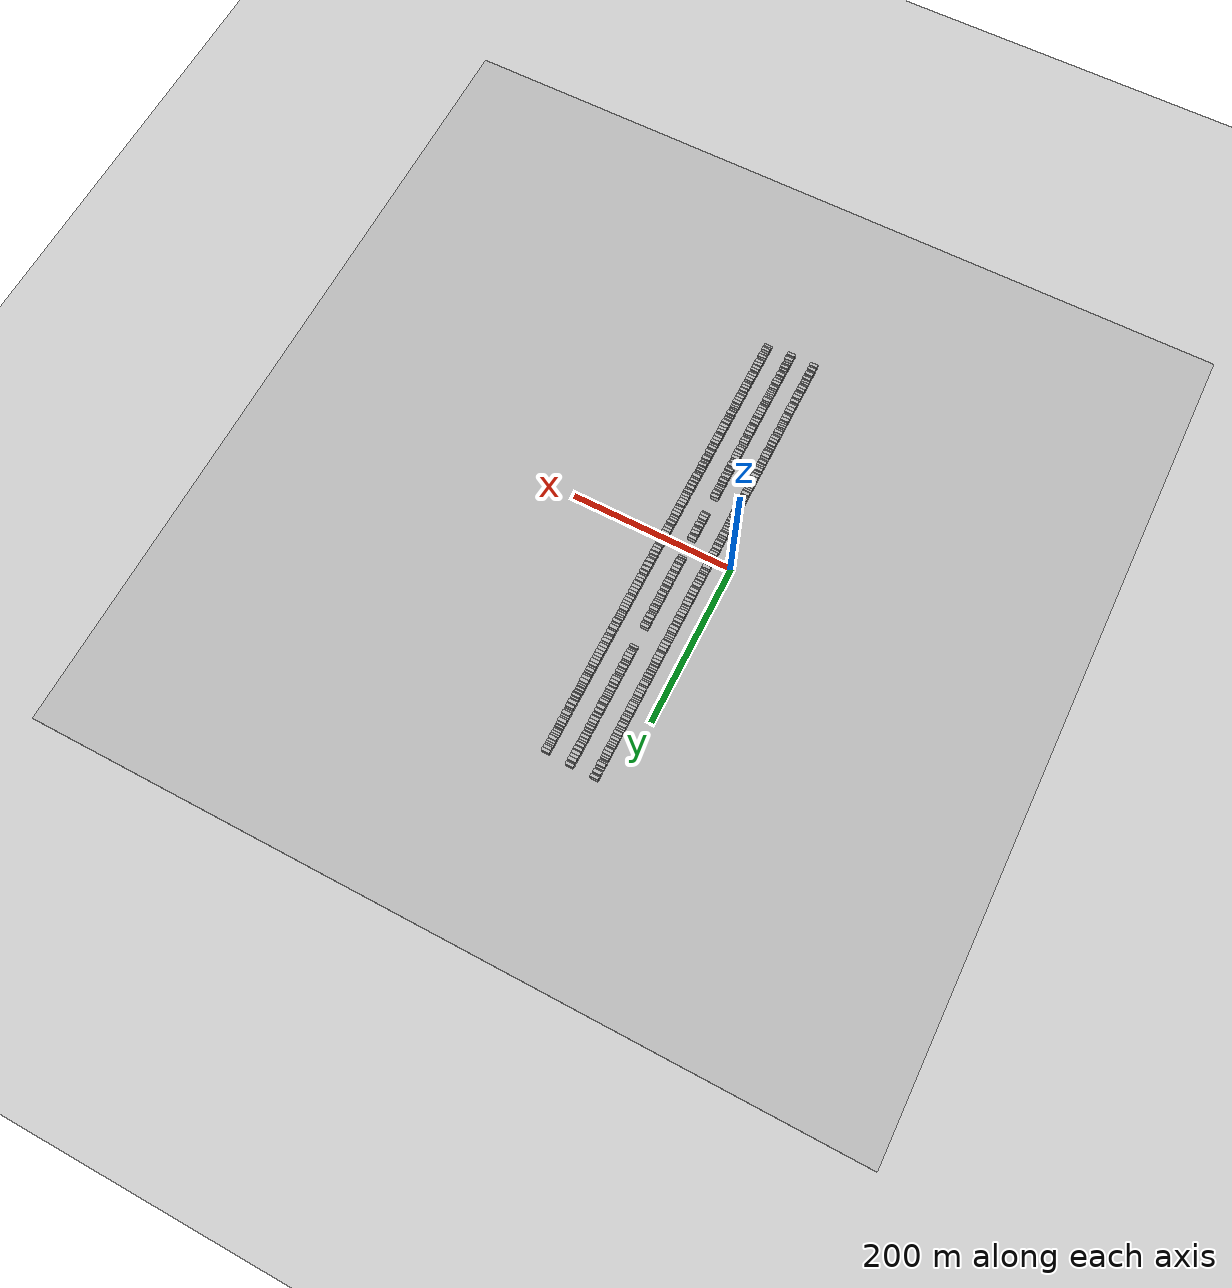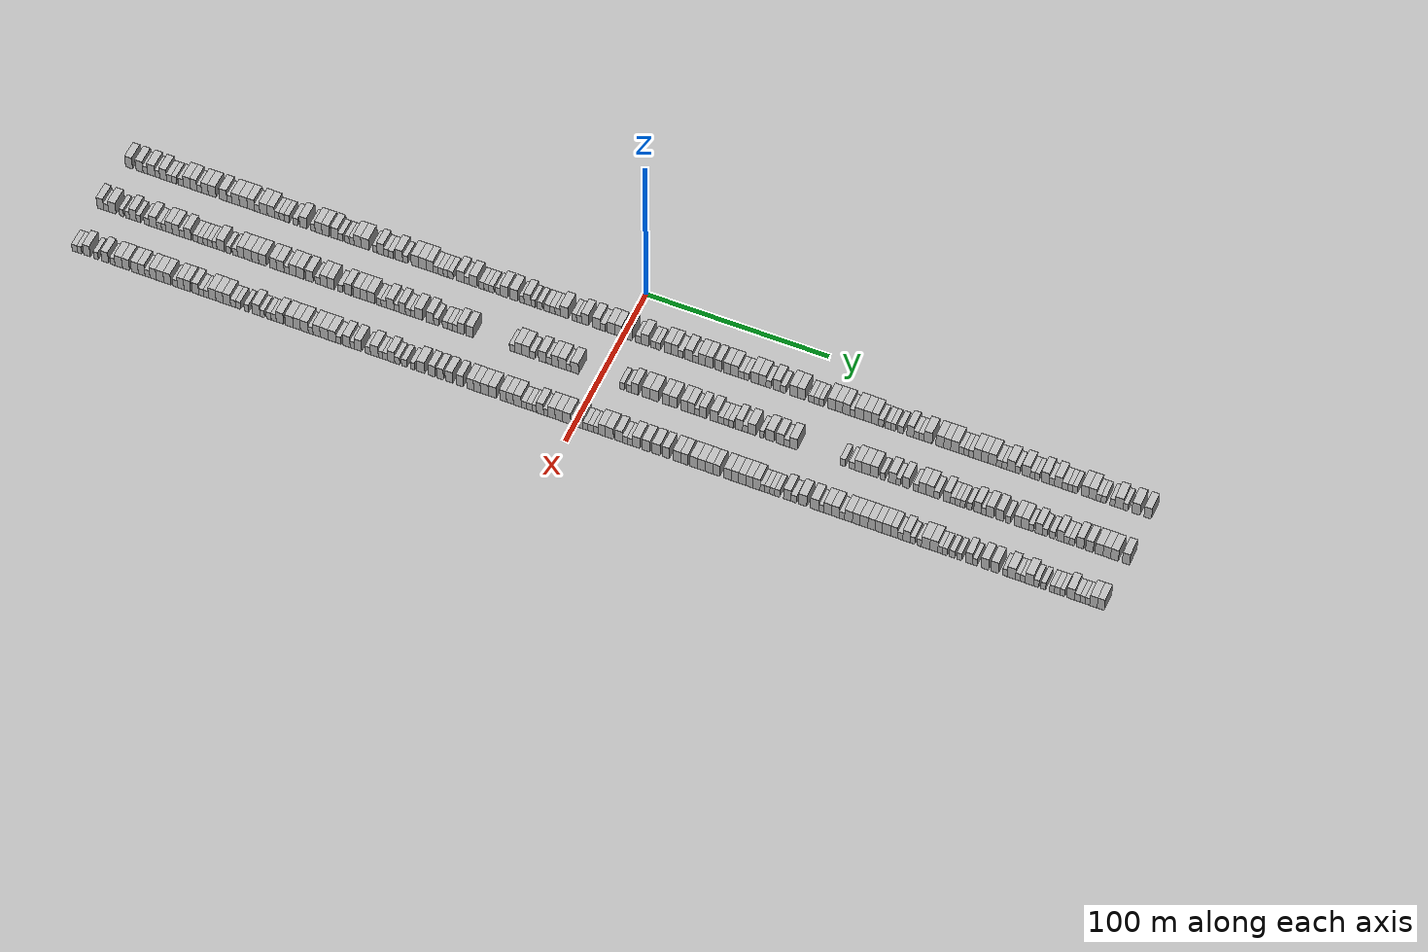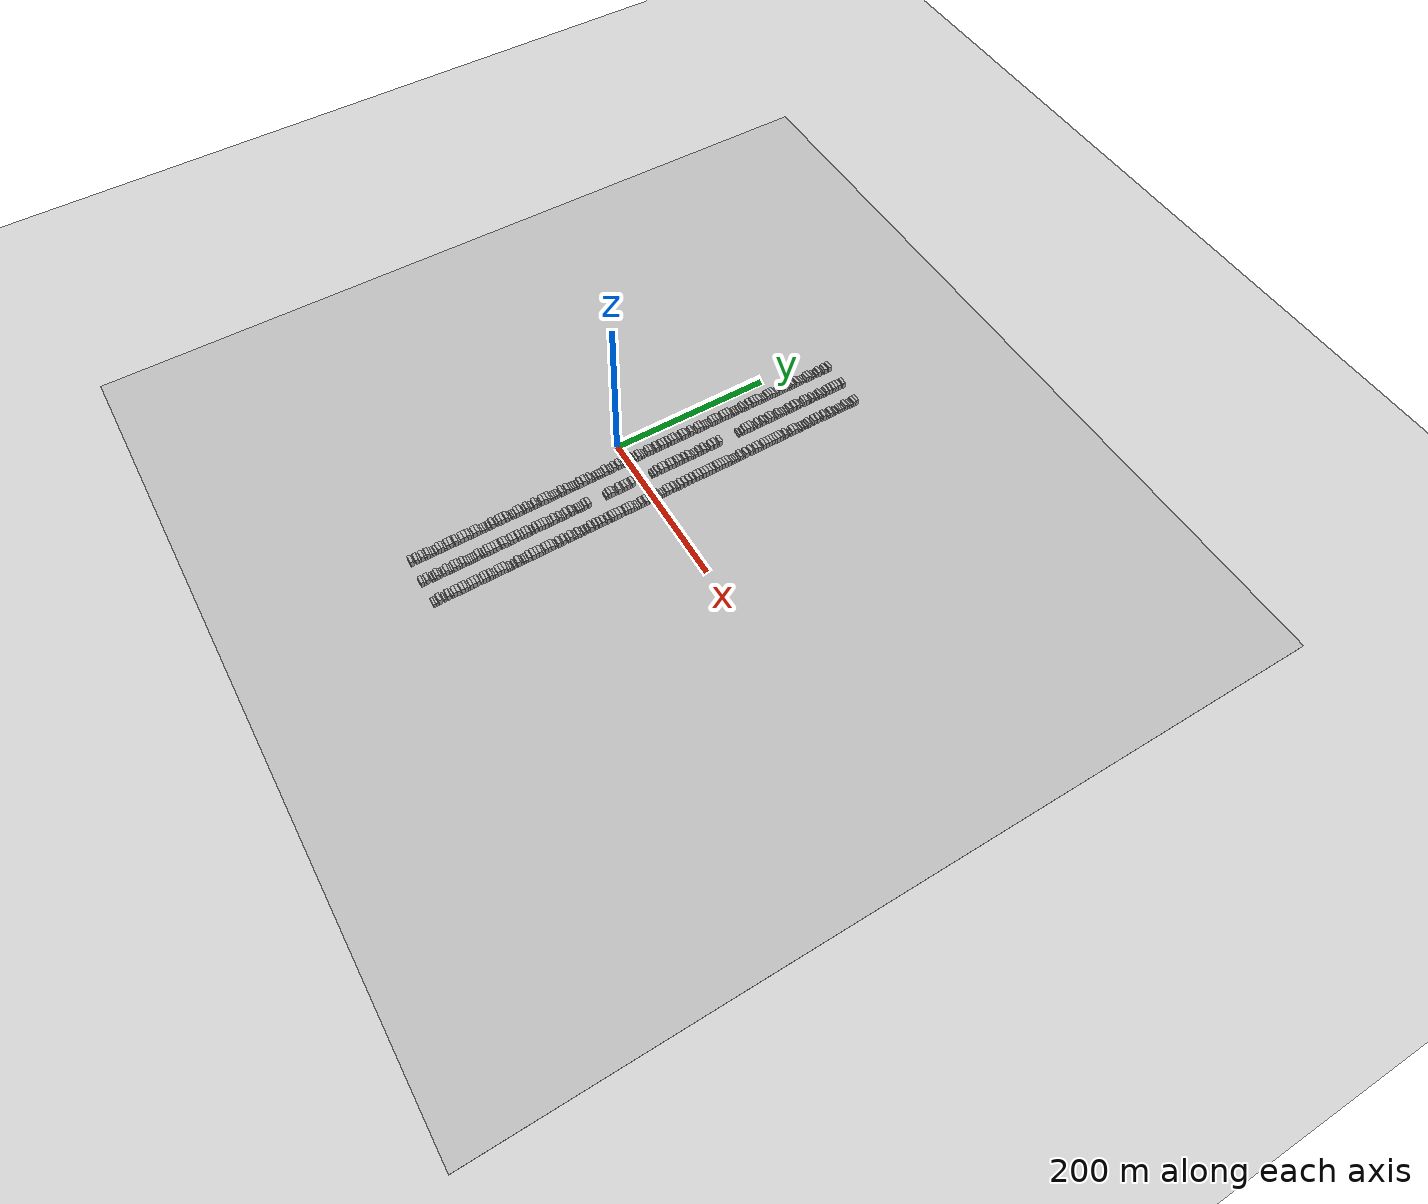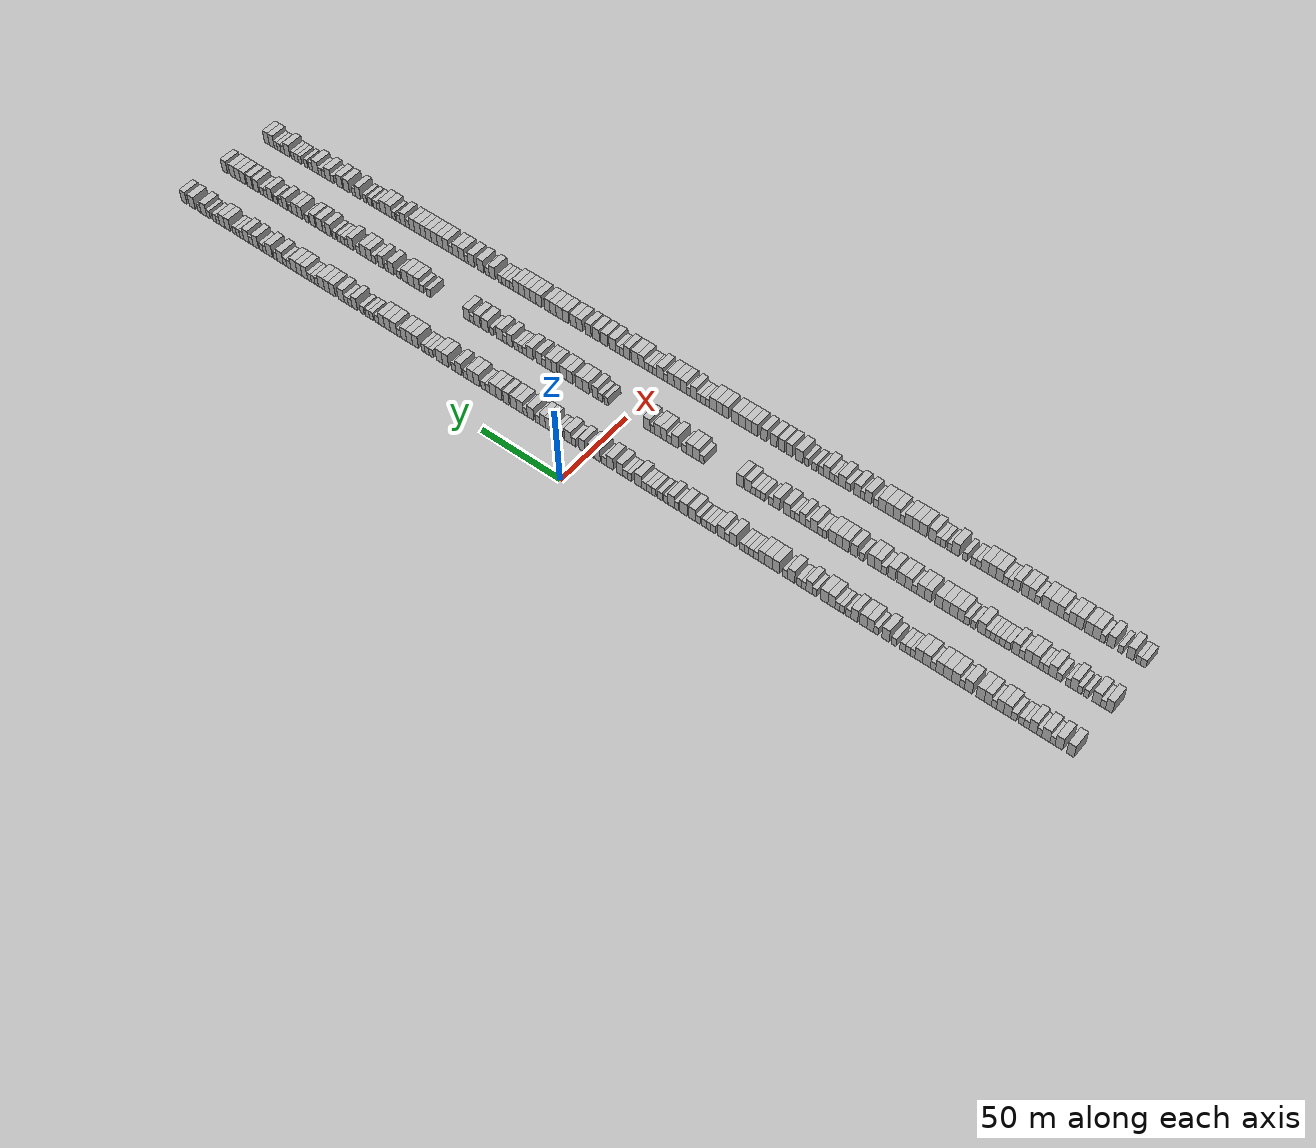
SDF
<?xml version="1.0" encoding="utf-8"?>

<sdf version="1.6">

   <world name="default">

      <gui fullscreen="0">

         <camera name="user_camera">

            <pose>-15 0 4.57585 0 0 0</pose>

            <view_controller>orbit</view_controller>

         </camera>

      </gui>

      <scene>

         <sky>

           <clouds>

             <speed>12</speed>

           </clouds>

         </sky>

         <ambient>0.4 0.4 0.4 1</ambient>

         <background>0.7 0.7 0.7 1</background>

         <shadows>1</shadows>

      </scene>

      <gravity>0 0 -9.8066</gravity>

      <magnetic_field>6e-06 2.3e-05 -4.2e-05</magnetic_field>

      <physics default="0" name="default_physics" type="ode">

         <ode>

            <solver>

               <type>quick</type>

               <iters>10</iters>

               <sor>1.0</sor>

               <use_dynamic_moi_rescaling>0</use_dynamic_moi_rescaling>

            </solver>

            <constraints>

               <cfm>0</cfm>

               <erp>0.2</erp>

               <contact_max_correcting_vel>100</contact_max_correcting_vel>

               <contact_surface_layer>0.001</contact_surface_layer>

            </constraints>

         </ode>

         <max_step_size>0.004</max_step_size>

         <real_time_factor>1</real_time_factor>

         <real_time_update_rate>250</real_time_update_rate>

      </physics>

      <light name="sun" type="directional">

         <cast_shadows>1</cast_shadows>

         <pose>0 0 10 0 0 0</pose>

         <diffuse>0.8 0.8 0.8 1</diffuse>

         <specular>0.2 0.2 0.2 1</specular>

         <attenuation>

            <range>1000</range>

            <constant>0.9</constant>

            <linear>0.01</linear>

            <quadratic>0.001</quadratic>

         </attenuation>

         <direction>-0.5 0.1 -0.9</direction>

      </light>

      <include>

         <name>ground_plane_1</name>

         <uri>model://HANNAS_ground_plane</uri>

         <pose>0 0 0  0 0 0</pose>

      </include>

      <include>

         <name>ground_plane_2</name>

         <uri>model://HANNAS_ground_plane</uri>

         <pose>100 0 0  0 0 0</pose>

      </include>

      <model name="building_1">

         <static>1</static>

         <pose frame="">25.0000 -277.0038 0 0.000000 0.000000 0.000000</pose>

         <link name="link">

            <pose frame="">0 0 4.50 0 0 0</pose>

            <collision name="collision">

               <geometry>

                  <box>

                     <size>10.0000 3.9925 9.0000</size>

                  </box>

               </geometry>

               <max_contacts>10</max_contacts>

               <surface>

                  <contact>

                     <ode/>

                  </contact>

                  <bounce/>

                  <friction>

                     <torsional>

                        <ode/>

                     </torsional>

                     <ode/>

                  </friction>

               </surface>

            </collision>

            <visual name="visual">

               <cast_shadows>0</cast_shadows>

               <geometry>

                  <box>

                     <size>10.0000 3.9925 9.0000</size>

                  </box>

               </geometry>

               <material>

                  <script>

                     <uri>model://HANNAS_wall/materials/scripts</uri>

                     <uri>model://HANNAS_wall/materials/textures</uri>

                     <name>vrc/HANNAS_wall</name>

                  </script>

               </material>

            </visual>

            <self_collide>0</self_collide>

            <enable_wind>0</enable_wind>

            <kinematic>0</kinematic>

         </link>

      </model>

      <model name="building_2">

         <static>1</static>

         <pose frame="">25.0000 -271.0248 0 0.000000 0.000000 0.000000</pose>

         <link name="link">

            <pose frame="">0 0 4.50 0 0 0</pose>

            <collision name="collision">

               <geometry>

                  <box>

                     <size>10.0000 3.9655 9.0000</size>

                  </box>

               </geometry>

               <max_contacts>10</max_contacts>

               <surface>

                  <contact>

                     <ode/>

                  </contact>

                  <bounce/>

                  <friction>

                     <torsional>

                        <ode/>

                     </torsional>

                     <ode/>

                  </friction>

               </surface>

            </collision>

            <visual name="visual">

               <cast_shadows>0</cast_shadows>

               <geometry>

                  <box>

                     <size>10.0000 3.9655 9.0000</size>

                  </box>

               </geometry>

               <material>

                  <script>

                     <uri>model://HANNAS_wall/materials/scripts</uri>

                     <uri>model://HANNAS_wall/materials/textures</uri>

                     <name>vrc/HANNAS_wall</name>

                  </script>

               </material>

            </visual>

            <self_collide>0</self_collide>

            <enable_wind>0</enable_wind>

            <kinematic>0</kinematic>

         </link>

      </model>

      <model name="building_3">

         <static>1</static>

         <pose frame="">25.0000 -267.7097 0 0.000000 0.000000 0.000000</pose>

         <link name="link">

            <pose frame="">0 0 3.00 0 0 0</pose>

            <collision name="collision">

               <geometry>

                  <box>

                     <size>10.0000 2.6647 6.0000</size>

                  </box>

               </geometry>

               <max_contacts>10</max_contacts>

               <surface>

                  <contact>

                     <ode/>

                  </contact>

                  <bounce/>

                  <friction>

                     <torsional>

                        <ode/>

                     </torsional>

                     <ode/>

                  </friction>

               </surface>

            </collision>

            <visual name="visual">

               <cast_shadows>0</cast_shadows>

               <geometry>

                  <box>

                     <size>10.0000 2.6647 6.0000</size>

                  </box>

               </geometry>

               <material>

                  <script>

                     <uri>model://HANNAS_wall/materials/scripts</uri>

                     <uri>model://HANNAS_wall/materials/textures</uri>

                     <name>vrc/HANNAS_wall</name>

                  </script>

               </material>

            </visual>

            <self_collide>0</self_collide>

            <enable_wind>0</enable_wind>

            <kinematic>0</kinematic>

         </link>

      </model>

      <model name="building_4">

         <static>1</static>

         <pose frame="">25.0000 -264.2000 0 0.000000 0.000000 0.000000</pose>

         <link name="link">

            <pose frame="">0 0 4.50 0 0 0</pose>

            <collision name="collision">

               <geometry>

                  <box>

                     <size>10.0000 4.3547 9.0000</size>

                  </box>

               </geometry>

               <max_contacts>10</max_contacts>

               <surface>

                  <contact>

                     <ode/>

                  </contact>

                  <bounce/>

                  <friction>

                     <torsional>

                        <ode/>

                     </torsional>

                     <ode/>

                  </friction>

               </surface>

            </collision>

            <visual name="visual">

               <cast_shadows>0</cast_shadows>

               <geometry>

                  <box>

                     <size>10.0000 4.3547 9.0000</size>

                  </box>

               </geometry>

               <material>

                  <script>

                     <uri>model://HANNAS_wall/materials/scripts</uri>

                     <uri>model://HANNAS_wall/materials/textures</uri>

                     <name>vrc/HANNAS_wall</name>

                  </script>

               </material>

            </visual>

            <self_collide>0</self_collide>

            <enable_wind>0</enable_wind>

            <kinematic>0</kinematic>

         </link>

      </model>

      <model name="building_5">

         <static>1</static>

         <pose frame="">25.0000 -260.6877 0 0.000000 0.000000 0.000000</pose>

         <link name="link">

            <pose frame="">0 0 3.00 0 0 0</pose>

            <collision name="collision">

               <geometry>

                  <box>

                     <size>10.0000 2.6699 6.0000</size>

                  </box>

               </geometry>

               <max_contacts>10</max_contacts>

               <surface>

                  <contact>

                     <ode/>

                  </contact>

                  <bounce/>

                  <friction>

                     <torsional>

                        <ode/>

                     </torsional>

                     <ode/>

                  </friction>

               </surface>

            </collision>

            <visual name="visual">

               <cast_shadows>0</cast_shadows>

               <geometry>

                  <box>

                     <size>10.0000 2.6699 6.0000</size>

                  </box>

               </geometry>

               <material>

                  <script>

                     <uri>model://HANNAS_wall/materials/scripts</uri>

                     <uri>model://HANNAS_wall/materials/textures</uri>

                     <name>vrc/HANNAS_wall</name>

                  </script>

               </material>

            </visual>

            <self_collide>0</self_collide>

            <enable_wind>0</enable_wind>

            <kinematic>0</kinematic>

         </link>

      </model>

      <model name="building_6">

         <static>1</static>

         <pose frame="">25.0000 -257.3909 0 0.000000 0.000000 0.000000</pose>

         <link name="link">

            <pose frame="">0 0 4.50 0 0 0</pose>

            <collision name="collision">

               <geometry>

                  <box>

                     <size>10.0000 3.9236 9.0000</size>

                  </box>

               </geometry>

               <max_contacts>10</max_contacts>

               <surface>

                  <contact>

                     <ode/>

                  </contact>

                  <bounce/>

                  <friction>

                     <torsional>

                        <ode/>

                     </torsional>

                     <ode/>

                  </friction>

               </surface>

            </collision>

            <visual name="visual">

               <cast_shadows>0</cast_shadows>

               <geometry>

                  <box>

                     <size>10.0000 3.9236 9.0000</size>

                  </box>

               </geometry>

               <material>

                  <script>

                     <uri>model://HANNAS_wall/materials/scripts</uri>

                     <uri>model://HANNAS_wall/materials/textures</uri>

                     <name>vrc/HANNAS_wall</name>

                  </script>

               </material>

            </visual>

            <self_collide>0</self_collide>

            <enable_wind>0</enable_wind>

            <kinematic>0</kinematic>

         </link>

      </model>

      <model name="building_7">

         <static>1</static>

         <pose frame="">25.0000 -253.9746 0 0.000000 0.000000 0.000000</pose>

         <link name="link">

            <pose frame="">0 0 3.00 0 0 0</pose>

            <collision name="collision">

               <geometry>

                  <box>

                     <size>10.0000 2.9091 6.0000</size>

                  </box>

               </geometry>

               <max_contacts>10</max_contacts>

               <surface>

                  <contact>

                     <ode/>

                  </contact>

                  <bounce/>

                  <friction>

                     <torsional>

                        <ode/>

                     </torsional>

                     <ode/>

                  </friction>

               </surface>

            </collision>

            <visual name="visual">

               <cast_shadows>0</cast_shadows>

               <geometry>

                  <box>

                     <size>10.0000 2.9091 6.0000</size>

                  </box>

               </geometry>

               <material>

                  <script>

                     <uri>model://HANNAS_wall/materials/scripts</uri>

                     <uri>model://HANNAS_wall/materials/textures</uri>

                     <name>vrc/HANNAS_wall</name>

                  </script>

               </material>

            </visual>

            <self_collide>0</self_collide>

            <enable_wind>0</enable_wind>

            <kinematic>0</kinematic>

         </link>

      </model>

      <model name="building_8">

         <static>1</static>

         <pose frame="">25.0000 -251.1587 0 0.000000 0.000000 0.000000</pose>

         <link name="link">

            <pose frame="">0 0 3.00 0 0 0</pose>

            <collision name="collision">

               <geometry>

                  <box>

                     <size>10.0000 2.7225 6.0000</size>

                  </box>

               </geometry>

               <max_contacts>10</max_contacts>

               <surface>

                  <contact>

                     <ode/>

                  </contact>

                  <bounce/>

                  <friction>

                     <torsional>

                        <ode/>

                     </torsional>

                     <ode/>

                  </friction>

               </surface>

            </collision>

            <visual name="visual">

               <cast_shadows>0</cast_shadows>

               <geometry>

                  <box>

                     <size>10.0000 2.7225 6.0000</size>

                  </box>

               </geometry>

               <material>

                  <script>

                     <uri>model://HANNAS_wall/materials/scripts</uri>

                     <uri>model://HANNAS_wall/materials/textures</uri>

                     <name>vrc/HANNAS_wall</name>

                  </script>

               </material>

            </visual>

            <self_collide>0</self_collide>

            <enable_wind>0</enable_wind>

            <kinematic>0</kinematic>

         </link>

      </model>

      <model name="building_9">

         <static>1</static>

         <pose frame="">25.0000 -247.2979 0 0.000000 0.000000 0.000000</pose>

         <link name="link">

            <pose frame="">0 0 3.00 0 0 0</pose>

            <collision name="collision">

               <geometry>

                  <box>

                     <size>10.0000 2.9992 6.0000</size>

                  </box>

               </geometry>

               <max_contacts>10</max_contacts>

               <surface>

                  <contact>

                     <ode/>

                  </contact>

                  <bounce/>

                  <friction>

                     <torsional>

                        <ode/>

                     </torsional>

                     <ode/>

                  </friction>

               </surface>

            </collision>

            <visual name="visual">

               <cast_shadows>0</cast_shadows>

               <geometry>

                  <box>

                     <size>10.0000 2.9992 6.0000</size>

                  </box>

               </geometry>

               <material>

                  <script>

                     <uri>model://HANNAS_wall/materials/scripts</uri>

                     <uri>model://HANNAS_wall/materials/textures</uri>

                     <name>vrc/HANNAS_wall</name>

                  </script>

               </material>

            </visual>

            <self_collide>0</self_collide>

            <enable_wind>0</enable_wind>

            <kinematic>0</kinematic>

         </link>

      </model>

      <model name="building_10">

         <static>1</static>

         <pose frame="">25.0000 -243.8236 0 0.000000 0.000000 0.000000</pose>

         <link name="link">

            <pose frame="">0 0 4.50 0 0 0</pose>

            <collision name="collision">

               <geometry>

                  <box>

                     <size>10.0000 3.9494 9.0000</size>

                  </box>

               </geometry>

               <max_contacts>10</max_contacts>

               <surface>

                  <contact>

                     <ode/>

                  </contact>

                  <bounce/>

                  <friction>

                     <torsional>

                        <ode/>

                     </torsional>

                     <ode/>

                  </friction>

               </surface>

            </collision>

            <visual name="visual">

               <cast_shadows>0</cast_shadows>

               <geometry>

                  <box>

                     <size>10.0000 3.9494 9.0000</size>

                  </box>

               </geometry>

               <material>

                  <script>

                     <uri>model://HANNAS_wall/materials/scripts</uri>

                     <uri>model://HANNAS_wall/materials/textures</uri>

                     <name>vrc/HANNAS_wall</name>

                  </script>

               </material>

            </visual>

            <self_collide>0</self_collide>

            <enable_wind>0</enable_wind>

            <kinematic>0</kinematic>

         </link>

      </model>

      <model name="building_11">

         <static>1</static>

         <pose frame="">25.0000 -240.0031 0 0.000000 0.000000 0.000000</pose>

         <link name="link">

            <pose frame="">0 0 4.50 0 0 0</pose>

            <collision name="collision">

               <geometry>

                  <box>

                     <size>10.0000 3.6916 9.0000</size>

                  </box>

               </geometry>

               <max_contacts>10</max_contacts>

               <surface>

                  <contact>

                     <ode/>

                  </contact>

                  <bounce/>

                  <friction>

                     <torsional>

                        <ode/>

                     </torsional>

                     <ode/>

                  </friction>

               </surface>

            </collision>

            <visual name="visual">

               <cast_shadows>0</cast_shadows>

               <geometry>

                  <box>

                     <size>10.0000 3.6916 9.0000</size>

                  </box>

               </geometry>

               <material>

                  <script>

                     <uri>model://HANNAS_wall/materials/scripts</uri>

                     <uri>model://HANNAS_wall/materials/textures</uri>

                     <name>vrc/HANNAS_wall</name>

                  </script>

               </material>

            </visual>

            <self_collide>0</self_collide>

            <enable_wind>0</enable_wind>

            <kinematic>0</kinematic>

         </link>

      </model>

      <model name="building_12">

         <static>1</static>

         <pose frame="">25.0000 -236.7888 0 0.000000 0.000000 0.000000</pose>

         <link name="link">

            <pose frame="">0 0 3.00 0 0 0</pose>

            <collision name="collision">

               <geometry>

                  <box>

                     <size>10.0000 2.7369 6.0000</size>

                  </box>

               </geometry>

               <max_contacts>10</max_contacts>

               <surface>

                  <contact>

                     <ode/>

                  </contact>

                  <bounce/>

                  <friction>

                     <torsional>

                        <ode/>

                     </torsional>

                     <ode/>

                  </friction>

               </surface>

            </collision>

            <visual name="visual">

               <cast_shadows>0</cast_shadows>

               <geometry>

                  <box>

                     <size>10.0000 2.7369 6.0000</size>

                  </box>

               </geometry>

               <material>

                  <script>

                     <uri>model://HANNAS_wall/materials/scripts</uri>

                     <uri>model://HANNAS_wall/materials/textures</uri>

                     <name>vrc/HANNAS_wall</name>

                  </script>

               </material>

            </visual>

            <self_collide>0</self_collide>

            <enable_wind>0</enable_wind>

            <kinematic>0</kinematic>

         </link>

      </model>

      <model name="building_13">

         <static>1</static>

         <pose frame="">25.0000 -233.5396 0 0.000000 0.000000 0.000000</pose>

         <link name="link">

            <pose frame="">0 0 4.50 0 0 0</pose>

            <collision name="collision">

               <geometry>

                  <box>

                     <size>10.0000 3.7614 9.0000</size>

                  </box>

               </geometry>

               <max_contacts>10</max_contacts>

               <surface>

                  <contact>

                     <ode/>

                  </contact>

                  <bounce/>

                  <friction>

                     <torsional>

                        <ode/>

                     </torsional>

                     <ode/>

                  </friction>

               </surface>

            </collision>

            <visual name="visual">

               <cast_shadows>0</cast_shadows>

               <geometry>

                  <box>

                     <size>10.0000 3.7614 9.0000</size>

                  </box>

               </geometry>

               <material>

                  <script>

                     <uri>model://HANNAS_wall/materials/scripts</uri>

                     <uri>model://HANNAS_wall/materials/textures</uri>

                     <name>vrc/HANNAS_wall</name>

                  </script>

               </material>

            </visual>

            <self_collide>0</self_collide>

            <enable_wind>0</enable_wind>

            <kinematic>0</kinematic>

         </link>

      </model>

      <model name="building_14">

         <static>1</static>

         <pose frame="">25.0000 -229.4503 0 0.000000 0.000000 0.000000</pose>

         <link name="link">

            <pose frame="">0 0 4.50 0 0 0</pose>

            <collision name="collision">

               <geometry>

                  <box>

                     <size>10.0000 4.4173 9.0000</size>

                  </box>

               </geometry>

               <max_contacts>10</max_contacts>

               <surface>

                  <contact>

                     <ode/>

                  </contact>

                  <bounce/>

                  <friction>

                     <torsional>

                        <ode/>

                     </torsional>

                     <ode/>

                  </friction>

               </surface>

            </collision>

            <visual name="visual">

               <cast_shadows>0</cast_shadows>

               <geometry>

                  <box>

                     <size>10.0000 4.4173 9.0000</size>

                  </box>

               </geometry>

               <material>

                  <script>

                     <uri>model://HANNAS_wall/materials/scripts</uri>

                     <uri>model://HANNAS_wall/materials/textures</uri>

                     <name>vrc/HANNAS_wall</name>

                  </script>

               </material>

            </visual>

            <self_collide>0</self_collide>

            <enable_wind>0</enable_wind>

            <kinematic>0</kinematic>

         </link>

      </model>

      <model name="building_15">

         <static>1</static>

         <pose frame="">25.0000 -223.1103 0 0.000000 0.000000 0.000000</pose>

         <link name="link">

            <pose frame="">0 0 4.50 0 0 0</pose>

            <collision name="collision">

               <geometry>

                  <box>

                     <size>10.0000 4.2626 9.0000</size>

                  </box>

               </geometry>

               <max_contacts>10</max_contacts>

               <surface>

                  <contact>

                     <ode/>

                  </contact>

                  <bounce/>

                  <friction>

                     <torsional>

                        <ode/>

                     </torsional>

                     <ode/>

                  </friction>

               </surface>

            </collision>

            <visual name="visual">

               <cast_shadows>0</cast_shadows>

               <geometry>

                  <box>

                     <size>10.0000 4.2626 9.0000</size>

                  </box>

               </geometry>

               <material>

                  <script>

                     <uri>model://HANNAS_wall/materials/scripts</uri>

                     <uri>model://HANNAS_wall/materials/textures</uri>

                     <name>vrc/HANNAS_wall</name>

                  </script>

               </material>

            </visual>

            <self_collide>0</self_collide>

            <enable_wind>0</enable_wind>

            <kinematic>0</kinematic>

         </link>

      </model>

      <model name="building_16">

         <static>1</static>

         <pose frame="">25.0000 -219.6177 0 0.000000 0.000000 0.000000</pose>

         <link name="link">

            <pose frame="">0 0 3.00 0 0 0</pose>

            <collision name="collision">

               <geometry>

                  <box>

                     <size>10.0000 2.7226 6.0000</size>

                  </box>

               </geometry>

               <max_contacts>10</max_contacts>

               <surface>

                  <contact>

                     <ode/>

                  </contact>

                  <bounce/>

                  <friction>

                     <torsional>

                        <ode/>

                     </torsional>

                     <ode/>

                  </friction>

               </surface>

            </collision>

            <visual name="visual">

               <cast_shadows>0</cast_shadows>

               <geometry>

                  <box>

                     <size>10.0000 2.7226 6.0000</size>

                  </box>

               </geometry>

               <material>

                  <script>

                     <uri>model://HANNAS_wall/materials/scripts</uri>

                     <uri>model://HANNAS_wall/materials/textures</uri>

                     <name>vrc/HANNAS_wall</name>

                  </script>

               </material>

            </visual>

            <self_collide>0</self_collide>

            <enable_wind>0</enable_wind>

            <kinematic>0</kinematic>

         </link>

      </model>

      <model name="building_17">

         <static>1</static>

         <pose frame="">25.0000 -216.0488 0 0.000000 0.000000 0.000000</pose>

         <link name="link">

            <pose frame="">0 0 4.50 0 0 0</pose>

            <collision name="collision">

               <geometry>

                  <box>

                     <size>10.0000 4.4151 9.0000</size>

                  </box>

               </geometry>

               <max_contacts>10</max_contacts>

               <surface>

                  <contact>

                     <ode/>

                  </contact>

                  <bounce/>

                  <friction>

                     <torsional>

                        <ode/>

                     </torsional>

                     <ode/>

                  </friction>

               </surface>

            </collision>

            <visual name="visual">

               <cast_shadows>0</cast_shadows>

               <geometry>

                  <box>

                     <size>10.0000 4.4151 9.0000</size>

                  </box>

               </geometry>

               <material>

                  <script>

                     <uri>model://HANNAS_wall/materials/scripts</uri>

                     <uri>model://HANNAS_wall/materials/textures</uri>

                     <name>vrc/HANNAS_wall</name>

                  </script>

               </material>

            </visual>

            <self_collide>0</self_collide>

            <enable_wind>0</enable_wind>

            <kinematic>0</kinematic>

         </link>

      </model>

      <model name="building_18">

         <static>1</static>

         <pose frame="">25.0000 -211.5920 0 0.000000 0.000000 0.000000</pose>

         <link name="link">

            <pose frame="">0 0 4.50 0 0 0</pose>

            <collision name="collision">

               <geometry>

                  <box>

                     <size>10.0000 4.4987 9.0000</size>

                  </box>

               </geometry>

               <max_contacts>10</max_contacts>

               <surface>

                  <contact>

                     <ode/>

                  </contact>

                  <bounce/>

                  <friction>

                     <torsional>

                        <ode/>

                     </torsional>

                     <ode/>

                  </friction>

               </surface>

            </collision>

            <visual name="visual">

               <cast_shadows>0</cast_shadows>

               <geometry>

                  <box>

                     <size>10.0000 4.4987 9.0000</size>

                  </box>

               </geometry>

               <material>

                  <script>

                     <uri>model://HANNAS_wall/materials/scripts</uri>

                     <uri>model://HANNAS_wall/materials/textures</uri>

                     <name>vrc/HANNAS_wall</name>

                  </script>

               </material>

            </visual>

            <self_collide>0</self_collide>

            <enable_wind>0</enable_wind>

            <kinematic>0</kinematic>

         </link>

      </model>

      <model name="building_19">

         <static>1</static>

         <pose frame="">25.0000 -207.3325 0 0.000000 0.000000 0.000000</pose>

         <link name="link">

            <pose frame="">0 0 4.50 0 0 0</pose>

            <collision name="collision">

               <geometry>

                  <box>

                     <size>10.0000 4.0202 9.0000</size>

                  </box>

               </geometry>

               <max_contacts>10</max_contacts>

               <surface>

                  <contact>

                     <ode/>

                  </contact>

                  <bounce/>

                  <friction>

                     <torsional>

                        <ode/>

                     </torsional>

                     <ode/>

                  </friction>

               </surface>

            </collision>

            <visual name="visual">

               <cast_shadows>0</cast_shadows>

               <geometry>

                  <box>

                     <size>10.0000 4.0202 9.0000</size>

                  </box>

               </geometry>

               <material>

                  <script>

                     <uri>model://HANNAS_wall/materials/scripts</uri>

                     <uri>model://HANNAS_wall/materials/textures</uri>

                     <name>vrc/HANNAS_wall</name>

                  </script>

               </material>

            </visual>

            <self_collide>0</self_collide>

            <enable_wind>0</enable_wind>

            <kinematic>0</kinematic>

         </link>

      </model>

      <model name="building_20">

         <static>1</static>

         <pose frame="">25.0000 -203.8742 0 0.000000 0.000000 0.000000</pose>

         <link name="link">

            <pose frame="">0 0 3.00 0 0 0</pose>

            <collision name="collision">

               <geometry>

                  <box>

                     <size>10.0000 2.8964 6.0000</size>

                  </box>

               </geometry>

               <max_contacts>10</max_contacts>

               <surface>

                  <contact>

                     <ode/>

                  </contact>

                  <bounce/>

                  <friction>

                     <torsional>

                        <ode/>

                     </torsional>

                     <ode/>

                  </friction>

               </surface>

            </collision>

            <visual name="visual">

               <cast_shadows>0</cast_shadows>

               <geometry>

                  <box>

                     <size>10.0000 2.8964 6.0000</size>

                  </box>

               </geometry>

               <material>

                  <script>

                     <uri>model://HANNAS_wall/materials/scripts</uri>

                     <uri>model://HANNAS_wall/materials/textures</uri>

                     <name>vrc/HANNAS_wall</name>

                  </script>

               </material>

            </visual>

            <self_collide>0</self_collide>

            <enable_wind>0</enable_wind>

            <kinematic>0</kinematic>

         </link>

      </model>

      <model name="building_21">

         <static>1</static>

         <pose frame="">25.0000 -200.2595 0 0.000000 0.000000 0.000000</pose>

         <link name="link">

            <pose frame="">0 0 4.50 0 0 0</pose>

            <collision name="collision">

               <geometry>

                  <box>

                     <size>10.0000 4.3330 9.0000</size>

                  </box>

               </geometry>

               <max_contacts>10</max_contacts>

               <surface>

                  <contact>

                     <ode/>

                  </contact>

                  <bounce/>

                  <friction>

                     <torsional>

                        <ode/>

                     </torsional>

                     <ode/>

                  </friction>

               </surface>

            </collision>

            <visual name="visual">

               <cast_shadows>0</cast_shadows>

               <geometry>

                  <box>

                     <size>10.0000 4.3330 9.0000</size>

                  </box>

               </geometry>

               <material>

                  <script>

                     <uri>model://HANNAS_wall/materials/scripts</uri>

                     <uri>model://HANNAS_wall/materials/textures</uri>

                     <name>vrc/HANNAS_wall</name>

                  </script>

               </material>

            </visual>

            <self_collide>0</self_collide>

            <enable_wind>0</enable_wind>

            <kinematic>0</kinematic>

         </link>

      </model>

      <model name="building_22">

         <static>1</static>

         <pose frame="">25.0000 -195.9828 0 0.000000 0.000000 0.000000</pose>

         <link name="link">

            <pose frame="">0 0 4.50 0 0 0</pose>

            <collision name="collision">

               <geometry>

                  <box>

                     <size>10.0000 4.2205 9.0000</size>

                  </box>

               </geometry>

               <max_contacts>10</max_contacts>

               <surface>

                  <contact>

                     <ode/>

                  </contact>

                  <bounce/>

                  <friction>

                     <torsional>

                        <ode/>

                     </torsional>

                     <ode/>

                  </friction>

               </surface>

            </collision>

            <visual name="visual">

               <cast_shadows>0</cast_shadows>

               <geometry>

                  <box>

                     <size>10.0000 4.2205 9.0000</size>

                  </box>

               </geometry>

               <material>

                  <script>

                     <uri>model://HANNAS_wall/materials/scripts</uri>

                     <uri>model://HANNAS_wall/materials/textures</uri>

                     <name>vrc/HANNAS_wall</name>

                  </script>

               </material>

            </visual>

            <self_collide>0</self_collide>

            <enable_wind>0</enable_wind>

            <kinematic>0</kinematic>

         </link>

      </model>

      <model name="building_23">

         <static>1</static>

         <pose frame="">25.0000 -192.6493 0 0.000000 0.000000 0.000000</pose>

         <link name="link">

            <pose frame="">0 0 3.00 0 0 0</pose>

            <collision name="collision">

               <geometry>

                  <box>

                     <size>10.0000 2.4464 6.0000</size>

                  </box>

               </geometry>

               <max_contacts>10</max_contacts>

               <surface>

                  <contact>

                     <ode/>

                  </contact>

                  <bounce/>

                  <friction>

                     <torsional>

                        <ode/>

                     </torsional>

                     <ode/>

                  </friction>

               </surface>

            </collision>

            <visual name="visual">

               <cast_shadows>0</cast_shadows>

               <geometry>

                  <box>

                     <size>10.0000 2.4464 6.0000</size>

                  </box>

               </geometry>

               <material>

                  <script>

                     <uri>model://HANNAS_wall/materials/scripts</uri>

                     <uri>model://HANNAS_wall/materials/textures</uri>

                     <name>vrc/HANNAS_wall</name>

                  </script>

               </material>

            </visual>

            <self_collide>0</self_collide>

            <enable_wind>0</enable_wind>

            <kinematic>0</kinematic>

         </link>

      </model>

      <model name="building_24">

         <static>1</static>

         <pose frame="">25.0000 -189.9598 0 0.000000 0.000000 0.000000</pose>

         <link name="link">

            <pose frame="">0 0 3.00 0 0 0</pose>

            <collision name="collision">

               <geometry>

                  <box>

                     <size>10.0000 2.9327 6.0000</size>

                  </box>

               </geometry>

               <max_contacts>10</max_contacts>

               <surface>

                  <contact>

                     <ode/>

                  </contact>

                  <bounce/>

                  <friction>

                     <torsional>

                        <ode/>

                     </torsional>

                     <ode/>

                  </friction>

               </surface>

            </collision>

            <visual name="visual">

               <cast_shadows>0</cast_shadows>

               <geometry>

                  <box>

                     <size>10.0000 2.9327 6.0000</size>

                  </box>

               </geometry>

               <material>

                  <script>

                     <uri>model://HANNAS_wall/materials/scripts</uri>

                     <uri>model://HANNAS_wall/materials/textures</uri>

                     <name>vrc/HANNAS_wall</name>

                  </script>

               </material>

            </visual>

            <self_collide>0</self_collide>

            <enable_wind>0</enable_wind>

            <kinematic>0</kinematic>

         </link>

      </model>

      <model name="building_25">

         <static>1</static>

         <pose frame="">25.0000 -187.0314 0 0.000000 0.000000 0.000000</pose>

         <link name="link">

            <pose frame="">0 0 3.00 0 0 0</pose>

            <collision name="collision">

               <geometry>

                  <box>

                     <size>10.0000 2.9241 6.0000</size>

                  </box>

               </geometry>

               <max_contacts>10</max_contacts>

               <surface>

                  <contact>

                     <ode/>

                  </contact>

                  <bounce/>

                  <friction>

                     <torsional>

                        <ode/>

                     </torsional>

                     <ode/>

                  </friction>

               </surface>

            </collision>

            <visual name="visual">

               <cast_shadows>0</cast_shadows>

               <geometry>

                  <box>

                     <size>10.0000 2.9241 6.0000</size>

                  </box>

               </geometry>

               <material>

                  <script>

                     <uri>model://HANNAS_wall/materials/scripts</uri>

                     <uri>model://HANNAS_wall/materials/textures</uri>

                     <name>vrc/HANNAS_wall</name>

                  </script>

               </material>

            </visual>

            <self_collide>0</self_collide>

            <enable_wind>0</enable_wind>

            <kinematic>0</kinematic>

         </link>

      </model>

      <model name="building_26">

         <static>1</static>

         <pose frame="">25.0000 -182.1606 0 0.000000 0.000000 0.000000</pose>

         <link name="link">

            <pose frame="">0 0 3.00 0 0 0</pose>

            <collision name="collision">

               <geometry>

                  <box>

                     <size>10.0000 2.8176 6.0000</size>

                  </box>

               </geometry>

               <max_contacts>10</max_contacts>

               <surface>

                  <contact>

                     <ode/>

                  </contact>

                  <bounce/>

                  <friction>

                     <torsional>

                        <ode/>

                     </torsional>

                     <ode/>

                  </friction>

               </surface>

            </collision>

            <visual name="visual">

               <cast_shadows>0</cast_shadows>

               <geometry>

                  <box>

                     <size>10.0000 2.8176 6.0000</size>

                  </box>

               </geometry>

               <material>

                  <script>

                     <uri>model://HANNAS_wall/materials/scripts</uri>

                     <uri>model://HANNAS_wall/materials/textures</uri>

                     <name>vrc/HANNAS_wall</name>

                  </script>

               </material>

            </visual>

            <self_collide>0</self_collide>

            <enable_wind>0</enable_wind>

            <kinematic>0</kinematic>

         </link>

      </model>

      <model name="building_27">

         <static>1</static>

         <pose frame="">25.0000 -177.6639 0 0.000000 0.000000 0.000000</pose>

         <link name="link">

            <pose frame="">0 0 4.50 0 0 0</pose>

            <collision name="collision">

               <geometry>

                  <box>

                     <size>10.0000 4.1757 9.0000</size>

                  </box>

               </geometry>

               <max_contacts>10</max_contacts>

               <surface>

                  <contact>

                     <ode/>

                  </contact>

                  <bounce/>

                  <friction>

                     <torsional>

                        <ode/>

                     </torsional>

                     <ode/>

                  </friction>

               </surface>

            </collision>

            <visual name="visual">

               <cast_shadows>0</cast_shadows>

               <geometry>

                  <box>

                     <size>10.0000 4.1757 9.0000</size>

                  </box>

               </geometry>

               <material>

                  <script>

                     <uri>model://HANNAS_wall/materials/scripts</uri>

                     <uri>model://HANNAS_wall/materials/textures</uri>

                     <name>vrc/HANNAS_wall</name>

                  </script>

               </material>

            </visual>

            <self_collide>0</self_collide>

            <enable_wind>0</enable_wind>

            <kinematic>0</kinematic>

         </link>

      </model>

      <model name="building_28">

         <static>1</static>

         <pose frame="">25.0000 -172.3150 0 0.000000 0.000000 0.000000</pose>

         <link name="link">

            <pose frame="">0 0 3.00 0 0 0</pose>

            <collision name="collision">

               <geometry>

                  <box>

                     <size>10.0000 2.5220 6.0000</size>

                  </box>

               </geometry>

               <max_contacts>10</max_contacts>

               <surface>

                  <contact>

                     <ode/>

                  </contact>

                  <bounce/>

                  <friction>

                     <torsional>

                        <ode/>

                     </torsional>

                     <ode/>

                  </friction>

               </surface>

            </collision>

            <visual name="visual">

               <cast_shadows>0</cast_shadows>

               <geometry>

                  <box>

                     <size>10.0000 2.5220 6.0000</size>

                  </box>

               </geometry>

               <material>

                  <script>

                     <uri>model://HANNAS_wall/materials/scripts</uri>

                     <uri>model://HANNAS_wall/materials/textures</uri>

                     <name>vrc/HANNAS_wall</name>

                  </script>

               </material>

            </visual>

            <self_collide>0</self_collide>

            <enable_wind>0</enable_wind>

            <kinematic>0</kinematic>

         </link>

      </model>

      <model name="building_29">

         <static>1</static>

         <pose frame="">25.0000 -169.1305 0 0.000000 0.000000 0.000000</pose>

         <link name="link">

            <pose frame="">0 0 4.50 0 0 0</pose>

            <collision name="collision">

               <geometry>

                  <box>

                     <size>10.0000 3.8471 9.0000</size>

                  </box>

               </geometry>

               <max_contacts>10</max_contacts>

               <surface>

                  <contact>

                     <ode/>

                  </contact>

                  <bounce/>

                  <friction>

                     <torsional>

                        <ode/>

                     </torsional>

                     <ode/>

                  </friction>

               </surface>

            </collision>

            <visual name="visual">

               <cast_shadows>0</cast_shadows>

               <geometry>

                  <box>

                     <size>10.0000 3.8471 9.0000</size>

                  </box>

               </geometry>

               <material>

                  <script>

                     <uri>model://HANNAS_wall/materials/scripts</uri>

                     <uri>model://HANNAS_wall/materials/textures</uri>

                     <name>vrc/HANNAS_wall</name>

                  </script>

               </material>

            </visual>

            <self_collide>0</self_collide>

            <enable_wind>0</enable_wind>

            <kinematic>0</kinematic>

         </link>

      </model>

      <model name="building_30">

         <static>1</static>

         <pose frame="">25.0000 -165.1003 0 0.000000 0.000000 0.000000</pose>

         <link name="link">

            <pose frame="">0 0 4.50 0 0 0</pose>

            <collision name="collision">

               <geometry>

                  <box>

                     <size>10.0000 4.2134 9.0000</size>

                  </box>

               </geometry>

               <max_contacts>10</max_contacts>

               <surface>

                  <contact>

                     <ode/>

                  </contact>

                  <bounce/>

                  <friction>

                     <torsional>

                        <ode/>

                     </torsional>

                     <ode/>

                  </friction>

               </surface>

            </collision>

            <visual name="visual">

               <cast_shadows>0</cast_shadows>

               <geometry>

                  <box>

                     <size>10.0000 4.2134 9.0000</size>

                  </box>

               </geometry>

               <material>

                  <script>

                     <uri>model://HANNAS_wall/materials/scripts</uri>

                     <uri>model://HANNAS_wall/materials/textures</uri>

                     <name>vrc/HANNAS_wall</name>

                  </script>

               </material>

            </visual>

            <self_collide>0</self_collide>

            <enable_wind>0</enable_wind>

            <kinematic>0</kinematic>

         </link>

      </model>

      <model name="building_31">

         <static>1</static>

         <pose frame="">25.0000 -160.0401 0 0.000000 0.000000 0.000000</pose>

         <link name="link">

            <pose frame="">0 0 4.50 0 0 0</pose>

            <collision name="collision">

               <geometry>

                  <box>

                     <size>10.0000 3.9069 9.0000</size>

                  </box>

               </geometry>

               <max_contacts>10</max_contacts>

               <surface>

                  <contact>

                     <ode/>

                  </contact>

                  <bounce/>

                  <friction>

                     <torsional>

                        <ode/>

                     </torsional>

                     <ode/>

                  </friction>

               </surface>

            </collision>

            <visual name="visual">

               <cast_shadows>0</cast_shadows>

               <geometry>

                  <box>

                     <size>10.0000 3.9069 9.0000</size>

                  </box>

               </geometry>

               <material>

                  <script>

                     <uri>model://HANNAS_wall/materials/scripts</uri>

                     <uri>model://HANNAS_wall/materials/textures</uri>

                     <name>vrc/HANNAS_wall</name>

                  </script>

               </material>

            </visual>

            <self_collide>0</self_collide>

            <enable_wind>0</enable_wind>

            <kinematic>0</kinematic>

         </link>

      </model>

      <model name="building_32">

         <static>1</static>

         <pose frame="">25.0000 -156.6696 0 0.000000 0.000000 0.000000</pose>

         <link name="link">

            <pose frame="">0 0 3.00 0 0 0</pose>

            <collision name="collision">

               <geometry>

                  <box>

                     <size>10.0000 2.8342 6.0000</size>

                  </box>

               </geometry>

               <max_contacts>10</max_contacts>

               <surface>

                  <contact>

                     <ode/>

                  </contact>

                  <bounce/>

                  <friction>

                     <torsional>

                        <ode/>

                     </torsional>

                     <ode/>

                  </friction>

               </surface>

            </collision>

            <visual name="visual">

               <cast_shadows>0</cast_shadows>

               <geometry>

                  <box>

                     <size>10.0000 2.8342 6.0000</size>

                  </box>

               </geometry>

               <material>

                  <script>

                     <uri>model://HANNAS_wall/materials/scripts</uri>

                     <uri>model://HANNAS_wall/materials/textures</uri>

                     <name>vrc/HANNAS_wall</name>

                  </script>

               </material>

            </visual>

            <self_collide>0</self_collide>

            <enable_wind>0</enable_wind>

            <kinematic>0</kinematic>

         </link>

      </model>

      <model name="building_33">

         <static>1</static>

         <pose frame="">25.0000 -153.0370 0 0.000000 0.000000 0.000000</pose>

         <link name="link">

            <pose frame="">0 0 3.00 0 0 0</pose>

            <collision name="collision">

               <geometry>

                  <box>

                     <size>10.0000 2.4311 6.0000</size>

                  </box>

               </geometry>

               <max_contacts>10</max_contacts>

               <surface>

                  <contact>

                     <ode/>

                  </contact>

                  <bounce/>

                  <friction>

                     <torsional>

                        <ode/>

                     </torsional>

                     <ode/>

                  </friction>

               </surface>

            </collision>

            <visual name="visual">

               <cast_shadows>0</cast_shadows>

               <geometry>

                  <box>

                     <size>10.0000 2.4311 6.0000</size>

                  </box>

               </geometry>

               <material>

                  <script>

                     <uri>model://HANNAS_wall/materials/scripts</uri>

                     <uri>model://HANNAS_wall/materials/textures</uri>

                     <name>vrc/HANNAS_wall</name>

                  </script>

               </material>

            </visual>

            <self_collide>0</self_collide>

            <enable_wind>0</enable_wind>

            <kinematic>0</kinematic>

         </link>

      </model>

      <model name="building_34">

         <static>1</static>

         <pose frame="">25.0000 -150.4650 0 0.000000 0.000000 0.000000</pose>

         <link name="link">

            <pose frame="">0 0 3.00 0 0 0</pose>

            <collision name="collision">

               <geometry>

                  <box>

                     <size>10.0000 2.7129 6.0000</size>

                  </box>

               </geometry>

               <max_contacts>10</max_contacts>

               <surface>

                  <contact>

                     <ode/>

                  </contact>

                  <bounce/>

                  <friction>

                     <torsional>

                        <ode/>

                     </torsional>

                     <ode/>

                  </friction>

               </surface>

            </collision>

            <visual name="visual">

               <cast_shadows>0</cast_shadows>

               <geometry>

                  <box>

                     <size>10.0000 2.7129 6.0000</size>

                  </box>

               </geometry>

               <material>

                  <script>

                     <uri>model://HANNAS_wall/materials/scripts</uri>

                     <uri>model://HANNAS_wall/materials/textures</uri>

                     <name>vrc/HANNAS_wall</name>

                  </script>

               </material>

            </visual>

            <self_collide>0</self_collide>

            <enable_wind>0</enable_wind>

            <kinematic>0</kinematic>

         </link>

      </model>

      <model name="building_35">

         <static>1</static>

         <pose frame="">25.0000 -147.1252 0 0.000000 0.000000 0.000000</pose>

         <link name="link">

            <pose frame="">0 0 4.50 0 0 0</pose>

            <collision name="collision">

               <geometry>

                  <box>

                     <size>10.0000 3.9666 9.0000</size>

                  </box>

               </geometry>

               <max_contacts>10</max_contacts>

               <surface>

                  <contact>

                     <ode/>

                  </contact>

                  <bounce/>

                  <friction>

                     <torsional>

                        <ode/>

                     </torsional>

                     <ode/>

                  </friction>

               </surface>

            </collision>

            <visual name="visual">

               <cast_shadows>0</cast_shadows>

               <geometry>

                  <box>

                     <size>10.0000 3.9666 9.0000</size>

                  </box>

               </geometry>

               <material>

                  <script>

                     <uri>model://HANNAS_wall/materials/scripts</uri>

                     <uri>model://HANNAS_wall/materials/textures</uri>

                     <name>vrc/HANNAS_wall</name>

                  </script>

               </material>

            </visual>

            <self_collide>0</self_collide>

            <enable_wind>0</enable_wind>

            <kinematic>0</kinematic>

         </link>

      </model>

      <model name="building_36">

         <static>1</static>

         <pose frame="">25.0000 -142.9128 0 0.000000 0.000000 0.000000</pose>

         <link name="link">

            <pose frame="">0 0 4.50 0 0 0</pose>

            <collision name="collision">

               <geometry>

                  <box>

                     <size>10.0000 4.4582 9.0000</size>

                  </box>

               </geometry>

               <max_contacts>10</max_contacts>

               <surface>

                  <contact>

                     <ode/>

                  </contact>

                  <bounce/>

                  <friction>

                     <torsional>

                        <ode/>

                     </torsional>

                     <ode/>

                  </friction>

               </surface>

            </collision>

            <visual name="visual">

               <cast_shadows>0</cast_shadows>

               <geometry>

                  <box>

                     <size>10.0000 4.4582 9.0000</size>

                  </box>

               </geometry>

               <material>

                  <script>

                     <uri>model://HANNAS_wall/materials/scripts</uri>

                     <uri>model://HANNAS_wall/materials/textures</uri>

                     <name>vrc/HANNAS_wall</name>

                  </script>

               </material>

            </visual>

            <self_collide>0</self_collide>

            <enable_wind>0</enable_wind>

            <kinematic>0</kinematic>

         </link>

      </model>

      <model name="building_37">

         <static>1</static>

         <pose frame="">25.0000 -137.3986 0 0.000000 0.000000 0.000000</pose>

         <link name="link">

            <pose frame="">0 0 3.00 0 0 0</pose>

            <collision name="collision">

               <geometry>

                  <box>

                     <size>10.0000 2.5701 6.0000</size>

                  </box>

               </geometry>

               <max_contacts>10</max_contacts>

               <surface>

                  <contact>

                     <ode/>

                  </contact>

                  <bounce/>

                  <friction>

                     <torsional>

                        <ode/>

                     </torsional>

                     <ode/>

                  </friction>

               </surface>

            </collision>

            <visual name="visual">

               <cast_shadows>0</cast_shadows>

               <geometry>

                  <box>

                     <size>10.0000 2.5701 6.0000</size>

                  </box>

               </geometry>

               <material>

                  <script>

                     <uri>model://HANNAS_wall/materials/scripts</uri>

                     <uri>model://HANNAS_wall/materials/textures</uri>

                     <name>vrc/HANNAS_wall</name>

                  </script>

               </material>

            </visual>

            <self_collide>0</self_collide>

            <enable_wind>0</enable_wind>

            <kinematic>0</kinematic>

         </link>

      </model>

      <model name="building_38">

         <static>1</static>

         <pose frame="">25.0000 -134.2662 0 0.000000 0.000000 0.000000</pose>

         <link name="link">

            <pose frame="">0 0 4.50 0 0 0</pose>

            <collision name="collision">

               <geometry>

                  <box>

                     <size>10.0000 3.6948 9.0000</size>

                  </box>

               </geometry>

               <max_contacts>10</max_contacts>

               <surface>

                  <contact>

                     <ode/>

                  </contact>

                  <bounce/>

                  <friction>

                     <torsional>

                        <ode/>

                     </torsional>

                     <ode/>

                  </friction>

               </surface>

            </collision>

            <visual name="visual">

               <cast_shadows>0</cast_shadows>

               <geometry>

                  <box>

                     <size>10.0000 3.6948 9.0000</size>

                  </box>

               </geometry>

               <material>

                  <script>

                     <uri>model://HANNAS_wall/materials/scripts</uri>

                     <uri>model://HANNAS_wall/materials/textures</uri>

                     <name>vrc/HANNAS_wall</name>

                  </script>

               </material>

            </visual>

            <self_collide>0</self_collide>

            <enable_wind>0</enable_wind>

            <kinematic>0</kinematic>

         </link>

      </model>

      <model name="building_39">

         <static>1</static>

         <pose frame="">25.0000 -131.1527 0 0.000000 0.000000 0.000000</pose>

         <link name="link">

            <pose frame="">0 0 3.00 0 0 0</pose>

            <collision name="collision">

               <geometry>

                  <box>

                     <size>10.0000 2.5321 6.0000</size>

                  </box>

               </geometry>

               <max_contacts>10</max_contacts>

               <surface>

                  <contact>

                     <ode/>

                  </contact>

                  <bounce/>

                  <friction>

                     <torsional>

                        <ode/>

                     </torsional>

                     <ode/>

                  </friction>

               </surface>

            </collision>

            <visual name="visual">

               <cast_shadows>0</cast_shadows>

               <geometry>

                  <box>

                     <size>10.0000 2.5321 6.0000</size>

                  </box>

               </geometry>

               <material>

                  <script>

                     <uri>model://HANNAS_wall/materials/scripts</uri>

                     <uri>model://HANNAS_wall/materials/textures</uri>

                     <name>vrc/HANNAS_wall</name>

                  </script>

               </material>

            </visual>

            <self_collide>0</self_collide>

            <enable_wind>0</enable_wind>

            <kinematic>0</kinematic>

         </link>

      </model>

      <model name="building_40">

         <static>1</static>

         <pose frame="">25.0000 -128.4252 0 0.000000 0.000000 0.000000</pose>

         <link name="link">

            <pose frame="">0 0 3.00 0 0 0</pose>

            <collision name="collision">

               <geometry>

                  <box>

                     <size>10.0000 2.9230 6.0000</size>

                  </box>

               </geometry>

               <max_contacts>10</max_contacts>

               <surface>

                  <contact>

                     <ode/>

                  </contact>

                  <bounce/>

                  <friction>

                     <torsional>

                        <ode/>

                     </torsional>

                     <ode/>

                  </friction>

               </surface>

            </collision>

            <visual name="visual">

               <cast_shadows>0</cast_shadows>

               <geometry>

                  <box>

                     <size>10.0000 2.9230 6.0000</size>

                  </box>

               </geometry>

               <material>

                  <script>

                     <uri>model://HANNAS_wall/materials/scripts</uri>

                     <uri>model://HANNAS_wall/materials/textures</uri>

                     <name>vrc/HANNAS_wall</name>

                  </script>

               </material>

            </visual>

            <self_collide>0</self_collide>

            <enable_wind>0</enable_wind>

            <kinematic>0</kinematic>

         </link>

      </model>

      <model name="building_41">

         <static>1</static>

         <pose frame="">25.0000 -123.9080 0 0.000000 0.000000 0.000000</pose>

         <link name="link">

            <pose frame="">0 0 4.50 0 0 0</pose>

            <collision name="collision">

               <geometry>

                  <box>

                     <size>10.0000 4.1114 9.0000</size>

                  </box>

               </geometry>

               <max_contacts>10</max_contacts>

               <surface>

                  <contact>

                     <ode/>

                  </contact>

                  <bounce/>

                  <friction>

                     <torsional>

                        <ode/>

                     </torsional>

                     <ode/>

                  </friction>

               </surface>

            </collision>

            <visual name="visual">

               <cast_shadows>0</cast_shadows>

               <geometry>

                  <box>

                     <size>10.0000 4.1114 9.0000</size>

                  </box>

               </geometry>

               <material>

                  <script>

                     <uri>model://HANNAS_wall/materials/scripts</uri>

                     <uri>model://HANNAS_wall/materials/textures</uri>

                     <name>vrc/HANNAS_wall</name>

                  </script>

               </material>

            </visual>

            <self_collide>0</self_collide>

            <enable_wind>0</enable_wind>

            <kinematic>0</kinematic>

         </link>

      </model>

      <model name="building_42">

         <static>1</static>

         <pose frame="">25.0000 -120.4333 0 0.000000 0.000000 0.000000</pose>

         <link name="link">

            <pose frame="">0 0 3.00 0 0 0</pose>

            <collision name="collision">

               <geometry>

                  <box>

                     <size>10.0000 2.8381 6.0000</size>

                  </box>

               </geometry>

               <max_contacts>10</max_contacts>

               <surface>

                  <contact>

                     <ode/>

                  </contact>

                  <bounce/>

                  <friction>

                     <torsional>

                        <ode/>

                     </torsional>

                     <ode/>

                  </friction>

               </surface>

            </collision>

            <visual name="visual">

               <cast_shadows>0</cast_shadows>

               <geometry>

                  <box>

                     <size>10.0000 2.8381 6.0000</size>

                  </box>

               </geometry>

               <material>

                  <script>

                     <uri>model://HANNAS_wall/materials/scripts</uri>

                     <uri>model://HANNAS_wall/materials/textures</uri>

                     <name>vrc/HANNAS_wall</name>

                  </script>

               </material>

            </visual>

            <self_collide>0</self_collide>

            <enable_wind>0</enable_wind>

            <kinematic>0</kinematic>

         </link>

      </model>

      <model name="building_43">

         <static>1</static>

         <pose frame="">25.0000 -114.9299 0 0.000000 0.000000 0.000000</pose>

         <link name="link">

            <pose frame="">0 0 4.50 0 0 0</pose>

            <collision name="collision">

               <geometry>

                  <box>

                     <size>10.0000 4.1688 9.0000</size>

                  </box>

               </geometry>

               <max_contacts>10</max_contacts>

               <surface>

                  <contact>

                     <ode/>

                  </contact>

                  <bounce/>

                  <friction>

                     <torsional>

                        <ode/>

                     </torsional>

                     <ode/>

                  </friction>

               </surface>

            </collision>

            <visual name="visual">

               <cast_shadows>0</cast_shadows>

               <geometry>

                  <box>

                     <size>10.0000 4.1688 9.0000</size>

                  </box>

               </geometry>

               <material>

                  <script>

                     <uri>model://HANNAS_wall/materials/scripts</uri>

                     <uri>model://HANNAS_wall/materials/textures</uri>

                     <name>vrc/HANNAS_wall</name>

                  </script>

               </material>

            </visual>

            <self_collide>0</self_collide>

            <enable_wind>0</enable_wind>

            <kinematic>0</kinematic>

         </link>

      </model>

      <model name="building_44">

         <static>1</static>

         <pose frame="">25.0000 -110.6669 0 0.000000 0.000000 0.000000</pose>

         <link name="link">

            <pose frame="">0 0 4.50 0 0 0</pose>

            <collision name="collision">

               <geometry>

                  <box>

                     <size>10.0000 4.3571 9.0000</size>

                  </box>

               </geometry>

               <max_contacts>10</max_contacts>

               <surface>

                  <contact>

                     <ode/>

                  </contact>

                  <bounce/>

                  <friction>

                     <torsional>

                        <ode/>

                     </torsional>

                     <ode/>

                  </friction>

               </surface>

            </collision>

            <visual name="visual">

               <cast_shadows>0</cast_shadows>

               <geometry>

                  <box>

                     <size>10.0000 4.3571 9.0000</size>

                  </box>

               </geometry>

               <material>

                  <script>

                     <uri>model://HANNAS_wall/materials/scripts</uri>

                     <uri>model://HANNAS_wall/materials/textures</uri>

                     <name>vrc/HANNAS_wall</name>

                  </script>

               </material>

            </visual>

            <self_collide>0</self_collide>

            <enable_wind>0</enable_wind>

            <kinematic>0</kinematic>

         </link>

      </model>

      <model name="building_45">

         <static>1</static>

         <pose frame="">25.0000 -106.6091 0 0.000000 0.000000 0.000000</pose>

         <link name="link">

            <pose frame="">0 0 4.50 0 0 0</pose>

            <collision name="collision">

               <geometry>

                  <box>

                     <size>10.0000 3.7584 9.0000</size>

                  </box>

               </geometry>

               <max_contacts>10</max_contacts>

               <surface>

                  <contact>

                     <ode/>

                  </contact>

                  <bounce/>

                  <friction>

                     <torsional>

                        <ode/>

                     </torsional>

                     <ode/>

                  </friction>

               </surface>

            </collision>

            <visual name="visual">

               <cast_shadows>0</cast_shadows>

               <geometry>

                  <box>

                     <size>10.0000 3.7584 9.0000</size>

                  </box>

               </geometry>

               <material>

                  <script>

                     <uri>model://HANNAS_wall/materials/scripts</uri>

                     <uri>model://HANNAS_wall/materials/textures</uri>

                     <name>vrc/HANNAS_wall</name>

                  </script>

               </material>

            </visual>

            <self_collide>0</self_collide>

            <enable_wind>0</enable_wind>

            <kinematic>0</kinematic>

         </link>

      </model>

      <model name="building_46">

         <static>1</static>

         <pose frame="">25.0000 -103.3886 0 0.000000 0.000000 0.000000</pose>

         <link name="link">

            <pose frame="">0 0 3.00 0 0 0</pose>

            <collision name="collision">

               <geometry>

                  <box>

                     <size>10.0000 2.6826 6.0000</size>

                  </box>

               </geometry>

               <max_contacts>10</max_contacts>

               <surface>

                  <contact>

                     <ode/>

                  </contact>

                  <bounce/>

                  <friction>

                     <torsional>

                        <ode/>

                     </torsional>

                     <ode/>

                  </friction>

               </surface>

            </collision>

            <visual name="visual">

               <cast_shadows>0</cast_shadows>

               <geometry>

                  <box>

                     <size>10.0000 2.6826 6.0000</size>

                  </box>

               </geometry>

               <material>

                  <script>

                     <uri>model://HANNAS_wall/materials/scripts</uri>

                     <uri>model://HANNAS_wall/materials/textures</uri>

                     <name>vrc/HANNAS_wall</name>

                  </script>

               </material>

            </visual>

            <self_collide>0</self_collide>

            <enable_wind>0</enable_wind>

            <kinematic>0</kinematic>

         </link>

      </model>

      <model name="building_47">

         <static>1</static>

         <pose frame="">25.0000 -100.5832 0 0.000000 0.000000 0.000000</pose>

         <link name="link">

            <pose frame="">0 0 3.00 0 0 0</pose>

            <collision name="collision">

               <geometry>

                  <box>

                     <size>10.0000 2.9281 6.0000</size>

                  </box>

               </geometry>

               <max_contacts>10</max_contacts>

               <surface>

                  <contact>

                     <ode/>

                  </contact>

                  <bounce/>

                  <friction>

                     <torsional>

                        <ode/>

                     </torsional>

                     <ode/>

                  </friction>

               </surface>

            </collision>

            <visual name="visual">

               <cast_shadows>0</cast_shadows>

               <geometry>

                  <box>

                     <size>10.0000 2.9281 6.0000</size>

                  </box>

               </geometry>

               <material>

                  <script>

                     <uri>model://HANNAS_wall/materials/scripts</uri>

                     <uri>model://HANNAS_wall/materials/textures</uri>

                     <name>vrc/HANNAS_wall</name>

                  </script>

               </material>

            </visual>

            <self_collide>0</self_collide>

            <enable_wind>0</enable_wind>

            <kinematic>0</kinematic>

         </link>

      </model>

      <model name="building_48">

         <static>1</static>

         <pose frame="">25.0000 -97.7933 0 0.000000 0.000000 0.000000</pose>

         <link name="link">

            <pose frame="">0 0 3.00 0 0 0</pose>

            <collision name="collision">

               <geometry>

                  <box>

                     <size>10.0000 2.6516 6.0000</size>

                  </box>

               </geometry>

               <max_contacts>10</max_contacts>

               <surface>

                  <contact>

                     <ode/>

                  </contact>

                  <bounce/>

                  <friction>

                     <torsional>

                        <ode/>

                     </torsional>

                     <ode/>

                  </friction>

               </surface>

            </collision>

            <visual name="visual">

               <cast_shadows>0</cast_shadows>

               <geometry>

                  <box>

                     <size>10.0000 2.6516 6.0000</size>

                  </box>

               </geometry>

               <material>

                  <script>

                     <uri>model://HANNAS_wall/materials/scripts</uri>

                     <uri>model://HANNAS_wall/materials/textures</uri>

                     <name>vrc/HANNAS_wall</name>

                  </script>

               </material>

            </visual>

            <self_collide>0</self_collide>

            <enable_wind>0</enable_wind>

            <kinematic>0</kinematic>

         </link>

      </model>

      <model name="building_49">

         <static>1</static>

         <pose frame="">25.0000 -95.0564 0 0.000000 0.000000 0.000000</pose>

         <link name="link">

            <pose frame="">0 0 3.00 0 0 0</pose>

            <collision name="collision">

               <geometry>

                  <box>

                     <size>10.0000 2.8222 6.0000</size>

                  </box>

               </geometry>

               <max_contacts>10</max_contacts>

               <surface>

                  <contact>

                     <ode/>

                  </contact>

                  <bounce/>

                  <friction>

                     <torsional>

                        <ode/>

                     </torsional>

                     <ode/>

                  </friction>

               </surface>

            </collision>

            <visual name="visual">

               <cast_shadows>0</cast_shadows>

               <geometry>

                  <box>

                     <size>10.0000 2.8222 6.0000</size>

                  </box>

               </geometry>

               <material>

                  <script>

                     <uri>model://HANNAS_wall/materials/scripts</uri>

                     <uri>model://HANNAS_wall/materials/textures</uri>

                     <name>vrc/HANNAS_wall</name>

                  </script>

               </material>

            </visual>

            <self_collide>0</self_collide>

            <enable_wind>0</enable_wind>

            <kinematic>0</kinematic>

         </link>

      </model>

      <model name="building_50">

         <static>1</static>

         <pose frame="">25.0000 -89.5795 0 0.000000 0.000000 0.000000</pose>

         <link name="link">

            <pose frame="">0 0 4.50 0 0 0</pose>

            <collision name="collision">

               <geometry>

                  <box>

                     <size>10.0000 4.1316 9.0000</size>

                  </box>

               </geometry>

               <max_contacts>10</max_contacts>

               <surface>

                  <contact>

                     <ode/>

                  </contact>

                  <bounce/>

                  <friction>

                     <torsional>

                        <ode/>

                     </torsional>

                     <ode/>

                  </friction>

               </surface>

            </collision>

            <visual name="visual">

               <cast_shadows>0</cast_shadows>

               <geometry>

                  <box>

                     <size>10.0000 4.1316 9.0000</size>

                  </box>

               </geometry>

               <material>

                  <script>

                     <uri>model://HANNAS_wall/materials/scripts</uri>

                     <uri>model://HANNAS_wall/materials/textures</uri>

                     <name>vrc/HANNAS_wall</name>

                  </script>

               </material>

            </visual>

            <self_collide>0</self_collide>

            <enable_wind>0</enable_wind>

            <kinematic>0</kinematic>

         </link>

      </model>

      <model name="building_51">

         <static>1</static>

         <pose frame="">25.0000 -86.0362 0 0.000000 0.000000 0.000000</pose>

         <link name="link">

            <pose frame="">0 0 3.00 0 0 0</pose>

            <collision name="collision">

               <geometry>

                  <box>

                     <size>10.0000 2.9551 6.0000</size>

                  </box>

               </geometry>

               <max_contacts>10</max_contacts>

               <surface>

                  <contact>

                     <ode/>

                  </contact>

                  <bounce/>

                  <friction>

                     <torsional>

                        <ode/>

                     </torsional>

                     <ode/>

                  </friction>

               </surface>

            </collision>

            <visual name="visual">

               <cast_shadows>0</cast_shadows>

               <geometry>

                  <box>

                     <size>10.0000 2.9551 6.0000</size>

                  </box>

               </geometry>

               <material>

                  <script>

                     <uri>model://HANNAS_wall/materials/scripts</uri>

                     <uri>model://HANNAS_wall/materials/textures</uri>

                     <name>vrc/HANNAS_wall</name>

                  </script>

               </material>

            </visual>

            <self_collide>0</self_collide>

            <enable_wind>0</enable_wind>

            <kinematic>0</kinematic>

         </link>

      </model>

      <model name="building_52">

         <static>1</static>

         <pose frame="">25.0000 -82.3727 0 0.000000 0.000000 0.000000</pose>

         <link name="link">

            <pose frame="">0 0 4.50 0 0 0</pose>

            <collision name="collision">

               <geometry>

                  <box>

                     <size>10.0000 4.3717 9.0000</size>

                  </box>

               </geometry>

               <max_contacts>10</max_contacts>

               <surface>

                  <contact>

                     <ode/>

                  </contact>

                  <bounce/>

                  <friction>

                     <torsional>

                        <ode/>

                     </torsional>

                     <ode/>

                  </friction>

               </surface>

            </collision>

            <visual name="visual">

               <cast_shadows>0</cast_shadows>

               <geometry>

                  <box>

                     <size>10.0000 4.3717 9.0000</size>

                  </box>

               </geometry>

               <material>

                  <script>

                     <uri>model://HANNAS_wall/materials/scripts</uri>

                     <uri>model://HANNAS_wall/materials/textures</uri>

                     <name>vrc/HANNAS_wall</name>

                  </script>

               </material>

            </visual>

            <self_collide>0</self_collide>

            <enable_wind>0</enable_wind>

            <kinematic>0</kinematic>

         </link>

      </model>

      <model name="building_53">

         <static>1</static>

         <pose frame="">25.0000 -77.7964 0 0.000000 0.000000 0.000000</pose>

         <link name="link">

            <pose frame="">0 0 3.00 0 0 0</pose>

            <collision name="collision">

               <geometry>

                  <box>

                     <size>10.0000 2.7808 6.0000</size>

                  </box>

               </geometry>

               <max_contacts>10</max_contacts>

               <surface>

                  <contact>

                     <ode/>

                  </contact>

                  <bounce/>

                  <friction>

                     <torsional>

                        <ode/>

                     </torsional>

                     <ode/>

                  </friction>

               </surface>

            </collision>

            <visual name="visual">

               <cast_shadows>0</cast_shadows>

               <geometry>

                  <box>

                     <size>10.0000 2.7808 6.0000</size>

                  </box>

               </geometry>

               <material>

                  <script>

                     <uri>model://HANNAS_wall/materials/scripts</uri>

                     <uri>model://HANNAS_wall/materials/textures</uri>

                     <name>vrc/HANNAS_wall</name>

                  </script>

               </material>

            </visual>

            <self_collide>0</self_collide>

            <enable_wind>0</enable_wind>

            <kinematic>0</kinematic>

         </link>

      </model>

      <model name="building_54">

         <static>1</static>

         <pose frame="">25.0000 -75.0967 0 0.000000 0.000000 0.000000</pose>

         <link name="link">

            <pose frame="">0 0 3.00 0 0 0</pose>

            <collision name="collision">

               <geometry>

                  <box>

                     <size>10.0000 2.6186 6.0000</size>

                  </box>

               </geometry>

               <max_contacts>10</max_contacts>

               <surface>

                  <contact>

                     <ode/>

                  </contact>

                  <bounce/>

                  <friction>

                     <torsional>

                        <ode/>

                     </torsional>

                     <ode/>

                  </friction>

               </surface>

            </collision>

            <visual name="visual">

               <cast_shadows>0</cast_shadows>

               <geometry>

                  <box>

                     <size>10.0000 2.6186 6.0000</size>

                  </box>

               </geometry>

               <material>

                  <script>

                     <uri>model://HANNAS_wall/materials/scripts</uri>

                     <uri>model://HANNAS_wall/materials/textures</uri>

                     <name>vrc/HANNAS_wall</name>

                  </script>

               </material>

            </visual>

            <self_collide>0</self_collide>

            <enable_wind>0</enable_wind>

            <kinematic>0</kinematic>

         </link>

      </model>

      <model name="building_55">

         <static>1</static>

         <pose frame="">25.0000 -72.3685 0 0.000000 0.000000 0.000000</pose>

         <link name="link">

            <pose frame="">0 0 3.00 0 0 0</pose>

            <collision name="collision">

               <geometry>

                  <box>

                     <size>10.0000 2.8379 6.0000</size>

                  </box>

               </geometry>

               <max_contacts>10</max_contacts>

               <surface>

                  <contact>

                     <ode/>

                  </contact>

                  <bounce/>

                  <friction>

                     <torsional>

                        <ode/>

                     </torsional>

                     <ode/>

                  </friction>

               </surface>

            </collision>

            <visual name="visual">

               <cast_shadows>0</cast_shadows>

               <geometry>

                  <box>

                     <size>10.0000 2.8379 6.0000</size>

                  </box>

               </geometry>

               <material>

                  <script>

                     <uri>model://HANNAS_wall/materials/scripts</uri>

                     <uri>model://HANNAS_wall/materials/textures</uri>

                     <name>vrc/HANNAS_wall</name>

                  </script>

               </material>

            </visual>

            <self_collide>0</self_collide>

            <enable_wind>0</enable_wind>

            <kinematic>0</kinematic>

         </link>

      </model>

      <model name="building_56">

         <static>1</static>

         <pose frame="">25.0000 -68.6530 0 0.000000 0.000000 0.000000</pose>

         <link name="link">

            <pose frame="">0 0 3.00 0 0 0</pose>

            <collision name="collision">

               <geometry>

                  <box>

                     <size>10.0000 2.5930 6.0000</size>

                  </box>

               </geometry>

               <max_contacts>10</max_contacts>

               <surface>

                  <contact>

                     <ode/>

                  </contact>

                  <bounce/>

                  <friction>

                     <torsional>

                        <ode/>

                     </torsional>

                     <ode/>

                  </friction>

               </surface>

            </collision>

            <visual name="visual">

               <cast_shadows>0</cast_shadows>

               <geometry>

                  <box>

                     <size>10.0000 2.5930 6.0000</size>

                  </box>

               </geometry>

               <material>

                  <script>

                     <uri>model://HANNAS_wall/materials/scripts</uri>

                     <uri>model://HANNAS_wall/materials/textures</uri>

                     <name>vrc/HANNAS_wall</name>

                  </script>

               </material>

            </visual>

            <self_collide>0</self_collide>

            <enable_wind>0</enable_wind>

            <kinematic>0</kinematic>

         </link>

      </model>

      <model name="building_57">

         <static>1</static>

         <pose frame="">25.0000 -65.2637 0 0.000000 0.000000 0.000000</pose>

         <link name="link">

            <pose frame="">0 0 4.50 0 0 0</pose>

            <collision name="collision">

               <geometry>

                  <box>

                     <size>10.0000 4.1855 9.0000</size>

                  </box>

               </geometry>

               <max_contacts>10</max_contacts>

               <surface>

                  <contact>

                     <ode/>

                  </contact>

                  <bounce/>

                  <friction>

                     <torsional>

                        <ode/>

                     </torsional>

                     <ode/>

                  </friction>

               </surface>

            </collision>

            <visual name="visual">

               <cast_shadows>0</cast_shadows>

               <geometry>

                  <box>

                     <size>10.0000 4.1855 9.0000</size>

                  </box>

               </geometry>

               <material>

                  <script>

                     <uri>model://HANNAS_wall/materials/scripts</uri>

                     <uri>model://HANNAS_wall/materials/textures</uri>

                     <name>vrc/HANNAS_wall</name>

                  </script>

               </material>

            </visual>

            <self_collide>0</self_collide>

            <enable_wind>0</enable_wind>

            <kinematic>0</kinematic>

         </link>

      </model>

      <model name="building_58">

         <static>1</static>

         <pose frame="">25.0000 -59.9567 0 0.000000 0.000000 0.000000</pose>

         <link name="link">

            <pose frame="">0 0 4.50 0 0 0</pose>

            <collision name="collision">

               <geometry>

                  <box>

                     <size>10.0000 4.4284 9.0000</size>

                  </box>

               </geometry>

               <max_contacts>10</max_contacts>

               <surface>

                  <contact>

                     <ode/>

                  </contact>

                  <bounce/>

                  <friction>

                     <torsional>

                        <ode/>

                     </torsional>

                     <ode/>

                  </friction>

               </surface>

            </collision>

            <visual name="visual">

               <cast_shadows>0</cast_shadows>

               <geometry>

                  <box>

                     <size>10.0000 4.4284 9.0000</size>

                  </box>

               </geometry>

               <material>

                  <script>

                     <uri>model://HANNAS_wall/materials/scripts</uri>

                     <uri>model://HANNAS_wall/materials/textures</uri>

                     <name>vrc/HANNAS_wall</name>

                  </script>

               </material>

            </visual>

            <self_collide>0</self_collide>

            <enable_wind>0</enable_wind>

            <kinematic>0</kinematic>

         </link>

      </model>

      <model name="building_59">

         <static>1</static>

         <pose frame="">25.0000 -55.4880 0 0.000000 0.000000 0.000000</pose>

         <link name="link">

            <pose frame="">0 0 3.00 0 0 0</pose>

            <collision name="collision">

               <geometry>

                  <box>

                     <size>10.0000 2.5090 6.0000</size>

                  </box>

               </geometry>

               <max_contacts>10</max_contacts>

               <surface>

                  <contact>

                     <ode/>

                  </contact>

                  <bounce/>

                  <friction>

                     <torsional>

                        <ode/>

                     </torsional>

                     <ode/>

                  </friction>

               </surface>

            </collision>

            <visual name="visual">

               <cast_shadows>0</cast_shadows>

               <geometry>

                  <box>

                     <size>10.0000 2.5090 6.0000</size>

                  </box>

               </geometry>

               <material>

                  <script>

                     <uri>model://HANNAS_wall/materials/scripts</uri>

                     <uri>model://HANNAS_wall/materials/textures</uri>

                     <name>vrc/HANNAS_wall</name>

                  </script>

               </material>

            </visual>

            <self_collide>0</self_collide>

            <enable_wind>0</enable_wind>

            <kinematic>0</kinematic>

         </link>

      </model>

      <model name="building_60">

         <static>1</static>

         <pose frame="">25.0000 -52.3363 0 0.000000 0.000000 0.000000</pose>

         <link name="link">

            <pose frame="">0 0 4.50 0 0 0</pose>

            <collision name="collision">

               <geometry>

                  <box>

                     <size>10.0000 3.7945 9.0000</size>

                  </box>

               </geometry>

               <max_contacts>10</max_contacts>

               <surface>

                  <contact>

                     <ode/>

                  </contact>

                  <bounce/>

                  <friction>

                     <torsional>

                        <ode/>

                     </torsional>

                     <ode/>

                  </friction>

               </surface>

            </collision>

            <visual name="visual">

               <cast_shadows>0</cast_shadows>

               <geometry>

                  <box>

                     <size>10.0000 3.7945 9.0000</size>

                  </box>

               </geometry>

               <material>

                  <script>

                     <uri>model://HANNAS_wall/materials/scripts</uri>

                     <uri>model://HANNAS_wall/materials/textures</uri>

                     <name>vrc/HANNAS_wall</name>

                  </script>

               </material>

            </visual>

            <self_collide>0</self_collide>

            <enable_wind>0</enable_wind>

            <kinematic>0</kinematic>

         </link>

      </model>

      <model name="building_61">

         <static>1</static>

         <pose frame="">25.0000 -49.1689 0 0.000000 0.000000 0.000000</pose>

         <link name="link">

            <pose frame="">0 0 3.00 0 0 0</pose>

            <collision name="collision">

               <geometry>

                  <box>

                     <size>10.0000 2.5404 6.0000</size>

                  </box>

               </geometry>

               <max_contacts>10</max_contacts>

               <surface>

                  <contact>

                     <ode/>

                  </contact>

                  <bounce/>

                  <friction>

                     <torsional>

                        <ode/>

                     </torsional>

                     <ode/>

                  </friction>

               </surface>

            </collision>

            <visual name="visual">

               <cast_shadows>0</cast_shadows>

               <geometry>

                  <box>

                     <size>10.0000 2.5404 6.0000</size>

                  </box>

               </geometry>

               <material>

                  <script>

                     <uri>model://HANNAS_wall/materials/scripts</uri>

                     <uri>model://HANNAS_wall/materials/textures</uri>

                     <name>vrc/HANNAS_wall</name>

                  </script>

               </material>

            </visual>

            <self_collide>0</self_collide>

            <enable_wind>0</enable_wind>

            <kinematic>0</kinematic>

         </link>

      </model>

      <model name="building_62">

         <static>1</static>

         <pose frame="">25.0000 -45.4842 0 0.000000 0.000000 0.000000</pose>

         <link name="link">

            <pose frame="">0 0 3.00 0 0 0</pose>

            <collision name="collision">

               <geometry>

                  <box>

                     <size>10.0000 2.8289 6.0000</size>

                  </box>

               </geometry>

               <max_contacts>10</max_contacts>

               <surface>

                  <contact>

                     <ode/>

                  </contact>

                  <bounce/>

                  <friction>

                     <torsional>

                        <ode/>

                     </torsional>

                     <ode/>

                  </friction>

               </surface>

            </collision>

            <visual name="visual">

               <cast_shadows>0</cast_shadows>

               <geometry>

                  <box>

                     <size>10.0000 2.8289 6.0000</size>

                  </box>

               </geometry>

               <material>

                  <script>

                     <uri>model://HANNAS_wall/materials/scripts</uri>

                     <uri>model://HANNAS_wall/materials/textures</uri>

                     <name>vrc/HANNAS_wall</name>

                  </script>

               </material>

            </visual>

            <self_collide>0</self_collide>

            <enable_wind>0</enable_wind>

            <kinematic>0</kinematic>

         </link>

      </model>

      <model name="building_63">

         <static>1</static>

         <pose frame="">25.0000 -41.5726 0 0.000000 0.000000 0.000000</pose>

         <link name="link">

            <pose frame="">0 0 3.00 0 0 0</pose>

            <collision name="collision">

               <geometry>

                  <box>

                     <size>10.0000 2.9943 6.0000</size>

                  </box>

               </geometry>

               <max_contacts>10</max_contacts>

               <surface>

                  <contact>

                     <ode/>

                  </contact>

                  <bounce/>

                  <friction>

                     <torsional>

                        <ode/>

                     </torsional>

                     <ode/>

                  </friction>

               </surface>

            </collision>

            <visual name="visual">

               <cast_shadows>0</cast_shadows>

               <geometry>

                  <box>

                     <size>10.0000 2.9943 6.0000</size>

                  </box>

               </geometry>

               <material>

                  <script>

                     <uri>model://HANNAS_wall/materials/scripts</uri>

                     <uri>model://HANNAS_wall/materials/textures</uri>

                     <name>vrc/HANNAS_wall</name>

                  </script>

               </material>

            </visual>

            <self_collide>0</self_collide>

            <enable_wind>0</enable_wind>

            <kinematic>0</kinematic>

         </link>

      </model>

      <model name="building_64">

         <static>1</static>

         <pose frame="">25.0000 -38.5840 0 0.000000 0.000000 0.000000</pose>

         <link name="link">

            <pose frame="">0 0 3.00 0 0 0</pose>

            <collision name="collision">

               <geometry>

                  <box>

                     <size>10.0000 2.9829 6.0000</size>

                  </box>

               </geometry>

               <max_contacts>10</max_contacts>

               <surface>

                  <contact>

                     <ode/>

                  </contact>

                  <bounce/>

                  <friction>

                     <torsional>

                        <ode/>

                     </torsional>

                     <ode/>

                  </friction>

               </surface>

            </collision>

            <visual name="visual">

               <cast_shadows>0</cast_shadows>

               <geometry>

                  <box>

                     <size>10.0000 2.9829 6.0000</size>

                  </box>

               </geometry>

               <material>

                  <script>

                     <uri>model://HANNAS_wall/materials/scripts</uri>

                     <uri>model://HANNAS_wall/materials/textures</uri>

                     <name>vrc/HANNAS_wall</name>

                  </script>

               </material>

            </visual>

            <self_collide>0</self_collide>

            <enable_wind>0</enable_wind>

            <kinematic>0</kinematic>

         </link>

      </model>

      <model name="building_65">

         <static>1</static>

         <pose frame="">25.0000 -35.7138 0 0.000000 0.000000 0.000000</pose>

         <link name="link">

            <pose frame="">0 0 3.00 0 0 0</pose>

            <collision name="collision">

               <geometry>

                  <box>

                     <size>10.0000 2.7575 6.0000</size>

                  </box>

               </geometry>

               <max_contacts>10</max_contacts>

               <surface>

                  <contact>

                     <ode/>

                  </contact>

                  <bounce/>

                  <friction>

                     <torsional>

                        <ode/>

                     </torsional>

                     <ode/>

                  </friction>

               </surface>

            </collision>

            <visual name="visual">

               <cast_shadows>0</cast_shadows>

               <geometry>

                  <box>

                     <size>10.0000 2.7575 6.0000</size>

                  </box>

               </geometry>

               <material>

                  <script>

                     <uri>model://HANNAS_wall/materials/scripts</uri>

                     <uri>model://HANNAS_wall/materials/textures</uri>

                     <name>vrc/HANNAS_wall</name>

                  </script>

               </material>

            </visual>

            <self_collide>0</self_collide>

            <enable_wind>0</enable_wind>

            <kinematic>0</kinematic>

         </link>

      </model>

      <model name="building_66">

         <static>1</static>

         <pose frame="">25.0000 -32.1000 0 0.000000 0.000000 0.000000</pose>

         <link name="link">

            <pose frame="">0 0 4.50 0 0 0</pose>

            <collision name="collision">

               <geometry>

                  <box>

                     <size>10.0000 4.4702 9.0000</size>

                  </box>

               </geometry>

               <max_contacts>10</max_contacts>

               <surface>

                  <contact>

                     <ode/>

                  </contact>

                  <bounce/>

                  <friction>

                     <torsional>

                        <ode/>

                     </torsional>

                     <ode/>

                  </friction>

               </surface>

            </collision>

            <visual name="visual">

               <cast_shadows>0</cast_shadows>

               <geometry>

                  <box>

                     <size>10.0000 4.4702 9.0000</size>

                  </box>

               </geometry>

               <material>

                  <script>

                     <uri>model://HANNAS_wall/materials/scripts</uri>

                     <uri>model://HANNAS_wall/materials/textures</uri>

                     <name>vrc/HANNAS_wall</name>

                  </script>

               </material>

            </visual>

            <self_collide>0</self_collide>

            <enable_wind>0</enable_wind>

            <kinematic>0</kinematic>

         </link>

      </model>

      <model name="building_67">

         <static>1</static>

         <pose frame="">25.0000 -26.5671 0 0.000000 0.000000 0.000000</pose>

         <link name="link">

            <pose frame="">0 0 3.00 0 0 0</pose>

            <collision name="collision">

               <geometry>

                  <box>

                     <size>10.0000 2.5955 6.0000</size>

                  </box>

               </geometry>

               <max_contacts>10</max_contacts>

               <surface>

                  <contact>

                     <ode/>

                  </contact>

                  <bounce/>

                  <friction>

                     <torsional>

                        <ode/>

                     </torsional>

                     <ode/>

                  </friction>

               </surface>

            </collision>

            <visual name="visual">

               <cast_shadows>0</cast_shadows>

               <geometry>

                  <box>

                     <size>10.0000 2.5955 6.0000</size>

                  </box>

               </geometry>

               <material>

                  <script>

                     <uri>model://HANNAS_wall/materials/scripts</uri>

                     <uri>model://HANNAS_wall/materials/textures</uri>

                     <name>vrc/HANNAS_wall</name>

                  </script>

               </material>

            </visual>

            <self_collide>0</self_collide>

            <enable_wind>0</enable_wind>

            <kinematic>0</kinematic>

         </link>

      </model>

      <model name="building_68">

         <static>1</static>

         <pose frame="">25.0000 -23.9135 0 0.000000 0.000000 0.000000</pose>

         <link name="link">

            <pose frame="">0 0 3.00 0 0 0</pose>

            <collision name="collision">

               <geometry>

                  <box>

                     <size>10.0000 2.7118 6.0000</size>

                  </box>

               </geometry>

               <max_contacts>10</max_contacts>

               <surface>

                  <contact>

                     <ode/>

                  </contact>

                  <bounce/>

                  <friction>

                     <torsional>

                        <ode/>

                     </torsional>

                     <ode/>

                  </friction>

               </surface>

            </collision>

            <visual name="visual">

               <cast_shadows>0</cast_shadows>

               <geometry>

                  <box>

                     <size>10.0000 2.7118 6.0000</size>

                  </box>

               </geometry>

               <material>

                  <script>

                     <uri>model://HANNAS_wall/materials/scripts</uri>

                     <uri>model://HANNAS_wall/materials/textures</uri>

                     <name>vrc/HANNAS_wall</name>

                  </script>

               </material>

            </visual>

            <self_collide>0</self_collide>

            <enable_wind>0</enable_wind>

            <kinematic>0</kinematic>

         </link>

      </model>

      <model name="building_69">

         <static>1</static>

         <pose frame="">25.0000 -20.5390 0 0.000000 0.000000 0.000000</pose>

         <link name="link">

            <pose frame="">0 0 4.50 0 0 0</pose>

            <collision name="collision">

               <geometry>

                  <box>

                     <size>10.0000 4.0373 9.0000</size>

                  </box>

               </geometry>

               <max_contacts>10</max_contacts>

               <surface>

                  <contact>

                     <ode/>

                  </contact>

                  <bounce/>

                  <friction>

                     <torsional>

                        <ode/>

                     </torsional>

                     <ode/>

                  </friction>

               </surface>

            </collision>

            <visual name="visual">

               <cast_shadows>0</cast_shadows>

               <geometry>

                  <box>

                     <size>10.0000 4.0373 9.0000</size>

                  </box>

               </geometry>

               <material>

                  <script>

                     <uri>model://HANNAS_wall/materials/scripts</uri>

                     <uri>model://HANNAS_wall/materials/textures</uri>

                     <name>vrc/HANNAS_wall</name>

                  </script>

               </material>

            </visual>

            <self_collide>0</self_collide>

            <enable_wind>0</enable_wind>

            <kinematic>0</kinematic>

         </link>

      </model>

      <model name="building_70">

         <static>1</static>

         <pose frame="">25.0000 -14.3833 0 0.000000 0.000000 0.000000</pose>

         <link name="link">

            <pose frame="">0 0 4.50 0 0 0</pose>

            <collision name="collision">

               <geometry>

                  <box>

                     <size>10.0000 4.2741 9.0000</size>

                  </box>

               </geometry>

               <max_contacts>10</max_contacts>

               <surface>

                  <contact>

                     <ode/>

                  </contact>

                  <bounce/>

                  <friction>

                     <torsional>

                        <ode/>

                     </torsional>

                     <ode/>

                  </friction>

               </surface>

            </collision>

            <visual name="visual">

               <cast_shadows>0</cast_shadows>

               <geometry>

                  <box>

                     <size>10.0000 4.2741 9.0000</size>

                  </box>

               </geometry>

               <material>

                  <script>

                     <uri>model://HANNAS_wall/materials/scripts</uri>

                     <uri>model://HANNAS_wall/materials/textures</uri>

                     <name>vrc/HANNAS_wall</name>

                  </script>

               </material>

            </visual>

            <self_collide>0</self_collide>

            <enable_wind>0</enable_wind>

            <kinematic>0</kinematic>

         </link>

      </model>

      <model name="building_71">

         <static>1</static>

         <pose frame="">25.0000 -10.7717 0 0.000000 0.000000 0.000000</pose>

         <link name="link">

            <pose frame="">0 0 3.00 0 0 0</pose>

            <collision name="collision">

               <geometry>

                  <box>

                     <size>10.0000 2.9490 6.0000</size>

                  </box>

               </geometry>

               <max_contacts>10</max_contacts>

               <surface>

                  <contact>

                     <ode/>

                  </contact>

                  <bounce/>

                  <friction>

                     <torsional>

                        <ode/>

                     </torsional>

                     <ode/>

                  </friction>

               </surface>

            </collision>

            <visual name="visual">

               <cast_shadows>0</cast_shadows>

               <geometry>

                  <box>

                     <size>10.0000 2.9490 6.0000</size>

                  </box>

               </geometry>

               <material>

                  <script>

                     <uri>model://HANNAS_wall/materials/scripts</uri>

                     <uri>model://HANNAS_wall/materials/textures</uri>

                     <name>vrc/HANNAS_wall</name>

                  </script>

               </material>

            </visual>

            <self_collide>0</self_collide>

            <enable_wind>0</enable_wind>

            <kinematic>0</kinematic>

         </link>

      </model>

      <model name="building_72">

         <static>1</static>

         <pose frame="">25.0000 -6.3272 0 0.000000 0.000000 0.000000</pose>

         <link name="link">

            <pose frame="">0 0 4.50 0 0 0</pose>

            <collision name="collision">

               <geometry>

                  <box>

                     <size>10.0000 3.9400 9.0000</size>

                  </box>

               </geometry>

               <max_contacts>10</max_contacts>

               <surface>

                  <contact>

                     <ode/>

                  </contact>

                  <bounce/>

                  <friction>

                     <torsional>

                        <ode/>

                     </torsional>

                     <ode/>

                  </friction>

               </surface>

            </collision>

            <visual name="visual">

               <cast_shadows>0</cast_shadows>

               <geometry>

                  <box>

                     <size>10.0000 3.9400 9.0000</size>

                  </box>

               </geometry>

               <material>

                  <script>

                     <uri>model://HANNAS_wall/materials/scripts</uri>

                     <uri>model://HANNAS_wall/materials/textures</uri>

                     <name>vrc/HANNAS_wall</name>

                  </script>

               </material>

            </visual>

            <self_collide>0</self_collide>

            <enable_wind>0</enable_wind>

            <kinematic>0</kinematic>

         </link>

      </model>

      <model name="building_73">

         <static>1</static>

         <pose frame="">25.0000 -2.3782 0 0.000000 0.000000 0.000000</pose>

         <link name="link">

            <pose frame="">0 0 4.50 0 0 0</pose>

            <collision name="collision">

               <geometry>

                  <box>

                     <size>10.0000 3.9581 9.0000</size>

                  </box>

               </geometry>

               <max_contacts>10</max_contacts>

               <surface>

                  <contact>

                     <ode/>

                  </contact>

                  <bounce/>

                  <friction>

                     <torsional>

                        <ode/>

                     </torsional>

                     <ode/>

                  </friction>

               </surface>

            </collision>

            <visual name="visual">

               <cast_shadows>0</cast_shadows>

               <geometry>

                  <box>

                     <size>10.0000 3.9581 9.0000</size>

                  </box>

               </geometry>

               <material>

                  <script>

                     <uri>model://HANNAS_wall/materials/scripts</uri>

                     <uri>model://HANNAS_wall/materials/textures</uri>

                     <name>vrc/HANNAS_wall</name>

                  </script>

               </material>

            </visual>

            <self_collide>0</self_collide>

            <enable_wind>0</enable_wind>

            <kinematic>0</kinematic>

         </link>

      </model>

      <model name="building_74">

         <static>1</static>

         <pose frame="">25.0000 3.4079 0 0.000000 0.000000 0.000000</pose>

         <link name="link">

            <pose frame="">0 0 4.50 0 0 0</pose>

            <collision name="collision">

               <geometry>

                  <box>

                     <size>10.0000 3.6142 9.0000</size>

                  </box>

               </geometry>

               <max_contacts>10</max_contacts>

               <surface>

                  <contact>

                     <ode/>

                  </contact>

                  <bounce/>

                  <friction>

                     <torsional>

                        <ode/>

                     </torsional>

                     <ode/>

                  </friction>

               </surface>

            </collision>

            <visual name="visual">

               <cast_shadows>0</cast_shadows>

               <geometry>

                  <box>

                     <size>10.0000 3.6142 9.0000</size>

                  </box>

               </geometry>

               <material>

                  <script>

                     <uri>model://HANNAS_wall/materials/scripts</uri>

                     <uri>model://HANNAS_wall/materials/textures</uri>

                     <name>vrc/HANNAS_wall</name>

                  </script>

               </material>

            </visual>

            <self_collide>0</self_collide>

            <enable_wind>0</enable_wind>

            <kinematic>0</kinematic>

         </link>

      </model>

      <model name="building_75">

         <static>1</static>

         <pose frame="">25.0000 8.6435 0 0.000000 0.000000 0.000000</pose>

         <link name="link">

            <pose frame="">0 0 3.00 0 0 0</pose>

            <collision name="collision">

               <geometry>

                  <box>

                     <size>10.0000 2.8570 6.0000</size>

                  </box>

               </geometry>

               <max_contacts>10</max_contacts>

               <surface>

                  <contact>

                     <ode/>

                  </contact>

                  <bounce/>

                  <friction>

                     <torsional>

                        <ode/>

                     </torsional>

                     <ode/>

                  </friction>

               </surface>

            </collision>

            <visual name="visual">

               <cast_shadows>0</cast_shadows>

               <geometry>

                  <box>

                     <size>10.0000 2.8570 6.0000</size>

                  </box>

               </geometry>

               <material>

                  <script>

                     <uri>model://HANNAS_wall/materials/scripts</uri>

                     <uri>model://HANNAS_wall/materials/textures</uri>

                     <name>vrc/HANNAS_wall</name>

                  </script>

               </material>

            </visual>

            <self_collide>0</self_collide>

            <enable_wind>0</enable_wind>

            <kinematic>0</kinematic>

         </link>

      </model>

      <model name="building_76">

         <static>1</static>

         <pose frame="">25.0000 12.2676 0 0.000000 0.000000 0.000000</pose>

         <link name="link">

            <pose frame="">0 0 4.50 0 0 0</pose>

            <collision name="collision">

               <geometry>

                  <box>

                     <size>10.0000 4.3912 9.0000</size>

                  </box>

               </geometry>

               <max_contacts>10</max_contacts>

               <surface>

                  <contact>

                     <ode/>

                  </contact>

                  <bounce/>

                  <friction>

                     <torsional>

                        <ode/>

                     </torsional>

                     <ode/>

                  </friction>

               </surface>

            </collision>

            <visual name="visual">

               <cast_shadows>0</cast_shadows>

               <geometry>

                  <box>

                     <size>10.0000 4.3912 9.0000</size>

                  </box>

               </geometry>

               <material>

                  <script>

                     <uri>model://HANNAS_wall/materials/scripts</uri>

                     <uri>model://HANNAS_wall/materials/textures</uri>

                     <name>vrc/HANNAS_wall</name>

                  </script>

               </material>

            </visual>

            <self_collide>0</self_collide>

            <enable_wind>0</enable_wind>

            <kinematic>0</kinematic>

         </link>

      </model>

      <model name="building_77">

         <static>1</static>

         <pose frame="">25.0000 16.8839 0 0.000000 0.000000 0.000000</pose>

         <link name="link">

            <pose frame="">0 0 3.00 0 0 0</pose>

            <collision name="collision">

               <geometry>

                  <box>

                     <size>10.0000 2.8414 6.0000</size>

                  </box>

               </geometry>

               <max_contacts>10</max_contacts>

               <surface>

                  <contact>

                     <ode/>

                  </contact>

                  <bounce/>

                  <friction>

                     <torsional>

                        <ode/>

                     </torsional>

                     <ode/>

                  </friction>

               </surface>

            </collision>

            <visual name="visual">

               <cast_shadows>0</cast_shadows>

               <geometry>

                  <box>

                     <size>10.0000 2.8414 6.0000</size>

                  </box>

               </geometry>

               <material>

                  <script>

                     <uri>model://HANNAS_wall/materials/scripts</uri>

                     <uri>model://HANNAS_wall/materials/textures</uri>

                     <name>vrc/HANNAS_wall</name>

                  </script>

               </material>

            </visual>

            <self_collide>0</self_collide>

            <enable_wind>0</enable_wind>

            <kinematic>0</kinematic>

         </link>

      </model>

      <model name="building_78">

         <static>1</static>

         <pose frame="">25.0000 19.5484 0 0.000000 0.000000 0.000000</pose>

         <link name="link">

            <pose frame="">0 0 3.00 0 0 0</pose>

            <collision name="collision">

               <geometry>

                  <box>

                     <size>10.0000 2.4876 6.0000</size>

                  </box>

               </geometry>

               <max_contacts>10</max_contacts>

               <surface>

                  <contact>

                     <ode/>

                  </contact>

                  <bounce/>

                  <friction>

                     <torsional>

                        <ode/>

                     </torsional>

                     <ode/>

                  </friction>

               </surface>

            </collision>

            <visual name="visual">

               <cast_shadows>0</cast_shadows>

               <geometry>

                  <box>

                     <size>10.0000 2.4876 6.0000</size>

                  </box>

               </geometry>

               <material>

                  <script>

                     <uri>model://HANNAS_wall/materials/scripts</uri>

                     <uri>model://HANNAS_wall/materials/textures</uri>

                     <name>vrc/HANNAS_wall</name>

                  </script>

               </material>

            </visual>

            <self_collide>0</self_collide>

            <enable_wind>0</enable_wind>

            <kinematic>0</kinematic>

         </link>

      </model>

      <model name="building_79">

         <static>1</static>

         <pose frame="">25.0000 24.7698 0 0.000000 0.000000 0.000000</pose>

         <link name="link">

            <pose frame="">0 0 4.50 0 0 0</pose>

            <collision name="collision">

               <geometry>

                  <box>

                     <size>10.0000 3.9552 9.0000</size>

                  </box>

               </geometry>

               <max_contacts>10</max_contacts>

               <surface>

                  <contact>

                     <ode/>

                  </contact>

                  <bounce/>

                  <friction>

                     <torsional>

                        <ode/>

                     </torsional>

                     <ode/>

                  </friction>

               </surface>

            </collision>

            <visual name="visual">

               <cast_shadows>0</cast_shadows>

               <geometry>

                  <box>

                     <size>10.0000 3.9552 9.0000</size>

                  </box>

               </geometry>

               <material>

                  <script>

                     <uri>model://HANNAS_wall/materials/scripts</uri>

                     <uri>model://HANNAS_wall/materials/textures</uri>

                     <name>vrc/HANNAS_wall</name>

                  </script>

               </material>

            </visual>

            <self_collide>0</self_collide>

            <enable_wind>0</enable_wind>

            <kinematic>0</kinematic>

         </link>

      </model>

      <model name="building_80">

         <static>1</static>

         <pose frame="">25.0000 28.5540 0 0.000000 0.000000 0.000000</pose>

         <link name="link">

            <pose frame="">0 0 4.50 0 0 0</pose>

            <collision name="collision">

               <geometry>

                  <box>

                     <size>10.0000 3.6131 9.0000</size>

                  </box>

               </geometry>

               <max_contacts>10</max_contacts>

               <surface>

                  <contact>

                     <ode/>

                  </contact>

                  <bounce/>

                  <friction>

                     <torsional>

                        <ode/>

                     </torsional>

                     <ode/>

                  </friction>

               </surface>

            </collision>

            <visual name="visual">

               <cast_shadows>0</cast_shadows>

               <geometry>

                  <box>

                     <size>10.0000 3.6131 9.0000</size>

                  </box>

               </geometry>

               <material>

                  <script>

                     <uri>model://HANNAS_wall/materials/scripts</uri>

                     <uri>model://HANNAS_wall/materials/textures</uri>

                     <name>vrc/HANNAS_wall</name>

                  </script>

               </material>

            </visual>

            <self_collide>0</self_collide>

            <enable_wind>0</enable_wind>

            <kinematic>0</kinematic>

         </link>

      </model>

      <model name="building_81">

         <static>1</static>

         <pose frame="">25.0000 31.8197 0 0.000000 0.000000 0.000000</pose>

         <link name="link">

            <pose frame="">0 0 3.00 0 0 0</pose>

            <collision name="collision">

               <geometry>

                  <box>

                     <size>10.0000 2.9183 6.0000</size>

                  </box>

               </geometry>

               <max_contacts>10</max_contacts>

               <surface>

                  <contact>

                     <ode/>

                  </contact>

                  <bounce/>

                  <friction>

                     <torsional>

                        <ode/>

                     </torsional>

                     <ode/>

                  </friction>

               </surface>

            </collision>

            <visual name="visual">

               <cast_shadows>0</cast_shadows>

               <geometry>

                  <box>

                     <size>10.0000 2.9183 6.0000</size>

                  </box>

               </geometry>

               <material>

                  <script>

                     <uri>model://HANNAS_wall/materials/scripts</uri>

                     <uri>model://HANNAS_wall/materials/textures</uri>

                     <name>vrc/HANNAS_wall</name>

                  </script>

               </material>

            </visual>

            <self_collide>0</self_collide>

            <enable_wind>0</enable_wind>

            <kinematic>0</kinematic>

         </link>

      </model>

      <model name="building_82">

         <static>1</static>

         <pose frame="">25.0000 36.4141 0 0.000000 0.000000 0.000000</pose>

         <link name="link">

            <pose frame="">0 0 4.50 0 0 0</pose>

            <collision name="collision">

               <geometry>

                  <box>

                     <size>10.0000 4.2705 9.0000</size>

                  </box>

               </geometry>

               <max_contacts>10</max_contacts>

               <surface>

                  <contact>

                     <ode/>

                  </contact>

                  <bounce/>

                  <friction>

                     <torsional>

                        <ode/>

                     </torsional>

                     <ode/>

                  </friction>

               </surface>

            </collision>

            <visual name="visual">

               <cast_shadows>0</cast_shadows>

               <geometry>

                  <box>

                     <size>10.0000 4.2705 9.0000</size>

                  </box>

               </geometry>

               <material>

                  <script>

                     <uri>model://HANNAS_wall/materials/scripts</uri>

                     <uri>model://HANNAS_wall/materials/textures</uri>

                     <name>vrc/HANNAS_wall</name>

                  </script>

               </material>

            </visual>

            <self_collide>0</self_collide>

            <enable_wind>0</enable_wind>

            <kinematic>0</kinematic>

         </link>

      </model>

      <model name="building_83">

         <static>1</static>

         <pose frame="">25.0000 39.9075 0 0.000000 0.000000 0.000000</pose>

         <link name="link">

            <pose frame="">0 0 3.00 0 0 0</pose>

            <collision name="collision">

               <geometry>

                  <box>

                     <size>10.0000 2.7164 6.0000</size>

                  </box>

               </geometry>

               <max_contacts>10</max_contacts>

               <surface>

                  <contact>

                     <ode/>

                  </contact>

                  <bounce/>

                  <friction>

                     <torsional>

                        <ode/>

                     </torsional>

                     <ode/>

                  </friction>

               </surface>

            </collision>

            <visual name="visual">

               <cast_shadows>0</cast_shadows>

               <geometry>

                  <box>

                     <size>10.0000 2.7164 6.0000</size>

                  </box>

               </geometry>

               <material>

                  <script>

                     <uri>model://HANNAS_wall/materials/scripts</uri>

                     <uri>model://HANNAS_wall/materials/textures</uri>

                     <name>vrc/HANNAS_wall</name>

                  </script>

               </material>

            </visual>

            <self_collide>0</self_collide>

            <enable_wind>0</enable_wind>

            <kinematic>0</kinematic>

         </link>

      </model>

      <model name="building_84">

         <static>1</static>

         <pose frame="">25.0000 43.3793 0 0.000000 0.000000 0.000000</pose>

         <link name="link">

            <pose frame="">0 0 4.50 0 0 0</pose>

            <collision name="collision">

               <geometry>

                  <box>

                     <size>10.0000 4.2273 9.0000</size>

                  </box>

               </geometry>

               <max_contacts>10</max_contacts>

               <surface>

                  <contact>

                     <ode/>

                  </contact>

                  <bounce/>

                  <friction>

                     <torsional>

                        <ode/>

                     </torsional>

                     <ode/>

                  </friction>

               </surface>

            </collision>

            <visual name="visual">

               <cast_shadows>0</cast_shadows>

               <geometry>

                  <box>

                     <size>10.0000 4.2273 9.0000</size>

                  </box>

               </geometry>

               <material>

                  <script>

                     <uri>model://HANNAS_wall/materials/scripts</uri>

                     <uri>model://HANNAS_wall/materials/textures</uri>

                     <name>vrc/HANNAS_wall</name>

                  </script>

               </material>

            </visual>

            <self_collide>0</self_collide>

            <enable_wind>0</enable_wind>

            <kinematic>0</kinematic>

         </link>

      </model>

      <model name="building_85">

         <static>1</static>

         <pose frame="">25.0000 47.4827 0 0.000000 0.000000 0.000000</pose>

         <link name="link">

            <pose frame="">0 0 4.50 0 0 0</pose>

            <collision name="collision">

               <geometry>

                  <box>

                     <size>10.0000 3.9795 9.0000</size>

                  </box>

               </geometry>

               <max_contacts>10</max_contacts>

               <surface>

                  <contact>

                     <ode/>

                  </contact>

                  <bounce/>

                  <friction>

                     <torsional>

                        <ode/>

                     </torsional>

                     <ode/>

                  </friction>

               </surface>

            </collision>

            <visual name="visual">

               <cast_shadows>0</cast_shadows>

               <geometry>

                  <box>

                     <size>10.0000 3.9795 9.0000</size>

                  </box>

               </geometry>

               <material>

                  <script>

                     <uri>model://HANNAS_wall/materials/scripts</uri>

                     <uri>model://HANNAS_wall/materials/textures</uri>

                     <name>vrc/HANNAS_wall</name>

                  </script>

               </material>

            </visual>

            <self_collide>0</self_collide>

            <enable_wind>0</enable_wind>

            <kinematic>0</kinematic>

         </link>

      </model>

      <model name="building_86">

         <static>1</static>

         <pose frame="">25.0000 52.3160 0 0.000000 0.000000 0.000000</pose>

         <link name="link">

            <pose frame="">0 0 4.50 0 0 0</pose>

            <collision name="collision">

               <geometry>

                  <box>

                     <size>10.0000 3.6870 9.0000</size>

                  </box>

               </geometry>

               <max_contacts>10</max_contacts>

               <surface>

                  <contact>

                     <ode/>

                  </contact>

                  <bounce/>

                  <friction>

                     <torsional>

                        <ode/>

                     </torsional>

                     <ode/>

                  </friction>

               </surface>

            </collision>

            <visual name="visual">

               <cast_shadows>0</cast_shadows>

               <geometry>

                  <box>

                     <size>10.0000 3.6870 9.0000</size>

                  </box>

               </geometry>

               <material>

                  <script>

                     <uri>model://HANNAS_wall/materials/scripts</uri>

                     <uri>model://HANNAS_wall/materials/textures</uri>

                     <name>vrc/HANNAS_wall</name>

                  </script>

               </material>

            </visual>

            <self_collide>0</self_collide>

            <enable_wind>0</enable_wind>

            <kinematic>0</kinematic>

         </link>

      </model>

      <model name="building_87">

         <static>1</static>

         <pose frame="">25.0000 57.0946 0 0.000000 0.000000 0.000000</pose>

         <link name="link">

            <pose frame="">0 0 4.50 0 0 0</pose>

            <collision name="collision">

               <geometry>

                  <box>

                     <size>10.0000 3.8702 9.0000</size>

                  </box>

               </geometry>

               <max_contacts>10</max_contacts>

               <surface>

                  <contact>

                     <ode/>

                  </contact>

                  <bounce/>

                  <friction>

                     <torsional>

                        <ode/>

                     </torsional>

                     <ode/>

                  </friction>

               </surface>

            </collision>

            <visual name="visual">

               <cast_shadows>0</cast_shadows>

               <geometry>

                  <box>

                     <size>10.0000 3.8702 9.0000</size>

                  </box>

               </geometry>

               <material>

                  <script>

                     <uri>model://HANNAS_wall/materials/scripts</uri>

                     <uri>model://HANNAS_wall/materials/textures</uri>

                     <name>vrc/HANNAS_wall</name>

                  </script>

               </material>

            </visual>

            <self_collide>0</self_collide>

            <enable_wind>0</enable_wind>

            <kinematic>0</kinematic>

         </link>

      </model>

      <model name="building_88">

         <static>1</static>

         <pose frame="">25.0000 61.1668 0 0.000000 0.000000 0.000000</pose>

         <link name="link">

            <pose frame="">0 0 4.50 0 0 0</pose>

            <collision name="collision">

               <geometry>

                  <box>

                     <size>10.0000 4.2742 9.0000</size>

                  </box>

               </geometry>

               <max_contacts>10</max_contacts>

               <surface>

                  <contact>

                     <ode/>

                  </contact>

                  <bounce/>

                  <friction>

                     <torsional>

                        <ode/>

                     </torsional>

                     <ode/>

                  </friction>

               </surface>

            </collision>

            <visual name="visual">

               <cast_shadows>0</cast_shadows>

               <geometry>

                  <box>

                     <size>10.0000 4.2742 9.0000</size>

                  </box>

               </geometry>

               <material>

                  <script>

                     <uri>model://HANNAS_wall/materials/scripts</uri>

                     <uri>model://HANNAS_wall/materials/textures</uri>

                     <name>vrc/HANNAS_wall</name>

                  </script>

               </material>

            </visual>

            <self_collide>0</self_collide>

            <enable_wind>0</enable_wind>

            <kinematic>0</kinematic>

         </link>

      </model>

      <model name="building_89">

         <static>1</static>

         <pose frame="">25.0000 64.7214 0 0.000000 0.000000 0.000000</pose>

         <link name="link">

            <pose frame="">0 0 3.00 0 0 0</pose>

            <collision name="collision">

               <geometry>

                  <box>

                     <size>10.0000 2.8349 6.0000</size>

                  </box>

               </geometry>

               <max_contacts>10</max_contacts>

               <surface>

                  <contact>

                     <ode/>

                  </contact>

                  <bounce/>

                  <friction>

                     <torsional>

                        <ode/>

                     </torsional>

                     <ode/>

                  </friction>

               </surface>

            </collision>

            <visual name="visual">

               <cast_shadows>0</cast_shadows>

               <geometry>

                  <box>

                     <size>10.0000 2.8349 6.0000</size>

                  </box>

               </geometry>

               <material>

                  <script>

                     <uri>model://HANNAS_wall/materials/scripts</uri>

                     <uri>model://HANNAS_wall/materials/textures</uri>

                     <name>vrc/HANNAS_wall</name>

                  </script>

               </material>

            </visual>

            <self_collide>0</self_collide>

            <enable_wind>0</enable_wind>

            <kinematic>0</kinematic>

         </link>

      </model>

      <model name="building_90">

         <static>1</static>

         <pose frame="">25.0000 67.5735 0 0.000000 0.000000 0.000000</pose>

         <link name="link">

            <pose frame="">0 0 3.00 0 0 0</pose>

            <collision name="collision">

               <geometry>

                  <box>

                     <size>10.0000 2.8693 6.0000</size>

                  </box>

               </geometry>

               <max_contacts>10</max_contacts>

               <surface>

                  <contact>

                     <ode/>

                  </contact>

                  <bounce/>

                  <friction>

                     <torsional>

                        <ode/>

                     </torsional>

                     <ode/>

                  </friction>

               </surface>

            </collision>

            <visual name="visual">

               <cast_shadows>0</cast_shadows>

               <geometry>

                  <box>

                     <size>10.0000 2.8693 6.0000</size>

                  </box>

               </geometry>

               <material>

                  <script>

                     <uri>model://HANNAS_wall/materials/scripts</uri>

                     <uri>model://HANNAS_wall/materials/textures</uri>

                     <name>vrc/HANNAS_wall</name>

                  </script>

               </material>

            </visual>

            <self_collide>0</self_collide>

            <enable_wind>0</enable_wind>

            <kinematic>0</kinematic>

         </link>

      </model>

      <model name="building_91">

         <static>1</static>

         <pose frame="">25.0000 72.0431 0 0.000000 0.000000 0.000000</pose>

         <link name="link">

            <pose frame="">0 0 4.50 0 0 0</pose>

            <collision name="collision">

               <geometry>

                  <box>

                     <size>10.0000 4.0700 9.0000</size>

                  </box>

               </geometry>

               <max_contacts>10</max_contacts>

               <surface>

                  <contact>

                     <ode/>

                  </contact>

                  <bounce/>

                  <friction>

                     <torsional>

                        <ode/>

                     </torsional>

                     <ode/>

                  </friction>

               </surface>

            </collision>

            <visual name="visual">

               <cast_shadows>0</cast_shadows>

               <geometry>

                  <box>

                     <size>10.0000 4.0700 9.0000</size>

                  </box>

               </geometry>

               <material>

                  <script>

                     <uri>model://HANNAS_wall/materials/scripts</uri>

                     <uri>model://HANNAS_wall/materials/textures</uri>

                     <name>vrc/HANNAS_wall</name>

                  </script>

               </material>

            </visual>

            <self_collide>0</self_collide>

            <enable_wind>0</enable_wind>

            <kinematic>0</kinematic>

         </link>

      </model>

      <model name="building_92">

         <static>1</static>

         <pose frame="">25.0000 76.1392 0 0.000000 0.000000 0.000000</pose>

         <link name="link">

            <pose frame="">0 0 4.50 0 0 0</pose>

            <collision name="collision">

               <geometry>

                  <box>

                     <size>10.0000 4.1222 9.0000</size>

                  </box>

               </geometry>

               <max_contacts>10</max_contacts>

               <surface>

                  <contact>

                     <ode/>

                  </contact>

                  <bounce/>

                  <friction>

                     <torsional>

                        <ode/>

                     </torsional>

                     <ode/>

                  </friction>

               </surface>

            </collision>

            <visual name="visual">

               <cast_shadows>0</cast_shadows>

               <geometry>

                  <box>

                     <size>10.0000 4.1222 9.0000</size>

                  </box>

               </geometry>

               <material>

                  <script>

                     <uri>model://HANNAS_wall/materials/scripts</uri>

                     <uri>model://HANNAS_wall/materials/textures</uri>

                     <name>vrc/HANNAS_wall</name>

                  </script>

               </material>

            </visual>

            <self_collide>0</self_collide>

            <enable_wind>0</enable_wind>

            <kinematic>0</kinematic>

         </link>

      </model>

      <model name="building_93">

         <static>1</static>

         <pose frame="">25.0000 79.5651 0 0.000000 0.000000 0.000000</pose>

         <link name="link">

            <pose frame="">0 0 3.00 0 0 0</pose>

            <collision name="collision">

               <geometry>

                  <box>

                     <size>10.0000 2.7295 6.0000</size>

                  </box>

               </geometry>

               <max_contacts>10</max_contacts>

               <surface>

                  <contact>

                     <ode/>

                  </contact>

                  <bounce/>

                  <friction>

                     <torsional>

                        <ode/>

                     </torsional>

                     <ode/>

                  </friction>

               </surface>

            </collision>

            <visual name="visual">

               <cast_shadows>0</cast_shadows>

               <geometry>

                  <box>

                     <size>10.0000 2.7295 6.0000</size>

                  </box>

               </geometry>

               <material>

                  <script>

                     <uri>model://HANNAS_wall/materials/scripts</uri>

                     <uri>model://HANNAS_wall/materials/textures</uri>

                     <name>vrc/HANNAS_wall</name>

                  </script>

               </material>

            </visual>

            <self_collide>0</self_collide>

            <enable_wind>0</enable_wind>

            <kinematic>0</kinematic>

         </link>

      </model>

      <model name="building_94">

         <static>1</static>

         <pose frame="">25.0000 83.9969 0 0.000000 0.000000 0.000000</pose>

         <link name="link">

            <pose frame="">0 0 4.50 0 0 0</pose>

            <collision name="collision">

               <geometry>

                  <box>

                     <size>10.0000 4.1342 9.0000</size>

                  </box>

               </geometry>

               <max_contacts>10</max_contacts>

               <surface>

                  <contact>

                     <ode/>

                  </contact>

                  <bounce/>

                  <friction>

                     <torsional>

                        <ode/>

                     </torsional>

                     <ode/>

                  </friction>

               </surface>

            </collision>

            <visual name="visual">

               <cast_shadows>0</cast_shadows>

               <geometry>

                  <box>

                     <size>10.0000 4.1342 9.0000</size>

                  </box>

               </geometry>

               <material>

                  <script>

                     <uri>model://HANNAS_wall/materials/scripts</uri>

                     <uri>model://HANNAS_wall/materials/textures</uri>

                     <name>vrc/HANNAS_wall</name>

                  </script>

               </material>

            </visual>

            <self_collide>0</self_collide>

            <enable_wind>0</enable_wind>

            <kinematic>0</kinematic>

         </link>

      </model>

      <model name="building_95">

         <static>1</static>

         <pose frame="">25.0000 87.5025 0 0.000000 0.000000 0.000000</pose>

         <link name="link">

            <pose frame="">0 0 3.00 0 0 0</pose>

            <collision name="collision">

               <geometry>

                  <box>

                     <size>10.0000 2.8768 6.0000</size>

                  </box>

               </geometry>

               <max_contacts>10</max_contacts>

               <surface>

                  <contact>

                     <ode/>

                  </contact>

                  <bounce/>

                  <friction>

                     <torsional>

                        <ode/>

                     </torsional>

                     <ode/>

                  </friction>

               </surface>

            </collision>

            <visual name="visual">

               <cast_shadows>0</cast_shadows>

               <geometry>

                  <box>

                     <size>10.0000 2.8768 6.0000</size>

                  </box>

               </geometry>

               <material>

                  <script>

                     <uri>model://HANNAS_wall/materials/scripts</uri>

                     <uri>model://HANNAS_wall/materials/textures</uri>

                     <name>vrc/HANNAS_wall</name>

                  </script>

               </material>

            </visual>

            <self_collide>0</self_collide>

            <enable_wind>0</enable_wind>

            <kinematic>0</kinematic>

         </link>

      </model>

      <model name="building_96">

         <static>1</static>

         <pose frame="">25.0000 93.0082 0 0.000000 0.000000 0.000000</pose>

         <link name="link">

            <pose frame="">0 0 4.50 0 0 0</pose>

            <collision name="collision">

               <geometry>

                  <box>

                     <size>10.0000 4.1346 9.0000</size>

                  </box>

               </geometry>

               <max_contacts>10</max_contacts>

               <surface>

                  <contact>

                     <ode/>

                  </contact>

                  <bounce/>

                  <friction>

                     <torsional>

                        <ode/>

                     </torsional>

                     <ode/>

                  </friction>

               </surface>

            </collision>

            <visual name="visual">

               <cast_shadows>0</cast_shadows>

               <geometry>

                  <box>

                     <size>10.0000 4.1346 9.0000</size>

                  </box>

               </geometry>

               <material>

                  <script>

                     <uri>model://HANNAS_wall/materials/scripts</uri>

                     <uri>model://HANNAS_wall/materials/textures</uri>

                     <name>vrc/HANNAS_wall</name>

                  </script>

               </material>

            </visual>

            <self_collide>0</self_collide>

            <enable_wind>0</enable_wind>

            <kinematic>0</kinematic>

         </link>

      </model>

      <model name="building_97">

         <static>1</static>

         <pose frame="">25.0000 97.1635 0 0.000000 0.000000 0.000000</pose>

         <link name="link">

            <pose frame="">0 0 4.50 0 0 0</pose>

            <collision name="collision">

               <geometry>

                  <box>

                     <size>10.0000 4.1760 9.0000</size>

                  </box>

               </geometry>

               <max_contacts>10</max_contacts>

               <surface>

                  <contact>

                     <ode/>

                  </contact>

                  <bounce/>

                  <friction>

                     <torsional>

                        <ode/>

                     </torsional>

                     <ode/>

                  </friction>

               </surface>

            </collision>

            <visual name="visual">

               <cast_shadows>0</cast_shadows>

               <geometry>

                  <box>

                     <size>10.0000 4.1760 9.0000</size>

                  </box>

               </geometry>

               <material>

                  <script>

                     <uri>model://HANNAS_wall/materials/scripts</uri>

                     <uri>model://HANNAS_wall/materials/textures</uri>

                     <name>vrc/HANNAS_wall</name>

                  </script>

               </material>

            </visual>

            <self_collide>0</self_collide>

            <enable_wind>0</enable_wind>

            <kinematic>0</kinematic>

         </link>

      </model>

      <model name="building_98">

         <static>1</static>

         <pose frame="">25.0000 102.6220 0 0.000000 0.000000 0.000000</pose>

         <link name="link">

            <pose frame="">0 0 3.00 0 0 0</pose>

            <collision name="collision">

               <geometry>

                  <box>

                     <size>10.0000 2.7410 6.0000</size>

                  </box>

               </geometry>

               <max_contacts>10</max_contacts>

               <surface>

                  <contact>

                     <ode/>

                  </contact>

                  <bounce/>

                  <friction>

                     <torsional>

                        <ode/>

                     </torsional>

                     <ode/>

                  </friction>

               </surface>

            </collision>

            <visual name="visual">

               <cast_shadows>0</cast_shadows>

               <geometry>

                  <box>

                     <size>10.0000 2.7410 6.0000</size>

                  </box>

               </geometry>

               <material>

                  <script>

                     <uri>model://HANNAS_wall/materials/scripts</uri>

                     <uri>model://HANNAS_wall/materials/textures</uri>

                     <name>vrc/HANNAS_wall</name>

                  </script>

               </material>

            </visual>

            <self_collide>0</self_collide>

            <enable_wind>0</enable_wind>

            <kinematic>0</kinematic>

         </link>

      </model>

      <model name="building_99">

         <static>1</static>

         <pose frame="">25.0000 105.4685 0 0.000000 0.000000 0.000000</pose>

         <link name="link">

            <pose frame="">0 0 3.00 0 0 0</pose>

            <collision name="collision">

               <geometry>

                  <box>

                     <size>10.0000 2.9520 6.0000</size>

                  </box>

               </geometry>

               <max_contacts>10</max_contacts>

               <surface>

                  <contact>

                     <ode/>

                  </contact>

                  <bounce/>

                  <friction>

                     <torsional>

                        <ode/>

                     </torsional>

                     <ode/>

                  </friction>

               </surface>

            </collision>

            <visual name="visual">

               <cast_shadows>0</cast_shadows>

               <geometry>

                  <box>

                     <size>10.0000 2.9520 6.0000</size>

                  </box>

               </geometry>

               <material>

                  <script>

                     <uri>model://HANNAS_wall/materials/scripts</uri>

                     <uri>model://HANNAS_wall/materials/textures</uri>

                     <name>vrc/HANNAS_wall</name>

                  </script>

               </material>

            </visual>

            <self_collide>0</self_collide>

            <enable_wind>0</enable_wind>

            <kinematic>0</kinematic>

         </link>

      </model>

      <model name="building_100">

         <static>1</static>

         <pose frame="">25.0000 108.1830 0 0.000000 0.000000 0.000000</pose>

         <link name="link">

            <pose frame="">0 0 3.00 0 0 0</pose>

            <collision name="collision">

               <geometry>

                  <box>

                     <size>10.0000 2.4770 6.0000</size>

                  </box>

               </geometry>

               <max_contacts>10</max_contacts>

               <surface>

                  <contact>

                     <ode/>

                  </contact>

                  <bounce/>

                  <friction>

                     <torsional>

                        <ode/>

                     </torsional>

                     <ode/>

                  </friction>

               </surface>

            </collision>

            <visual name="visual">

               <cast_shadows>0</cast_shadows>

               <geometry>

                  <box>

                     <size>10.0000 2.4770 6.0000</size>

                  </box>

               </geometry>

               <material>

                  <script>

                     <uri>model://HANNAS_wall/materials/scripts</uri>

                     <uri>model://HANNAS_wall/materials/textures</uri>

                     <name>vrc/HANNAS_wall</name>

                  </script>

               </material>

            </visual>

            <self_collide>0</self_collide>

            <enable_wind>0</enable_wind>

            <kinematic>0</kinematic>

         </link>

      </model>

      <model name="building_101">

         <static>1</static>

         <pose frame="">25.0000 113.4921 0 0.000000 0.000000 0.000000</pose>

         <link name="link">

            <pose frame="">0 0 4.50 0 0 0</pose>

            <collision name="collision">

               <geometry>

                  <box>

                     <size>10.0000 4.1411 9.0000</size>

                  </box>

               </geometry>

               <max_contacts>10</max_contacts>

               <surface>

                  <contact>

                     <ode/>

                  </contact>

                  <bounce/>

                  <friction>

                     <torsional>

                        <ode/>

                     </torsional>

                     <ode/>

                  </friction>

               </surface>

            </collision>

            <visual name="visual">

               <cast_shadows>0</cast_shadows>

               <geometry>

                  <box>

                     <size>10.0000 4.1411 9.0000</size>

                  </box>

               </geometry>

               <material>

                  <script>

                     <uri>model://HANNAS_wall/materials/scripts</uri>

                     <uri>model://HANNAS_wall/materials/textures</uri>

                     <name>vrc/HANNAS_wall</name>

                  </script>

               </material>

            </visual>

            <self_collide>0</self_collide>

            <enable_wind>0</enable_wind>

            <kinematic>0</kinematic>

         </link>

      </model>

      <model name="building_102">

         <static>1</static>

         <pose frame="">25.0000 117.5761 0 0.000000 0.000000 0.000000</pose>

         <link name="link">

            <pose frame="">0 0 4.50 0 0 0</pose>

            <collision name="collision">

               <geometry>

                  <box>

                     <size>10.0000 4.0269 9.0000</size>

                  </box>

               </geometry>

               <max_contacts>10</max_contacts>

               <surface>

                  <contact>

                     <ode/>

                  </contact>

                  <bounce/>

                  <friction>

                     <torsional>

                        <ode/>

                     </torsional>

                     <ode/>

                  </friction>

               </surface>

            </collision>

            <visual name="visual">

               <cast_shadows>0</cast_shadows>

               <geometry>

                  <box>

                     <size>10.0000 4.0269 9.0000</size>

                  </box>

               </geometry>

               <material>

                  <script>

                     <uri>model://HANNAS_wall/materials/scripts</uri>

                     <uri>model://HANNAS_wall/materials/textures</uri>

                     <name>vrc/HANNAS_wall</name>

                  </script>

               </material>

            </visual>

            <self_collide>0</self_collide>

            <enable_wind>0</enable_wind>

            <kinematic>0</kinematic>

         </link>

      </model>

      <model name="building_103">

         <static>1</static>

         <pose frame="">25.0000 121.5428 0 0.000000 0.000000 0.000000</pose>

         <link name="link">

            <pose frame="">0 0 4.50 0 0 0</pose>

            <collision name="collision">

               <geometry>

                  <box>

                     <size>10.0000 3.9066 9.0000</size>

                  </box>

               </geometry>

               <max_contacts>10</max_contacts>

               <surface>

                  <contact>

                     <ode/>

                  </contact>

                  <bounce/>

                  <friction>

                     <torsional>

                        <ode/>

                     </torsional>

                     <ode/>

                  </friction>

               </surface>

            </collision>

            <visual name="visual">

               <cast_shadows>0</cast_shadows>

               <geometry>

                  <box>

                     <size>10.0000 3.9066 9.0000</size>

                  </box>

               </geometry>

               <material>

                  <script>

                     <uri>model://HANNAS_wall/materials/scripts</uri>

                     <uri>model://HANNAS_wall/materials/textures</uri>

                     <name>vrc/HANNAS_wall</name>

                  </script>

               </material>

            </visual>

            <self_collide>0</self_collide>

            <enable_wind>0</enable_wind>

            <kinematic>0</kinematic>

         </link>

      </model>

      <model name="building_104">

         <static>1</static>

         <pose frame="">25.0000 124.8726 0 0.000000 0.000000 0.000000</pose>

         <link name="link">

            <pose frame="">0 0 3.00 0 0 0</pose>

            <collision name="collision">

               <geometry>

                  <box>

                     <size>10.0000 2.7529 6.0000</size>

                  </box>

               </geometry>

               <max_contacts>10</max_contacts>

               <surface>

                  <contact>

                     <ode/>

                  </contact>

                  <bounce/>

                  <friction>

                     <torsional>

                        <ode/>

                     </torsional>

                     <ode/>

                  </friction>

               </surface>

            </collision>

            <visual name="visual">

               <cast_shadows>0</cast_shadows>

               <geometry>

                  <box>

                     <size>10.0000 2.7529 6.0000</size>

                  </box>

               </geometry>

               <material>

                  <script>

                     <uri>model://HANNAS_wall/materials/scripts</uri>

                     <uri>model://HANNAS_wall/materials/textures</uri>

                     <name>vrc/HANNAS_wall</name>

                  </script>

               </material>

            </visual>

            <self_collide>0</self_collide>

            <enable_wind>0</enable_wind>

            <kinematic>0</kinematic>

         </link>

      </model>

      <model name="building_105">

         <static>1</static>

         <pose frame="">25.0000 128.4982 0 0.000000 0.000000 0.000000</pose>

         <link name="link">

            <pose frame="">0 0 4.50 0 0 0</pose>

            <collision name="collision">

               <geometry>

                  <box>

                     <size>10.0000 4.4984 9.0000</size>

                  </box>

               </geometry>

               <max_contacts>10</max_contacts>

               <surface>

                  <contact>

                     <ode/>

                  </contact>

                  <bounce/>

                  <friction>

                     <torsional>

                        <ode/>

                     </torsional>

                     <ode/>

                  </friction>

               </surface>

            </collision>

            <visual name="visual">

               <cast_shadows>0</cast_shadows>

               <geometry>

                  <box>

                     <size>10.0000 4.4984 9.0000</size>

                  </box>

               </geometry>

               <material>

                  <script>

                     <uri>model://HANNAS_wall/materials/scripts</uri>

                     <uri>model://HANNAS_wall/materials/textures</uri>

                     <name>vrc/HANNAS_wall</name>

                  </script>

               </material>

            </visual>

            <self_collide>0</self_collide>

            <enable_wind>0</enable_wind>

            <kinematic>0</kinematic>

         </link>

      </model>

      <model name="building_106">

         <static>1</static>

         <pose frame="">25.0000 132.8739 0 0.000000 0.000000 0.000000</pose>

         <link name="link">

            <pose frame="">0 0 4.50 0 0 0</pose>

            <collision name="collision">

               <geometry>

                  <box>

                     <size>10.0000 4.2531 9.0000</size>

                  </box>

               </geometry>

               <max_contacts>10</max_contacts>

               <surface>

                  <contact>

                     <ode/>

                  </contact>

                  <bounce/>

                  <friction>

                     <torsional>

                        <ode/>

                     </torsional>

                     <ode/>

                  </friction>

               </surface>

            </collision>

            <visual name="visual">

               <cast_shadows>0</cast_shadows>

               <geometry>

                  <box>

                     <size>10.0000 4.2531 9.0000</size>

                  </box>

               </geometry>

               <material>

                  <script>

                     <uri>model://HANNAS_wall/materials/scripts</uri>

                     <uri>model://HANNAS_wall/materials/textures</uri>

                     <name>vrc/HANNAS_wall</name>

                  </script>

               </material>

            </visual>

            <self_collide>0</self_collide>

            <enable_wind>0</enable_wind>

            <kinematic>0</kinematic>

         </link>

      </model>

      <model name="building_107">

         <static>1</static>

         <pose frame="">25.0000 136.9249 0 0.000000 0.000000 0.000000</pose>

         <link name="link">

            <pose frame="">0 0 4.50 0 0 0</pose>

            <collision name="collision">

               <geometry>

                  <box>

                     <size>10.0000 3.8487 9.0000</size>

                  </box>

               </geometry>

               <max_contacts>10</max_contacts>

               <surface>

                  <contact>

                     <ode/>

                  </contact>

                  <bounce/>

                  <friction>

                     <torsional>

                        <ode/>

                     </torsional>

                     <ode/>

                  </friction>

               </surface>

            </collision>

            <visual name="visual">

               <cast_shadows>0</cast_shadows>

               <geometry>

                  <box>

                     <size>10.0000 3.8487 9.0000</size>

                  </box>

               </geometry>

               <material>

                  <script>

                     <uri>model://HANNAS_wall/materials/scripts</uri>

                     <uri>model://HANNAS_wall/materials/textures</uri>

                     <name>vrc/HANNAS_wall</name>

                  </script>

               </material>

            </visual>

            <self_collide>0</self_collide>

            <enable_wind>0</enable_wind>

            <kinematic>0</kinematic>

         </link>

      </model>

      <model name="building_108">

         <static>1</static>

         <pose frame="">25.0000 140.2024 0 0.000000 0.000000 0.000000</pose>

         <link name="link">

            <pose frame="">0 0 3.00 0 0 0</pose>

            <collision name="collision">

               <geometry>

                  <box>

                     <size>10.0000 2.7063 6.0000</size>

                  </box>

               </geometry>

               <max_contacts>10</max_contacts>

               <surface>

                  <contact>

                     <ode/>

                  </contact>

                  <bounce/>

                  <friction>

                     <torsional>

                        <ode/>

                     </torsional>

                     <ode/>

                  </friction>

               </surface>

            </collision>

            <visual name="visual">

               <cast_shadows>0</cast_shadows>

               <geometry>

                  <box>

                     <size>10.0000 2.7063 6.0000</size>

                  </box>

               </geometry>

               <material>

                  <script>

                     <uri>model://HANNAS_wall/materials/scripts</uri>

                     <uri>model://HANNAS_wall/materials/textures</uri>

                     <name>vrc/HANNAS_wall</name>

                  </script>

               </material>

            </visual>

            <self_collide>0</self_collide>

            <enable_wind>0</enable_wind>

            <kinematic>0</kinematic>

         </link>

      </model>

      <model name="building_109">

         <static>1</static>

         <pose frame="">25.0000 143.9849 0 0.000000 0.000000 0.000000</pose>

         <link name="link">

            <pose frame="">0 0 3.00 0 0 0</pose>

            <collision name="collision">

               <geometry>

                  <box>

                     <size>10.0000 2.8588 6.0000</size>

                  </box>

               </geometry>

               <max_contacts>10</max_contacts>

               <surface>

                  <contact>

                     <ode/>

                  </contact>

                  <bounce/>

                  <friction>

                     <torsional>

                        <ode/>

                     </torsional>

                     <ode/>

                  </friction>

               </surface>

            </collision>

            <visual name="visual">

               <cast_shadows>0</cast_shadows>

               <geometry>

                  <box>

                     <size>10.0000 2.8588 6.0000</size>

                  </box>

               </geometry>

               <material>

                  <script>

                     <uri>model://HANNAS_wall/materials/scripts</uri>

                     <uri>model://HANNAS_wall/materials/textures</uri>

                     <name>vrc/HANNAS_wall</name>

                  </script>

               </material>

            </visual>

            <self_collide>0</self_collide>

            <enable_wind>0</enable_wind>

            <kinematic>0</kinematic>

         </link>

      </model>

      <model name="building_110">

         <static>1</static>

         <pose frame="">25.0000 146.7454 0 0.000000 0.000000 0.000000</pose>

         <link name="link">

            <pose frame="">0 0 3.00 0 0 0</pose>

            <collision name="collision">

               <geometry>

                  <box>

                     <size>10.0000 2.6624 6.0000</size>

                  </box>

               </geometry>

               <max_contacts>10</max_contacts>

               <surface>

                  <contact>

                     <ode/>

                  </contact>

                  <bounce/>

                  <friction>

                     <torsional>

                        <ode/>

                     </torsional>

                     <ode/>

                  </friction>

               </surface>

            </collision>

            <visual name="visual">

               <cast_shadows>0</cast_shadows>

               <geometry>

                  <box>

                     <size>10.0000 2.6624 6.0000</size>

                  </box>

               </geometry>

               <material>

                  <script>

                     <uri>model://HANNAS_wall/materials/scripts</uri>

                     <uri>model://HANNAS_wall/materials/textures</uri>

                     <name>vrc/HANNAS_wall</name>

                  </script>

               </material>

            </visual>

            <self_collide>0</self_collide>

            <enable_wind>0</enable_wind>

            <kinematic>0</kinematic>

         </link>

      </model>

      <model name="building_111">

         <static>1</static>

         <pose frame="">25.0000 150.5447 0 0.000000 0.000000 0.000000</pose>

         <link name="link">

            <pose frame="">0 0 3.00 0 0 0</pose>

            <collision name="collision">

               <geometry>

                  <box>

                     <size>10.0000 2.9361 6.0000</size>

                  </box>

               </geometry>

               <max_contacts>10</max_contacts>

               <surface>

                  <contact>

                     <ode/>

                  </contact>

                  <bounce/>

                  <friction>

                     <torsional>

                        <ode/>

                     </torsional>

                     <ode/>

                  </friction>

               </surface>

            </collision>

            <visual name="visual">

               <cast_shadows>0</cast_shadows>

               <geometry>

                  <box>

                     <size>10.0000 2.9361 6.0000</size>

                  </box>

               </geometry>

               <material>

                  <script>

                     <uri>model://HANNAS_wall/materials/scripts</uri>

                     <uri>model://HANNAS_wall/materials/textures</uri>

                     <name>vrc/HANNAS_wall</name>

                  </script>

               </material>

            </visual>

            <self_collide>0</self_collide>

            <enable_wind>0</enable_wind>

            <kinematic>0</kinematic>

         </link>

      </model>

      <model name="building_112">

         <static>1</static>

         <pose frame="">25.0000 155.8443 0 0.000000 0.000000 0.000000</pose>

         <link name="link">

            <pose frame="">0 0 4.50 0 0 0</pose>

            <collision name="collision">

               <geometry>

                  <box>

                     <size>10.0000 3.6630 9.0000</size>

                  </box>

               </geometry>

               <max_contacts>10</max_contacts>

               <surface>

                  <contact>

                     <ode/>

                  </contact>

                  <bounce/>

                  <friction>

                     <torsional>

                        <ode/>

                     </torsional>

                     <ode/>

                  </friction>

               </surface>

            </collision>

            <visual name="visual">

               <cast_shadows>0</cast_shadows>

               <geometry>

                  <box>

                     <size>10.0000 3.6630 9.0000</size>

                  </box>

               </geometry>

               <material>

                  <script>

                     <uri>model://HANNAS_wall/materials/scripts</uri>

                     <uri>model://HANNAS_wall/materials/textures</uri>

                     <name>vrc/HANNAS_wall</name>

                  </script>

               </material>

            </visual>

            <self_collide>0</self_collide>

            <enable_wind>0</enable_wind>

            <kinematic>0</kinematic>

         </link>

      </model>

      <model name="building_113">

         <static>1</static>

         <pose frame="">25.0000 159.0198 0 0.000000 0.000000 0.000000</pose>

         <link name="link">

            <pose frame="">0 0 3.00 0 0 0</pose>

            <collision name="collision">

               <geometry>

                  <box>

                     <size>10.0000 2.6879 6.0000</size>

                  </box>

               </geometry>

               <max_contacts>10</max_contacts>

               <surface>

                  <contact>

                     <ode/>

                  </contact>

                  <bounce/>

                  <friction>

                     <torsional>

                        <ode/>

                     </torsional>

                     <ode/>

                  </friction>

               </surface>

            </collision>

            <visual name="visual">

               <cast_shadows>0</cast_shadows>

               <geometry>

                  <box>

                     <size>10.0000 2.6879 6.0000</size>

                  </box>

               </geometry>

               <material>

                  <script>

                     <uri>model://HANNAS_wall/materials/scripts</uri>

                     <uri>model://HANNAS_wall/materials/textures</uri>

                     <name>vrc/HANNAS_wall</name>

                  </script>

               </material>

            </visual>

            <self_collide>0</self_collide>

            <enable_wind>0</enable_wind>

            <kinematic>0</kinematic>

         </link>

      </model>

      <model name="building_114">

         <static>1</static>

         <pose frame="">25.0000 161.7997 0 0.000000 0.000000 0.000000</pose>

         <link name="link">

            <pose frame="">0 0 3.00 0 0 0</pose>

            <collision name="collision">

               <geometry>

                  <box>

                     <size>10.0000 2.8719 6.0000</size>

                  </box>

               </geometry>

               <max_contacts>10</max_contacts>

               <surface>

                  <contact>

                     <ode/>

                  </contact>

                  <bounce/>

                  <friction>

                     <torsional>

                        <ode/>

                     </torsional>

                     <ode/>

                  </friction>

               </surface>

            </collision>

            <visual name="visual">

               <cast_shadows>0</cast_shadows>

               <geometry>

                  <box>

                     <size>10.0000 2.8719 6.0000</size>

                  </box>

               </geometry>

               <material>

                  <script>

                     <uri>model://HANNAS_wall/materials/scripts</uri>

                     <uri>model://HANNAS_wall/materials/textures</uri>

                     <name>vrc/HANNAS_wall</name>

                  </script>

               </material>

            </visual>

            <self_collide>0</self_collide>

            <enable_wind>0</enable_wind>

            <kinematic>0</kinematic>

         </link>

      </model>

      <model name="building_115">

         <static>1</static>

         <pose frame="">25.0000 165.3883 0 0.000000 0.000000 0.000000</pose>

         <link name="link">

            <pose frame="">0 0 4.50 0 0 0</pose>

            <collision name="collision">

               <geometry>

                  <box>

                     <size>10.0000 4.3053 9.0000</size>

                  </box>

               </geometry>

               <max_contacts>10</max_contacts>

               <surface>

                  <contact>

                     <ode/>

                  </contact>

                  <bounce/>

                  <friction>

                     <torsional>

                        <ode/>

                     </torsional>

                     <ode/>

                  </friction>

               </surface>

            </collision>

            <visual name="visual">

               <cast_shadows>0</cast_shadows>

               <geometry>

                  <box>

                     <size>10.0000 4.3053 9.0000</size>

                  </box>

               </geometry>

               <material>

                  <script>

                     <uri>model://HANNAS_wall/materials/scripts</uri>

                     <uri>model://HANNAS_wall/materials/textures</uri>

                     <name>vrc/HANNAS_wall</name>

                  </script>

               </material>

            </visual>

            <self_collide>0</self_collide>

            <enable_wind>0</enable_wind>

            <kinematic>0</kinematic>

         </link>

      </model>

      <model name="building_116">

         <static>1</static>

         <pose frame="">25.0000 171.6017 0 0.000000 0.000000 0.000000</pose>

         <link name="link">

            <pose frame="">0 0 4.50 0 0 0</pose>

            <collision name="collision">

               <geometry>

                  <box>

                     <size>10.0000 4.1214 9.0000</size>

                  </box>

               </geometry>

               <max_contacts>10</max_contacts>

               <surface>

                  <contact>

                     <ode/>

                  </contact>

                  <bounce/>

                  <friction>

                     <torsional>

                        <ode/>

                     </torsional>

                     <ode/>

                  </friction>

               </surface>

            </collision>

            <visual name="visual">

               <cast_shadows>0</cast_shadows>

               <geometry>

                  <box>

                     <size>10.0000 4.1214 9.0000</size>

                  </box>

               </geometry>

               <material>

                  <script>

                     <uri>model://HANNAS_wall/materials/scripts</uri>

                     <uri>model://HANNAS_wall/materials/textures</uri>

                     <name>vrc/HANNAS_wall</name>

                  </script>

               </material>

            </visual>

            <self_collide>0</self_collide>

            <enable_wind>0</enable_wind>

            <kinematic>0</kinematic>

         </link>

      </model>

      <model name="building_117">

         <static>1</static>

         <pose frame="">25.0000 175.5189 0 0.000000 0.000000 0.000000</pose>

         <link name="link">

            <pose frame="">0 0 4.50 0 0 0</pose>

            <collision name="collision">

               <geometry>

                  <box>

                     <size>10.0000 3.7129 9.0000</size>

                  </box>

               </geometry>

               <max_contacts>10</max_contacts>

               <surface>

                  <contact>

                     <ode/>

                  </contact>

                  <bounce/>

                  <friction>

                     <torsional>

                        <ode/>

                     </torsional>

                     <ode/>

                  </friction>

               </surface>

            </collision>

            <visual name="visual">

               <cast_shadows>0</cast_shadows>

               <geometry>

                  <box>

                     <size>10.0000 3.7129 9.0000</size>

                  </box>

               </geometry>

               <material>

                  <script>

                     <uri>model://HANNAS_wall/materials/scripts</uri>

                     <uri>model://HANNAS_wall/materials/textures</uri>

                     <name>vrc/HANNAS_wall</name>

                  </script>

               </material>

            </visual>

            <self_collide>0</self_collide>

            <enable_wind>0</enable_wind>

            <kinematic>0</kinematic>

         </link>

      </model>

      <model name="building_118">

         <static>1</static>

         <pose frame="">25.0000 179.6017 0 0.000000 0.000000 0.000000</pose>

         <link name="link">

            <pose frame="">0 0 4.50 0 0 0</pose>

            <collision name="collision">

               <geometry>

                  <box>

                     <size>10.0000 4.4528 9.0000</size>

                  </box>

               </geometry>

               <max_contacts>10</max_contacts>

               <surface>

                  <contact>

                     <ode/>

                  </contact>

                  <bounce/>

                  <friction>

                     <torsional>

                        <ode/>

                     </torsional>

                     <ode/>

                  </friction>

               </surface>

            </collision>

            <visual name="visual">

               <cast_shadows>0</cast_shadows>

               <geometry>

                  <box>

                     <size>10.0000 4.4528 9.0000</size>

                  </box>

               </geometry>

               <material>

                  <script>

                     <uri>model://HANNAS_wall/materials/scripts</uri>

                     <uri>model://HANNAS_wall/materials/textures</uri>

                     <name>vrc/HANNAS_wall</name>

                  </script>

               </material>

            </visual>

            <self_collide>0</self_collide>

            <enable_wind>0</enable_wind>

            <kinematic>0</kinematic>

         </link>

      </model>

      <model name="building_119">

         <static>1</static>

         <pose frame="">25.0000 183.0539 0 0.000000 0.000000 0.000000</pose>

         <link name="link">

            <pose frame="">0 0 3.00 0 0 0</pose>

            <collision name="collision">

               <geometry>

                  <box>

                     <size>10.0000 2.4515 6.0000</size>

                  </box>

               </geometry>

               <max_contacts>10</max_contacts>

               <surface>

                  <contact>

                     <ode/>

                  </contact>

                  <bounce/>

                  <friction>

                     <torsional>

                        <ode/>

                     </torsional>

                     <ode/>

                  </friction>

               </surface>

            </collision>

            <visual name="visual">

               <cast_shadows>0</cast_shadows>

               <geometry>

                  <box>

                     <size>10.0000 2.4515 6.0000</size>

                  </box>

               </geometry>

               <material>

                  <script>

                     <uri>model://HANNAS_wall/materials/scripts</uri>

                     <uri>model://HANNAS_wall/materials/textures</uri>

                     <name>vrc/HANNAS_wall</name>

                  </script>

               </material>

            </visual>

            <self_collide>0</self_collide>

            <enable_wind>0</enable_wind>

            <kinematic>0</kinematic>

         </link>

      </model>

      <model name="building_120">

         <static>1</static>

         <pose frame="">25.0000 185.5660 0 0.000000 0.000000 0.000000</pose>

         <link name="link">

            <pose frame="">0 0 3.00 0 0 0</pose>

            <collision name="collision">

               <geometry>

                  <box>

                     <size>10.0000 2.5728 6.0000</size>

                  </box>

               </geometry>

               <max_contacts>10</max_contacts>

               <surface>

                  <contact>

                     <ode/>

                  </contact>

                  <bounce/>

                  <friction>

                     <torsional>

                        <ode/>

                     </torsional>

                     <ode/>

                  </friction>

               </surface>

            </collision>

            <visual name="visual">

               <cast_shadows>0</cast_shadows>

               <geometry>

                  <box>

                     <size>10.0000 2.5728 6.0000</size>

                  </box>

               </geometry>

               <material>

                  <script>

                     <uri>model://HANNAS_wall/materials/scripts</uri>

                     <uri>model://HANNAS_wall/materials/textures</uri>

                     <name>vrc/HANNAS_wall</name>

                  </script>

               </material>

            </visual>

            <self_collide>0</self_collide>

            <enable_wind>0</enable_wind>

            <kinematic>0</kinematic>

         </link>

      </model>

      <model name="building_121">

         <static>1</static>

         <pose frame="">25.0000 188.2352 0 0.000000 0.000000 0.000000</pose>

         <link name="link">

            <pose frame="">0 0 3.00 0 0 0</pose>

            <collision name="collision">

               <geometry>

                  <box>

                     <size>10.0000 2.7655 6.0000</size>

                  </box>

               </geometry>

               <max_contacts>10</max_contacts>

               <surface>

                  <contact>

                     <ode/>

                  </contact>

                  <bounce/>

                  <friction>

                     <torsional>

                        <ode/>

                     </torsional>

                     <ode/>

                  </friction>

               </surface>

            </collision>

            <visual name="visual">

               <cast_shadows>0</cast_shadows>

               <geometry>

                  <box>

                     <size>10.0000 2.7655 6.0000</size>

                  </box>

               </geometry>

               <material>

                  <script>

                     <uri>model://HANNAS_wall/materials/scripts</uri>

                     <uri>model://HANNAS_wall/materials/textures</uri>

                     <name>vrc/HANNAS_wall</name>

                  </script>

               </material>

            </visual>

            <self_collide>0</self_collide>

            <enable_wind>0</enable_wind>

            <kinematic>0</kinematic>

         </link>

      </model>

      <model name="building_122">

         <static>1</static>

         <pose frame="">25.0000 191.6652 0 0.000000 0.000000 0.000000</pose>

         <link name="link">

            <pose frame="">0 0 4.50 0 0 0</pose>

            <collision name="collision">

               <geometry>

                  <box>

                     <size>10.0000 4.0944 9.0000</size>

                  </box>

               </geometry>

               <max_contacts>10</max_contacts>

               <surface>

                  <contact>

                     <ode/>

                  </contact>

                  <bounce/>

                  <friction>

                     <torsional>

                        <ode/>

                     </torsional>

                     <ode/>

                  </friction>

               </surface>

            </collision>

            <visual name="visual">

               <cast_shadows>0</cast_shadows>

               <geometry>

                  <box>

                     <size>10.0000 4.0944 9.0000</size>

                  </box>

               </geometry>

               <material>

                  <script>

                     <uri>model://HANNAS_wall/materials/scripts</uri>

                     <uri>model://HANNAS_wall/materials/textures</uri>

                     <name>vrc/HANNAS_wall</name>

                  </script>

               </material>

            </visual>

            <self_collide>0</self_collide>

            <enable_wind>0</enable_wind>

            <kinematic>0</kinematic>

         </link>

      </model>

      <model name="building_123">

         <static>1</static>

         <pose frame="">25.0000 195.5185 0 0.000000 0.000000 0.000000</pose>

         <link name="link">

            <pose frame="">0 0 4.50 0 0 0</pose>

            <collision name="collision">

               <geometry>

                  <box>

                     <size>10.0000 3.6122 9.0000</size>

                  </box>

               </geometry>

               <max_contacts>10</max_contacts>

               <surface>

                  <contact>

                     <ode/>

                  </contact>

                  <bounce/>

                  <friction>

                     <torsional>

                        <ode/>

                     </torsional>

                     <ode/>

                  </friction>

               </surface>

            </collision>

            <visual name="visual">

               <cast_shadows>0</cast_shadows>

               <geometry>

                  <box>

                     <size>10.0000 3.6122 9.0000</size>

                  </box>

               </geometry>

               <material>

                  <script>

                     <uri>model://HANNAS_wall/materials/scripts</uri>

                     <uri>model://HANNAS_wall/materials/textures</uri>

                     <name>vrc/HANNAS_wall</name>

                  </script>

               </material>

            </visual>

            <self_collide>0</self_collide>

            <enable_wind>0</enable_wind>

            <kinematic>0</kinematic>

         </link>

      </model>

      <model name="building_124">

         <static>1</static>

         <pose frame="">25.0000 199.4921 0 0.000000 0.000000 0.000000</pose>

         <link name="link">

            <pose frame="">0 0 4.50 0 0 0</pose>

            <collision name="collision">

               <geometry>

                  <box>

                     <size>10.0000 4.3351 9.0000</size>

                  </box>

               </geometry>

               <max_contacts>10</max_contacts>

               <surface>

                  <contact>

                     <ode/>

                  </contact>

                  <bounce/>

                  <friction>

                     <torsional>

                        <ode/>

                     </torsional>

                     <ode/>

                  </friction>

               </surface>

            </collision>

            <visual name="visual">

               <cast_shadows>0</cast_shadows>

               <geometry>

                  <box>

                     <size>10.0000 4.3351 9.0000</size>

                  </box>

               </geometry>

               <material>

                  <script>

                     <uri>model://HANNAS_wall/materials/scripts</uri>

                     <uri>model://HANNAS_wall/materials/textures</uri>

                     <name>vrc/HANNAS_wall</name>

                  </script>

               </material>

            </visual>

            <self_collide>0</self_collide>

            <enable_wind>0</enable_wind>

            <kinematic>0</kinematic>

         </link>

      </model>

      <model name="building_125">

         <static>1</static>

         <pose frame="">25.0000 203.1536 0 0.000000 0.000000 0.000000</pose>

         <link name="link">

            <pose frame="">0 0 3.00 0 0 0</pose>

            <collision name="collision">

               <geometry>

                  <box>

                     <size>10.0000 2.9879 6.0000</size>

                  </box>

               </geometry>

               <max_contacts>10</max_contacts>

               <surface>

                  <contact>

                     <ode/>

                  </contact>

                  <bounce/>

                  <friction>

                     <torsional>

                        <ode/>

                     </torsional>

                     <ode/>

                  </friction>

               </surface>

            </collision>

            <visual name="visual">

               <cast_shadows>0</cast_shadows>

               <geometry>

                  <box>

                     <size>10.0000 2.9879 6.0000</size>

                  </box>

               </geometry>

               <material>

                  <script>

                     <uri>model://HANNAS_wall/materials/scripts</uri>

                     <uri>model://HANNAS_wall/materials/textures</uri>

                     <name>vrc/HANNAS_wall</name>

                  </script>

               </material>

            </visual>

            <self_collide>0</self_collide>

            <enable_wind>0</enable_wind>

            <kinematic>0</kinematic>

         </link>

      </model>

      <model name="building_126">

         <static>1</static>

         <pose frame="">25.0000 205.9770 0 0.000000 0.000000 0.000000</pose>

         <link name="link">

            <pose frame="">0 0 3.00 0 0 0</pose>

            <collision name="collision">

               <geometry>

                  <box>

                     <size>10.0000 2.6588 6.0000</size>

                  </box>

               </geometry>

               <max_contacts>10</max_contacts>

               <surface>

                  <contact>

                     <ode/>

                  </contact>

                  <bounce/>

                  <friction>

                     <torsional>

                        <ode/>

                     </torsional>

                     <ode/>

                  </friction>

               </surface>

            </collision>

            <visual name="visual">

               <cast_shadows>0</cast_shadows>

               <geometry>

                  <box>

                     <size>10.0000 2.6588 6.0000</size>

                  </box>

               </geometry>

               <material>

                  <script>

                     <uri>model://HANNAS_wall/materials/scripts</uri>

                     <uri>model://HANNAS_wall/materials/textures</uri>

                     <name>vrc/HANNAS_wall</name>

                  </script>

               </material>

            </visual>

            <self_collide>0</self_collide>

            <enable_wind>0</enable_wind>

            <kinematic>0</kinematic>

         </link>

      </model>

      <model name="building_127">

         <static>1</static>

         <pose frame="">25.0000 209.4881 0 0.000000 0.000000 0.000000</pose>

         <link name="link">

            <pose frame="">0 0 4.50 0 0 0</pose>

            <collision name="collision">

               <geometry>

                  <box>

                     <size>10.0000 4.3633 9.0000</size>

                  </box>

               </geometry>

               <max_contacts>10</max_contacts>

               <surface>

                  <contact>

                     <ode/>

                  </contact>

                  <bounce/>

                  <friction>

                     <torsional>

                        <ode/>

                     </torsional>

                     <ode/>

                  </friction>

               </surface>

            </collision>

            <visual name="visual">

               <cast_shadows>0</cast_shadows>

               <geometry>

                  <box>

                     <size>10.0000 4.3633 9.0000</size>

                  </box>

               </geometry>

               <material>

                  <script>

                     <uri>model://HANNAS_wall/materials/scripts</uri>

                     <uri>model://HANNAS_wall/materials/textures</uri>

                     <name>vrc/HANNAS_wall</name>

                  </script>

               </material>

            </visual>

            <self_collide>0</self_collide>

            <enable_wind>0</enable_wind>

            <kinematic>0</kinematic>

         </link>

      </model>

      <model name="building_128">

         <static>1</static>

         <pose frame="">25.0000 212.9319 0 0.000000 0.000000 0.000000</pose>

         <link name="link">

            <pose frame="">0 0 3.00 0 0 0</pose>

            <collision name="collision">

               <geometry>

                  <box>

                     <size>10.0000 2.5245 6.0000</size>

                  </box>

               </geometry>

               <max_contacts>10</max_contacts>

               <surface>

                  <contact>

                     <ode/>

                  </contact>

                  <bounce/>

                  <friction>

                     <torsional>

                        <ode/>

                     </torsional>

                     <ode/>

                  </friction>

               </surface>

            </collision>

            <visual name="visual">

               <cast_shadows>0</cast_shadows>

               <geometry>

                  <box>

                     <size>10.0000 2.5245 6.0000</size>

                  </box>

               </geometry>

               <material>

                  <script>

                     <uri>model://HANNAS_wall/materials/scripts</uri>

                     <uri>model://HANNAS_wall/materials/textures</uri>

                     <name>vrc/HANNAS_wall</name>

                  </script>

               </material>

            </visual>

            <self_collide>0</self_collide>

            <enable_wind>0</enable_wind>

            <kinematic>0</kinematic>

         </link>

      </model>

      <model name="building_129">

         <static>1</static>

         <pose frame="">25.0000 217.4021 0 0.000000 0.000000 0.000000</pose>

         <link name="link">

            <pose frame="">0 0 4.50 0 0 0</pose>

            <collision name="collision">

               <geometry>

                  <box>

                     <size>10.0000 4.4158 9.0000</size>

                  </box>

               </geometry>

               <max_contacts>10</max_contacts>

               <surface>

                  <contact>

                     <ode/>

                  </contact>

                  <bounce/>

                  <friction>

                     <torsional>

                        <ode/>

                     </torsional>

                     <ode/>

                  </friction>

               </surface>

            </collision>

            <visual name="visual">

               <cast_shadows>0</cast_shadows>

               <geometry>

                  <box>

                     <size>10.0000 4.4158 9.0000</size>

                  </box>

               </geometry>

               <material>

                  <script>

                     <uri>model://HANNAS_wall/materials/scripts</uri>

                     <uri>model://HANNAS_wall/materials/textures</uri>

                     <name>vrc/HANNAS_wall</name>

                  </script>

               </material>

            </visual>

            <self_collide>0</self_collide>

            <enable_wind>0</enable_wind>

            <kinematic>0</kinematic>

         </link>

      </model>

      <model name="building_130">

         <static>1</static>

         <pose frame="">25.0000 220.8571 0 0.000000 0.000000 0.000000</pose>

         <link name="link">

            <pose frame="">0 0 3.00 0 0 0</pose>

            <collision name="collision">

               <geometry>

                  <box>

                     <size>10.0000 2.4944 6.0000</size>

                  </box>

               </geometry>

               <max_contacts>10</max_contacts>

               <surface>

                  <contact>

                     <ode/>

                  </contact>

                  <bounce/>

                  <friction>

                     <torsional>

                        <ode/>

                     </torsional>

                     <ode/>

                  </friction>

               </surface>

            </collision>

            <visual name="visual">

               <cast_shadows>0</cast_shadows>

               <geometry>

                  <box>

                     <size>10.0000 2.4944 6.0000</size>

                  </box>

               </geometry>

               <material>

                  <script>

                     <uri>model://HANNAS_wall/materials/scripts</uri>

                     <uri>model://HANNAS_wall/materials/textures</uri>

                     <name>vrc/HANNAS_wall</name>

                  </script>

               </material>

            </visual>

            <self_collide>0</self_collide>

            <enable_wind>0</enable_wind>

            <kinematic>0</kinematic>

         </link>

      </model>

      <model name="building_131">

         <static>1</static>

         <pose frame="">25.0000 223.3138 0 0.000000 0.000000 0.000000</pose>

         <link name="link">

            <pose frame="">0 0 3.00 0 0 0</pose>

            <collision name="collision">

               <geometry>

                  <box>

                     <size>10.0000 2.4189 6.0000</size>

                  </box>

               </geometry>

               <max_contacts>10</max_contacts>

               <surface>

                  <contact>

                     <ode/>

                  </contact>

                  <bounce/>

                  <friction>

                     <torsional>

                        <ode/>

                     </torsional>

                     <ode/>

                  </friction>

               </surface>

            </collision>

            <visual name="visual">

               <cast_shadows>0</cast_shadows>

               <geometry>

                  <box>

                     <size>10.0000 2.4189 6.0000</size>

                  </box>

               </geometry>

               <material>

                  <script>

                     <uri>model://HANNAS_wall/materials/scripts</uri>

                     <uri>model://HANNAS_wall/materials/textures</uri>

                     <name>vrc/HANNAS_wall</name>

                  </script>

               </material>

            </visual>

            <self_collide>0</self_collide>

            <enable_wind>0</enable_wind>

            <kinematic>0</kinematic>

         </link>

      </model>

      <model name="building_132">

         <static>1</static>

         <pose frame="">25.0000 227.5290 0 0.000000 0.000000 0.000000</pose>

         <link name="link">

            <pose frame="">0 0 4.50 0 0 0</pose>

            <collision name="collision">

               <geometry>

                  <box>

                     <size>10.0000 4.0116 9.0000</size>

                  </box>

               </geometry>

               <max_contacts>10</max_contacts>

               <surface>

                  <contact>

                     <ode/>

                  </contact>

                  <bounce/>

                  <friction>

                     <torsional>

                        <ode/>

                     </torsional>

                     <ode/>

                  </friction>

               </surface>

            </collision>

            <visual name="visual">

               <cast_shadows>0</cast_shadows>

               <geometry>

                  <box>

                     <size>10.0000 4.0116 9.0000</size>

                  </box>

               </geometry>

               <material>

                  <script>

                     <uri>model://HANNAS_wall/materials/scripts</uri>

                     <uri>model://HANNAS_wall/materials/textures</uri>

                     <name>vrc/HANNAS_wall</name>

                  </script>

               </material>

            </visual>

            <self_collide>0</self_collide>

            <enable_wind>0</enable_wind>

            <kinematic>0</kinematic>

         </link>

      </model>

      <model name="building_133">

         <static>1</static>

         <pose frame="">25.0000 230.9616 0 0.000000 0.000000 0.000000</pose>

         <link name="link">

            <pose frame="">0 0 3.00 0 0 0</pose>

            <collision name="collision">

               <geometry>

                  <box>

                     <size>10.0000 2.8536 6.0000</size>

                  </box>

               </geometry>

               <max_contacts>10</max_contacts>

               <surface>

                  <contact>

                     <ode/>

                  </contact>

                  <bounce/>

                  <friction>

                     <torsional>

                        <ode/>

                     </torsional>

                     <ode/>

                  </friction>

               </surface>

            </collision>

            <visual name="visual">

               <cast_shadows>0</cast_shadows>

               <geometry>

                  <box>

                     <size>10.0000 2.8536 6.0000</size>

                  </box>

               </geometry>

               <material>

                  <script>

                     <uri>model://HANNAS_wall/materials/scripts</uri>

                     <uri>model://HANNAS_wall/materials/textures</uri>

                     <name>vrc/HANNAS_wall</name>

                  </script>

               </material>

            </visual>

            <self_collide>0</self_collide>

            <enable_wind>0</enable_wind>

            <kinematic>0</kinematic>

         </link>

      </model>

      <model name="building_134">

         <static>1</static>

         <pose frame="">25.0000 234.4057 0 0.000000 0.000000 0.000000</pose>

         <link name="link">

            <pose frame="">0 0 4.50 0 0 0</pose>

            <collision name="collision">

               <geometry>

                  <box>

                     <size>10.0000 4.0347 9.0000</size>

                  </box>

               </geometry>

               <max_contacts>10</max_contacts>

               <surface>

                  <contact>

                     <ode/>

                  </contact>

                  <bounce/>

                  <friction>

                     <torsional>

                        <ode/>

                     </torsional>

                     <ode/>

                  </friction>

               </surface>

            </collision>

            <visual name="visual">

               <cast_shadows>0</cast_shadows>

               <geometry>

                  <box>

                     <size>10.0000 4.0347 9.0000</size>

                  </box>

               </geometry>

               <material>

                  <script>

                     <uri>model://HANNAS_wall/materials/scripts</uri>

                     <uri>model://HANNAS_wall/materials/textures</uri>

                     <name>vrc/HANNAS_wall</name>

                  </script>

               </material>

            </visual>

            <self_collide>0</self_collide>

            <enable_wind>0</enable_wind>

            <kinematic>0</kinematic>

         </link>

      </model>

      <model name="building_135">

         <static>1</static>

         <pose frame="">25.0000 237.8951 0 0.000000 0.000000 0.000000</pose>

         <link name="link">

            <pose frame="">0 0 3.00 0 0 0</pose>

            <collision name="collision">

               <geometry>

                  <box>

                     <size>10.0000 2.9441 6.0000</size>

                  </box>

               </geometry>

               <max_contacts>10</max_contacts>

               <surface>

                  <contact>

                     <ode/>

                  </contact>

                  <bounce/>

                  <friction>

                     <torsional>

                        <ode/>

                     </torsional>

                     <ode/>

                  </friction>

               </surface>

            </collision>

            <visual name="visual">

               <cast_shadows>0</cast_shadows>

               <geometry>

                  <box>

                     <size>10.0000 2.9441 6.0000</size>

                  </box>

               </geometry>

               <material>

                  <script>

                     <uri>model://HANNAS_wall/materials/scripts</uri>

                     <uri>model://HANNAS_wall/materials/textures</uri>

                     <name>vrc/HANNAS_wall</name>

                  </script>

               </material>

            </visual>

            <self_collide>0</self_collide>

            <enable_wind>0</enable_wind>

            <kinematic>0</kinematic>

         </link>

      </model>

      <model name="building_136">

         <static>1</static>

         <pose frame="">25.0000 240.6476 0 0.000000 0.000000 0.000000</pose>

         <link name="link">

            <pose frame="">0 0 3.00 0 0 0</pose>

            <collision name="collision">

               <geometry>

                  <box>

                     <size>10.0000 2.5608 6.0000</size>

                  </box>

               </geometry>

               <max_contacts>10</max_contacts>

               <surface>

                  <contact>

                     <ode/>

                  </contact>

                  <bounce/>

                  <friction>

                     <torsional>

                        <ode/>

                     </torsional>

                     <ode/>

                  </friction>

               </surface>

            </collision>

            <visual name="visual">

               <cast_shadows>0</cast_shadows>

               <geometry>

                  <box>

                     <size>10.0000 2.5608 6.0000</size>

                  </box>

               </geometry>

               <material>

                  <script>

                     <uri>model://HANNAS_wall/materials/scripts</uri>

                     <uri>model://HANNAS_wall/materials/textures</uri>

                     <name>vrc/HANNAS_wall</name>

                  </script>

               </material>

            </visual>

            <self_collide>0</self_collide>

            <enable_wind>0</enable_wind>

            <kinematic>0</kinematic>

         </link>

      </model>

      <model name="building_137">

         <static>1</static>

         <pose frame="">25.0000 243.2181 0 0.000000 0.000000 0.000000</pose>

         <link name="link">

            <pose frame="">0 0 3.00 0 0 0</pose>

            <collision name="collision">

               <geometry>

                  <box>

                     <size>10.0000 2.5803 6.0000</size>

                  </box>

               </geometry>

               <max_contacts>10</max_contacts>

               <surface>

                  <contact>

                     <ode/>

                  </contact>

                  <bounce/>

                  <friction>

                     <torsional>

                        <ode/>

                     </torsional>

                     <ode/>

                  </friction>

               </surface>

            </collision>

            <visual name="visual">

               <cast_shadows>0</cast_shadows>

               <geometry>

                  <box>

                     <size>10.0000 2.5803 6.0000</size>

                  </box>

               </geometry>

               <material>

                  <script>

                     <uri>model://HANNAS_wall/materials/scripts</uri>

                     <uri>model://HANNAS_wall/materials/textures</uri>

                     <name>vrc/HANNAS_wall</name>

                  </script>

               </material>

            </visual>

            <self_collide>0</self_collide>

            <enable_wind>0</enable_wind>

            <kinematic>0</kinematic>

         </link>

      </model>

      <model name="building_138">

         <static>1</static>

         <pose frame="">25.0000 248.4667 0 0.000000 0.000000 0.000000</pose>

         <link name="link">

            <pose frame="">0 0 4.50 0 0 0</pose>

            <collision name="collision">

               <geometry>

                  <box>

                     <size>10.0000 3.9170 9.0000</size>

                  </box>

               </geometry>

               <max_contacts>10</max_contacts>

               <surface>

                  <contact>

                     <ode/>

                  </contact>

                  <bounce/>

                  <friction>

                     <torsional>

                        <ode/>

                     </torsional>

                     <ode/>

                  </friction>

               </surface>

            </collision>

            <visual name="visual">

               <cast_shadows>0</cast_shadows>

               <geometry>

                  <box>

                     <size>10.0000 3.9170 9.0000</size>

                  </box>

               </geometry>

               <material>

                  <script>

                     <uri>model://HANNAS_wall/materials/scripts</uri>

                     <uri>model://HANNAS_wall/materials/textures</uri>

                     <name>vrc/HANNAS_wall</name>

                  </script>

               </material>

            </visual>

            <self_collide>0</self_collide>

            <enable_wind>0</enable_wind>

            <kinematic>0</kinematic>

         </link>

      </model>

      <model name="building_139">

         <static>1</static>

         <pose frame="">25.0000 252.4111 0 0.000000 0.000000 0.000000</pose>

         <link name="link">

            <pose frame="">0 0 4.50 0 0 0</pose>

            <collision name="collision">

               <geometry>

                  <box>

                     <size>10.0000 3.9717 9.0000</size>

                  </box>

               </geometry>

               <max_contacts>10</max_contacts>

               <surface>

                  <contact>

                     <ode/>

                  </contact>

                  <bounce/>

                  <friction>

                     <torsional>

                        <ode/>

                     </torsional>

                     <ode/>

                  </friction>

               </surface>

            </collision>

            <visual name="visual">

               <cast_shadows>0</cast_shadows>

               <geometry>

                  <box>

                     <size>10.0000 3.9717 9.0000</size>

                  </box>

               </geometry>

               <material>

                  <script>

                     <uri>model://HANNAS_wall/materials/scripts</uri>

                     <uri>model://HANNAS_wall/materials/textures</uri>

                     <name>vrc/HANNAS_wall</name>

                  </script>

               </material>

            </visual>

            <self_collide>0</self_collide>

            <enable_wind>0</enable_wind>

            <kinematic>0</kinematic>

         </link>

      </model>

      <model name="building_140">

         <static>1</static>

         <pose frame="">25.0000 255.6974 0 0.000000 0.000000 0.000000</pose>

         <link name="link">

            <pose frame="">0 0 3.00 0 0 0</pose>

            <collision name="collision">

               <geometry>

                  <box>

                     <size>10.0000 2.6010 6.0000</size>

                  </box>

               </geometry>

               <max_contacts>10</max_contacts>

               <surface>

                  <contact>

                     <ode/>

                  </contact>

                  <bounce/>

                  <friction>

                     <torsional>

                        <ode/>

                     </torsional>

                     <ode/>

                  </friction>

               </surface>

            </collision>

            <visual name="visual">

               <cast_shadows>0</cast_shadows>

               <geometry>

                  <box>

                     <size>10.0000 2.6010 6.0000</size>

                  </box>

               </geometry>

               <material>

                  <script>

                     <uri>model://HANNAS_wall/materials/scripts</uri>

                     <uri>model://HANNAS_wall/materials/textures</uri>

                     <name>vrc/HANNAS_wall</name>

                  </script>

               </material>

            </visual>

            <self_collide>0</self_collide>

            <enable_wind>0</enable_wind>

            <kinematic>0</kinematic>

         </link>

      </model>

      <model name="building_141">

         <static>1</static>

         <pose frame="">25.0000 258.3060 0 0.000000 0.000000 0.000000</pose>

         <link name="link">

            <pose frame="">0 0 3.00 0 0 0</pose>

            <collision name="collision">

               <geometry>

                  <box>

                     <size>10.0000 2.6162 6.0000</size>

                  </box>

               </geometry>

               <max_contacts>10</max_contacts>

               <surface>

                  <contact>

                     <ode/>

                  </contact>

                  <bounce/>

                  <friction>

                     <torsional>

                        <ode/>

                     </torsional>

                     <ode/>

                  </friction>

               </surface>

            </collision>

            <visual name="visual">

               <cast_shadows>0</cast_shadows>

               <geometry>

                  <box>

                     <size>10.0000 2.6162 6.0000</size>

                  </box>

               </geometry>

               <material>

                  <script>

                     <uri>model://HANNAS_wall/materials/scripts</uri>

                     <uri>model://HANNAS_wall/materials/textures</uri>

                     <name>vrc/HANNAS_wall</name>

                  </script>

               </material>

            </visual>

            <self_collide>0</self_collide>

            <enable_wind>0</enable_wind>

            <kinematic>0</kinematic>

         </link>

      </model>

      <model name="building_142">

         <static>1</static>

         <pose frame="">25.0000 262.8989 0 0.000000 0.000000 0.000000</pose>

         <link name="link">

            <pose frame="">0 0 3.00 0 0 0</pose>

            <collision name="collision">

               <geometry>

                  <box>

                     <size>10.0000 2.5695 6.0000</size>

                  </box>

               </geometry>

               <max_contacts>10</max_contacts>

               <surface>

                  <contact>

                     <ode/>

                  </contact>

                  <bounce/>

                  <friction>

                     <torsional>

                        <ode/>

                     </torsional>

                     <ode/>

                  </friction>

               </surface>

            </collision>

            <visual name="visual">

               <cast_shadows>0</cast_shadows>

               <geometry>

                  <box>

                     <size>10.0000 2.5695 6.0000</size>

                  </box>

               </geometry>

               <material>

                  <script>

                     <uri>model://HANNAS_wall/materials/scripts</uri>

                     <uri>model://HANNAS_wall/materials/textures</uri>

                     <name>vrc/HANNAS_wall</name>

                  </script>

               </material>

            </visual>

            <self_collide>0</self_collide>

            <enable_wind>0</enable_wind>

            <kinematic>0</kinematic>

         </link>

      </model>

      <model name="building_143">

         <static>1</static>

         <pose frame="">25.0000 266.3739 0 0.000000 0.000000 0.000000</pose>

         <link name="link">

            <pose frame="">0 0 4.50 0 0 0</pose>

            <collision name="collision">

               <geometry>

                  <box>

                     <size>10.0000 4.3806 9.0000</size>

                  </box>

               </geometry>

               <max_contacts>10</max_contacts>

               <surface>

                  <contact>

                     <ode/>

                  </contact>

                  <bounce/>

                  <friction>

                     <torsional>

                        <ode/>

                     </torsional>

                     <ode/>

                  </friction>

               </surface>

            </collision>

            <visual name="visual">

               <cast_shadows>0</cast_shadows>

               <geometry>

                  <box>

                     <size>10.0000 4.3806 9.0000</size>

                  </box>

               </geometry>

               <material>

                  <script>

                     <uri>model://HANNAS_wall/materials/scripts</uri>

                     <uri>model://HANNAS_wall/materials/textures</uri>

                     <name>vrc/HANNAS_wall</name>

                  </script>

               </material>

            </visual>

            <self_collide>0</self_collide>

            <enable_wind>0</enable_wind>

            <kinematic>0</kinematic>

         </link>

      </model>

      <model name="building_144">

         <static>1</static>

         <pose frame="">25.0000 269.8339 0 0.000000 0.000000 0.000000</pose>

         <link name="link">

            <pose frame="">0 0 3.00 0 0 0</pose>

            <collision name="collision">

               <geometry>

                  <box>

                     <size>10.0000 2.5394 6.0000</size>

                  </box>

               </geometry>

               <max_contacts>10</max_contacts>

               <surface>

                  <contact>

                     <ode/>

                  </contact>

                  <bounce/>

                  <friction>

                     <torsional>

                        <ode/>

                     </torsional>

                     <ode/>

                  </friction>

               </surface>

            </collision>

            <visual name="visual">

               <cast_shadows>0</cast_shadows>

               <geometry>

                  <box>

                     <size>10.0000 2.5394 6.0000</size>

                  </box>

               </geometry>

               <material>

                  <script>

                     <uri>model://HANNAS_wall/materials/scripts</uri>

                     <uri>model://HANNAS_wall/materials/textures</uri>

                     <name>vrc/HANNAS_wall</name>

                  </script>

               </material>

            </visual>

            <self_collide>0</self_collide>

            <enable_wind>0</enable_wind>

            <kinematic>0</kinematic>

         </link>

      </model>

      <model name="building_145">

         <static>1</static>

         <pose frame="">25.0000 275.3001 0 0.000000 0.000000 0.000000</pose>

         <link name="link">

            <pose frame="">0 0 4.50 0 0 0</pose>

            <collision name="collision">

               <geometry>

                  <box>

                     <size>10.0000 4.3931 9.0000</size>

                  </box>

               </geometry>

               <max_contacts>10</max_contacts>

               <surface>

                  <contact>

                     <ode/>

                  </contact>

                  <bounce/>

                  <friction>

                     <torsional>

                        <ode/>

                     </torsional>

                     <ode/>

                  </friction>

               </surface>

            </collision>

            <visual name="visual">

               <cast_shadows>0</cast_shadows>

               <geometry>

                  <box>

                     <size>10.0000 4.3931 9.0000</size>

                  </box>

               </geometry>

               <material>

                  <script>

                     <uri>model://HANNAS_wall/materials/scripts</uri>

                     <uri>model://HANNAS_wall/materials/textures</uri>

                     <name>vrc/HANNAS_wall</name>

                  </script>

               </material>

            </visual>

            <self_collide>0</self_collide>

            <enable_wind>0</enable_wind>

            <kinematic>0</kinematic>

         </link>

      </model>

      <model name="building_146">

         <static>1</static>

         <pose frame="">25.0000 281.4578 0 0.000000 0.000000 0.000000</pose>

         <link name="link">

            <pose frame="">0 0 4.50 0 0 0</pose>

            <collision name="collision">

               <geometry>

                  <box>

                     <size>10.0000 3.9224 9.0000</size>

                  </box>

               </geometry>

               <max_contacts>10</max_contacts>

               <surface>

                  <contact>

                     <ode/>

                  </contact>

                  <bounce/>

                  <friction>

                     <torsional>

                        <ode/>

                     </torsional>

                     <ode/>

                  </friction>

               </surface>

            </collision>

            <visual name="visual">

               <cast_shadows>0</cast_shadows>

               <geometry>

                  <box>

                     <size>10.0000 3.9224 9.0000</size>

                  </box>

               </geometry>

               <material>

                  <script>

                     <uri>model://HANNAS_wall/materials/scripts</uri>

                     <uri>model://HANNAS_wall/materials/textures</uri>

                     <name>vrc/HANNAS_wall</name>

                  </script>

               </material>

            </visual>

            <self_collide>0</self_collide>

            <enable_wind>0</enable_wind>

            <kinematic>0</kinematic>

         </link>

      </model>

      <model name="building_147">

         <static>1</static>

         <pose frame="">55.0000 -278.1471 0 0.000000 0.000000 0.000000</pose>

         <link name="link">

            <pose frame="">0 0 4.50 0 0 0</pose>

            <collision name="collision">

               <geometry>

                  <box>

                     <size>10.0000 3.7057 9.0000</size>

                  </box>

               </geometry>

               <max_contacts>10</max_contacts>

               <surface>

                  <contact>

                     <ode/>

                  </contact>

                  <bounce/>

                  <friction>

                     <torsional>

                        <ode/>

                     </torsional>

                     <ode/>

                  </friction>

               </surface>

            </collision>

            <visual name="visual">

               <cast_shadows>0</cast_shadows>

               <geometry>

                  <box>

                     <size>10.0000 3.7057 9.0000</size>

                  </box>

               </geometry>

               <material>

                  <script>

                     <uri>model://HANNAS_wall/materials/scripts</uri>

                     <uri>model://HANNAS_wall/materials/textures</uri>

                     <name>vrc/HANNAS_wall</name>

                  </script>

               </material>

            </visual>

            <self_collide>0</self_collide>

            <enable_wind>0</enable_wind>

            <kinematic>0</kinematic>

         </link>

      </model>

      <model name="building_148">

         <static>1</static>

         <pose frame="">55.0000 -274.9405 0 0.000000 0.000000 0.000000</pose>

         <link name="link">

            <pose frame="">0 0 3.00 0 0 0</pose>

            <collision name="collision">

               <geometry>

                  <box>

                     <size>10.0000 2.7076 6.0000</size>

                  </box>

               </geometry>

               <max_contacts>10</max_contacts>

               <surface>

                  <contact>

                     <ode/>

                  </contact>

                  <bounce/>

                  <friction>

                     <torsional>

                        <ode/>

                     </torsional>

                     <ode/>

                  </friction>

               </surface>

            </collision>

            <visual name="visual">

               <cast_shadows>0</cast_shadows>

               <geometry>

                  <box>

                     <size>10.0000 2.7076 6.0000</size>

                  </box>

               </geometry>

               <material>

                  <script>

                     <uri>model://HANNAS_wall/materials/scripts</uri>

                     <uri>model://HANNAS_wall/materials/textures</uri>

                     <name>vrc/HANNAS_wall</name>

                  </script>

               </material>

            </visual>

            <self_collide>0</self_collide>

            <enable_wind>0</enable_wind>

            <kinematic>0</kinematic>

         </link>

      </model>

      <model name="building_149">

         <static>1</static>

         <pose frame="">55.0000 -271.4610 0 0.000000 0.000000 0.000000</pose>

         <link name="link">

            <pose frame="">0 0 4.50 0 0 0</pose>

            <collision name="collision">

               <geometry>

                  <box>

                     <size>10.0000 4.2514 9.0000</size>

                  </box>

               </geometry>

               <max_contacts>10</max_contacts>

               <surface>

                  <contact>

                     <ode/>

                  </contact>

                  <bounce/>

                  <friction>

                     <torsional>

                        <ode/>

                     </torsional>

                     <ode/>

                  </friction>

               </surface>

            </collision>

            <visual name="visual">

               <cast_shadows>0</cast_shadows>

               <geometry>

                  <box>

                     <size>10.0000 4.2514 9.0000</size>

                  </box>

               </geometry>

               <material>

                  <script>

                     <uri>model://HANNAS_wall/materials/scripts</uri>

                     <uri>model://HANNAS_wall/materials/textures</uri>

                     <name>vrc/HANNAS_wall</name>

                  </script>

               </material>

            </visual>

            <self_collide>0</self_collide>

            <enable_wind>0</enable_wind>

            <kinematic>0</kinematic>

         </link>

      </model>

      <model name="building_150">

         <static>1</static>

         <pose frame="">55.0000 -266.1166 0 0.000000 0.000000 0.000000</pose>

         <link name="link">

            <pose frame="">0 0 3.00 0 0 0</pose>

            <collision name="collision">

               <geometry>

                  <box>

                     <size>10.0000 2.4373 6.0000</size>

                  </box>

               </geometry>

               <max_contacts>10</max_contacts>

               <surface>

                  <contact>

                     <ode/>

                  </contact>

                  <bounce/>

                  <friction>

                     <torsional>

                        <ode/>

                     </torsional>

                     <ode/>

                  </friction>

               </surface>

            </collision>

            <visual name="visual">

               <cast_shadows>0</cast_shadows>

               <geometry>

                  <box>

                     <size>10.0000 2.4373 6.0000</size>

                  </box>

               </geometry>

               <material>

                  <script>

                     <uri>model://HANNAS_wall/materials/scripts</uri>

                     <uri>model://HANNAS_wall/materials/textures</uri>

                     <name>vrc/HANNAS_wall</name>

                  </script>

               </material>

            </visual>

            <self_collide>0</self_collide>

            <enable_wind>0</enable_wind>

            <kinematic>0</kinematic>

         </link>

      </model>

      <model name="building_151">

         <static>1</static>

         <pose frame="">55.0000 -262.6913 0 0.000000 0.000000 0.000000</pose>

         <link name="link">

            <pose frame="">0 0 3.00 0 0 0</pose>

            <collision name="collision">

               <geometry>

                  <box>

                     <size>10.0000 2.4131 6.0000</size>

                  </box>

               </geometry>

               <max_contacts>10</max_contacts>

               <surface>

                  <contact>

                     <ode/>

                  </contact>

                  <bounce/>

                  <friction>

                     <torsional>

                        <ode/>

                     </torsional>

                     <ode/>

                  </friction>

               </surface>

            </collision>

            <visual name="visual">

               <cast_shadows>0</cast_shadows>

               <geometry>

                  <box>

                     <size>10.0000 2.4131 6.0000</size>

                  </box>

               </geometry>

               <material>

                  <script>

                     <uri>model://HANNAS_wall/materials/scripts</uri>

                     <uri>model://HANNAS_wall/materials/textures</uri>

                     <name>vrc/HANNAS_wall</name>

                  </script>

               </material>

            </visual>

            <self_collide>0</self_collide>

            <enable_wind>0</enable_wind>

            <kinematic>0</kinematic>

         </link>

      </model>

      <model name="building_152">

         <static>1</static>

         <pose frame="">55.0000 -259.6075 0 0.000000 0.000000 0.000000</pose>

         <link name="link">

            <pose frame="">0 0 4.50 0 0 0</pose>

            <collision name="collision">

               <geometry>

                  <box>

                     <size>10.0000 3.7545 9.0000</size>

                  </box>

               </geometry>

               <max_contacts>10</max_contacts>

               <surface>

                  <contact>

                     <ode/>

                  </contact>

                  <bounce/>

                  <friction>

                     <torsional>

                        <ode/>

                     </torsional>

                     <ode/>

                  </friction>

               </surface>

            </collision>

            <visual name="visual">

               <cast_shadows>0</cast_shadows>

               <geometry>

                  <box>

                     <size>10.0000 3.7545 9.0000</size>

                  </box>

               </geometry>

               <material>

                  <script>

                     <uri>model://HANNAS_wall/materials/scripts</uri>

                     <uri>model://HANNAS_wall/materials/textures</uri>

                     <name>vrc/HANNAS_wall</name>

                  </script>

               </material>

            </visual>

            <self_collide>0</self_collide>

            <enable_wind>0</enable_wind>

            <kinematic>0</kinematic>

         </link>

      </model>

      <model name="building_153">

         <static>1</static>

         <pose frame="">55.0000 -256.4828 0 0.000000 0.000000 0.000000</pose>

         <link name="link">

            <pose frame="">0 0 3.00 0 0 0</pose>

            <collision name="collision">

               <geometry>

                  <box>

                     <size>10.0000 2.4949 6.0000</size>

                  </box>

               </geometry>

               <max_contacts>10</max_contacts>

               <surface>

                  <contact>

                     <ode/>

                  </contact>

                  <bounce/>

                  <friction>

                     <torsional>

                        <ode/>

                     </torsional>

                     <ode/>

                  </friction>

               </surface>

            </collision>

            <visual name="visual">

               <cast_shadows>0</cast_shadows>

               <geometry>

                  <box>

                     <size>10.0000 2.4949 6.0000</size>

                  </box>

               </geometry>

               <material>

                  <script>

                     <uri>model://HANNAS_wall/materials/scripts</uri>

                     <uri>model://HANNAS_wall/materials/textures</uri>

                     <name>vrc/HANNAS_wall</name>

                  </script>

               </material>

            </visual>

            <self_collide>0</self_collide>

            <enable_wind>0</enable_wind>

            <kinematic>0</kinematic>

         </link>

      </model>

      <model name="building_154">

         <static>1</static>

         <pose frame="">55.0000 -251.7562 0 0.000000 0.000000 0.000000</pose>

         <link name="link">

            <pose frame="">0 0 3.00 0 0 0</pose>

            <collision name="collision">

               <geometry>

                  <box>

                     <size>10.0000 2.9583 6.0000</size>

                  </box>

               </geometry>

               <max_contacts>10</max_contacts>

               <surface>

                  <contact>

                     <ode/>

                  </contact>

                  <bounce/>

                  <friction>

                     <torsional>

                        <ode/>

                     </torsional>

                     <ode/>

                  </friction>

               </surface>

            </collision>

            <visual name="visual">

               <cast_shadows>0</cast_shadows>

               <geometry>

                  <box>

                     <size>10.0000 2.9583 6.0000</size>

                  </box>

               </geometry>

               <material>

                  <script>

                     <uri>model://HANNAS_wall/materials/scripts</uri>

                     <uri>model://HANNAS_wall/materials/textures</uri>

                     <name>vrc/HANNAS_wall</name>

                  </script>

               </material>

            </visual>

            <self_collide>0</self_collide>

            <enable_wind>0</enable_wind>

            <kinematic>0</kinematic>

         </link>

      </model>

      <model name="building_155">

         <static>1</static>

         <pose frame="">55.0000 -248.1993 0 0.000000 0.000000 0.000000</pose>

         <link name="link">

            <pose frame="">0 0 4.50 0 0 0</pose>

            <collision name="collision">

               <geometry>

                  <box>

                     <size>10.0000 4.1554 9.0000</size>

                  </box>

               </geometry>

               <max_contacts>10</max_contacts>

               <surface>

                  <contact>

                     <ode/>

                  </contact>

                  <bounce/>

                  <friction>

                     <torsional>

                        <ode/>

                     </torsional>

                     <ode/>

                  </friction>

               </surface>

            </collision>

            <visual name="visual">

               <cast_shadows>0</cast_shadows>

               <geometry>

                  <box>

                     <size>10.0000 4.1554 9.0000</size>

                  </box>

               </geometry>

               <material>

                  <script>

                     <uri>model://HANNAS_wall/materials/scripts</uri>

                     <uri>model://HANNAS_wall/materials/textures</uri>

                     <name>vrc/HANNAS_wall</name>

                  </script>

               </material>

            </visual>

            <self_collide>0</self_collide>

            <enable_wind>0</enable_wind>

            <kinematic>0</kinematic>

         </link>

      </model>

      <model name="building_156">

         <static>1</static>

         <pose frame="">55.0000 -244.7492 0 0.000000 0.000000 0.000000</pose>

         <link name="link">

            <pose frame="">0 0 3.00 0 0 0</pose>

            <collision name="collision">

               <geometry>

                  <box>

                     <size>10.0000 2.7448 6.0000</size>

                  </box>

               </geometry>

               <max_contacts>10</max_contacts>

               <surface>

                  <contact>

                     <ode/>

                  </contact>

                  <bounce/>

                  <friction>

                     <torsional>

                        <ode/>

                     </torsional>

                     <ode/>

                  </friction>

               </surface>

            </collision>

            <visual name="visual">

               <cast_shadows>0</cast_shadows>

               <geometry>

                  <box>

                     <size>10.0000 2.7448 6.0000</size>

                  </box>

               </geometry>

               <material>

                  <script>

                     <uri>model://HANNAS_wall/materials/scripts</uri>

                     <uri>model://HANNAS_wall/materials/textures</uri>

                     <name>vrc/HANNAS_wall</name>

                  </script>

               </material>

            </visual>

            <self_collide>0</self_collide>

            <enable_wind>0</enable_wind>

            <kinematic>0</kinematic>

         </link>

      </model>

      <model name="building_157">

         <static>1</static>

         <pose frame="">55.0000 -242.1499 0 0.000000 0.000000 0.000000</pose>

         <link name="link">

            <pose frame="">0 0 3.00 0 0 0</pose>

            <collision name="collision">

               <geometry>

                  <box>

                     <size>10.0000 2.4539 6.0000</size>

                  </box>

               </geometry>

               <max_contacts>10</max_contacts>

               <surface>

                  <contact>

                     <ode/>

                  </contact>

                  <bounce/>

                  <friction>

                     <torsional>

                        <ode/>

                     </torsional>

                     <ode/>

                  </friction>

               </surface>

            </collision>

            <visual name="visual">

               <cast_shadows>0</cast_shadows>

               <geometry>

                  <box>

                     <size>10.0000 2.4539 6.0000</size>

                  </box>

               </geometry>

               <material>

                  <script>

                     <uri>model://HANNAS_wall/materials/scripts</uri>

                     <uri>model://HANNAS_wall/materials/textures</uri>

                     <name>vrc/HANNAS_wall</name>

                  </script>

               </material>

            </visual>

            <self_collide>0</self_collide>

            <enable_wind>0</enable_wind>

            <kinematic>0</kinematic>

         </link>

      </model>

      <model name="building_158">

         <static>1</static>

         <pose frame="">55.0000 -239.0483 0 0.000000 0.000000 0.000000</pose>

         <link name="link">

            <pose frame="">0 0 4.50 0 0 0</pose>

            <collision name="collision">

               <geometry>

                  <box>

                     <size>10.0000 3.7492 9.0000</size>

                  </box>

               </geometry>

               <max_contacts>10</max_contacts>

               <surface>

                  <contact>

                     <ode/>

                  </contact>

                  <bounce/>

                  <friction>

                     <torsional>

                        <ode/>

                     </torsional>

                     <ode/>

                  </friction>

               </surface>

            </collision>

            <visual name="visual">

               <cast_shadows>0</cast_shadows>

               <geometry>

                  <box>

                     <size>10.0000 3.7492 9.0000</size>

                  </box>

               </geometry>

               <material>

                  <script>

                     <uri>model://HANNAS_wall/materials/scripts</uri>

                     <uri>model://HANNAS_wall/materials/textures</uri>

                     <name>vrc/HANNAS_wall</name>

                  </script>

               </material>

            </visual>

            <self_collide>0</self_collide>

            <enable_wind>0</enable_wind>

            <kinematic>0</kinematic>

         </link>

      </model>

      <model name="building_159">

         <static>1</static>

         <pose frame="">55.0000 -235.1953 0 0.000000 0.000000 0.000000</pose>

         <link name="link">

            <pose frame="">0 0 4.50 0 0 0</pose>

            <collision name="collision">

               <geometry>

                  <box>

                     <size>10.0000 3.9569 9.0000</size>

                  </box>

               </geometry>

               <max_contacts>10</max_contacts>

               <surface>

                  <contact>

                     <ode/>

                  </contact>

                  <bounce/>

                  <friction>

                     <torsional>

                        <ode/>

                     </torsional>

                     <ode/>

                  </friction>

               </surface>

            </collision>

            <visual name="visual">

               <cast_shadows>0</cast_shadows>

               <geometry>

                  <box>

                     <size>10.0000 3.9569 9.0000</size>

                  </box>

               </geometry>

               <material>

                  <script>

                     <uri>model://HANNAS_wall/materials/scripts</uri>

                     <uri>model://HANNAS_wall/materials/textures</uri>

                     <name>vrc/HANNAS_wall</name>

                  </script>

               </material>

            </visual>

            <self_collide>0</self_collide>

            <enable_wind>0</enable_wind>

            <kinematic>0</kinematic>

         </link>

      </model>

      <model name="building_160">

         <static>1</static>

         <pose frame="">55.0000 -231.7789 0 0.000000 0.000000 0.000000</pose>

         <link name="link">

            <pose frame="">0 0 3.00 0 0 0</pose>

            <collision name="collision">

               <geometry>

                  <box>

                     <size>10.0000 2.8758 6.0000</size>

                  </box>

               </geometry>

               <max_contacts>10</max_contacts>

               <surface>

                  <contact>

                     <ode/>

                  </contact>

                  <bounce/>

                  <friction>

                     <torsional>

                        <ode/>

                     </torsional>

                     <ode/>

                  </friction>

               </surface>

            </collision>

            <visual name="visual">

               <cast_shadows>0</cast_shadows>

               <geometry>

                  <box>

                     <size>10.0000 2.8758 6.0000</size>

                  </box>

               </geometry>

               <material>

                  <script>

                     <uri>model://HANNAS_wall/materials/scripts</uri>

                     <uri>model://HANNAS_wall/materials/textures</uri>

                     <name>vrc/HANNAS_wall</name>

                  </script>

               </material>

            </visual>

            <self_collide>0</self_collide>

            <enable_wind>0</enable_wind>

            <kinematic>0</kinematic>

         </link>

      </model>

      <model name="building_161">

         <static>1</static>

         <pose frame="">55.0000 -228.4069 0 0.000000 0.000000 0.000000</pose>

         <link name="link">

            <pose frame="">0 0 4.50 0 0 0</pose>

            <collision name="collision">

               <geometry>

                  <box>

                     <size>10.0000 3.8682 9.0000</size>

                  </box>

               </geometry>

               <max_contacts>10</max_contacts>

               <surface>

                  <contact>

                     <ode/>

                  </contact>

                  <bounce/>

                  <friction>

                     <torsional>

                        <ode/>

                     </torsional>

                     <ode/>

                  </friction>

               </surface>

            </collision>

            <visual name="visual">

               <cast_shadows>0</cast_shadows>

               <geometry>

                  <box>

                     <size>10.0000 3.8682 9.0000</size>

                  </box>

               </geometry>

               <material>

                  <script>

                     <uri>model://HANNAS_wall/materials/scripts</uri>

                     <uri>model://HANNAS_wall/materials/textures</uri>

                     <name>vrc/HANNAS_wall</name>

                  </script>

               </material>

            </visual>

            <self_collide>0</self_collide>

            <enable_wind>0</enable_wind>

            <kinematic>0</kinematic>

         </link>

      </model>

      <model name="building_162">

         <static>1</static>

         <pose frame="">55.0000 -224.0312 0 0.000000 0.000000 0.000000</pose>

         <link name="link">

            <pose frame="">0 0 3.00 0 0 0</pose>

            <collision name="collision">

               <geometry>

                  <box>

                     <size>10.0000 2.8833 6.0000</size>

                  </box>

               </geometry>

               <max_contacts>10</max_contacts>

               <surface>

                  <contact>

                     <ode/>

                  </contact>

                  <bounce/>

                  <friction>

                     <torsional>

                        <ode/>

                     </torsional>

                     <ode/>

                  </friction>

               </surface>

            </collision>

            <visual name="visual">

               <cast_shadows>0</cast_shadows>

               <geometry>

                  <box>

                     <size>10.0000 2.8833 6.0000</size>

                  </box>

               </geometry>

               <material>

                  <script>

                     <uri>model://HANNAS_wall/materials/scripts</uri>

                     <uri>model://HANNAS_wall/materials/textures</uri>

                     <name>vrc/HANNAS_wall</name>

                  </script>

               </material>

            </visual>

            <self_collide>0</self_collide>

            <enable_wind>0</enable_wind>

            <kinematic>0</kinematic>

         </link>

      </model>

      <model name="building_163">

         <static>1</static>

         <pose frame="">55.0000 -221.1537 0 0.000000 0.000000 0.000000</pose>

         <link name="link">

            <pose frame="">0 0 3.00 0 0 0</pose>

            <collision name="collision">

               <geometry>

                  <box>

                     <size>10.0000 2.8718 6.0000</size>

                  </box>

               </geometry>

               <max_contacts>10</max_contacts>

               <surface>

                  <contact>

                     <ode/>

                  </contact>

                  <bounce/>

                  <friction>

                     <torsional>

                        <ode/>

                     </torsional>

                     <ode/>

                  </friction>

               </surface>

            </collision>

            <visual name="visual">

               <cast_shadows>0</cast_shadows>

               <geometry>

                  <box>

                     <size>10.0000 2.8718 6.0000</size>

                  </box>

               </geometry>

               <material>

                  <script>

                     <uri>model://HANNAS_wall/materials/scripts</uri>

                     <uri>model://HANNAS_wall/materials/textures</uri>

                     <name>vrc/HANNAS_wall</name>

                  </script>

               </material>

            </visual>

            <self_collide>0</self_collide>

            <enable_wind>0</enable_wind>

            <kinematic>0</kinematic>

         </link>

      </model>

      <model name="building_164">

         <static>1</static>

         <pose frame="">55.0000 -218.4404 0 0.000000 0.000000 0.000000</pose>

         <link name="link">

            <pose frame="">0 0 3.00 0 0 0</pose>

            <collision name="collision">

               <geometry>

                  <box>

                     <size>10.0000 2.5548 6.0000</size>

                  </box>

               </geometry>

               <max_contacts>10</max_contacts>

               <surface>

                  <contact>

                     <ode/>

                  </contact>

                  <bounce/>

                  <friction>

                     <torsional>

                        <ode/>

                     </torsional>

                     <ode/>

                  </friction>

               </surface>

            </collision>

            <visual name="visual">

               <cast_shadows>0</cast_shadows>

               <geometry>

                  <box>

                     <size>10.0000 2.5548 6.0000</size>

                  </box>

               </geometry>

               <material>

                  <script>

                     <uri>model://HANNAS_wall/materials/scripts</uri>

                     <uri>model://HANNAS_wall/materials/textures</uri>

                     <name>vrc/HANNAS_wall</name>

                  </script>

               </material>

            </visual>

            <self_collide>0</self_collide>

            <enable_wind>0</enable_wind>

            <kinematic>0</kinematic>

         </link>

      </model>

      <model name="building_165">

         <static>1</static>

         <pose frame="">55.0000 -215.8712 0 0.000000 0.000000 0.000000</pose>

         <link name="link">

            <pose frame="">0 0 3.00 0 0 0</pose>

            <collision name="collision">

               <geometry>

                  <box>

                     <size>10.0000 2.5835 6.0000</size>

                  </box>

               </geometry>

               <max_contacts>10</max_contacts>

               <surface>

                  <contact>

                     <ode/>

                  </contact>

                  <bounce/>

                  <friction>

                     <torsional>

                        <ode/>

                     </torsional>

                     <ode/>

                  </friction>

               </surface>

            </collision>

            <visual name="visual">

               <cast_shadows>0</cast_shadows>

               <geometry>

                  <box>

                     <size>10.0000 2.5835 6.0000</size>

                  </box>

               </geometry>

               <material>

                  <script>

                     <uri>model://HANNAS_wall/materials/scripts</uri>

                     <uri>model://HANNAS_wall/materials/textures</uri>

                     <name>vrc/HANNAS_wall</name>

                  </script>

               </material>

            </visual>

            <self_collide>0</self_collide>

            <enable_wind>0</enable_wind>

            <kinematic>0</kinematic>

         </link>

      </model>

      <model name="building_166">

         <static>1</static>

         <pose frame="">55.0000 -213.2629 0 0.000000 0.000000 0.000000</pose>

         <link name="link">

            <pose frame="">0 0 3.00 0 0 0</pose>

            <collision name="collision">

               <geometry>

                  <box>

                     <size>10.0000 2.6332 6.0000</size>

                  </box>

               </geometry>

               <max_contacts>10</max_contacts>

               <surface>

                  <contact>

                     <ode/>

                  </contact>

                  <bounce/>

                  <friction>

                     <torsional>

                        <ode/>

                     </torsional>

                     <ode/>

                  </friction>

               </surface>

            </collision>

            <visual name="visual">

               <cast_shadows>0</cast_shadows>

               <geometry>

                  <box>

                     <size>10.0000 2.6332 6.0000</size>

                  </box>

               </geometry>

               <material>

                  <script>

                     <uri>model://HANNAS_wall/materials/scripts</uri>

                     <uri>model://HANNAS_wall/materials/textures</uri>

                     <name>vrc/HANNAS_wall</name>

                  </script>

               </material>

            </visual>

            <self_collide>0</self_collide>

            <enable_wind>0</enable_wind>

            <kinematic>0</kinematic>

         </link>

      </model>

      <model name="building_167">

         <static>1</static>

         <pose frame="">55.0000 -209.7773 0 0.000000 0.000000 0.000000</pose>

         <link name="link">

            <pose frame="">0 0 4.50 0 0 0</pose>

            <collision name="collision">

               <geometry>

                  <box>

                     <size>10.0000 4.3380 9.0000</size>

                  </box>

               </geometry>

               <max_contacts>10</max_contacts>

               <surface>

                  <contact>

                     <ode/>

                  </contact>

                  <bounce/>

                  <friction>

                     <torsional>

                        <ode/>

                     </torsional>

                     <ode/>

                  </friction>

               </surface>

            </collision>

            <visual name="visual">

               <cast_shadows>0</cast_shadows>

               <geometry>

                  <box>

                     <size>10.0000 4.3380 9.0000</size>

                  </box>

               </geometry>

               <material>

                  <script>

                     <uri>model://HANNAS_wall/materials/scripts</uri>

                     <uri>model://HANNAS_wall/materials/textures</uri>

                     <name>vrc/HANNAS_wall</name>

                  </script>

               </material>

            </visual>

            <self_collide>0</self_collide>

            <enable_wind>0</enable_wind>

            <kinematic>0</kinematic>

         </link>

      </model>

      <model name="building_168">

         <static>1</static>

         <pose frame="">55.0000 -205.3520 0 0.000000 0.000000 0.000000</pose>

         <link name="link">

            <pose frame="">0 0 3.00 0 0 0</pose>

            <collision name="collision">

               <geometry>

                  <box>

                     <size>10.0000 2.5125 6.0000</size>

                  </box>

               </geometry>

               <max_contacts>10</max_contacts>

               <surface>

                  <contact>

                     <ode/>

                  </contact>

                  <bounce/>

                  <friction>

                     <torsional>

                        <ode/>

                     </torsional>

                     <ode/>

                  </friction>

               </surface>

            </collision>

            <visual name="visual">

               <cast_shadows>0</cast_shadows>

               <geometry>

                  <box>

                     <size>10.0000 2.5125 6.0000</size>

                  </box>

               </geometry>

               <material>

                  <script>

                     <uri>model://HANNAS_wall/materials/scripts</uri>

                     <uri>model://HANNAS_wall/materials/textures</uri>

                     <name>vrc/HANNAS_wall</name>

                  </script>

               </material>

            </visual>

            <self_collide>0</self_collide>

            <enable_wind>0</enable_wind>

            <kinematic>0</kinematic>

         </link>

      </model>

      <model name="building_169">

         <static>1</static>

         <pose frame="">55.0000 -201.6861 0 0.000000 0.000000 0.000000</pose>

         <link name="link">

            <pose frame="">0 0 3.00 0 0 0</pose>

            <collision name="collision">

               <geometry>

                  <box>

                     <size>10.0000 2.8193 6.0000</size>

                  </box>

               </geometry>

               <max_contacts>10</max_contacts>

               <surface>

                  <contact>

                     <ode/>

                  </contact>

                  <bounce/>

                  <friction>

                     <torsional>

                        <ode/>

                     </torsional>

                     <ode/>

                  </friction>

               </surface>

            </collision>

            <visual name="visual">

               <cast_shadows>0</cast_shadows>

               <geometry>

                  <box>

                     <size>10.0000 2.8193 6.0000</size>

                  </box>

               </geometry>

               <material>

                  <script>

                     <uri>model://HANNAS_wall/materials/scripts</uri>

                     <uri>model://HANNAS_wall/materials/textures</uri>

                     <name>vrc/HANNAS_wall</name>

                  </script>

               </material>

            </visual>

            <self_collide>0</self_collide>

            <enable_wind>0</enable_wind>

            <kinematic>0</kinematic>

         </link>

      </model>

      <model name="building_170">

         <static>1</static>

         <pose frame="">55.0000 -198.4617 0 0.000000 0.000000 0.000000</pose>

         <link name="link">

            <pose frame="">0 0 4.50 0 0 0</pose>

            <collision name="collision">

               <geometry>

                  <box>

                     <size>10.0000 3.6295 9.0000</size>

                  </box>

               </geometry>

               <max_contacts>10</max_contacts>

               <surface>

                  <contact>

                     <ode/>

                  </contact>

                  <bounce/>

                  <friction>

                     <torsional>

                        <ode/>

                     </torsional>

                     <ode/>

                  </friction>

               </surface>

            </collision>

            <visual name="visual">

               <cast_shadows>0</cast_shadows>

               <geometry>

                  <box>

                     <size>10.0000 3.6295 9.0000</size>

                  </box>

               </geometry>

               <material>

                  <script>

                     <uri>model://HANNAS_wall/materials/scripts</uri>

                     <uri>model://HANNAS_wall/materials/textures</uri>

                     <name>vrc/HANNAS_wall</name>

                  </script>

               </material>

            </visual>

            <self_collide>0</self_collide>

            <enable_wind>0</enable_wind>

            <kinematic>0</kinematic>

         </link>

      </model>

      <model name="building_171">

         <static>1</static>

         <pose frame="">55.0000 -194.4421 0 0.000000 0.000000 0.000000</pose>

         <link name="link">

            <pose frame="">0 0 4.50 0 0 0</pose>

            <collision name="collision">

               <geometry>

                  <box>

                     <size>10.0000 4.4097 9.0000</size>

                  </box>

               </geometry>

               <max_contacts>10</max_contacts>

               <surface>

                  <contact>

                     <ode/>

                  </contact>

                  <bounce/>

                  <friction>

                     <torsional>

                        <ode/>

                     </torsional>

                     <ode/>

                  </friction>

               </surface>

            </collision>

            <visual name="visual">

               <cast_shadows>0</cast_shadows>

               <geometry>

                  <box>

                     <size>10.0000 4.4097 9.0000</size>

                  </box>

               </geometry>

               <material>

                  <script>

                     <uri>model://HANNAS_wall/materials/scripts</uri>

                     <uri>model://HANNAS_wall/materials/textures</uri>

                     <name>vrc/HANNAS_wall</name>

                  </script>

               </material>

            </visual>

            <self_collide>0</self_collide>

            <enable_wind>0</enable_wind>

            <kinematic>0</kinematic>

         </link>

      </model>

      <model name="building_172">

         <static>1</static>

         <pose frame="">55.0000 -190.2569 0 0.000000 0.000000 0.000000</pose>

         <link name="link">

            <pose frame="">0 0 4.50 0 0 0</pose>

            <collision name="collision">

               <geometry>

                  <box>

                     <size>10.0000 3.9607 9.0000</size>

                  </box>

               </geometry>

               <max_contacts>10</max_contacts>

               <surface>

                  <contact>

                     <ode/>

                  </contact>

                  <bounce/>

                  <friction>

                     <torsional>

                        <ode/>

                     </torsional>

                     <ode/>

                  </friction>

               </surface>

            </collision>

            <visual name="visual">

               <cast_shadows>0</cast_shadows>

               <geometry>

                  <box>

                     <size>10.0000 3.9607 9.0000</size>

                  </box>

               </geometry>

               <material>

                  <script>

                     <uri>model://HANNAS_wall/materials/scripts</uri>

                     <uri>model://HANNAS_wall/materials/textures</uri>

                     <name>vrc/HANNAS_wall</name>

                  </script>

               </material>

            </visual>

            <self_collide>0</self_collide>

            <enable_wind>0</enable_wind>

            <kinematic>0</kinematic>

         </link>

      </model>

      <model name="building_173">

         <static>1</static>

         <pose frame="">55.0000 -186.1479 0 0.000000 0.000000 0.000000</pose>

         <link name="link">

            <pose frame="">0 0 4.50 0 0 0</pose>

            <collision name="collision">

               <geometry>

                  <box>

                     <size>10.0000 4.2573 9.0000</size>

                  </box>

               </geometry>

               <max_contacts>10</max_contacts>

               <surface>

                  <contact>

                     <ode/>

                  </contact>

                  <bounce/>

                  <friction>

                     <torsional>

                        <ode/>

                     </torsional>

                     <ode/>

                  </friction>

               </surface>

            </collision>

            <visual name="visual">

               <cast_shadows>0</cast_shadows>

               <geometry>

                  <box>

                     <size>10.0000 4.2573 9.0000</size>

                  </box>

               </geometry>

               <material>

                  <script>

                     <uri>model://HANNAS_wall/materials/scripts</uri>

                     <uri>model://HANNAS_wall/materials/textures</uri>

                     <name>vrc/HANNAS_wall</name>

                  </script>

               </material>

            </visual>

            <self_collide>0</self_collide>

            <enable_wind>0</enable_wind>

            <kinematic>0</kinematic>

         </link>

      </model>

      <model name="building_174">

         <static>1</static>

         <pose frame="">55.0000 -180.1241 0 0.000000 0.000000 0.000000</pose>

         <link name="link">

            <pose frame="">0 0 4.50 0 0 0</pose>

            <collision name="collision">

               <geometry>

                  <box>

                     <size>10.0000 3.7902 9.0000</size>

                  </box>

               </geometry>

               <max_contacts>10</max_contacts>

               <surface>

                  <contact>

                     <ode/>

                  </contact>

                  <bounce/>

                  <friction>

                     <torsional>

                        <ode/>

                     </torsional>

                     <ode/>

                  </friction>

               </surface>

            </collision>

            <visual name="visual">

               <cast_shadows>0</cast_shadows>

               <geometry>

                  <box>

                     <size>10.0000 3.7902 9.0000</size>

                  </box>

               </geometry>

               <material>

                  <script>

                     <uri>model://HANNAS_wall/materials/scripts</uri>

                     <uri>model://HANNAS_wall/materials/textures</uri>

                     <name>vrc/HANNAS_wall</name>

                  </script>

               </material>

            </visual>

            <self_collide>0</self_collide>

            <enable_wind>0</enable_wind>

            <kinematic>0</kinematic>

         </link>

      </model>

      <model name="building_175">

         <static>1</static>

         <pose frame="">55.0000 -176.1196 0 0.000000 0.000000 0.000000</pose>

         <link name="link">

            <pose frame="">0 0 4.50 0 0 0</pose>

            <collision name="collision">

               <geometry>

                  <box>

                     <size>10.0000 4.2188 9.0000</size>

                  </box>

               </geometry>

               <max_contacts>10</max_contacts>

               <surface>

                  <contact>

                     <ode/>

                  </contact>

                  <bounce/>

                  <friction>

                     <torsional>

                        <ode/>

                     </torsional>

                     <ode/>

                  </friction>

               </surface>

            </collision>

            <visual name="visual">

               <cast_shadows>0</cast_shadows>

               <geometry>

                  <box>

                     <size>10.0000 4.2188 9.0000</size>

                  </box>

               </geometry>

               <material>

                  <script>

                     <uri>model://HANNAS_wall/materials/scripts</uri>

                     <uri>model://HANNAS_wall/materials/textures</uri>

                     <name>vrc/HANNAS_wall</name>

                  </script>

               </material>

            </visual>

            <self_collide>0</self_collide>

            <enable_wind>0</enable_wind>

            <kinematic>0</kinematic>

         </link>

      </model>

      <model name="building_176">

         <static>1</static>

         <pose frame="">55.0000 -172.5550 0 0.000000 0.000000 0.000000</pose>

         <link name="link">

            <pose frame="">0 0 3.00 0 0 0</pose>

            <collision name="collision">

               <geometry>

                  <box>

                     <size>10.0000 2.9104 6.0000</size>

                  </box>

               </geometry>

               <max_contacts>10</max_contacts>

               <surface>

                  <contact>

                     <ode/>

                  </contact>

                  <bounce/>

                  <friction>

                     <torsional>

                        <ode/>

                     </torsional>

                     <ode/>

                  </friction>

               </surface>

            </collision>

            <visual name="visual">

               <cast_shadows>0</cast_shadows>

               <geometry>

                  <box>

                     <size>10.0000 2.9104 6.0000</size>

                  </box>

               </geometry>

               <material>

                  <script>

                     <uri>model://HANNAS_wall/materials/scripts</uri>

                     <uri>model://HANNAS_wall/materials/textures</uri>

                     <name>vrc/HANNAS_wall</name>

                  </script>

               </material>

            </visual>

            <self_collide>0</self_collide>

            <enable_wind>0</enable_wind>

            <kinematic>0</kinematic>

         </link>

      </model>

      <model name="building_177">

         <static>1</static>

         <pose frame="">55.0000 -169.1664 0 0.000000 0.000000 0.000000</pose>

         <link name="link">

            <pose frame="">0 0 4.50 0 0 0</pose>

            <collision name="collision">

               <geometry>

                  <box>

                     <size>10.0000 3.8669 9.0000</size>

                  </box>

               </geometry>

               <max_contacts>10</max_contacts>

               <surface>

                  <contact>

                     <ode/>

                  </contact>

                  <bounce/>

                  <friction>

                     <torsional>

                        <ode/>

                     </torsional>

                     <ode/>

                  </friction>

               </surface>

            </collision>

            <visual name="visual">

               <cast_shadows>0</cast_shadows>

               <geometry>

                  <box>

                     <size>10.0000 3.8669 9.0000</size>

                  </box>

               </geometry>

               <material>

                  <script>

                     <uri>model://HANNAS_wall/materials/scripts</uri>

                     <uri>model://HANNAS_wall/materials/textures</uri>

                     <name>vrc/HANNAS_wall</name>

                  </script>

               </material>

            </visual>

            <self_collide>0</self_collide>

            <enable_wind>0</enable_wind>

            <kinematic>0</kinematic>

         </link>

      </model>

      <model name="building_178">

         <static>1</static>

         <pose frame="">55.0000 -165.0434 0 0.000000 0.000000 0.000000</pose>

         <link name="link">

            <pose frame="">0 0 4.50 0 0 0</pose>

            <collision name="collision">

               <geometry>

                  <box>

                     <size>10.0000 4.3790 9.0000</size>

                  </box>

               </geometry>

               <max_contacts>10</max_contacts>

               <surface>

                  <contact>

                     <ode/>

                  </contact>

                  <bounce/>

                  <friction>

                     <torsional>

                        <ode/>

                     </torsional>

                     <ode/>

                  </friction>

               </surface>

            </collision>

            <visual name="visual">

               <cast_shadows>0</cast_shadows>

               <geometry>

                  <box>

                     <size>10.0000 4.3790 9.0000</size>

                  </box>

               </geometry>

               <material>

                  <script>

                     <uri>model://HANNAS_wall/materials/scripts</uri>

                     <uri>model://HANNAS_wall/materials/textures</uri>

                     <name>vrc/HANNAS_wall</name>

                  </script>

               </material>

            </visual>

            <self_collide>0</self_collide>

            <enable_wind>0</enable_wind>

            <kinematic>0</kinematic>

         </link>

      </model>

      <model name="building_179">

         <static>1</static>

         <pose frame="">55.0000 -159.7530 0 0.000000 0.000000 0.000000</pose>

         <link name="link">

            <pose frame="">0 0 4.50 0 0 0</pose>

            <collision name="collision">

               <geometry>

                  <box>

                     <size>10.0000 4.2018 9.0000</size>

                  </box>

               </geometry>

               <max_contacts>10</max_contacts>

               <surface>

                  <contact>

                     <ode/>

                  </contact>

                  <bounce/>

                  <friction>

                     <torsional>

                        <ode/>

                     </torsional>

                     <ode/>

                  </friction>

               </surface>

            </collision>

            <visual name="visual">

               <cast_shadows>0</cast_shadows>

               <geometry>

                  <box>

                     <size>10.0000 4.2018 9.0000</size>

                  </box>

               </geometry>

               <material>

                  <script>

                     <uri>model://HANNAS_wall/materials/scripts</uri>

                     <uri>model://HANNAS_wall/materials/textures</uri>

                     <name>vrc/HANNAS_wall</name>

                  </script>

               </material>

            </visual>

            <self_collide>0</self_collide>

            <enable_wind>0</enable_wind>

            <kinematic>0</kinematic>

         </link>

      </model>

      <model name="building_180">

         <static>1</static>

         <pose frame="">55.0000 -155.1799 0 0.000000 0.000000 0.000000</pose>

         <link name="link">

            <pose frame="">0 0 3.00 0 0 0</pose>

            <collision name="collision">

               <geometry>

                  <box>

                     <size>10.0000 2.9445 6.0000</size>

                  </box>

               </geometry>

               <max_contacts>10</max_contacts>

               <surface>

                  <contact>

                     <ode/>

                  </contact>

                  <bounce/>

                  <friction>

                     <torsional>

                        <ode/>

                     </torsional>

                     <ode/>

                  </friction>

               </surface>

            </collision>

            <visual name="visual">

               <cast_shadows>0</cast_shadows>

               <geometry>

                  <box>

                     <size>10.0000 2.9445 6.0000</size>

                  </box>

               </geometry>

               <material>

                  <script>

                     <uri>model://HANNAS_wall/materials/scripts</uri>

                     <uri>model://HANNAS_wall/materials/textures</uri>

                     <name>vrc/HANNAS_wall</name>

                  </script>

               </material>

            </visual>

            <self_collide>0</self_collide>

            <enable_wind>0</enable_wind>

            <kinematic>0</kinematic>

         </link>

      </model>

      <model name="building_181">

         <static>1</static>

         <pose frame="">55.0000 -151.7801 0 0.000000 0.000000 0.000000</pose>

         <link name="link">

            <pose frame="">0 0 4.50 0 0 0</pose>

            <collision name="collision">

               <geometry>

                  <box>

                     <size>10.0000 3.8550 9.0000</size>

                  </box>

               </geometry>

               <max_contacts>10</max_contacts>

               <surface>

                  <contact>

                     <ode/>

                  </contact>

                  <bounce/>

                  <friction>

                     <torsional>

                        <ode/>

                     </torsional>

                     <ode/>

                  </friction>

               </surface>

            </collision>

            <visual name="visual">

               <cast_shadows>0</cast_shadows>

               <geometry>

                  <box>

                     <size>10.0000 3.8550 9.0000</size>

                  </box>

               </geometry>

               <material>

                  <script>

                     <uri>model://HANNAS_wall/materials/scripts</uri>

                     <uri>model://HANNAS_wall/materials/textures</uri>

                     <name>vrc/HANNAS_wall</name>

                  </script>

               </material>

            </visual>

            <self_collide>0</self_collide>

            <enable_wind>0</enable_wind>

            <kinematic>0</kinematic>

         </link>

      </model>

      <model name="building_182">

         <static>1</static>

         <pose frame="">55.0000 -147.8596 0 0.000000 0.000000 0.000000</pose>

         <link name="link">

            <pose frame="">0 0 4.50 0 0 0</pose>

            <collision name="collision">

               <geometry>

                  <box>

                     <size>10.0000 3.9860 9.0000</size>

                  </box>

               </geometry>

               <max_contacts>10</max_contacts>

               <surface>

                  <contact>

                     <ode/>

                  </contact>

                  <bounce/>

                  <friction>

                     <torsional>

                        <ode/>

                     </torsional>

                     <ode/>

                  </friction>

               </surface>

            </collision>

            <visual name="visual">

               <cast_shadows>0</cast_shadows>

               <geometry>

                  <box>

                     <size>10.0000 3.9860 9.0000</size>

                  </box>

               </geometry>

               <material>

                  <script>

                     <uri>model://HANNAS_wall/materials/scripts</uri>

                     <uri>model://HANNAS_wall/materials/textures</uri>

                     <name>vrc/HANNAS_wall</name>

                  </script>

               </material>

            </visual>

            <self_collide>0</self_collide>

            <enable_wind>0</enable_wind>

            <kinematic>0</kinematic>

         </link>

      </model>

      <model name="building_183">

         <static>1</static>

         <pose frame="">55.0000 -142.4918 0 0.000000 0.000000 0.000000</pose>

         <link name="link">

            <pose frame="">0 0 3.00 0 0 0</pose>

            <collision name="collision">

               <geometry>

                  <box>

                     <size>10.0000 2.7497 6.0000</size>

                  </box>

               </geometry>

               <max_contacts>10</max_contacts>

               <surface>

                  <contact>

                     <ode/>

                  </contact>

                  <bounce/>

                  <friction>

                     <torsional>

                        <ode/>

                     </torsional>

                     <ode/>

                  </friction>

               </surface>

            </collision>

            <visual name="visual">

               <cast_shadows>0</cast_shadows>

               <geometry>

                  <box>

                     <size>10.0000 2.7497 6.0000</size>

                  </box>

               </geometry>

               <material>

                  <script>

                     <uri>model://HANNAS_wall/materials/scripts</uri>

                     <uri>model://HANNAS_wall/materials/textures</uri>

                     <name>vrc/HANNAS_wall</name>

                  </script>

               </material>

            </visual>

            <self_collide>0</self_collide>

            <enable_wind>0</enable_wind>

            <kinematic>0</kinematic>

         </link>

      </model>

      <model name="building_184">

         <static>1</static>

         <pose frame="">55.0000 -138.1623 0 0.000000 0.000000 0.000000</pose>

         <link name="link">

            <pose frame="">0 0 4.50 0 0 0</pose>

            <collision name="collision">

               <geometry>

                  <box>

                     <size>10.0000 3.9093 9.0000</size>

                  </box>

               </geometry>

               <max_contacts>10</max_contacts>

               <surface>

                  <contact>

                     <ode/>

                  </contact>

                  <bounce/>

                  <friction>

                     <torsional>

                        <ode/>

                     </torsional>

                     <ode/>

                  </friction>

               </surface>

            </collision>

            <visual name="visual">

               <cast_shadows>0</cast_shadows>

               <geometry>

                  <box>

                     <size>10.0000 3.9093 9.0000</size>

                  </box>

               </geometry>

               <material>

                  <script>

                     <uri>model://HANNAS_wall/materials/scripts</uri>

                     <uri>model://HANNAS_wall/materials/textures</uri>

                     <name>vrc/HANNAS_wall</name>

                  </script>

               </material>

            </visual>

            <self_collide>0</self_collide>

            <enable_wind>0</enable_wind>

            <kinematic>0</kinematic>

         </link>

      </model>

      <model name="building_185">

         <static>1</static>

         <pose frame="">55.0000 -133.2406 0 0.000000 0.000000 0.000000</pose>

         <link name="link">

            <pose frame="">0 0 4.50 0 0 0</pose>

            <collision name="collision">

               <geometry>

                  <box>

                     <size>10.0000 3.9342 9.0000</size>

                  </box>

               </geometry>

               <max_contacts>10</max_contacts>

               <surface>

                  <contact>

                     <ode/>

                  </contact>

                  <bounce/>

                  <friction>

                     <torsional>

                        <ode/>

                     </torsional>

                     <ode/>

                  </friction>

               </surface>

            </collision>

            <visual name="visual">

               <cast_shadows>0</cast_shadows>

               <geometry>

                  <box>

                     <size>10.0000 3.9342 9.0000</size>

                  </box>

               </geometry>

               <material>

                  <script>

                     <uri>model://HANNAS_wall/materials/scripts</uri>

                     <uri>model://HANNAS_wall/materials/textures</uri>

                     <name>vrc/HANNAS_wall</name>

                  </script>

               </material>

            </visual>

            <self_collide>0</self_collide>

            <enable_wind>0</enable_wind>

            <kinematic>0</kinematic>

         </link>

      </model>

      <model name="building_186">

         <static>1</static>

         <pose frame="">55.0000 -129.4255 0 0.000000 0.000000 0.000000</pose>

         <link name="link">

            <pose frame="">0 0 4.50 0 0 0</pose>

            <collision name="collision">

               <geometry>

                  <box>

                     <size>10.0000 3.6958 9.0000</size>

                  </box>

               </geometry>

               <max_contacts>10</max_contacts>

               <surface>

                  <contact>

                     <ode/>

                  </contact>

                  <bounce/>

                  <friction>

                     <torsional>

                        <ode/>

                     </torsional>

                     <ode/>

                  </friction>

               </surface>

            </collision>

            <visual name="visual">

               <cast_shadows>0</cast_shadows>

               <geometry>

                  <box>

                     <size>10.0000 3.6958 9.0000</size>

                  </box>

               </geometry>

               <material>

                  <script>

                     <uri>model://HANNAS_wall/materials/scripts</uri>

                     <uri>model://HANNAS_wall/materials/textures</uri>

                     <name>vrc/HANNAS_wall</name>

                  </script>

               </material>

            </visual>

            <self_collide>0</self_collide>

            <enable_wind>0</enable_wind>

            <kinematic>0</kinematic>

         </link>

      </model>

      <model name="building_187">

         <static>1</static>

         <pose frame="">55.0000 -125.4111 0 0.000000 0.000000 0.000000</pose>

         <link name="link">

            <pose frame="">0 0 4.50 0 0 0</pose>

            <collision name="collision">

               <geometry>

                  <box>

                     <size>10.0000 4.3331 9.0000</size>

                  </box>

               </geometry>

               <max_contacts>10</max_contacts>

               <surface>

                  <contact>

                     <ode/>

                  </contact>

                  <bounce/>

                  <friction>

                     <torsional>

                        <ode/>

                     </torsional>

                     <ode/>

                  </friction>

               </surface>

            </collision>

            <visual name="visual">

               <cast_shadows>0</cast_shadows>

               <geometry>

                  <box>

                     <size>10.0000 4.3331 9.0000</size>

                  </box>

               </geometry>

               <material>

                  <script>

                     <uri>model://HANNAS_wall/materials/scripts</uri>

                     <uri>model://HANNAS_wall/materials/textures</uri>

                     <name>vrc/HANNAS_wall</name>

                  </script>

               </material>

            </visual>

            <self_collide>0</self_collide>

            <enable_wind>0</enable_wind>

            <kinematic>0</kinematic>

         </link>

      </model>

      <model name="building_188">

         <static>1</static>

         <pose frame="">55.0000 -121.0119 0 0.000000 0.000000 0.000000</pose>

         <link name="link">

            <pose frame="">0 0 3.00 0 0 0</pose>

            <collision name="collision">

               <geometry>

                  <box>

                     <size>10.0000 2.4654 6.0000</size>

                  </box>

               </geometry>

               <max_contacts>10</max_contacts>

               <surface>

                  <contact>

                     <ode/>

                  </contact>

                  <bounce/>

                  <friction>

                     <torsional>

                        <ode/>

                     </torsional>

                     <ode/>

                  </friction>

               </surface>

            </collision>

            <visual name="visual">

               <cast_shadows>0</cast_shadows>

               <geometry>

                  <box>

                     <size>10.0000 2.4654 6.0000</size>

                  </box>

               </geometry>

               <material>

                  <script>

                     <uri>model://HANNAS_wall/materials/scripts</uri>

                     <uri>model://HANNAS_wall/materials/textures</uri>

                     <name>vrc/HANNAS_wall</name>

                  </script>

               </material>

            </visual>

            <self_collide>0</self_collide>

            <enable_wind>0</enable_wind>

            <kinematic>0</kinematic>

         </link>

      </model>

      <model name="building_189">

         <static>1</static>

         <pose frame="">55.0000 -118.2909 0 0.000000 0.000000 0.000000</pose>

         <link name="link">

            <pose frame="">0 0 3.00 0 0 0</pose>

            <collision name="collision">

               <geometry>

                  <box>

                     <size>10.0000 2.9765 6.0000</size>

                  </box>

               </geometry>

               <max_contacts>10</max_contacts>

               <surface>

                  <contact>

                     <ode/>

                  </contact>

                  <bounce/>

                  <friction>

                     <torsional>

                        <ode/>

                     </torsional>

                     <ode/>

                  </friction>

               </surface>

            </collision>

            <visual name="visual">

               <cast_shadows>0</cast_shadows>

               <geometry>

                  <box>

                     <size>10.0000 2.9765 6.0000</size>

                  </box>

               </geometry>

               <material>

                  <script>

                     <uri>model://HANNAS_wall/materials/scripts</uri>

                     <uri>model://HANNAS_wall/materials/textures</uri>

                     <name>vrc/HANNAS_wall</name>

                  </script>

               </material>

            </visual>

            <self_collide>0</self_collide>

            <enable_wind>0</enable_wind>

            <kinematic>0</kinematic>

         </link>

      </model>

      <model name="building_190">

         <static>1</static>

         <pose frame="">55.0000 -114.6771 0 0.000000 0.000000 0.000000</pose>

         <link name="link">

            <pose frame="">0 0 4.50 0 0 0</pose>

            <collision name="collision">

               <geometry>

                  <box>

                     <size>10.0000 4.2510 9.0000</size>

                  </box>

               </geometry>

               <max_contacts>10</max_contacts>

               <surface>

                  <contact>

                     <ode/>

                  </contact>

                  <bounce/>

                  <friction>

                     <torsional>

                        <ode/>

                     </torsional>

                     <ode/>

                  </friction>

               </surface>

            </collision>

            <visual name="visual">

               <cast_shadows>0</cast_shadows>

               <geometry>

                  <box>

                     <size>10.0000 4.2510 9.0000</size>

                  </box>

               </geometry>

               <material>

                  <script>

                     <uri>model://HANNAS_wall/materials/scripts</uri>

                     <uri>model://HANNAS_wall/materials/textures</uri>

                     <name>vrc/HANNAS_wall</name>

                  </script>

               </material>

            </visual>

            <self_collide>0</self_collide>

            <enable_wind>0</enable_wind>

            <kinematic>0</kinematic>

         </link>

      </model>

      <model name="building_191">

         <static>1</static>

         <pose frame="">55.0000 -111.1859 0 0.000000 0.000000 0.000000</pose>

         <link name="link">

            <pose frame="">0 0 3.00 0 0 0</pose>

            <collision name="collision">

               <geometry>

                  <box>

                     <size>10.0000 2.7314 6.0000</size>

                  </box>

               </geometry>

               <max_contacts>10</max_contacts>

               <surface>

                  <contact>

                     <ode/>

                  </contact>

                  <bounce/>

                  <friction>

                     <torsional>

                        <ode/>

                     </torsional>

                     <ode/>

                  </friction>

               </surface>

            </collision>

            <visual name="visual">

               <cast_shadows>0</cast_shadows>

               <geometry>

                  <box>

                     <size>10.0000 2.7314 6.0000</size>

                  </box>

               </geometry>

               <material>

                  <script>

                     <uri>model://HANNAS_wall/materials/scripts</uri>

                     <uri>model://HANNAS_wall/materials/textures</uri>

                     <name>vrc/HANNAS_wall</name>

                  </script>

               </material>

            </visual>

            <self_collide>0</self_collide>

            <enable_wind>0</enable_wind>

            <kinematic>0</kinematic>

         </link>

      </model>

      <model name="building_192">

         <static>1</static>

         <pose frame="">55.0000 -108.0195 0 0.000000 0.000000 0.000000</pose>

         <link name="link">

            <pose frame="">0 0 4.50 0 0 0</pose>

            <collision name="collision">

               <geometry>

                  <box>

                     <size>10.0000 3.6015 9.0000</size>

                  </box>

               </geometry>

               <max_contacts>10</max_contacts>

               <surface>

                  <contact>

                     <ode/>

                  </contact>

                  <bounce/>

                  <friction>

                     <torsional>

                        <ode/>

                     </torsional>

                     <ode/>

                  </friction>

               </surface>

            </collision>

            <visual name="visual">

               <cast_shadows>0</cast_shadows>

               <geometry>

                  <box>

                     <size>10.0000 3.6015 9.0000</size>

                  </box>

               </geometry>

               <material>

                  <script>

                     <uri>model://HANNAS_wall/materials/scripts</uri>

                     <uri>model://HANNAS_wall/materials/textures</uri>

                     <name>vrc/HANNAS_wall</name>

                  </script>

               </material>

            </visual>

            <self_collide>0</self_collide>

            <enable_wind>0</enable_wind>

            <kinematic>0</kinematic>

         </link>

      </model>

      <model name="building_193">

         <static>1</static>

         <pose frame="">55.0000 -104.8228 0 0.000000 0.000000 0.000000</pose>

         <link name="link">

            <pose frame="">0 0 3.00 0 0 0</pose>

            <collision name="collision">

               <geometry>

                  <box>

                     <size>10.0000 2.7918 6.0000</size>

                  </box>

               </geometry>

               <max_contacts>10</max_contacts>

               <surface>

                  <contact>

                     <ode/>

                  </contact>

                  <bounce/>

                  <friction>

                     <torsional>

                        <ode/>

                     </torsional>

                     <ode/>

                  </friction>

               </surface>

            </collision>

            <visual name="visual">

               <cast_shadows>0</cast_shadows>

               <geometry>

                  <box>

                     <size>10.0000 2.7918 6.0000</size>

                  </box>

               </geometry>

               <material>

                  <script>

                     <uri>model://HANNAS_wall/materials/scripts</uri>

                     <uri>model://HANNAS_wall/materials/textures</uri>

                     <name>vrc/HANNAS_wall</name>

                  </script>

               </material>

            </visual>

            <self_collide>0</self_collide>

            <enable_wind>0</enable_wind>

            <kinematic>0</kinematic>

         </link>

      </model>

      <model name="building_194">

         <static>1</static>

         <pose frame="">55.0000 -102.2028 0 0.000000 0.000000 0.000000</pose>

         <link name="link">

            <pose frame="">0 0 3.00 0 0 0</pose>

            <collision name="collision">

               <geometry>

                  <box>

                     <size>10.0000 2.4482 6.0000</size>

                  </box>

               </geometry>

               <max_contacts>10</max_contacts>

               <surface>

                  <contact>

                     <ode/>

                  </contact>

                  <bounce/>

                  <friction>

                     <torsional>

                        <ode/>

                     </torsional>

                     <ode/>

                  </friction>

               </surface>

            </collision>

            <visual name="visual">

               <cast_shadows>0</cast_shadows>

               <geometry>

                  <box>

                     <size>10.0000 2.4482 6.0000</size>

                  </box>

               </geometry>

               <material>

                  <script>

                     <uri>model://HANNAS_wall/materials/scripts</uri>

                     <uri>model://HANNAS_wall/materials/textures</uri>

                     <name>vrc/HANNAS_wall</name>

                  </script>

               </material>

            </visual>

            <self_collide>0</self_collide>

            <enable_wind>0</enable_wind>

            <kinematic>0</kinematic>

         </link>

      </model>

      <model name="building_195">

         <static>1</static>

         <pose frame="">55.0000 -98.7954 0 0.000000 0.000000 0.000000</pose>

         <link name="link">

            <pose frame="">0 0 4.50 0 0 0</pose>

            <collision name="collision">

               <geometry>

                  <box>

                     <size>10.0000 4.3665 9.0000</size>

                  </box>

               </geometry>

               <max_contacts>10</max_contacts>

               <surface>

                  <contact>

                     <ode/>

                  </contact>

                  <bounce/>

                  <friction>

                     <torsional>

                        <ode/>

                     </torsional>

                     <ode/>

                  </friction>

               </surface>

            </collision>

            <visual name="visual">

               <cast_shadows>0</cast_shadows>

               <geometry>

                  <box>

                     <size>10.0000 4.3665 9.0000</size>

                  </box>

               </geometry>

               <material>

                  <script>

                     <uri>model://HANNAS_wall/materials/scripts</uri>

                     <uri>model://HANNAS_wall/materials/textures</uri>

                     <name>vrc/HANNAS_wall</name>

                  </script>

               </material>

            </visual>

            <self_collide>0</self_collide>

            <enable_wind>0</enable_wind>

            <kinematic>0</kinematic>

         </link>

      </model>

      <model name="building_196">

         <static>1</static>

         <pose frame="">55.0000 -92.5720 0 0.000000 0.000000 0.000000</pose>

         <link name="link">

            <pose frame="">0 0 4.50 0 0 0</pose>

            <collision name="collision">

               <geometry>

                  <box>

                     <size>10.0000 4.0804 9.0000</size>

                  </box>

               </geometry>

               <max_contacts>10</max_contacts>

               <surface>

                  <contact>

                     <ode/>

                  </contact>

                  <bounce/>

                  <friction>

                     <torsional>

                        <ode/>

                     </torsional>

                     <ode/>

                  </friction>

               </surface>

            </collision>

            <visual name="visual">

               <cast_shadows>0</cast_shadows>

               <geometry>

                  <box>

                     <size>10.0000 4.0804 9.0000</size>

                  </box>

               </geometry>

               <material>

                  <script>

                     <uri>model://HANNAS_wall/materials/scripts</uri>

                     <uri>model://HANNAS_wall/materials/textures</uri>

                     <name>vrc/HANNAS_wall</name>

                  </script>

               </material>

            </visual>

            <self_collide>0</self_collide>

            <enable_wind>0</enable_wind>

            <kinematic>0</kinematic>

         </link>

      </model>

      <model name="building_197">

         <static>1</static>

         <pose frame="">55.0000 -89.1308 0 0.000000 0.000000 0.000000</pose>

         <link name="link">

            <pose frame="">0 0 3.00 0 0 0</pose>

            <collision name="collision">

               <geometry>

                  <box>

                     <size>10.0000 2.8020 6.0000</size>

                  </box>

               </geometry>

               <max_contacts>10</max_contacts>

               <surface>

                  <contact>

                     <ode/>

                  </contact>

                  <bounce/>

                  <friction>

                     <torsional>

                        <ode/>

                     </torsional>

                     <ode/>

                  </friction>

               </surface>

            </collision>

            <visual name="visual">

               <cast_shadows>0</cast_shadows>

               <geometry>

                  <box>

                     <size>10.0000 2.8020 6.0000</size>

                  </box>

               </geometry>

               <material>

                  <script>

                     <uri>model://HANNAS_wall/materials/scripts</uri>

                     <uri>model://HANNAS_wall/materials/textures</uri>

                     <name>vrc/HANNAS_wall</name>

                  </script>

               </material>

            </visual>

            <self_collide>0</self_collide>

            <enable_wind>0</enable_wind>

            <kinematic>0</kinematic>

         </link>

      </model>

      <model name="building_198">

         <static>1</static>

         <pose frame="">55.0000 -84.2648 0 0.000000 0.000000 0.000000</pose>

         <link name="link">

            <pose frame="">0 0 3.00 0 0 0</pose>

            <collision name="collision">

               <geometry>

                  <box>

                     <size>10.0000 2.9299 6.0000</size>

                  </box>

               </geometry>

               <max_contacts>10</max_contacts>

               <surface>

                  <contact>

                     <ode/>

                  </contact>

                  <bounce/>

                  <friction>

                     <torsional>

                        <ode/>

                     </torsional>

                     <ode/>

                  </friction>

               </surface>

            </collision>

            <visual name="visual">

               <cast_shadows>0</cast_shadows>

               <geometry>

                  <box>

                     <size>10.0000 2.9299 6.0000</size>

                  </box>

               </geometry>

               <material>

                  <script>

                     <uri>model://HANNAS_wall/materials/scripts</uri>

                     <uri>model://HANNAS_wall/materials/textures</uri>

                     <name>vrc/HANNAS_wall</name>

                  </script>

               </material>

            </visual>

            <self_collide>0</self_collide>

            <enable_wind>0</enable_wind>

            <kinematic>0</kinematic>

         </link>

      </model>

      <model name="building_199">

         <static>1</static>

         <pose frame="">55.0000 -81.4683 0 0.000000 0.000000 0.000000</pose>

         <link name="link">

            <pose frame="">0 0 3.00 0 0 0</pose>

            <collision name="collision">

               <geometry>

                  <box>

                     <size>10.0000 2.6632 6.0000</size>

                  </box>

               </geometry>

               <max_contacts>10</max_contacts>

               <surface>

                  <contact>

                     <ode/>

                  </contact>

                  <bounce/>

                  <friction>

                     <torsional>

                        <ode/>

                     </torsional>

                     <ode/>

                  </friction>

               </surface>

            </collision>

            <visual name="visual">

               <cast_shadows>0</cast_shadows>

               <geometry>

                  <box>

                     <size>10.0000 2.6632 6.0000</size>

                  </box>

               </geometry>

               <material>

                  <script>

                     <uri>model://HANNAS_wall/materials/scripts</uri>

                     <uri>model://HANNAS_wall/materials/textures</uri>

                     <name>vrc/HANNAS_wall</name>

                  </script>

               </material>

            </visual>

            <self_collide>0</self_collide>

            <enable_wind>0</enable_wind>

            <kinematic>0</kinematic>

         </link>

      </model>

      <model name="building_200">

         <static>1</static>

         <pose frame="">55.0000 -78.7149 0 0.000000 0.000000 0.000000</pose>

         <link name="link">

            <pose frame="">0 0 3.00 0 0 0</pose>

            <collision name="collision">

               <geometry>

                  <box>

                     <size>10.0000 2.8436 6.0000</size>

                  </box>

               </geometry>

               <max_contacts>10</max_contacts>

               <surface>

                  <contact>

                     <ode/>

                  </contact>

                  <bounce/>

                  <friction>

                     <torsional>

                        <ode/>

                     </torsional>

                     <ode/>

                  </friction>

               </surface>

            </collision>

            <visual name="visual">

               <cast_shadows>0</cast_shadows>

               <geometry>

                  <box>

                     <size>10.0000 2.8436 6.0000</size>

                  </box>

               </geometry>

               <material>

                  <script>

                     <uri>model://HANNAS_wall/materials/scripts</uri>

                     <uri>model://HANNAS_wall/materials/textures</uri>

                     <name>vrc/HANNAS_wall</name>

                  </script>

               </material>

            </visual>

            <self_collide>0</self_collide>

            <enable_wind>0</enable_wind>

            <kinematic>0</kinematic>

         </link>

      </model>

      <model name="building_201">

         <static>1</static>

         <pose frame="">55.0000 -75.4433 0 0.000000 0.000000 0.000000</pose>

         <link name="link">

            <pose frame="">0 0 4.50 0 0 0</pose>

            <collision name="collision">

               <geometry>

                  <box>

                     <size>10.0000 3.6996 9.0000</size>

                  </box>

               </geometry>

               <max_contacts>10</max_contacts>

               <surface>

                  <contact>

                     <ode/>

                  </contact>

                  <bounce/>

                  <friction>

                     <torsional>

                        <ode/>

                     </torsional>

                     <ode/>

                  </friction>

               </surface>

            </collision>

            <visual name="visual">

               <cast_shadows>0</cast_shadows>

               <geometry>

                  <box>

                     <size>10.0000 3.6996 9.0000</size>

                  </box>

               </geometry>

               <material>

                  <script>

                     <uri>model://HANNAS_wall/materials/scripts</uri>

                     <uri>model://HANNAS_wall/materials/textures</uri>

                     <name>vrc/HANNAS_wall</name>

                  </script>

               </material>

            </visual>

            <self_collide>0</self_collide>

            <enable_wind>0</enable_wind>

            <kinematic>0</kinematic>

         </link>

      </model>

      <model name="building_202">

         <static>1</static>

         <pose frame="">55.0000 -70.5849 0 0.000000 0.000000 0.000000</pose>

         <link name="link">

            <pose frame="">0 0 4.50 0 0 0</pose>

            <collision name="collision">

               <geometry>

                  <box>

                     <size>10.0000 4.0172 9.0000</size>

                  </box>

               </geometry>

               <max_contacts>10</max_contacts>

               <surface>

                  <contact>

                     <ode/>

                  </contact>

                  <bounce/>

                  <friction>

                     <torsional>

                        <ode/>

                     </torsional>

                     <ode/>

                  </friction>

               </surface>

            </collision>

            <visual name="visual">

               <cast_shadows>0</cast_shadows>

               <geometry>

                  <box>

                     <size>10.0000 4.0172 9.0000</size>

                  </box>

               </geometry>

               <material>

                  <script>

                     <uri>model://HANNAS_wall/materials/scripts</uri>

                     <uri>model://HANNAS_wall/materials/textures</uri>

                     <name>vrc/HANNAS_wall</name>

                  </script>

               </material>

            </visual>

            <self_collide>0</self_collide>

            <enable_wind>0</enable_wind>

            <kinematic>0</kinematic>

         </link>

      </model>

      <model name="building_203">

         <static>1</static>

         <pose frame="">55.0000 -47.1713 0 0.000000 0.000000 0.000000</pose>

         <link name="link">

            <pose frame="">0 0 3.00 0 0 0</pose>

            <collision name="collision">

               <geometry>

                  <box>

                     <size>10.0000 2.9367 6.0000</size>

                  </box>

               </geometry>

               <max_contacts>10</max_contacts>

               <surface>

                  <contact>

                     <ode/>

                  </contact>

                  <bounce/>

                  <friction>

                     <torsional>

                        <ode/>

                     </torsional>

                     <ode/>

                  </friction>

               </surface>

            </collision>

            <visual name="visual">

               <cast_shadows>0</cast_shadows>

               <geometry>

                  <box>

                     <size>10.0000 2.9367 6.0000</size>

                  </box>

               </geometry>

               <material>

                  <script>

                     <uri>model://HANNAS_wall/materials/scripts</uri>

                     <uri>model://HANNAS_wall/materials/textures</uri>

                     <name>vrc/HANNAS_wall</name>

                  </script>

               </material>

            </visual>

            <self_collide>0</self_collide>

            <enable_wind>0</enable_wind>

            <kinematic>0</kinematic>

         </link>

      </model>

      <model name="building_204">

         <static>1</static>

         <pose frame="">55.0000 -43.7609 0 0.000000 0.000000 0.000000</pose>

         <link name="link">

            <pose frame="">0 0 4.50 0 0 0</pose>

            <collision name="collision">

               <geometry>

                  <box>

                     <size>10.0000 3.8841 9.0000</size>

                  </box>

               </geometry>

               <max_contacts>10</max_contacts>

               <surface>

                  <contact>

                     <ode/>

                  </contact>

                  <bounce/>

                  <friction>

                     <torsional>

                        <ode/>

                     </torsional>

                     <ode/>

                  </friction>

               </surface>

            </collision>

            <visual name="visual">

               <cast_shadows>0</cast_shadows>

               <geometry>

                  <box>

                     <size>10.0000 3.8841 9.0000</size>

                  </box>

               </geometry>

               <material>

                  <script>

                     <uri>model://HANNAS_wall/materials/scripts</uri>

                     <uri>model://HANNAS_wall/materials/textures</uri>

                     <name>vrc/HANNAS_wall</name>

                  </script>

               </material>

            </visual>

            <self_collide>0</self_collide>

            <enable_wind>0</enable_wind>

            <kinematic>0</kinematic>

         </link>

      </model>

      <model name="building_205">

         <static>1</static>

         <pose frame="">55.0000 -39.6885 0 0.000000 0.000000 0.000000</pose>

         <link name="link">

            <pose frame="">0 0 4.50 0 0 0</pose>

            <collision name="collision">

               <geometry>

                  <box>

                     <size>10.0000 4.2608 9.0000</size>

                  </box>

               </geometry>

               <max_contacts>10</max_contacts>

               <surface>

                  <contact>

                     <ode/>

                  </contact>

                  <bounce/>

                  <friction>

                     <torsional>

                        <ode/>

                     </torsional>

                     <ode/>

                  </friction>

               </surface>

            </collision>

            <visual name="visual">

               <cast_shadows>0</cast_shadows>

               <geometry>

                  <box>

                     <size>10.0000 4.2608 9.0000</size>

                  </box>

               </geometry>

               <material>

                  <script>

                     <uri>model://HANNAS_wall/materials/scripts</uri>

                     <uri>model://HANNAS_wall/materials/textures</uri>

                     <name>vrc/HANNAS_wall</name>

                  </script>

               </material>

            </visual>

            <self_collide>0</self_collide>

            <enable_wind>0</enable_wind>

            <kinematic>0</kinematic>

         </link>

      </model>

      <model name="building_206">

         <static>1</static>

         <pose frame="">55.0000 -36.0979 0 0.000000 0.000000 0.000000</pose>

         <link name="link">

            <pose frame="">0 0 3.00 0 0 0</pose>

            <collision name="collision">

               <geometry>

                  <box>

                     <size>10.0000 2.9204 6.0000</size>

                  </box>

               </geometry>

               <max_contacts>10</max_contacts>

               <surface>

                  <contact>

                     <ode/>

                  </contact>

                  <bounce/>

                  <friction>

                     <torsional>

                        <ode/>

                     </torsional>

                     <ode/>

                  </friction>

               </surface>

            </collision>

            <visual name="visual">

               <cast_shadows>0</cast_shadows>

               <geometry>

                  <box>

                     <size>10.0000 2.9204 6.0000</size>

                  </box>

               </geometry>

               <material>

                  <script>

                     <uri>model://HANNAS_wall/materials/scripts</uri>

                     <uri>model://HANNAS_wall/materials/textures</uri>

                     <name>vrc/HANNAS_wall</name>

                  </script>

               </material>

            </visual>

            <self_collide>0</self_collide>

            <enable_wind>0</enable_wind>

            <kinematic>0</kinematic>

         </link>

      </model>

      <model name="building_207">

         <static>1</static>

         <pose frame="">55.0000 -30.5308 0 0.000000 0.000000 0.000000</pose>

         <link name="link">

            <pose frame="">0 0 4.50 0 0 0</pose>

            <collision name="collision">

               <geometry>

                  <box>

                     <size>10.0000 4.2138 9.0000</size>

                  </box>

               </geometry>

               <max_contacts>10</max_contacts>

               <surface>

                  <contact>

                     <ode/>

                  </contact>

                  <bounce/>

                  <friction>

                     <torsional>

                        <ode/>

                     </torsional>

                     <ode/>

                  </friction>

               </surface>

            </collision>

            <visual name="visual">

               <cast_shadows>0</cast_shadows>

               <geometry>

                  <box>

                     <size>10.0000 4.2138 9.0000</size>

                  </box>

               </geometry>

               <material>

                  <script>

                     <uri>model://HANNAS_wall/materials/scripts</uri>

                     <uri>model://HANNAS_wall/materials/textures</uri>

                     <name>vrc/HANNAS_wall</name>

                  </script>

               </material>

            </visual>

            <self_collide>0</self_collide>

            <enable_wind>0</enable_wind>

            <kinematic>0</kinematic>

         </link>

      </model>

      <model name="building_208">

         <static>1</static>

         <pose frame="">55.0000 -27.0172 0 0.000000 0.000000 0.000000</pose>

         <link name="link">

            <pose frame="">0 0 3.00 0 0 0</pose>

            <collision name="collision">

               <geometry>

                  <box>

                     <size>10.0000 2.8134 6.0000</size>

                  </box>

               </geometry>

               <max_contacts>10</max_contacts>

               <surface>

                  <contact>

                     <ode/>

                  </contact>

                  <bounce/>

                  <friction>

                     <torsional>

                        <ode/>

                     </torsional>

                     <ode/>

                  </friction>

               </surface>

            </collision>

            <visual name="visual">

               <cast_shadows>0</cast_shadows>

               <geometry>

                  <box>

                     <size>10.0000 2.8134 6.0000</size>

                  </box>

               </geometry>

               <material>

                  <script>

                     <uri>model://HANNAS_wall/materials/scripts</uri>

                     <uri>model://HANNAS_wall/materials/textures</uri>

                     <name>vrc/HANNAS_wall</name>

                  </script>

               </material>

            </visual>

            <self_collide>0</self_collide>

            <enable_wind>0</enable_wind>

            <kinematic>0</kinematic>

         </link>

      </model>

      <model name="building_209">

         <static>1</static>

         <pose frame="">55.0000 -23.7592 0 0.000000 0.000000 0.000000</pose>

         <link name="link">

            <pose frame="">0 0 4.50 0 0 0</pose>

            <collision name="collision">

               <geometry>

                  <box>

                     <size>10.0000 3.7027 9.0000</size>

                  </box>

               </geometry>

               <max_contacts>10</max_contacts>

               <surface>

                  <contact>

                     <ode/>

                  </contact>

                  <bounce/>

                  <friction>

                     <torsional>

                        <ode/>

                     </torsional>

                     <ode/>

                  </friction>

               </surface>

            </collision>

            <visual name="visual">

               <cast_shadows>0</cast_shadows>

               <geometry>

                  <box>

                     <size>10.0000 3.7027 9.0000</size>

                  </box>

               </geometry>

               <material>

                  <script>

                     <uri>model://HANNAS_wall/materials/scripts</uri>

                     <uri>model://HANNAS_wall/materials/textures</uri>

                     <name>vrc/HANNAS_wall</name>

                  </script>

               </material>

            </visual>

            <self_collide>0</self_collide>

            <enable_wind>0</enable_wind>

            <kinematic>0</kinematic>

         </link>

      </model>

      <model name="building_210">

         <static>1</static>

         <pose frame="">55.0000 -19.7408 0 0.000000 0.000000 0.000000</pose>

         <link name="link">

            <pose frame="">0 0 4.50 0 0 0</pose>

            <collision name="collision">

               <geometry>

                  <box>

                     <size>10.0000 4.3341 9.0000</size>

                  </box>

               </geometry>

               <max_contacts>10</max_contacts>

               <surface>

                  <contact>

                     <ode/>

                  </contact>

                  <bounce/>

                  <friction>

                     <torsional>

                        <ode/>

                     </torsional>

                     <ode/>

                  </friction>

               </surface>

            </collision>

            <visual name="visual">

               <cast_shadows>0</cast_shadows>

               <geometry>

                  <box>

                     <size>10.0000 4.3341 9.0000</size>

                  </box>

               </geometry>

               <material>

                  <script>

                     <uri>model://HANNAS_wall/materials/scripts</uri>

                     <uri>model://HANNAS_wall/materials/textures</uri>

                     <name>vrc/HANNAS_wall</name>

                  </script>

               </material>

            </visual>

            <self_collide>0</self_collide>

            <enable_wind>0</enable_wind>

            <kinematic>0</kinematic>

         </link>

      </model>

      <model name="building_211">

         <static>1</static>

         <pose frame="">55.0000 -16.3019 0 0.000000 0.000000 0.000000</pose>

         <link name="link">

            <pose frame="">0 0 3.00 0 0 0</pose>

            <collision name="collision">

               <geometry>

                  <box>

                     <size>10.0000 2.5436 6.0000</size>

                  </box>

               </geometry>

               <max_contacts>10</max_contacts>

               <surface>

                  <contact>

                     <ode/>

                  </contact>

                  <bounce/>

                  <friction>

                     <torsional>

                        <ode/>

                     </torsional>

                     <ode/>

                  </friction>

               </surface>

            </collision>

            <visual name="visual">

               <cast_shadows>0</cast_shadows>

               <geometry>

                  <box>

                     <size>10.0000 2.5436 6.0000</size>

                  </box>

               </geometry>

               <material>

                  <script>

                     <uri>model://HANNAS_wall/materials/scripts</uri>

                     <uri>model://HANNAS_wall/materials/textures</uri>

                     <name>vrc/HANNAS_wall</name>

                  </script>

               </material>

            </visual>

            <self_collide>0</self_collide>

            <enable_wind>0</enable_wind>

            <kinematic>0</kinematic>

         </link>

      </model>

      <model name="building_212">

         <static>1</static>

         <pose frame="">55.0000 -12.8801 0 0.000000 0.000000 0.000000</pose>

         <link name="link">

            <pose frame="">0 0 4.50 0 0 0</pose>

            <collision name="collision">

               <geometry>

                  <box>

                     <size>10.0000 4.3001 9.0000</size>

                  </box>

               </geometry>

               <max_contacts>10</max_contacts>

               <surface>

                  <contact>

                     <ode/>

                  </contact>

                  <bounce/>

                  <friction>

                     <torsional>

                        <ode/>

                     </torsional>

                     <ode/>

                  </friction>

               </surface>

            </collision>

            <visual name="visual">

               <cast_shadows>0</cast_shadows>

               <geometry>

                  <box>

                     <size>10.0000 4.3001 9.0000</size>

                  </box>

               </geometry>

               <material>

                  <script>

                     <uri>model://HANNAS_wall/materials/scripts</uri>

                     <uri>model://HANNAS_wall/materials/textures</uri>

                     <name>vrc/HANNAS_wall</name>

                  </script>

               </material>

            </visual>

            <self_collide>0</self_collide>

            <enable_wind>0</enable_wind>

            <kinematic>0</kinematic>

         </link>

      </model>

      <model name="building_213">

         <static>1</static>

         <pose frame="">55.0000 13.0352 0 0.000000 0.000000 0.000000</pose>

         <link name="link">

            <pose frame="">0 0 3.00 0 0 0</pose>

            <collision name="collision">

               <geometry>

                  <box>

                     <size>10.0000 2.5102 6.0000</size>

                  </box>

               </geometry>

               <max_contacts>10</max_contacts>

               <surface>

                  <contact>

                     <ode/>

                  </contact>

                  <bounce/>

                  <friction>

                     <torsional>

                        <ode/>

                     </torsional>

                     <ode/>

                  </friction>

               </surface>

            </collision>

            <visual name="visual">

               <cast_shadows>0</cast_shadows>

               <geometry>

                  <box>

                     <size>10.0000 2.5102 6.0000</size>

                  </box>

               </geometry>

               <material>

                  <script>

                     <uri>model://HANNAS_wall/materials/scripts</uri>

                     <uri>model://HANNAS_wall/materials/textures</uri>

                     <name>vrc/HANNAS_wall</name>

                  </script>

               </material>

            </visual>

            <self_collide>0</self_collide>

            <enable_wind>0</enable_wind>

            <kinematic>0</kinematic>

         </link>

      </model>

      <model name="building_214">

         <static>1</static>

         <pose frame="">55.0000 16.7677 0 0.000000 0.000000 0.000000</pose>

         <link name="link">

            <pose frame="">0 0 3.00 0 0 0</pose>

            <collision name="collision">

               <geometry>

                  <box>

                     <size>10.0000 2.9548 6.0000</size>

                  </box>

               </geometry>

               <max_contacts>10</max_contacts>

               <surface>

                  <contact>

                     <ode/>

                  </contact>

                  <bounce/>

                  <friction>

                     <torsional>

                        <ode/>

                     </torsional>

                     <ode/>

                  </friction>

               </surface>

            </collision>

            <visual name="visual">

               <cast_shadows>0</cast_shadows>

               <geometry>

                  <box>

                     <size>10.0000 2.9548 6.0000</size>

                  </box>

               </geometry>

               <material>

                  <script>

                     <uri>model://HANNAS_wall/materials/scripts</uri>

                     <uri>model://HANNAS_wall/materials/textures</uri>

                     <name>vrc/HANNAS_wall</name>

                  </script>

               </material>

            </visual>

            <self_collide>0</self_collide>

            <enable_wind>0</enable_wind>

            <kinematic>0</kinematic>

         </link>

      </model>

      <model name="building_215">

         <static>1</static>

         <pose frame="">55.0000 20.0991 0 0.000000 0.000000 0.000000</pose>

         <link name="link">

            <pose frame="">0 0 4.50 0 0 0</pose>

            <collision name="collision">

               <geometry>

                  <box>

                     <size>10.0000 3.7081 9.0000</size>

                  </box>

               </geometry>

               <max_contacts>10</max_contacts>

               <surface>

                  <contact>

                     <ode/>

                  </contact>

                  <bounce/>

                  <friction>

                     <torsional>

                        <ode/>

                     </torsional>

                     <ode/>

                  </friction>

               </surface>

            </collision>

            <visual name="visual">

               <cast_shadows>0</cast_shadows>

               <geometry>

                  <box>

                     <size>10.0000 3.7081 9.0000</size>

                  </box>

               </geometry>

               <material>

                  <script>

                     <uri>model://HANNAS_wall/materials/scripts</uri>

                     <uri>model://HANNAS_wall/materials/textures</uri>

                     <name>vrc/HANNAS_wall</name>

                  </script>

               </material>

            </visual>

            <self_collide>0</self_collide>

            <enable_wind>0</enable_wind>

            <kinematic>0</kinematic>

         </link>

      </model>

      <model name="building_216">

         <static>1</static>

         <pose frame="">55.0000 26.1412 0 0.000000 0.000000 0.000000</pose>

         <link name="link">

            <pose frame="">0 0 4.50 0 0 0</pose>

            <collision name="collision">

               <geometry>

                  <box>

                     <size>10.0000 4.3760 9.0000</size>

                  </box>

               </geometry>

               <max_contacts>10</max_contacts>

               <surface>

                  <contact>

                     <ode/>

                  </contact>

                  <bounce/>

                  <friction>

                     <torsional>

                        <ode/>

                     </torsional>

                     <ode/>

                  </friction>

               </surface>

            </collision>

            <visual name="visual">

               <cast_shadows>0</cast_shadows>

               <geometry>

                  <box>

                     <size>10.0000 4.3760 9.0000</size>

                  </box>

               </geometry>

               <material>

                  <script>

                     <uri>model://HANNAS_wall/materials/scripts</uri>

                     <uri>model://HANNAS_wall/materials/textures</uri>

                     <name>vrc/HANNAS_wall</name>

                  </script>

               </material>

            </visual>

            <self_collide>0</self_collide>

            <enable_wind>0</enable_wind>

            <kinematic>0</kinematic>

         </link>

      </model>

      <model name="building_217">

         <static>1</static>

         <pose frame="">55.0000 30.5734 0 0.000000 0.000000 0.000000</pose>

         <link name="link">

            <pose frame="">0 0 4.50 0 0 0</pose>

            <collision name="collision">

               <geometry>

                  <box>

                     <size>10.0000 4.4885 9.0000</size>

                  </box>

               </geometry>

               <max_contacts>10</max_contacts>

               <surface>

                  <contact>

                     <ode/>

                  </contact>

                  <bounce/>

                  <friction>

                     <torsional>

                        <ode/>

                     </torsional>

                     <ode/>

                  </friction>

               </surface>

            </collision>

            <visual name="visual">

               <cast_shadows>0</cast_shadows>

               <geometry>

                  <box>

                     <size>10.0000 4.4885 9.0000</size>

                  </box>

               </geometry>

               <material>

                  <script>

                     <uri>model://HANNAS_wall/materials/scripts</uri>

                     <uri>model://HANNAS_wall/materials/textures</uri>

                     <name>vrc/HANNAS_wall</name>

                  </script>

               </material>

            </visual>

            <self_collide>0</self_collide>

            <enable_wind>0</enable_wind>

            <kinematic>0</kinematic>

         </link>

      </model>

      <model name="building_218">

         <static>1</static>

         <pose frame="">55.0000 36.7145 0 0.000000 0.000000 0.000000</pose>

         <link name="link">

            <pose frame="">0 0 4.50 0 0 0</pose>

            <collision name="collision">

               <geometry>

                  <box>

                     <size>10.0000 3.7936 9.0000</size>

                  </box>

               </geometry>

               <max_contacts>10</max_contacts>

               <surface>

                  <contact>

                     <ode/>

                  </contact>

                  <bounce/>

                  <friction>

                     <torsional>

                        <ode/>

                     </torsional>

                     <ode/>

                  </friction>

               </surface>

            </collision>

            <visual name="visual">

               <cast_shadows>0</cast_shadows>

               <geometry>

                  <box>

                     <size>10.0000 3.7936 9.0000</size>

                  </box>

               </geometry>

               <material>

                  <script>

                     <uri>model://HANNAS_wall/materials/scripts</uri>

                     <uri>model://HANNAS_wall/materials/textures</uri>

                     <name>vrc/HANNAS_wall</name>

                  </script>

               </material>

            </visual>

            <self_collide>0</self_collide>

            <enable_wind>0</enable_wind>

            <kinematic>0</kinematic>

         </link>

      </model>

      <model name="building_219">

         <static>1</static>

         <pose frame="">55.0000 40.7688 0 0.000000 0.000000 0.000000</pose>

         <link name="link">

            <pose frame="">0 0 4.50 0 0 0</pose>

            <collision name="collision">

               <geometry>

                  <box>

                     <size>10.0000 4.3149 9.0000</size>

                  </box>

               </geometry>

               <max_contacts>10</max_contacts>

               <surface>

                  <contact>

                     <ode/>

                  </contact>

                  <bounce/>

                  <friction>

                     <torsional>

                        <ode/>

                     </torsional>

                     <ode/>

                  </friction>

               </surface>

            </collision>

            <visual name="visual">

               <cast_shadows>0</cast_shadows>

               <geometry>

                  <box>

                     <size>10.0000 4.3149 9.0000</size>

                  </box>

               </geometry>

               <material>

                  <script>

                     <uri>model://HANNAS_wall/materials/scripts</uri>

                     <uri>model://HANNAS_wall/materials/textures</uri>

                     <name>vrc/HANNAS_wall</name>

                  </script>

               </material>

            </visual>

            <self_collide>0</self_collide>

            <enable_wind>0</enable_wind>

            <kinematic>0</kinematic>

         </link>

      </model>

      <model name="building_220">

         <static>1</static>

         <pose frame="">55.0000 46.7539 0 0.000000 0.000000 0.000000</pose>

         <link name="link">

            <pose frame="">0 0 4.50 0 0 0</pose>

            <collision name="collision">

               <geometry>

                  <box>

                     <size>10.0000 3.6553 9.0000</size>

                  </box>

               </geometry>

               <max_contacts>10</max_contacts>

               <surface>

                  <contact>

                     <ode/>

                  </contact>

                  <bounce/>

                  <friction>

                     <torsional>

                        <ode/>

                     </torsional>

                     <ode/>

                  </friction>

               </surface>

            </collision>

            <visual name="visual">

               <cast_shadows>0</cast_shadows>

               <geometry>

                  <box>

                     <size>10.0000 3.6553 9.0000</size>

                  </box>

               </geometry>

               <material>

                  <script>

                     <uri>model://HANNAS_wall/materials/scripts</uri>

                     <uri>model://HANNAS_wall/materials/textures</uri>

                     <name>vrc/HANNAS_wall</name>

                  </script>

               </material>

            </visual>

            <self_collide>0</self_collide>

            <enable_wind>0</enable_wind>

            <kinematic>0</kinematic>

         </link>

      </model>

      <model name="building_221">

         <static>1</static>

         <pose frame="">55.0000 50.5174 0 0.000000 0.000000 0.000000</pose>

         <link name="link">

            <pose frame="">0 0 4.50 0 0 0</pose>

            <collision name="collision">

               <geometry>

                  <box>

                     <size>10.0000 3.8717 9.0000</size>

                  </box>

               </geometry>

               <max_contacts>10</max_contacts>

               <surface>

                  <contact>

                     <ode/>

                  </contact>

                  <bounce/>

                  <friction>

                     <torsional>

                        <ode/>

                     </torsional>

                     <ode/>

                  </friction>

               </surface>

            </collision>

            <visual name="visual">

               <cast_shadows>0</cast_shadows>

               <geometry>

                  <box>

                     <size>10.0000 3.8717 9.0000</size>

                  </box>

               </geometry>

               <material>

                  <script>

                     <uri>model://HANNAS_wall/materials/scripts</uri>

                     <uri>model://HANNAS_wall/materials/textures</uri>

                     <name>vrc/HANNAS_wall</name>

                  </script>

               </material>

            </visual>

            <self_collide>0</self_collide>

            <enable_wind>0</enable_wind>

            <kinematic>0</kinematic>

         </link>

      </model>

      <model name="building_222">

         <static>1</static>

         <pose frame="">55.0000 53.7339 0 0.000000 0.000000 0.000000</pose>

         <link name="link">

            <pose frame="">0 0 3.00 0 0 0</pose>

            <collision name="collision">

               <geometry>

                  <box>

                     <size>10.0000 2.5614 6.0000</size>

                  </box>

               </geometry>

               <max_contacts>10</max_contacts>

               <surface>

                  <contact>

                     <ode/>

                  </contact>

                  <bounce/>

                  <friction>

                     <torsional>

                        <ode/>

                     </torsional>

                     <ode/>

                  </friction>

               </surface>

            </collision>

            <visual name="visual">

               <cast_shadows>0</cast_shadows>

               <geometry>

                  <box>

                     <size>10.0000 2.5614 6.0000</size>

                  </box>

               </geometry>

               <material>

                  <script>

                     <uri>model://HANNAS_wall/materials/scripts</uri>

                     <uri>model://HANNAS_wall/materials/textures</uri>

                     <name>vrc/HANNAS_wall</name>

                  </script>

               </material>

            </visual>

            <self_collide>0</self_collide>

            <enable_wind>0</enable_wind>

            <kinematic>0</kinematic>

         </link>

      </model>

      <model name="building_223">

         <static>1</static>

         <pose frame="">55.0000 56.9179 0 0.000000 0.000000 0.000000</pose>

         <link name="link">

            <pose frame="">0 0 4.50 0 0 0</pose>

            <collision name="collision">

               <geometry>

                  <box>

                     <size>10.0000 3.8065 9.0000</size>

                  </box>

               </geometry>

               <max_contacts>10</max_contacts>

               <surface>

                  <contact>

                     <ode/>

                  </contact>

                  <bounce/>

                  <friction>

                     <torsional>

                        <ode/>

                     </torsional>

                     <ode/>

                  </friction>

               </surface>

            </collision>

            <visual name="visual">

               <cast_shadows>0</cast_shadows>

               <geometry>

                  <box>

                     <size>10.0000 3.8065 9.0000</size>

                  </box>

               </geometry>

               <material>

                  <script>

                     <uri>model://HANNAS_wall/materials/scripts</uri>

                     <uri>model://HANNAS_wall/materials/textures</uri>

                     <name>vrc/HANNAS_wall</name>

                  </script>

               </material>

            </visual>

            <self_collide>0</self_collide>

            <enable_wind>0</enable_wind>

            <kinematic>0</kinematic>

         </link>

      </model>

      <model name="building_224">

         <static>1</static>

         <pose frame="">55.0000 62.9878 0 0.000000 0.000000 0.000000</pose>

         <link name="link">

            <pose frame="">0 0 4.50 0 0 0</pose>

            <collision name="collision">

               <geometry>

                  <box>

                     <size>10.0000 4.3334 9.0000</size>

                  </box>

               </geometry>

               <max_contacts>10</max_contacts>

               <surface>

                  <contact>

                     <ode/>

                  </contact>

                  <bounce/>

                  <friction>

                     <torsional>

                        <ode/>

                     </torsional>

                     <ode/>

                  </friction>

               </surface>

            </collision>

            <visual name="visual">

               <cast_shadows>0</cast_shadows>

               <geometry>

                  <box>

                     <size>10.0000 4.3334 9.0000</size>

                  </box>

               </geometry>

               <material>

                  <script>

                     <uri>model://HANNAS_wall/materials/scripts</uri>

                     <uri>model://HANNAS_wall/materials/textures</uri>

                     <name>vrc/HANNAS_wall</name>

                  </script>

               </material>

            </visual>

            <self_collide>0</self_collide>

            <enable_wind>0</enable_wind>

            <kinematic>0</kinematic>

         </link>

      </model>

      <model name="building_225">

         <static>1</static>

         <pose frame="">55.0000 66.5784 0 0.000000 0.000000 0.000000</pose>

         <link name="link">

            <pose frame="">0 0 3.00 0 0 0</pose>

            <collision name="collision">

               <geometry>

                  <box>

                     <size>10.0000 2.8479 6.0000</size>

                  </box>

               </geometry>

               <max_contacts>10</max_contacts>

               <surface>

                  <contact>

                     <ode/>

                  </contact>

                  <bounce/>

                  <friction>

                     <torsional>

                        <ode/>

                     </torsional>

                     <ode/>

                  </friction>

               </surface>

            </collision>

            <visual name="visual">

               <cast_shadows>0</cast_shadows>

               <geometry>

                  <box>

                     <size>10.0000 2.8479 6.0000</size>

                  </box>

               </geometry>

               <material>

                  <script>

                     <uri>model://HANNAS_wall/materials/scripts</uri>

                     <uri>model://HANNAS_wall/materials/textures</uri>

                     <name>vrc/HANNAS_wall</name>

                  </script>

               </material>

            </visual>

            <self_collide>0</self_collide>

            <enable_wind>0</enable_wind>

            <kinematic>0</kinematic>

         </link>

      </model>

      <model name="building_226">

         <static>1</static>

         <pose frame="">55.0000 69.3646 0 0.000000 0.000000 0.000000</pose>

         <link name="link">

            <pose frame="">0 0 3.00 0 0 0</pose>

            <collision name="collision">

               <geometry>

                  <box>

                     <size>10.0000 2.7244 6.0000</size>

                  </box>

               </geometry>

               <max_contacts>10</max_contacts>

               <surface>

                  <contact>

                     <ode/>

                  </contact>

                  <bounce/>

                  <friction>

                     <torsional>

                        <ode/>

                     </torsional>

                     <ode/>

                  </friction>

               </surface>

            </collision>

            <visual name="visual">

               <cast_shadows>0</cast_shadows>

               <geometry>

                  <box>

                     <size>10.0000 2.7244 6.0000</size>

                  </box>

               </geometry>

               <material>

                  <script>

                     <uri>model://HANNAS_wall/materials/scripts</uri>

                     <uri>model://HANNAS_wall/materials/textures</uri>

                     <name>vrc/HANNAS_wall</name>

                  </script>

               </material>

            </visual>

            <self_collide>0</self_collide>

            <enable_wind>0</enable_wind>

            <kinematic>0</kinematic>

         </link>

      </model>

      <model name="building_227">

         <static>1</static>

         <pose frame="">55.0000 72.1781 0 0.000000 0.000000 0.000000</pose>

         <link name="link">

            <pose frame="">0 0 3.00 0 0 0</pose>

            <collision name="collision">

               <geometry>

                  <box>

                     <size>10.0000 2.9028 6.0000</size>

                  </box>

               </geometry>

               <max_contacts>10</max_contacts>

               <surface>

                  <contact>

                     <ode/>

                  </contact>

                  <bounce/>

                  <friction>

                     <torsional>

                        <ode/>

                     </torsional>

                     <ode/>

                  </friction>

               </surface>

            </collision>

            <visual name="visual">

               <cast_shadows>0</cast_shadows>

               <geometry>

                  <box>

                     <size>10.0000 2.9028 6.0000</size>

                  </box>

               </geometry>

               <material>

                  <script>

                     <uri>model://HANNAS_wall/materials/scripts</uri>

                     <uri>model://HANNAS_wall/materials/textures</uri>

                     <name>vrc/HANNAS_wall</name>

                  </script>

               </material>

            </visual>

            <self_collide>0</self_collide>

            <enable_wind>0</enable_wind>

            <kinematic>0</kinematic>

         </link>

      </model>

      <model name="building_228">

         <static>1</static>

         <pose frame="">55.0000 76.4902 0 0.000000 0.000000 0.000000</pose>

         <link name="link">

            <pose frame="">0 0 4.50 0 0 0</pose>

            <collision name="collision">

               <geometry>

                  <box>

                     <size>10.0000 3.7214 9.0000</size>

                  </box>

               </geometry>

               <max_contacts>10</max_contacts>

               <surface>

                  <contact>

                     <ode/>

                  </contact>

                  <bounce/>

                  <friction>

                     <torsional>

                        <ode/>

                     </torsional>

                     <ode/>

                  </friction>

               </surface>

            </collision>

            <visual name="visual">

               <cast_shadows>0</cast_shadows>

               <geometry>

                  <box>

                     <size>10.0000 3.7214 9.0000</size>

                  </box>

               </geometry>

               <material>

                  <script>

                     <uri>model://HANNAS_wall/materials/scripts</uri>

                     <uri>model://HANNAS_wall/materials/textures</uri>

                     <name>vrc/HANNAS_wall</name>

                  </script>

               </material>

            </visual>

            <self_collide>0</self_collide>

            <enable_wind>0</enable_wind>

            <kinematic>0</kinematic>

         </link>

      </model>

      <model name="building_229">

         <static>1</static>

         <pose frame="">55.0000 79.7193 0 0.000000 0.000000 0.000000</pose>

         <link name="link">

            <pose frame="">0 0 3.00 0 0 0</pose>

            <collision name="collision">

               <geometry>

                  <box>

                     <size>10.0000 2.7368 6.0000</size>

                  </box>

               </geometry>

               <max_contacts>10</max_contacts>

               <surface>

                  <contact>

                     <ode/>

                  </contact>

                  <bounce/>

                  <friction>

                     <torsional>

                        <ode/>

                     </torsional>

                     <ode/>

                  </friction>

               </surface>

            </collision>

            <visual name="visual">

               <cast_shadows>0</cast_shadows>

               <geometry>

                  <box>

                     <size>10.0000 2.7368 6.0000</size>

                  </box>

               </geometry>

               <material>

                  <script>

                     <uri>model://HANNAS_wall/materials/scripts</uri>

                     <uri>model://HANNAS_wall/materials/textures</uri>

                     <name>vrc/HANNAS_wall</name>

                  </script>

               </material>

            </visual>

            <self_collide>0</self_collide>

            <enable_wind>0</enable_wind>

            <kinematic>0</kinematic>

         </link>

      </model>

      <model name="building_230">

         <static>1</static>

         <pose frame="">55.0000 83.2669 0 0.000000 0.000000 0.000000</pose>

         <link name="link">

            <pose frame="">0 0 4.50 0 0 0</pose>

            <collision name="collision">

               <geometry>

                  <box>

                     <size>10.0000 4.3584 9.0000</size>

                  </box>

               </geometry>

               <max_contacts>10</max_contacts>

               <surface>

                  <contact>

                     <ode/>

                  </contact>

                  <bounce/>

                  <friction>

                     <torsional>

                        <ode/>

                     </torsional>

                     <ode/>

                  </friction>

               </surface>

            </collision>

            <visual name="visual">

               <cast_shadows>0</cast_shadows>

               <geometry>

                  <box>

                     <size>10.0000 4.3584 9.0000</size>

                  </box>

               </geometry>

               <material>

                  <script>

                     <uri>model://HANNAS_wall/materials/scripts</uri>

                     <uri>model://HANNAS_wall/materials/textures</uri>

                     <name>vrc/HANNAS_wall</name>

                  </script>

               </material>

            </visual>

            <self_collide>0</self_collide>

            <enable_wind>0</enable_wind>

            <kinematic>0</kinematic>

         </link>

      </model>

      <model name="building_231">

         <static>1</static>

         <pose frame="">55.0000 88.6529 0 0.000000 0.000000 0.000000</pose>

         <link name="link">

            <pose frame="">0 0 3.00 0 0 0</pose>

            <collision name="collision">

               <geometry>

                  <box>

                     <size>10.0000 2.4134 6.0000</size>

                  </box>

               </geometry>

               <max_contacts>10</max_contacts>

               <surface>

                  <contact>

                     <ode/>

                  </contact>

                  <bounce/>

                  <friction>

                     <torsional>

                        <ode/>

                     </torsional>

                     <ode/>

                  </friction>

               </surface>

            </collision>

            <visual name="visual">

               <cast_shadows>0</cast_shadows>

               <geometry>

                  <box>

                     <size>10.0000 2.4134 6.0000</size>

                  </box>

               </geometry>

               <material>

                  <script>

                     <uri>model://HANNAS_wall/materials/scripts</uri>

                     <uri>model://HANNAS_wall/materials/textures</uri>

                     <name>vrc/HANNAS_wall</name>

                  </script>

               </material>

            </visual>

            <self_collide>0</self_collide>

            <enable_wind>0</enable_wind>

            <kinematic>0</kinematic>

         </link>

      </model>

      <model name="building_232">

         <static>1</static>

         <pose frame="">55.0000 93.1094 0 0.000000 0.000000 0.000000</pose>

         <link name="link">

            <pose frame="">0 0 4.50 0 0 0</pose>

            <collision name="collision">

               <geometry>

                  <box>

                     <size>10.0000 4.4996 9.0000</size>

                  </box>

               </geometry>

               <max_contacts>10</max_contacts>

               <surface>

                  <contact>

                     <ode/>

                  </contact>

                  <bounce/>

                  <friction>

                     <torsional>

                        <ode/>

                     </torsional>

                     <ode/>

                  </friction>

               </surface>

            </collision>

            <visual name="visual">

               <cast_shadows>0</cast_shadows>

               <geometry>

                  <box>

                     <size>10.0000 4.4996 9.0000</size>

                  </box>

               </geometry>

               <material>

                  <script>

                     <uri>model://HANNAS_wall/materials/scripts</uri>

                     <uri>model://HANNAS_wall/materials/textures</uri>

                     <name>vrc/HANNAS_wall</name>

                  </script>

               </material>

            </visual>

            <self_collide>0</self_collide>

            <enable_wind>0</enable_wind>

            <kinematic>0</kinematic>

         </link>

      </model>

      <model name="building_233">

         <static>1</static>

         <pose frame="">55.0000 98.5002 0 0.000000 0.000000 0.000000</pose>

         <link name="link">

            <pose frame="">0 0 4.50 0 0 0</pose>

            <collision name="collision">

               <geometry>

                  <box>

                     <size>10.0000 4.2821 9.0000</size>

                  </box>

               </geometry>

               <max_contacts>10</max_contacts>

               <surface>

                  <contact>

                     <ode/>

                  </contact>

                  <bounce/>

                  <friction>

                     <torsional>

                        <ode/>

                     </torsional>

                     <ode/>

                  </friction>

               </surface>

            </collision>

            <visual name="visual">

               <cast_shadows>0</cast_shadows>

               <geometry>

                  <box>

                     <size>10.0000 4.2821 9.0000</size>

                  </box>

               </geometry>

               <material>

                  <script>

                     <uri>model://HANNAS_wall/materials/scripts</uri>

                     <uri>model://HANNAS_wall/materials/textures</uri>

                     <name>vrc/HANNAS_wall</name>

                  </script>

               </material>

            </visual>

            <self_collide>0</self_collide>

            <enable_wind>0</enable_wind>

            <kinematic>0</kinematic>

         </link>

      </model>

      <model name="building_234">

         <static>1</static>

         <pose frame="">55.0000 102.0627 0 0.000000 0.000000 0.000000</pose>

         <link name="link">

            <pose frame="">0 0 3.00 0 0 0</pose>

            <collision name="collision">

               <geometry>

                  <box>

                     <size>10.0000 2.8428 6.0000</size>

                  </box>

               </geometry>

               <max_contacts>10</max_contacts>

               <surface>

                  <contact>

                     <ode/>

                  </contact>

                  <bounce/>

                  <friction>

                     <torsional>

                        <ode/>

                     </torsional>

                     <ode/>

                  </friction>

               </surface>

            </collision>

            <visual name="visual">

               <cast_shadows>0</cast_shadows>

               <geometry>

                  <box>

                     <size>10.0000 2.8428 6.0000</size>

                  </box>

               </geometry>

               <material>

                  <script>

                     <uri>model://HANNAS_wall/materials/scripts</uri>

                     <uri>model://HANNAS_wall/materials/textures</uri>

                     <name>vrc/HANNAS_wall</name>

                  </script>

               </material>

            </visual>

            <self_collide>0</self_collide>

            <enable_wind>0</enable_wind>

            <kinematic>0</kinematic>

         </link>

      </model>

      <model name="building_235">

         <static>1</static>

         <pose frame="">55.0000 105.5865 0 0.000000 0.000000 0.000000</pose>

         <link name="link">

            <pose frame="">0 0 4.50 0 0 0</pose>

            <collision name="collision">

               <geometry>

                  <box>

                     <size>10.0000 4.2048 9.0000</size>

                  </box>

               </geometry>

               <max_contacts>10</max_contacts>

               <surface>

                  <contact>

                     <ode/>

                  </contact>

                  <bounce/>

                  <friction>

                     <torsional>

                        <ode/>

                     </torsional>

                     <ode/>

                  </friction>

               </surface>

            </collision>

            <visual name="visual">

               <cast_shadows>0</cast_shadows>

               <geometry>

                  <box>

                     <size>10.0000 4.2048 9.0000</size>

                  </box>

               </geometry>

               <material>

                  <script>

                     <uri>model://HANNAS_wall/materials/scripts</uri>

                     <uri>model://HANNAS_wall/materials/textures</uri>

                     <name>vrc/HANNAS_wall</name>

                  </script>

               </material>

            </visual>

            <self_collide>0</self_collide>

            <enable_wind>0</enable_wind>

            <kinematic>0</kinematic>

         </link>

      </model>

      <model name="building_236">

         <static>1</static>

         <pose frame="">55.0000 132.0100 0 0.000000 0.000000 0.000000</pose>

         <link name="link">

            <pose frame="">0 0 3.00 0 0 0</pose>

            <collision name="collision">

               <geometry>

                  <box>

                     <size>10.0000 2.8807 6.0000</size>

                  </box>

               </geometry>

               <max_contacts>10</max_contacts>

               <surface>

                  <contact>

                     <ode/>

                  </contact>

                  <bounce/>

                  <friction>

                     <torsional>

                        <ode/>

                     </torsional>

                     <ode/>

                  </friction>

               </surface>

            </collision>

            <visual name="visual">

               <cast_shadows>0</cast_shadows>

               <geometry>

                  <box>

                     <size>10.0000 2.8807 6.0000</size>

                  </box>

               </geometry>

               <material>

                  <script>

                     <uri>model://HANNAS_wall/materials/scripts</uri>

                     <uri>model://HANNAS_wall/materials/textures</uri>

                     <name>vrc/HANNAS_wall</name>

                  </script>

               </material>

            </visual>

            <self_collide>0</self_collide>

            <enable_wind>0</enable_wind>

            <kinematic>0</kinematic>

         </link>

      </model>

      <model name="building_237">

         <static>1</static>

         <pose frame="">55.0000 136.8855 0 0.000000 0.000000 0.000000</pose>

         <link name="link">

            <pose frame="">0 0 3.00 0 0 0</pose>

            <collision name="collision">

               <geometry>

                  <box>

                     <size>10.0000 2.8703 6.0000</size>

                  </box>

               </geometry>

               <max_contacts>10</max_contacts>

               <surface>

                  <contact>

                     <ode/>

                  </contact>

                  <bounce/>

                  <friction>

                     <torsional>

                        <ode/>

                     </torsional>

                     <ode/>

                  </friction>

               </surface>

            </collision>

            <visual name="visual">

               <cast_shadows>0</cast_shadows>

               <geometry>

                  <box>

                     <size>10.0000 2.8703 6.0000</size>

                  </box>

               </geometry>

               <material>

                  <script>

                     <uri>model://HANNAS_wall/materials/scripts</uri>

                     <uri>model://HANNAS_wall/materials/textures</uri>

                     <name>vrc/HANNAS_wall</name>

                  </script>

               </material>

            </visual>

            <self_collide>0</self_collide>

            <enable_wind>0</enable_wind>

            <kinematic>0</kinematic>

         </link>

      </model>

      <model name="building_238">

         <static>1</static>

         <pose frame="">55.0000 140.2242 0 0.000000 0.000000 0.000000</pose>

         <link name="link">

            <pose frame="">0 0 4.50 0 0 0</pose>

            <collision name="collision">

               <geometry>

                  <box>

                     <size>10.0000 3.8071 9.0000</size>

                  </box>

               </geometry>

               <max_contacts>10</max_contacts>

               <surface>

                  <contact>

                     <ode/>

                  </contact>

                  <bounce/>

                  <friction>

                     <torsional>

                        <ode/>

                     </torsional>

                     <ode/>

                  </friction>

               </surface>

            </collision>

            <visual name="visual">

               <cast_shadows>0</cast_shadows>

               <geometry>

                  <box>

                     <size>10.0000 3.8071 9.0000</size>

                  </box>

               </geometry>

               <material>

                  <script>

                     <uri>model://HANNAS_wall/materials/scripts</uri>

                     <uri>model://HANNAS_wall/materials/textures</uri>

                     <name>vrc/HANNAS_wall</name>

                  </script>

               </material>

            </visual>

            <self_collide>0</self_collide>

            <enable_wind>0</enable_wind>

            <kinematic>0</kinematic>

         </link>

      </model>

      <model name="building_239">

         <static>1</static>

         <pose frame="">55.0000 144.3714 0 0.000000 0.000000 0.000000</pose>

         <link name="link">

            <pose frame="">0 0 4.50 0 0 0</pose>

            <collision name="collision">

               <geometry>

                  <box>

                     <size>10.0000 4.4873 9.0000</size>

                  </box>

               </geometry>

               <max_contacts>10</max_contacts>

               <surface>

                  <contact>

                     <ode/>

                  </contact>

                  <bounce/>

                  <friction>

                     <torsional>

                        <ode/>

                     </torsional>

                     <ode/>

                  </friction>

               </surface>

            </collision>

            <visual name="visual">

               <cast_shadows>0</cast_shadows>

               <geometry>

                  <box>

                     <size>10.0000 4.4873 9.0000</size>

                  </box>

               </geometry>

               <material>

                  <script>

                     <uri>model://HANNAS_wall/materials/scripts</uri>

                     <uri>model://HANNAS_wall/materials/textures</uri>

                     <name>vrc/HANNAS_wall</name>

                  </script>

               </material>

            </visual>

            <self_collide>0</self_collide>

            <enable_wind>0</enable_wind>

            <kinematic>0</kinematic>

         </link>

      </model>

      <model name="building_240">

         <static>1</static>

         <pose frame="">55.0000 148.7137 0 0.000000 0.000000 0.000000</pose>

         <link name="link">

            <pose frame="">0 0 4.50 0 0 0</pose>

            <collision name="collision">

               <geometry>

                  <box>

                     <size>10.0000 4.1973 9.0000</size>

                  </box>

               </geometry>

               <max_contacts>10</max_contacts>

               <surface>

                  <contact>

                     <ode/>

                  </contact>

                  <bounce/>

                  <friction>

                     <torsional>

                        <ode/>

                     </torsional>

                     <ode/>

                  </friction>

               </surface>

            </collision>

            <visual name="visual">

               <cast_shadows>0</cast_shadows>

               <geometry>

                  <box>

                     <size>10.0000 4.1973 9.0000</size>

                  </box>

               </geometry>

               <material>

                  <script>

                     <uri>model://HANNAS_wall/materials/scripts</uri>

                     <uri>model://HANNAS_wall/materials/textures</uri>

                     <name>vrc/HANNAS_wall</name>

                  </script>

               </material>

            </visual>

            <self_collide>0</self_collide>

            <enable_wind>0</enable_wind>

            <kinematic>0</kinematic>

         </link>

      </model>

      <model name="building_241">

         <static>1</static>

         <pose frame="">55.0000 153.1081 0 0.000000 0.000000 0.000000</pose>

         <link name="link">

            <pose frame="">0 0 3.00 0 0 0</pose>

            <collision name="collision">

               <geometry>

                  <box>

                     <size>10.0000 2.5915 6.0000</size>

                  </box>

               </geometry>

               <max_contacts>10</max_contacts>

               <surface>

                  <contact>

                     <ode/>

                  </contact>

                  <bounce/>

                  <friction>

                     <torsional>

                        <ode/>

                     </torsional>

                     <ode/>

                  </friction>

               </surface>

            </collision>

            <visual name="visual">

               <cast_shadows>0</cast_shadows>

               <geometry>

                  <box>

                     <size>10.0000 2.5915 6.0000</size>

                  </box>

               </geometry>

               <material>

                  <script>

                     <uri>model://HANNAS_wall/materials/scripts</uri>

                     <uri>model://HANNAS_wall/materials/textures</uri>

                     <name>vrc/HANNAS_wall</name>

                  </script>

               </material>

            </visual>

            <self_collide>0</self_collide>

            <enable_wind>0</enable_wind>

            <kinematic>0</kinematic>

         </link>

      </model>

      <model name="building_242">

         <static>1</static>

         <pose frame="">55.0000 158.4417 0 0.000000 0.000000 0.000000</pose>

         <link name="link">

            <pose frame="">0 0 4.50 0 0 0</pose>

            <collision name="collision">

               <geometry>

                  <box>

                     <size>10.0000 4.0757 9.0000</size>

                  </box>

               </geometry>

               <max_contacts>10</max_contacts>

               <surface>

                  <contact>

                     <ode/>

                  </contact>

                  <bounce/>

                  <friction>

                     <torsional>

                        <ode/>

                     </torsional>

                     <ode/>

                  </friction>

               </surface>

            </collision>

            <visual name="visual">

               <cast_shadows>0</cast_shadows>

               <geometry>

                  <box>

                     <size>10.0000 4.0757 9.0000</size>

                  </box>

               </geometry>

               <material>

                  <script>

                     <uri>model://HANNAS_wall/materials/scripts</uri>

                     <uri>model://HANNAS_wall/materials/textures</uri>

                     <name>vrc/HANNAS_wall</name>

                  </script>

               </material>

            </visual>

            <self_collide>0</self_collide>

            <enable_wind>0</enable_wind>

            <kinematic>0</kinematic>

         </link>

      </model>

      <model name="building_243">

         <static>1</static>

         <pose frame="">55.0000 161.6863 0 0.000000 0.000000 0.000000</pose>

         <link name="link">

            <pose frame="">0 0 3.00 0 0 0</pose>

            <collision name="collision">

               <geometry>

                  <box>

                     <size>10.0000 2.4135 6.0000</size>

                  </box>

               </geometry>

               <max_contacts>10</max_contacts>

               <surface>

                  <contact>

                     <ode/>

                  </contact>

                  <bounce/>

                  <friction>

                     <torsional>

                        <ode/>

                     </torsional>

                     <ode/>

                  </friction>

               </surface>

            </collision>

            <visual name="visual">

               <cast_shadows>0</cast_shadows>

               <geometry>

                  <box>

                     <size>10.0000 2.4135 6.0000</size>

                  </box>

               </geometry>

               <material>

                  <script>

                     <uri>model://HANNAS_wall/materials/scripts</uri>

                     <uri>model://HANNAS_wall/materials/textures</uri>

                     <name>vrc/HANNAS_wall</name>

                  </script>

               </material>

            </visual>

            <self_collide>0</self_collide>

            <enable_wind>0</enable_wind>

            <kinematic>0</kinematic>

         </link>

      </model>

      <model name="building_244">

         <static>1</static>

         <pose frame="">55.0000 165.6979 0 0.000000 0.000000 0.000000</pose>

         <link name="link">

            <pose frame="">0 0 4.50 0 0 0</pose>

            <collision name="collision">

               <geometry>

                  <box>

                     <size>10.0000 3.6096 9.0000</size>

                  </box>

               </geometry>

               <max_contacts>10</max_contacts>

               <surface>

                  <contact>

                     <ode/>

                  </contact>

                  <bounce/>

                  <friction>

                     <torsional>

                        <ode/>

                     </torsional>

                     <ode/>

                  </friction>

               </surface>

            </collision>

            <visual name="visual">

               <cast_shadows>0</cast_shadows>

               <geometry>

                  <box>

                     <size>10.0000 3.6096 9.0000</size>

                  </box>

               </geometry>

               <material>

                  <script>

                     <uri>model://HANNAS_wall/materials/scripts</uri>

                     <uri>model://HANNAS_wall/materials/textures</uri>

                     <name>vrc/HANNAS_wall</name>

                  </script>

               </material>

            </visual>

            <self_collide>0</self_collide>

            <enable_wind>0</enable_wind>

            <kinematic>0</kinematic>

         </link>

      </model>

      <model name="building_245">

         <static>1</static>

         <pose frame="">55.0000 170.9255 0 0.000000 0.000000 0.000000</pose>

         <link name="link">

            <pose frame="">0 0 3.00 0 0 0</pose>

            <collision name="collision">

               <geometry>

                  <box>

                     <size>10.0000 2.8457 6.0000</size>

                  </box>

               </geometry>

               <max_contacts>10</max_contacts>

               <surface>

                  <contact>

                     <ode/>

                  </contact>

                  <bounce/>

                  <friction>

                     <torsional>

                        <ode/>

                     </torsional>

                     <ode/>

                  </friction>

               </surface>

            </collision>

            <visual name="visual">

               <cast_shadows>0</cast_shadows>

               <geometry>

                  <box>

                     <size>10.0000 2.8457 6.0000</size>

                  </box>

               </geometry>

               <material>

                  <script>

                     <uri>model://HANNAS_wall/materials/scripts</uri>

                     <uri>model://HANNAS_wall/materials/textures</uri>

                     <name>vrc/HANNAS_wall</name>

                  </script>

               </material>

            </visual>

            <self_collide>0</self_collide>

            <enable_wind>0</enable_wind>

            <kinematic>0</kinematic>

         </link>

      </model>

      <model name="building_246">

         <static>1</static>

         <pose frame="">55.0000 174.3396 0 0.000000 0.000000 0.000000</pose>

         <link name="link">

            <pose frame="">0 0 4.50 0 0 0</pose>

            <collision name="collision">

               <geometry>

                  <box>

                     <size>10.0000 3.9824 9.0000</size>

                  </box>

               </geometry>

               <max_contacts>10</max_contacts>

               <surface>

                  <contact>

                     <ode/>

                  </contact>

                  <bounce/>

                  <friction>

                     <torsional>

                        <ode/>

                     </torsional>

                     <ode/>

                  </friction>

               </surface>

            </collision>

            <visual name="visual">

               <cast_shadows>0</cast_shadows>

               <geometry>

                  <box>

                     <size>10.0000 3.9824 9.0000</size>

                  </box>

               </geometry>

               <material>

                  <script>

                     <uri>model://HANNAS_wall/materials/scripts</uri>

                     <uri>model://HANNAS_wall/materials/textures</uri>

                     <name>vrc/HANNAS_wall</name>

                  </script>

               </material>

            </visual>

            <self_collide>0</self_collide>

            <enable_wind>0</enable_wind>

            <kinematic>0</kinematic>

         </link>

      </model>

      <model name="building_247">

         <static>1</static>

         <pose frame="">55.0000 178.4312 0 0.000000 0.000000 0.000000</pose>

         <link name="link">

            <pose frame="">0 0 4.50 0 0 0</pose>

            <collision name="collision">

               <geometry>

                  <box>

                     <size>10.0000 4.2009 9.0000</size>

                  </box>

               </geometry>

               <max_contacts>10</max_contacts>

               <surface>

                  <contact>

                     <ode/>

                  </contact>

                  <bounce/>

                  <friction>

                     <torsional>

                        <ode/>

                     </torsional>

                     <ode/>

                  </friction>

               </surface>

            </collision>

            <visual name="visual">

               <cast_shadows>0</cast_shadows>

               <geometry>

                  <box>

                     <size>10.0000 4.2009 9.0000</size>

                  </box>

               </geometry>

               <material>

                  <script>

                     <uri>model://HANNAS_wall/materials/scripts</uri>

                     <uri>model://HANNAS_wall/materials/textures</uri>

                     <name>vrc/HANNAS_wall</name>

                  </script>

               </material>

            </visual>

            <self_collide>0</self_collide>

            <enable_wind>0</enable_wind>

            <kinematic>0</kinematic>

         </link>

      </model>

      <model name="building_248">

         <static>1</static>

         <pose frame="">55.0000 182.0039 0 0.000000 0.000000 0.000000</pose>

         <link name="link">

            <pose frame="">0 0 3.00 0 0 0</pose>

            <collision name="collision">

               <geometry>

                  <box>

                     <size>10.0000 2.9445 6.0000</size>

                  </box>

               </geometry>

               <max_contacts>10</max_contacts>

               <surface>

                  <contact>

                     <ode/>

                  </contact>

                  <bounce/>

                  <friction>

                     <torsional>

                        <ode/>

                     </torsional>

                     <ode/>

                  </friction>

               </surface>

            </collision>

            <visual name="visual">

               <cast_shadows>0</cast_shadows>

               <geometry>

                  <box>

                     <size>10.0000 2.9445 6.0000</size>

                  </box>

               </geometry>

               <material>

                  <script>

                     <uri>model://HANNAS_wall/materials/scripts</uri>

                     <uri>model://HANNAS_wall/materials/textures</uri>

                     <name>vrc/HANNAS_wall</name>

                  </script>

               </material>

            </visual>

            <self_collide>0</self_collide>

            <enable_wind>0</enable_wind>

            <kinematic>0</kinematic>

         </link>

      </model>

      <model name="building_249">

         <static>1</static>

         <pose frame="">55.0000 187.3819 0 0.000000 0.000000 0.000000</pose>

         <link name="link">

            <pose frame="">0 0 4.50 0 0 0</pose>

            <collision name="collision">

               <geometry>

                  <box>

                     <size>10.0000 3.8114 9.0000</size>

                  </box>

               </geometry>

               <max_contacts>10</max_contacts>

               <surface>

                  <contact>

                     <ode/>

                  </contact>

                  <bounce/>

                  <friction>

                     <torsional>

                        <ode/>

                     </torsional>

                     <ode/>

                  </friction>

               </surface>

            </collision>

            <visual name="visual">

               <cast_shadows>0</cast_shadows>

               <geometry>

                  <box>

                     <size>10.0000 3.8114 9.0000</size>

                  </box>

               </geometry>

               <material>

                  <script>

                     <uri>model://HANNAS_wall/materials/scripts</uri>

                     <uri>model://HANNAS_wall/materials/textures</uri>

                     <name>vrc/HANNAS_wall</name>

                  </script>

               </material>

            </visual>

            <self_collide>0</self_collide>

            <enable_wind>0</enable_wind>

            <kinematic>0</kinematic>

         </link>

      </model>

      <model name="building_250">

         <static>1</static>

         <pose frame="">55.0000 190.5159 0 0.000000 0.000000 0.000000</pose>

         <link name="link">

            <pose frame="">0 0 3.00 0 0 0</pose>

            <collision name="collision">

               <geometry>

                  <box>

                     <size>10.0000 2.4568 6.0000</size>

                  </box>

               </geometry>

               <max_contacts>10</max_contacts>

               <surface>

                  <contact>

                     <ode/>

                  </contact>

                  <bounce/>

                  <friction>

                     <torsional>

                        <ode/>

                     </torsional>

                     <ode/>

                  </friction>

               </surface>

            </collision>

            <visual name="visual">

               <cast_shadows>0</cast_shadows>

               <geometry>

                  <box>

                     <size>10.0000 2.4568 6.0000</size>

                  </box>

               </geometry>

               <material>

                  <script>

                     <uri>model://HANNAS_wall/materials/scripts</uri>

                     <uri>model://HANNAS_wall/materials/textures</uri>

                     <name>vrc/HANNAS_wall</name>

                  </script>

               </material>

            </visual>

            <self_collide>0</self_collide>

            <enable_wind>0</enable_wind>

            <kinematic>0</kinematic>

         </link>

      </model>

      <model name="building_251">

         <static>1</static>

         <pose frame="">55.0000 193.1143 0 0.000000 0.000000 0.000000</pose>

         <link name="link">

            <pose frame="">0 0 3.00 0 0 0</pose>

            <collision name="collision">

               <geometry>

                  <box>

                     <size>10.0000 2.7400 6.0000</size>

                  </box>

               </geometry>

               <max_contacts>10</max_contacts>

               <surface>

                  <contact>

                     <ode/>

                  </contact>

                  <bounce/>

                  <friction>

                     <torsional>

                        <ode/>

                     </torsional>

                     <ode/>

                  </friction>

               </surface>

            </collision>

            <visual name="visual">

               <cast_shadows>0</cast_shadows>

               <geometry>

                  <box>

                     <size>10.0000 2.7400 6.0000</size>

                  </box>

               </geometry>

               <material>

                  <script>

                     <uri>model://HANNAS_wall/materials/scripts</uri>

                     <uri>model://HANNAS_wall/materials/textures</uri>

                     <name>vrc/HANNAS_wall</name>

                  </script>

               </material>

            </visual>

            <self_collide>0</self_collide>

            <enable_wind>0</enable_wind>

            <kinematic>0</kinematic>

         </link>

      </model>

      <model name="building_252">

         <static>1</static>

         <pose frame="">55.0000 195.7631 0 0.000000 0.000000 0.000000</pose>

         <link name="link">

            <pose frame="">0 0 3.00 0 0 0</pose>

            <collision name="collision">

               <geometry>

                  <box>

                     <size>10.0000 2.5574 6.0000</size>

                  </box>

               </geometry>

               <max_contacts>10</max_contacts>

               <surface>

                  <contact>

                     <ode/>

                  </contact>

                  <bounce/>

                  <friction>

                     <torsional>

                        <ode/>

                     </torsional>

                     <ode/>

                  </friction>

               </surface>

            </collision>

            <visual name="visual">

               <cast_shadows>0</cast_shadows>

               <geometry>

                  <box>

                     <size>10.0000 2.5574 6.0000</size>

                  </box>

               </geometry>

               <material>

                  <script>

                     <uri>model://HANNAS_wall/materials/scripts</uri>

                     <uri>model://HANNAS_wall/materials/textures</uri>

                     <name>vrc/HANNAS_wall</name>

                  </script>

               </material>

            </visual>

            <self_collide>0</self_collide>

            <enable_wind>0</enable_wind>

            <kinematic>0</kinematic>

         </link>

      </model>

      <model name="building_253">

         <static>1</static>

         <pose frame="">55.0000 199.3489 0 0.000000 0.000000 0.000000</pose>

         <link name="link">

            <pose frame="">0 0 3.00 0 0 0</pose>

            <collision name="collision">

               <geometry>

                  <box>

                     <size>10.0000 2.6143 6.0000</size>

                  </box>

               </geometry>

               <max_contacts>10</max_contacts>

               <surface>

                  <contact>

                     <ode/>

                  </contact>

                  <bounce/>

                  <friction>

                     <torsional>

                        <ode/>

                     </torsional>

                     <ode/>

                  </friction>

               </surface>

            </collision>

            <visual name="visual">

               <cast_shadows>0</cast_shadows>

               <geometry>

                  <box>

                     <size>10.0000 2.6143 6.0000</size>

                  </box>

               </geometry>

               <material>

                  <script>

                     <uri>model://HANNAS_wall/materials/scripts</uri>

                     <uri>model://HANNAS_wall/materials/textures</uri>

                     <name>vrc/HANNAS_wall</name>

                  </script>

               </material>

            </visual>

            <self_collide>0</self_collide>

            <enable_wind>0</enable_wind>

            <kinematic>0</kinematic>

         </link>

      </model>

      <model name="building_254">

         <static>1</static>

         <pose frame="">55.0000 203.6122 0 0.000000 0.000000 0.000000</pose>

         <link name="link">

            <pose frame="">0 0 4.50 0 0 0</pose>

            <collision name="collision">

               <geometry>

                  <box>

                     <size>10.0000 3.9123 9.0000</size>

                  </box>

               </geometry>

               <max_contacts>10</max_contacts>

               <surface>

                  <contact>

                     <ode/>

                  </contact>

                  <bounce/>

                  <friction>

                     <torsional>

                        <ode/>

                     </torsional>

                     <ode/>

                  </friction>

               </surface>

            </collision>

            <visual name="visual">

               <cast_shadows>0</cast_shadows>

               <geometry>

                  <box>

                     <size>10.0000 3.9123 9.0000</size>

                  </box>

               </geometry>

               <material>

                  <script>

                     <uri>model://HANNAS_wall/materials/scripts</uri>

                     <uri>model://HANNAS_wall/materials/textures</uri>

                     <name>vrc/HANNAS_wall</name>

                  </script>

               </material>

            </visual>

            <self_collide>0</self_collide>

            <enable_wind>0</enable_wind>

            <kinematic>0</kinematic>

         </link>

      </model>

      <model name="building_255">

         <static>1</static>

         <pose frame="">55.0000 206.7726 0 0.000000 0.000000 0.000000</pose>

         <link name="link">

            <pose frame="">0 0 3.00 0 0 0</pose>

            <collision name="collision">

               <geometry>

                  <box>

                     <size>10.0000 2.4084 6.0000</size>

                  </box>

               </geometry>

               <max_contacts>10</max_contacts>

               <surface>

                  <contact>

                     <ode/>

                  </contact>

                  <bounce/>

                  <friction>

                     <torsional>

                        <ode/>

                     </torsional>

                     <ode/>

                  </friction>

               </surface>

            </collision>

            <visual name="visual">

               <cast_shadows>0</cast_shadows>

               <geometry>

                  <box>

                     <size>10.0000 2.4084 6.0000</size>

                  </box>

               </geometry>

               <material>

                  <script>

                     <uri>model://HANNAS_wall/materials/scripts</uri>

                     <uri>model://HANNAS_wall/materials/textures</uri>

                     <name>vrc/HANNAS_wall</name>

                  </script>

               </material>

            </visual>

            <self_collide>0</self_collide>

            <enable_wind>0</enable_wind>

            <kinematic>0</kinematic>

         </link>

      </model>

      <model name="building_256">

         <static>1</static>

         <pose frame="">55.0000 210.0879 0 0.000000 0.000000 0.000000</pose>

         <link name="link">

            <pose frame="">0 0 4.50 0 0 0</pose>

            <collision name="collision">

               <geometry>

                  <box>

                     <size>10.0000 4.2222 9.0000</size>

                  </box>

               </geometry>

               <max_contacts>10</max_contacts>

               <surface>

                  <contact>

                     <ode/>

                  </contact>

                  <bounce/>

                  <friction>

                     <torsional>

                        <ode/>

                     </torsional>

                     <ode/>

                  </friction>

               </surface>

            </collision>

            <visual name="visual">

               <cast_shadows>0</cast_shadows>

               <geometry>

                  <box>

                     <size>10.0000 4.2222 9.0000</size>

                  </box>

               </geometry>

               <material>

                  <script>

                     <uri>model://HANNAS_wall/materials/scripts</uri>

                     <uri>model://HANNAS_wall/materials/textures</uri>

                     <name>vrc/HANNAS_wall</name>

                  </script>

               </material>

            </visual>

            <self_collide>0</self_collide>

            <enable_wind>0</enable_wind>

            <kinematic>0</kinematic>

         </link>

      </model>

      <model name="building_257">

         <static>1</static>

         <pose frame="">55.0000 215.1869 0 0.000000 0.000000 0.000000</pose>

         <link name="link">

            <pose frame="">0 0 4.50 0 0 0</pose>

            <collision name="collision">

               <geometry>

                  <box>

                     <size>10.0000 3.9758 9.0000</size>

                  </box>

               </geometry>

               <max_contacts>10</max_contacts>

               <surface>

                  <contact>

                     <ode/>

                  </contact>

                  <bounce/>

                  <friction>

                     <torsional>

                        <ode/>

                     </torsional>

                     <ode/>

                  </friction>

               </surface>

            </collision>

            <visual name="visual">

               <cast_shadows>0</cast_shadows>

               <geometry>

                  <box>

                     <size>10.0000 3.9758 9.0000</size>

                  </box>

               </geometry>

               <material>

                  <script>

                     <uri>model://HANNAS_wall/materials/scripts</uri>

                     <uri>model://HANNAS_wall/materials/textures</uri>

                     <name>vrc/HANNAS_wall</name>

                  </script>

               </material>

            </visual>

            <self_collide>0</self_collide>

            <enable_wind>0</enable_wind>

            <kinematic>0</kinematic>

         </link>

      </model>

      <model name="building_258">

         <static>1</static>

         <pose frame="">55.0000 219.5380 0 0.000000 0.000000 0.000000</pose>

         <link name="link">

            <pose frame="">0 0 3.00 0 0 0</pose>

            <collision name="collision">

               <geometry>

                  <box>

                     <size>10.0000 2.7265 6.0000</size>

                  </box>

               </geometry>

               <max_contacts>10</max_contacts>

               <surface>

                  <contact>

                     <ode/>

                  </contact>

                  <bounce/>

                  <friction>

                     <torsional>

                        <ode/>

                     </torsional>

                     <ode/>

                  </friction>

               </surface>

            </collision>

            <visual name="visual">

               <cast_shadows>0</cast_shadows>

               <geometry>

                  <box>

                     <size>10.0000 2.7265 6.0000</size>

                  </box>

               </geometry>

               <material>

                  <script>

                     <uri>model://HANNAS_wall/materials/scripts</uri>

                     <uri>model://HANNAS_wall/materials/textures</uri>

                     <name>vrc/HANNAS_wall</name>

                  </script>

               </material>

            </visual>

            <self_collide>0</self_collide>

            <enable_wind>0</enable_wind>

            <kinematic>0</kinematic>

         </link>

      </model>

      <model name="building_259">

         <static>1</static>

         <pose frame="">55.0000 224.7350 0 0.000000 0.000000 0.000000</pose>

         <link name="link">

            <pose frame="">0 0 4.50 0 0 0</pose>

            <collision name="collision">

               <geometry>

                  <box>

                     <size>10.0000 3.6676 9.0000</size>

                  </box>

               </geometry>

               <max_contacts>10</max_contacts>

               <surface>

                  <contact>

                     <ode/>

                  </contact>

                  <bounce/>

                  <friction>

                     <torsional>

                        <ode/>

                     </torsional>

                     <ode/>

                  </friction>

               </surface>

            </collision>

            <visual name="visual">

               <cast_shadows>0</cast_shadows>

               <geometry>

                  <box>

                     <size>10.0000 3.6676 9.0000</size>

                  </box>

               </geometry>

               <material>

                  <script>

                     <uri>model://HANNAS_wall/materials/scripts</uri>

                     <uri>model://HANNAS_wall/materials/textures</uri>

                     <name>vrc/HANNAS_wall</name>

                  </script>

               </material>

            </visual>

            <self_collide>0</self_collide>

            <enable_wind>0</enable_wind>

            <kinematic>0</kinematic>

         </link>

      </model>

      <model name="building_260">

         <static>1</static>

         <pose frame="">55.0000 228.5532 0 0.000000 0.000000 0.000000</pose>

         <link name="link">

            <pose frame="">0 0 4.50 0 0 0</pose>

            <collision name="collision">

               <geometry>

                  <box>

                     <size>10.0000 3.9689 9.0000</size>

                  </box>

               </geometry>

               <max_contacts>10</max_contacts>

               <surface>

                  <contact>

                     <ode/>

                  </contact>

                  <bounce/>

                  <friction>

                     <torsional>

                        <ode/>

                     </torsional>

                     <ode/>

                  </friction>

               </surface>

            </collision>

            <visual name="visual">

               <cast_shadows>0</cast_shadows>

               <geometry>

                  <box>

                     <size>10.0000 3.9689 9.0000</size>

                  </box>

               </geometry>

               <material>

                  <script>

                     <uri>model://HANNAS_wall/materials/scripts</uri>

                     <uri>model://HANNAS_wall/materials/textures</uri>

                     <name>vrc/HANNAS_wall</name>

                  </script>

               </material>

            </visual>

            <self_collide>0</self_collide>

            <enable_wind>0</enable_wind>

            <kinematic>0</kinematic>

         </link>

      </model>

      <model name="building_261">

         <static>1</static>

         <pose frame="">55.0000 231.7498 0 0.000000 0.000000 0.000000</pose>

         <link name="link">

            <pose frame="">0 0 3.00 0 0 0</pose>

            <collision name="collision">

               <geometry>

                  <box>

                     <size>10.0000 2.4243 6.0000</size>

                  </box>

               </geometry>

               <max_contacts>10</max_contacts>

               <surface>

                  <contact>

                     <ode/>

                  </contact>

                  <bounce/>

                  <friction>

                     <torsional>

                        <ode/>

                     </torsional>

                     <ode/>

                  </friction>

               </surface>

            </collision>

            <visual name="visual">

               <cast_shadows>0</cast_shadows>

               <geometry>

                  <box>

                     <size>10.0000 2.4243 6.0000</size>

                  </box>

               </geometry>

               <material>

                  <script>

                     <uri>model://HANNAS_wall/materials/scripts</uri>

                     <uri>model://HANNAS_wall/materials/textures</uri>

                     <name>vrc/HANNAS_wall</name>

                  </script>

               </material>

            </visual>

            <self_collide>0</self_collide>

            <enable_wind>0</enable_wind>

            <kinematic>0</kinematic>

         </link>

      </model>

      <model name="building_262">

         <static>1</static>

         <pose frame="">55.0000 235.8043 0 0.000000 0.000000 0.000000</pose>

         <link name="link">

            <pose frame="">0 0 4.50 0 0 0</pose>

            <collision name="collision">

               <geometry>

                  <box>

                     <size>10.0000 3.6847 9.0000</size>

                  </box>

               </geometry>

               <max_contacts>10</max_contacts>

               <surface>

                  <contact>

                     <ode/>

                  </contact>

                  <bounce/>

                  <friction>

                     <torsional>

                        <ode/>

                     </torsional>

                     <ode/>

                  </friction>

               </surface>

            </collision>

            <visual name="visual">

               <cast_shadows>0</cast_shadows>

               <geometry>

                  <box>

                     <size>10.0000 3.6847 9.0000</size>

                  </box>

               </geometry>

               <material>

                  <script>

                     <uri>model://HANNAS_wall/materials/scripts</uri>

                     <uri>model://HANNAS_wall/materials/textures</uri>

                     <name>vrc/HANNAS_wall</name>

                  </script>

               </material>

            </visual>

            <self_collide>0</self_collide>

            <enable_wind>0</enable_wind>

            <kinematic>0</kinematic>

         </link>

      </model>

      <model name="building_263">

         <static>1</static>

         <pose frame="">55.0000 238.9921 0 0.000000 0.000000 0.000000</pose>

         <link name="link">

            <pose frame="">0 0 3.00 0 0 0</pose>

            <collision name="collision">

               <geometry>

                  <box>

                     <size>10.0000 2.6908 6.0000</size>

                  </box>

               </geometry>

               <max_contacts>10</max_contacts>

               <surface>

                  <contact>

                     <ode/>

                  </contact>

                  <bounce/>

                  <friction>

                     <torsional>

                        <ode/>

                     </torsional>

                     <ode/>

                  </friction>

               </surface>

            </collision>

            <visual name="visual">

               <cast_shadows>0</cast_shadows>

               <geometry>

                  <box>

                     <size>10.0000 2.6908 6.0000</size>

                  </box>

               </geometry>

               <material>

                  <script>

                     <uri>model://HANNAS_wall/materials/scripts</uri>

                     <uri>model://HANNAS_wall/materials/textures</uri>

                     <name>vrc/HANNAS_wall</name>

                  </script>

               </material>

            </visual>

            <self_collide>0</self_collide>

            <enable_wind>0</enable_wind>

            <kinematic>0</kinematic>

         </link>

      </model>

      <model name="building_264">

         <static>1</static>

         <pose frame="">55.0000 242.7840 0 0.000000 0.000000 0.000000</pose>

         <link name="link">

            <pose frame="">0 0 3.00 0 0 0</pose>

            <collision name="collision">

               <geometry>

                  <box>

                     <size>10.0000 2.8929 6.0000</size>

                  </box>

               </geometry>

               <max_contacts>10</max_contacts>

               <surface>

                  <contact>

                     <ode/>

                  </contact>

                  <bounce/>

                  <friction>

                     <torsional>

                        <ode/>

                     </torsional>

                     <ode/>

                  </friction>

               </surface>

            </collision>

            <visual name="visual">

               <cast_shadows>0</cast_shadows>

               <geometry>

                  <box>

                     <size>10.0000 2.8929 6.0000</size>

                  </box>

               </geometry>

               <material>

                  <script>

                     <uri>model://HANNAS_wall/materials/scripts</uri>

                     <uri>model://HANNAS_wall/materials/textures</uri>

                     <name>vrc/HANNAS_wall</name>

                  </script>

               </material>

            </visual>

            <self_collide>0</self_collide>

            <enable_wind>0</enable_wind>

            <kinematic>0</kinematic>

         </link>

      </model>

      <model name="building_265">

         <static>1</static>

         <pose frame="">55.0000 247.0958 0 0.000000 0.000000 0.000000</pose>

         <link name="link">

            <pose frame="">0 0 4.50 0 0 0</pose>

            <collision name="collision">

               <geometry>

                  <box>

                     <size>10.0000 3.7306 9.0000</size>

                  </box>

               </geometry>

               <max_contacts>10</max_contacts>

               <surface>

                  <contact>

                     <ode/>

                  </contact>

                  <bounce/>

                  <friction>

                     <torsional>

                        <ode/>

                     </torsional>

                     <ode/>

                  </friction>

               </surface>

            </collision>

            <visual name="visual">

               <cast_shadows>0</cast_shadows>

               <geometry>

                  <box>

                     <size>10.0000 3.7306 9.0000</size>

                  </box>

               </geometry>

               <material>

                  <script>

                     <uri>model://HANNAS_wall/materials/scripts</uri>

                     <uri>model://HANNAS_wall/materials/textures</uri>

                     <name>vrc/HANNAS_wall</name>

                  </script>

               </material>

            </visual>

            <self_collide>0</self_collide>

            <enable_wind>0</enable_wind>

            <kinematic>0</kinematic>

         </link>

      </model>

      <model name="building_266">

         <static>1</static>

         <pose frame="">55.0000 250.3525 0 0.000000 0.000000 0.000000</pose>

         <link name="link">

            <pose frame="">0 0 3.00 0 0 0</pose>

            <collision name="collision">

               <geometry>

                  <box>

                     <size>10.0000 2.7828 6.0000</size>

                  </box>

               </geometry>

               <max_contacts>10</max_contacts>

               <surface>

                  <contact>

                     <ode/>

                  </contact>

                  <bounce/>

                  <friction>

                     <torsional>

                        <ode/>

                     </torsional>

                     <ode/>

                  </friction>

               </surface>

            </collision>

            <visual name="visual">

               <cast_shadows>0</cast_shadows>

               <geometry>

                  <box>

                     <size>10.0000 2.7828 6.0000</size>

                  </box>

               </geometry>

               <material>

                  <script>

                     <uri>model://HANNAS_wall/materials/scripts</uri>

                     <uri>model://HANNAS_wall/materials/textures</uri>

                     <name>vrc/HANNAS_wall</name>

                  </script>

               </material>

            </visual>

            <self_collide>0</self_collide>

            <enable_wind>0</enable_wind>

            <kinematic>0</kinematic>

         </link>

      </model>

      <model name="building_267">

         <static>1</static>

         <pose frame="">55.0000 253.1292 0 0.000000 0.000000 0.000000</pose>

         <link name="link">

            <pose frame="">0 0 3.00 0 0 0</pose>

            <collision name="collision">

               <geometry>

                  <box>

                     <size>10.0000 2.7707 6.0000</size>

                  </box>

               </geometry>

               <max_contacts>10</max_contacts>

               <surface>

                  <contact>

                     <ode/>

                  </contact>

                  <bounce/>

                  <friction>

                     <torsional>

                        <ode/>

                     </torsional>

                     <ode/>

                  </friction>

               </surface>

            </collision>

            <visual name="visual">

               <cast_shadows>0</cast_shadows>

               <geometry>

                  <box>

                     <size>10.0000 2.7707 6.0000</size>

                  </box>

               </geometry>

               <material>

                  <script>

                     <uri>model://HANNAS_wall/materials/scripts</uri>

                     <uri>model://HANNAS_wall/materials/textures</uri>

                     <name>vrc/HANNAS_wall</name>

                  </script>

               </material>

            </visual>

            <self_collide>0</self_collide>

            <enable_wind>0</enable_wind>

            <kinematic>0</kinematic>

         </link>

      </model>

      <model name="building_268">

         <static>1</static>

         <pose frame="">55.0000 257.4357 0 0.000000 0.000000 0.000000</pose>

         <link name="link">

            <pose frame="">0 0 4.50 0 0 0</pose>

            <collision name="collision">

               <geometry>

                  <box>

                     <size>10.0000 3.8424 9.0000</size>

                  </box>

               </geometry>

               <max_contacts>10</max_contacts>

               <surface>

                  <contact>

                     <ode/>

                  </contact>

                  <bounce/>

                  <friction>

                     <torsional>

                        <ode/>

                     </torsional>

                     <ode/>

                  </friction>

               </surface>

            </collision>

            <visual name="visual">

               <cast_shadows>0</cast_shadows>

               <geometry>

                  <box>

                     <size>10.0000 3.8424 9.0000</size>

                  </box>

               </geometry>

               <material>

                  <script>

                     <uri>model://HANNAS_wall/materials/scripts</uri>

                     <uri>model://HANNAS_wall/materials/textures</uri>

                     <name>vrc/HANNAS_wall</name>

                  </script>

               </material>

            </visual>

            <self_collide>0</self_collide>

            <enable_wind>0</enable_wind>

            <kinematic>0</kinematic>

         </link>

      </model>

      <model name="building_269">

         <static>1</static>

         <pose frame="">55.0000 262.3262 0 0.000000 0.000000 0.000000</pose>

         <link name="link">

            <pose frame="">0 0 4.50 0 0 0</pose>

            <collision name="collision">

               <geometry>

                  <box>

                     <size>10.0000 3.9385 9.0000</size>

                  </box>

               </geometry>

               <max_contacts>10</max_contacts>

               <surface>

                  <contact>

                     <ode/>

                  </contact>

                  <bounce/>

                  <friction>

                     <torsional>

                        <ode/>

                     </torsional>

                     <ode/>

                  </friction>

               </surface>

            </collision>

            <visual name="visual">

               <cast_shadows>0</cast_shadows>

               <geometry>

                  <box>

                     <size>10.0000 3.9385 9.0000</size>

                  </box>

               </geometry>

               <material>

                  <script>

                     <uri>model://HANNAS_wall/materials/scripts</uri>

                     <uri>model://HANNAS_wall/materials/textures</uri>

                     <name>vrc/HANNAS_wall</name>

                  </script>

               </material>

            </visual>

            <self_collide>0</self_collide>

            <enable_wind>0</enable_wind>

            <kinematic>0</kinematic>

         </link>

      </model>

      <model name="building_270">

         <static>1</static>

         <pose frame="">55.0000 267.3668 0 0.000000 0.000000 0.000000</pose>

         <link name="link">

            <pose frame="">0 0 4.50 0 0 0</pose>

            <collision name="collision">

               <geometry>

                  <box>

                     <size>10.0000 4.1429 9.0000</size>

                  </box>

               </geometry>

               <max_contacts>10</max_contacts>

               <surface>

                  <contact>

                     <ode/>

                  </contact>

                  <bounce/>

                  <friction>

                     <torsional>

                        <ode/>

                     </torsional>

                     <ode/>

                  </friction>

               </surface>

            </collision>

            <visual name="visual">

               <cast_shadows>0</cast_shadows>

               <geometry>

                  <box>

                     <size>10.0000 4.1429 9.0000</size>

                  </box>

               </geometry>

               <material>

                  <script>

                     <uri>model://HANNAS_wall/materials/scripts</uri>

                     <uri>model://HANNAS_wall/materials/textures</uri>

                     <name>vrc/HANNAS_wall</name>

                  </script>

               </material>

            </visual>

            <self_collide>0</self_collide>

            <enable_wind>0</enable_wind>

            <kinematic>0</kinematic>

         </link>

      </model>

      <model name="building_271">

         <static>1</static>

         <pose frame="">55.0000 271.4157 0 0.000000 0.000000 0.000000</pose>

         <link name="link">

            <pose frame="">0 0 4.50 0 0 0</pose>

            <collision name="collision">

               <geometry>

                  <box>

                     <size>10.0000 3.9547 9.0000</size>

                  </box>

               </geometry>

               <max_contacts>10</max_contacts>

               <surface>

                  <contact>

                     <ode/>

                  </contact>

                  <bounce/>

                  <friction>

                     <torsional>

                        <ode/>

                     </torsional>

                     <ode/>

                  </friction>

               </surface>

            </collision>

            <visual name="visual">

               <cast_shadows>0</cast_shadows>

               <geometry>

                  <box>

                     <size>10.0000 3.9547 9.0000</size>

                  </box>

               </geometry>

               <material>

                  <script>

                     <uri>model://HANNAS_wall/materials/scripts</uri>

                     <uri>model://HANNAS_wall/materials/textures</uri>

                     <name>vrc/HANNAS_wall</name>

                  </script>

               </material>

            </visual>

            <self_collide>0</self_collide>

            <enable_wind>0</enable_wind>

            <kinematic>0</kinematic>

         </link>

      </model>

      <model name="building_272">

         <static>1</static>

         <pose frame="">55.0000 275.4317 0 0.000000 0.000000 0.000000</pose>

         <link name="link">

            <pose frame="">0 0 4.50 0 0 0</pose>

            <collision name="collision">

               <geometry>

                  <box>

                     <size>10.0000 4.0773 9.0000</size>

                  </box>

               </geometry>

               <max_contacts>10</max_contacts>

               <surface>

                  <contact>

                     <ode/>

                  </contact>

                  <bounce/>

                  <friction>

                     <torsional>

                        <ode/>

                     </torsional>

                     <ode/>

                  </friction>

               </surface>

            </collision>

            <visual name="visual">

               <cast_shadows>0</cast_shadows>

               <geometry>

                  <box>

                     <size>10.0000 4.0773 9.0000</size>

                  </box>

               </geometry>

               <material>

                  <script>

                     <uri>model://HANNAS_wall/materials/scripts</uri>

                     <uri>model://HANNAS_wall/materials/textures</uri>

                     <name>vrc/HANNAS_wall</name>

                  </script>

               </material>

            </visual>

            <self_collide>0</self_collide>

            <enable_wind>0</enable_wind>

            <kinematic>0</kinematic>

         </link>

      </model>

      <model name="building_273">

         <static>1</static>

         <pose frame="">55.0000 281.4209 0 0.000000 0.000000 0.000000</pose>

         <link name="link">

            <pose frame="">0 0 4.50 0 0 0</pose>

            <collision name="collision">

               <geometry>

                  <box>

                     <size>10.0000 3.9011 9.0000</size>

                  </box>

               </geometry>

               <max_contacts>10</max_contacts>

               <surface>

                  <contact>

                     <ode/>

                  </contact>

                  <bounce/>

                  <friction>

                     <torsional>

                        <ode/>

                     </torsional>

                     <ode/>

                  </friction>

               </surface>

            </collision>

            <visual name="visual">

               <cast_shadows>0</cast_shadows>

               <geometry>

                  <box>

                     <size>10.0000 3.9011 9.0000</size>

                  </box>

               </geometry>

               <material>

                  <script>

                     <uri>model://HANNAS_wall/materials/scripts</uri>

                     <uri>model://HANNAS_wall/materials/textures</uri>

                     <name>vrc/HANNAS_wall</name>

                  </script>

               </material>

            </visual>

            <self_collide>0</self_collide>

            <enable_wind>0</enable_wind>

            <kinematic>0</kinematic>

         </link>

      </model>

      <model name="building_274">

         <static>1</static>

         <pose frame="">85.0000 -277.5172 0 0.000000 0.000000 0.000000</pose>

         <link name="link">

            <pose frame="">0 0 3.00 0 0 0</pose>

            <collision name="collision">

               <geometry>

                  <box>

                     <size>10.0000 2.9656 6.0000</size>

                  </box>

               </geometry>

               <max_contacts>10</max_contacts>

               <surface>

                  <contact>

                     <ode/>

                  </contact>

                  <bounce/>

                  <friction>

                     <torsional>

                        <ode/>

                     </torsional>

                     <ode/>

                  </friction>

               </surface>

            </collision>

            <visual name="visual">

               <cast_shadows>0</cast_shadows>

               <geometry>

                  <box>

                     <size>10.0000 2.9656 6.0000</size>

                  </box>

               </geometry>

               <material>

                  <script>

                     <uri>model://HANNAS_wall/materials/scripts</uri>

                     <uri>model://HANNAS_wall/materials/textures</uri>

                     <name>vrc/HANNAS_wall</name>

                  </script>

               </material>

            </visual>

            <self_collide>0</self_collide>

            <enable_wind>0</enable_wind>

            <kinematic>0</kinematic>

         </link>

      </model>

      <model name="building_275">

         <static>1</static>

         <pose frame="">85.0000 -274.7879 0 0.000000 0.000000 0.000000</pose>

         <link name="link">

            <pose frame="">0 0 3.00 0 0 0</pose>

            <collision name="collision">

               <geometry>

                  <box>

                     <size>10.0000 2.4930 6.0000</size>

                  </box>

               </geometry>

               <max_contacts>10</max_contacts>

               <surface>

                  <contact>

                     <ode/>

                  </contact>

                  <bounce/>

                  <friction>

                     <torsional>

                        <ode/>

                     </torsional>

                     <ode/>

                  </friction>

               </surface>

            </collision>

            <visual name="visual">

               <cast_shadows>0</cast_shadows>

               <geometry>

                  <box>

                     <size>10.0000 2.4930 6.0000</size>

                  </box>

               </geometry>

               <material>

                  <script>

                     <uri>model://HANNAS_wall/materials/scripts</uri>

                     <uri>model://HANNAS_wall/materials/textures</uri>

                     <name>vrc/HANNAS_wall</name>

                  </script>

               </material>

            </visual>

            <self_collide>0</self_collide>

            <enable_wind>0</enable_wind>

            <kinematic>0</kinematic>

         </link>

      </model>

      <model name="building_276">

         <static>1</static>

         <pose frame="">85.0000 -270.6113 0 0.000000 0.000000 0.000000</pose>

         <link name="link">

            <pose frame="">0 0 4.50 0 0 0</pose>

            <collision name="collision">

               <geometry>

                  <box>

                     <size>10.0000 3.8600 9.0000</size>

                  </box>

               </geometry>

               <max_contacts>10</max_contacts>

               <surface>

                  <contact>

                     <ode/>

                  </contact>

                  <bounce/>

                  <friction>

                     <torsional>

                        <ode/>

                     </torsional>

                     <ode/>

                  </friction>

               </surface>

            </collision>

            <visual name="visual">

               <cast_shadows>0</cast_shadows>

               <geometry>

                  <box>

                     <size>10.0000 3.8600 9.0000</size>

                  </box>

               </geometry>

               <material>

                  <script>

                     <uri>model://HANNAS_wall/materials/scripts</uri>

                     <uri>model://HANNAS_wall/materials/textures</uri>

                     <name>vrc/HANNAS_wall</name>

                  </script>

               </material>

            </visual>

            <self_collide>0</self_collide>

            <enable_wind>0</enable_wind>

            <kinematic>0</kinematic>

         </link>

      </model>

      <model name="building_277">

         <static>1</static>

         <pose frame="">85.0000 -265.4199 0 0.000000 0.000000 0.000000</pose>

         <link name="link">

            <pose frame="">0 0 3.00 0 0 0</pose>

            <collision name="collision">

               <geometry>

                  <box>

                     <size>10.0000 2.5228 6.0000</size>

                  </box>

               </geometry>

               <max_contacts>10</max_contacts>

               <surface>

                  <contact>

                     <ode/>

                  </contact>

                  <bounce/>

                  <friction>

                     <torsional>

                        <ode/>

                     </torsional>

                     <ode/>

                  </friction>

               </surface>

            </collision>

            <visual name="visual">

               <cast_shadows>0</cast_shadows>

               <geometry>

                  <box>

                     <size>10.0000 2.5228 6.0000</size>

                  </box>

               </geometry>

               <material>

                  <script>

                     <uri>model://HANNAS_wall/materials/scripts</uri>

                     <uri>model://HANNAS_wall/materials/textures</uri>

                     <name>vrc/HANNAS_wall</name>

                  </script>

               </material>

            </visual>

            <self_collide>0</self_collide>

            <enable_wind>0</enable_wind>

            <kinematic>0</kinematic>

         </link>

      </model>

      <model name="building_278">

         <static>1</static>

         <pose frame="">85.0000 -260.2066 0 0.000000 0.000000 0.000000</pose>

         <link name="link">

            <pose frame="">0 0 4.50 0 0 0</pose>

            <collision name="collision">

               <geometry>

                  <box>

                     <size>10.0000 3.9038 9.0000</size>

                  </box>

               </geometry>

               <max_contacts>10</max_contacts>

               <surface>

                  <contact>

                     <ode/>

                  </contact>

                  <bounce/>

                  <friction>

                     <torsional>

                        <ode/>

                     </torsional>

                     <ode/>

                  </friction>

               </surface>

            </collision>

            <visual name="visual">

               <cast_shadows>0</cast_shadows>

               <geometry>

                  <box>

                     <size>10.0000 3.9038 9.0000</size>

                  </box>

               </geometry>

               <material>

                  <script>

                     <uri>model://HANNAS_wall/materials/scripts</uri>

                     <uri>model://HANNAS_wall/materials/textures</uri>

                     <name>vrc/HANNAS_wall</name>

                  </script>

               </material>

            </visual>

            <self_collide>0</self_collide>

            <enable_wind>0</enable_wind>

            <kinematic>0</kinematic>

         </link>

      </model>

      <model name="building_279">

         <static>1</static>

         <pose frame="">85.0000 -255.9607 0 0.000000 0.000000 0.000000</pose>

         <link name="link">

            <pose frame="">0 0 3.00 0 0 0</pose>

            <collision name="collision">

               <geometry>

                  <box>

                     <size>10.0000 2.5879 6.0000</size>

                  </box>

               </geometry>

               <max_contacts>10</max_contacts>

               <surface>

                  <contact>

                     <ode/>

                  </contact>

                  <bounce/>

                  <friction>

                     <torsional>

                        <ode/>

                     </torsional>

                     <ode/>

                  </friction>

               </surface>

            </collision>

            <visual name="visual">

               <cast_shadows>0</cast_shadows>

               <geometry>

                  <box>

                     <size>10.0000 2.5879 6.0000</size>

                  </box>

               </geometry>

               <material>

                  <script>

                     <uri>model://HANNAS_wall/materials/scripts</uri>

                     <uri>model://HANNAS_wall/materials/textures</uri>

                     <name>vrc/HANNAS_wall</name>

                  </script>

               </material>

            </visual>

            <self_collide>0</self_collide>

            <enable_wind>0</enable_wind>

            <kinematic>0</kinematic>

         </link>

      </model>

      <model name="building_280">

         <static>1</static>

         <pose frame="">85.0000 -252.5727 0 0.000000 0.000000 0.000000</pose>

         <link name="link">

            <pose frame="">0 0 4.50 0 0 0</pose>

            <collision name="collision">

               <geometry>

                  <box>

                     <size>10.0000 4.1881 9.0000</size>

                  </box>

               </geometry>

               <max_contacts>10</max_contacts>

               <surface>

                  <contact>

                     <ode/>

                  </contact>

                  <bounce/>

                  <friction>

                     <torsional>

                        <ode/>

                     </torsional>

                     <ode/>

                  </friction>

               </surface>

            </collision>

            <visual name="visual">

               <cast_shadows>0</cast_shadows>

               <geometry>

                  <box>

                     <size>10.0000 4.1881 9.0000</size>

                  </box>

               </geometry>

               <material>

                  <script>

                     <uri>model://HANNAS_wall/materials/scripts</uri>

                     <uri>model://HANNAS_wall/materials/textures</uri>

                     <name>vrc/HANNAS_wall</name>

                  </script>

               </material>

            </visual>

            <self_collide>0</self_collide>

            <enable_wind>0</enable_wind>

            <kinematic>0</kinematic>

         </link>

      </model>

      <model name="building_281">

         <static>1</static>

         <pose frame="">85.0000 -248.4328 0 0.000000 0.000000 0.000000</pose>

         <link name="link">

            <pose frame="">0 0 4.50 0 0 0</pose>

            <collision name="collision">

               <geometry>

                  <box>

                     <size>10.0000 4.0918 9.0000</size>

                  </box>

               </geometry>

               <max_contacts>10</max_contacts>

               <surface>

                  <contact>

                     <ode/>

                  </contact>

                  <bounce/>

                  <friction>

                     <torsional>

                        <ode/>

                     </torsional>

                     <ode/>

                  </friction>

               </surface>

            </collision>

            <visual name="visual">

               <cast_shadows>0</cast_shadows>

               <geometry>

                  <box>

                     <size>10.0000 4.0918 9.0000</size>

                  </box>

               </geometry>

               <material>

                  <script>

                     <uri>model://HANNAS_wall/materials/scripts</uri>

                     <uri>model://HANNAS_wall/materials/textures</uri>

                     <name>vrc/HANNAS_wall</name>

                  </script>

               </material>

            </visual>

            <self_collide>0</self_collide>

            <enable_wind>0</enable_wind>

            <kinematic>0</kinematic>

         </link>

      </model>

      <model name="building_282">

         <static>1</static>

         <pose frame="">85.0000 -243.4276 0 0.000000 0.000000 0.000000</pose>

         <link name="link">

            <pose frame="">0 0 4.50 0 0 0</pose>

            <collision name="collision">

               <geometry>

                  <box>

                     <size>10.0000 3.9186 9.0000</size>

                  </box>

               </geometry>

               <max_contacts>10</max_contacts>

               <surface>

                  <contact>

                     <ode/>

                  </contact>

                  <bounce/>

                  <friction>

                     <torsional>

                        <ode/>

                     </torsional>

                     <ode/>

                  </friction>

               </surface>

            </collision>

            <visual name="visual">

               <cast_shadows>0</cast_shadows>

               <geometry>

                  <box>

                     <size>10.0000 3.9186 9.0000</size>

                  </box>

               </geometry>

               <material>

                  <script>

                     <uri>model://HANNAS_wall/materials/scripts</uri>

                     <uri>model://HANNAS_wall/materials/textures</uri>

                     <name>vrc/HANNAS_wall</name>

                  </script>

               </material>

            </visual>

            <self_collide>0</self_collide>

            <enable_wind>0</enable_wind>

            <kinematic>0</kinematic>

         </link>

      </model>

      <model name="building_283">

         <static>1</static>

         <pose frame="">85.0000 -239.5821 0 0.000000 0.000000 0.000000</pose>

         <link name="link">

            <pose frame="">0 0 4.50 0 0 0</pose>

            <collision name="collision">

               <geometry>

                  <box>

                     <size>10.0000 3.7724 9.0000</size>

                  </box>

               </geometry>

               <max_contacts>10</max_contacts>

               <surface>

                  <contact>

                     <ode/>

                  </contact>

                  <bounce/>

                  <friction>

                     <torsional>

                        <ode/>

                     </torsional>

                     <ode/>

                  </friction>

               </surface>

            </collision>

            <visual name="visual">

               <cast_shadows>0</cast_shadows>

               <geometry>

                  <box>

                     <size>10.0000 3.7724 9.0000</size>

                  </box>

               </geometry>

               <material>

                  <script>

                     <uri>model://HANNAS_wall/materials/scripts</uri>

                     <uri>model://HANNAS_wall/materials/textures</uri>

                     <name>vrc/HANNAS_wall</name>

                  </script>

               </material>

            </visual>

            <self_collide>0</self_collide>

            <enable_wind>0</enable_wind>

            <kinematic>0</kinematic>

         </link>

      </model>

      <model name="building_284">

         <static>1</static>

         <pose frame="">85.0000 -236.3003 0 0.000000 0.000000 0.000000</pose>

         <link name="link">

            <pose frame="">0 0 3.00 0 0 0</pose>

            <collision name="collision">

               <geometry>

                  <box>

                     <size>10.0000 2.7912 6.0000</size>

                  </box>

               </geometry>

               <max_contacts>10</max_contacts>

               <surface>

                  <contact>

                     <ode/>

                  </contact>

                  <bounce/>

                  <friction>

                     <torsional>

                        <ode/>

                     </torsional>

                     <ode/>

                  </friction>

               </surface>

            </collision>

            <visual name="visual">

               <cast_shadows>0</cast_shadows>

               <geometry>

                  <box>

                     <size>10.0000 2.7912 6.0000</size>

                  </box>

               </geometry>

               <material>

                  <script>

                     <uri>model://HANNAS_wall/materials/scripts</uri>

                     <uri>model://HANNAS_wall/materials/textures</uri>

                     <name>vrc/HANNAS_wall</name>

                  </script>

               </material>

            </visual>

            <self_collide>0</self_collide>

            <enable_wind>0</enable_wind>

            <kinematic>0</kinematic>

         </link>

      </model>

      <model name="building_285">

         <static>1</static>

         <pose frame="">85.0000 -233.0832 0 0.000000 0.000000 0.000000</pose>

         <link name="link">

            <pose frame="">0 0 4.50 0 0 0</pose>

            <collision name="collision">

               <geometry>

                  <box>

                     <size>10.0000 3.6431 9.0000</size>

                  </box>

               </geometry>

               <max_contacts>10</max_contacts>

               <surface>

                  <contact>

                     <ode/>

                  </contact>

                  <bounce/>

                  <friction>

                     <torsional>

                        <ode/>

                     </torsional>

                     <ode/>

                  </friction>

               </surface>

            </collision>

            <visual name="visual">

               <cast_shadows>0</cast_shadows>

               <geometry>

                  <box>

                     <size>10.0000 3.6431 9.0000</size>

                  </box>

               </geometry>

               <material>

                  <script>

                     <uri>model://HANNAS_wall/materials/scripts</uri>

                     <uri>model://HANNAS_wall/materials/textures</uri>

                     <name>vrc/HANNAS_wall</name>

                  </script>

               </material>

            </visual>

            <self_collide>0</self_collide>

            <enable_wind>0</enable_wind>

            <kinematic>0</kinematic>

         </link>

      </model>

      <model name="building_286">

         <static>1</static>

         <pose frame="">85.0000 -229.1243 0 0.000000 0.000000 0.000000</pose>

         <link name="link">

            <pose frame="">0 0 4.50 0 0 0</pose>

            <collision name="collision">

               <geometry>

                  <box>

                     <size>10.0000 4.2746 9.0000</size>

                  </box>

               </geometry>

               <max_contacts>10</max_contacts>

               <surface>

                  <contact>

                     <ode/>

                  </contact>

                  <bounce/>

                  <friction>

                     <torsional>

                        <ode/>

                     </torsional>

                     <ode/>

                  </friction>

               </surface>

            </collision>

            <visual name="visual">

               <cast_shadows>0</cast_shadows>

               <geometry>

                  <box>

                     <size>10.0000 4.2746 9.0000</size>

                  </box>

               </geometry>

               <material>

                  <script>

                     <uri>model://HANNAS_wall/materials/scripts</uri>

                     <uri>model://HANNAS_wall/materials/textures</uri>

                     <name>vrc/HANNAS_wall</name>

                  </script>

               </material>

            </visual>

            <self_collide>0</self_collide>

            <enable_wind>0</enable_wind>

            <kinematic>0</kinematic>

         </link>

      </model>

      <model name="building_287">

         <static>1</static>

         <pose frame="">85.0000 -224.9947 0 0.000000 0.000000 0.000000</pose>

         <link name="link">

            <pose frame="">0 0 4.50 0 0 0</pose>

            <collision name="collision">

               <geometry>

                  <box>

                     <size>10.0000 3.9846 9.0000</size>

                  </box>

               </geometry>

               <max_contacts>10</max_contacts>

               <surface>

                  <contact>

                     <ode/>

                  </contact>

                  <bounce/>

                  <friction>

                     <torsional>

                        <ode/>

                     </torsional>

                     <ode/>

                  </friction>

               </surface>

            </collision>

            <visual name="visual">

               <cast_shadows>0</cast_shadows>

               <geometry>

                  <box>

                     <size>10.0000 3.9846 9.0000</size>

                  </box>

               </geometry>

               <material>

                  <script>

                     <uri>model://HANNAS_wall/materials/scripts</uri>

                     <uri>model://HANNAS_wall/materials/textures</uri>

                     <name>vrc/HANNAS_wall</name>

                  </script>

               </material>

            </visual>

            <self_collide>0</self_collide>

            <enable_wind>0</enable_wind>

            <kinematic>0</kinematic>

         </link>

      </model>

      <model name="building_288">

         <static>1</static>

         <pose frame="">85.0000 -220.6516 0 0.000000 0.000000 0.000000</pose>

         <link name="link">

            <pose frame="">0 0 3.00 0 0 0</pose>

            <collision name="collision">

               <geometry>

                  <box>

                     <size>10.0000 2.7015 6.0000</size>

                  </box>

               </geometry>

               <max_contacts>10</max_contacts>

               <surface>

                  <contact>

                     <ode/>

                  </contact>

                  <bounce/>

                  <friction>

                     <torsional>

                        <ode/>

                     </torsional>

                     <ode/>

                  </friction>

               </surface>

            </collision>

            <visual name="visual">

               <cast_shadows>0</cast_shadows>

               <geometry>

                  <box>

                     <size>10.0000 2.7015 6.0000</size>

                  </box>

               </geometry>

               <material>

                  <script>

                     <uri>model://HANNAS_wall/materials/scripts</uri>

                     <uri>model://HANNAS_wall/materials/textures</uri>

                     <name>vrc/HANNAS_wall</name>

                  </script>

               </material>

            </visual>

            <self_collide>0</self_collide>

            <enable_wind>0</enable_wind>

            <kinematic>0</kinematic>

         </link>

      </model>

      <model name="building_289">

         <static>1</static>

         <pose frame="">85.0000 -217.4745 0 0.000000 0.000000 0.000000</pose>

         <link name="link">

            <pose frame="">0 0 4.50 0 0 0</pose>

            <collision name="collision">

               <geometry>

                  <box>

                     <size>10.0000 3.6526 9.0000</size>

                  </box>

               </geometry>

               <max_contacts>10</max_contacts>

               <surface>

                  <contact>

                     <ode/>

                  </contact>

                  <bounce/>

                  <friction>

                     <torsional>

                        <ode/>

                     </torsional>

                     <ode/>

                  </friction>

               </surface>

            </collision>

            <visual name="visual">

               <cast_shadows>0</cast_shadows>

               <geometry>

                  <box>

                     <size>10.0000 3.6526 9.0000</size>

                  </box>

               </geometry>

               <material>

                  <script>

                     <uri>model://HANNAS_wall/materials/scripts</uri>

                     <uri>model://HANNAS_wall/materials/textures</uri>

                     <name>vrc/HANNAS_wall</name>

                  </script>

               </material>

            </visual>

            <self_collide>0</self_collide>

            <enable_wind>0</enable_wind>

            <kinematic>0</kinematic>

         </link>

      </model>

      <model name="building_290">

         <static>1</static>

         <pose frame="">85.0000 -213.8015 0 0.000000 0.000000 0.000000</pose>

         <link name="link">

            <pose frame="">0 0 4.50 0 0 0</pose>

            <collision name="collision">

               <geometry>

                  <box>

                     <size>10.0000 3.6935 9.0000</size>

                  </box>

               </geometry>

               <max_contacts>10</max_contacts>

               <surface>

                  <contact>

                     <ode/>

                  </contact>

                  <bounce/>

                  <friction>

                     <torsional>

                        <ode/>

                     </torsional>

                     <ode/>

                  </friction>

               </surface>

            </collision>

            <visual name="visual">

               <cast_shadows>0</cast_shadows>

               <geometry>

                  <box>

                     <size>10.0000 3.6935 9.0000</size>

                  </box>

               </geometry>

               <material>

                  <script>

                     <uri>model://HANNAS_wall/materials/scripts</uri>

                     <uri>model://HANNAS_wall/materials/textures</uri>

                     <name>vrc/HANNAS_wall</name>

                  </script>

               </material>

            </visual>

            <self_collide>0</self_collide>

            <enable_wind>0</enable_wind>

            <kinematic>0</kinematic>

         </link>

      </model>

      <model name="building_291">

         <static>1</static>

         <pose frame="">85.0000 -209.1180 0 0.000000 0.000000 0.000000</pose>

         <link name="link">

            <pose frame="">0 0 4.50 0 0 0</pose>

            <collision name="collision">

               <geometry>

                  <box>

                     <size>10.0000 3.6734 9.0000</size>

                  </box>

               </geometry>

               <max_contacts>10</max_contacts>

               <surface>

                  <contact>

                     <ode/>

                  </contact>

                  <bounce/>

                  <friction>

                     <torsional>

                        <ode/>

                     </torsional>

                     <ode/>

                  </friction>

               </surface>

            </collision>

            <visual name="visual">

               <cast_shadows>0</cast_shadows>

               <geometry>

                  <box>

                     <size>10.0000 3.6734 9.0000</size>

                  </box>

               </geometry>

               <material>

                  <script>

                     <uri>model://HANNAS_wall/materials/scripts</uri>

                     <uri>model://HANNAS_wall/materials/textures</uri>

                     <name>vrc/HANNAS_wall</name>

                  </script>

               </material>

            </visual>

            <self_collide>0</self_collide>

            <enable_wind>0</enable_wind>

            <kinematic>0</kinematic>

         </link>

      </model>

      <model name="building_292">

         <static>1</static>

         <pose frame="">85.0000 -205.9049 0 0.000000 0.000000 0.000000</pose>

         <link name="link">

            <pose frame="">0 0 3.00 0 0 0</pose>

            <collision name="collision">

               <geometry>

                  <box>

                     <size>10.0000 2.7529 6.0000</size>

                  </box>

               </geometry>

               <max_contacts>10</max_contacts>

               <surface>

                  <contact>

                     <ode/>

                  </contact>

                  <bounce/>

                  <friction>

                     <torsional>

                        <ode/>

                     </torsional>

                     <ode/>

                  </friction>

               </surface>

            </collision>

            <visual name="visual">

               <cast_shadows>0</cast_shadows>

               <geometry>

                  <box>

                     <size>10.0000 2.7529 6.0000</size>

                  </box>

               </geometry>

               <material>

                  <script>

                     <uri>model://HANNAS_wall/materials/scripts</uri>

                     <uri>model://HANNAS_wall/materials/textures</uri>

                     <name>vrc/HANNAS_wall</name>

                  </script>

               </material>

            </visual>

            <self_collide>0</self_collide>

            <enable_wind>0</enable_wind>

            <kinematic>0</kinematic>

         </link>

      </model>

      <model name="building_293">

         <static>1</static>

         <pose frame="">85.0000 -203.1267 0 0.000000 0.000000 0.000000</pose>

         <link name="link">

            <pose frame="">0 0 3.00 0 0 0</pose>

            <collision name="collision">

               <geometry>

                  <box>

                     <size>10.0000 2.8036 6.0000</size>

                  </box>

               </geometry>

               <max_contacts>10</max_contacts>

               <surface>

                  <contact>

                     <ode/>

                  </contact>

                  <bounce/>

                  <friction>

                     <torsional>

                        <ode/>

                     </torsional>

                     <ode/>

                  </friction>

               </surface>

            </collision>

            <visual name="visual">

               <cast_shadows>0</cast_shadows>

               <geometry>

                  <box>

                     <size>10.0000 2.8036 6.0000</size>

                  </box>

               </geometry>

               <material>

                  <script>

                     <uri>model://HANNAS_wall/materials/scripts</uri>

                     <uri>model://HANNAS_wall/materials/textures</uri>

                     <name>vrc/HANNAS_wall</name>

                  </script>

               </material>

            </visual>

            <self_collide>0</self_collide>

            <enable_wind>0</enable_wind>

            <kinematic>0</kinematic>

         </link>

      </model>

      <model name="building_294">

         <static>1</static>

         <pose frame="">85.0000 -199.7115 0 0.000000 0.000000 0.000000</pose>

         <link name="link">

            <pose frame="">0 0 4.50 0 0 0</pose>

            <collision name="collision">

               <geometry>

                  <box>

                     <size>10.0000 4.0269 9.0000</size>

                  </box>

               </geometry>

               <max_contacts>10</max_contacts>

               <surface>

                  <contact>

                     <ode/>

                  </contact>

                  <bounce/>

                  <friction>

                     <torsional>

                        <ode/>

                     </torsional>

                     <ode/>

                  </friction>

               </surface>

            </collision>

            <visual name="visual">

               <cast_shadows>0</cast_shadows>

               <geometry>

                  <box>

                     <size>10.0000 4.0269 9.0000</size>

                  </box>

               </geometry>

               <material>

                  <script>

                     <uri>model://HANNAS_wall/materials/scripts</uri>

                     <uri>model://HANNAS_wall/materials/textures</uri>

                     <name>vrc/HANNAS_wall</name>

                  </script>

               </material>

            </visual>

            <self_collide>0</self_collide>

            <enable_wind>0</enable_wind>

            <kinematic>0</kinematic>

         </link>

      </model>

      <model name="building_295">

         <static>1</static>

         <pose frame="">85.0000 -195.6272 0 0.000000 0.000000 0.000000</pose>

         <link name="link">

            <pose frame="">0 0 4.50 0 0 0</pose>

            <collision name="collision">

               <geometry>

                  <box>

                     <size>10.0000 4.1417 9.0000</size>

                  </box>

               </geometry>

               <max_contacts>10</max_contacts>

               <surface>

                  <contact>

                     <ode/>

                  </contact>

                  <bounce/>

                  <friction>

                     <torsional>

                        <ode/>

                     </torsional>

                     <ode/>

                  </friction>

               </surface>

            </collision>

            <visual name="visual">

               <cast_shadows>0</cast_shadows>

               <geometry>

                  <box>

                     <size>10.0000 4.1417 9.0000</size>

                  </box>

               </geometry>

               <material>

                  <script>

                     <uri>model://HANNAS_wall/materials/scripts</uri>

                     <uri>model://HANNAS_wall/materials/textures</uri>

                     <name>vrc/HANNAS_wall</name>

                  </script>

               </material>

            </visual>

            <self_collide>0</self_collide>

            <enable_wind>0</enable_wind>

            <kinematic>0</kinematic>

         </link>

      </model>

      <model name="building_296">

         <static>1</static>

         <pose frame="">85.0000 -191.5110 0 0.000000 0.000000 0.000000</pose>

         <link name="link">

            <pose frame="">0 0 4.50 0 0 0</pose>

            <collision name="collision">

               <geometry>

                  <box>

                     <size>10.0000 4.0907 9.0000</size>

                  </box>

               </geometry>

               <max_contacts>10</max_contacts>

               <surface>

                  <contact>

                     <ode/>

                  </contact>

                  <bounce/>

                  <friction>

                     <torsional>

                        <ode/>

                     </torsional>

                     <ode/>

                  </friction>

               </surface>

            </collision>

            <visual name="visual">

               <cast_shadows>0</cast_shadows>

               <geometry>

                  <box>

                     <size>10.0000 4.0907 9.0000</size>

                  </box>

               </geometry>

               <material>

                  <script>

                     <uri>model://HANNAS_wall/materials/scripts</uri>

                     <uri>model://HANNAS_wall/materials/textures</uri>

                     <name>vrc/HANNAS_wall</name>

                  </script>

               </material>

            </visual>

            <self_collide>0</self_collide>

            <enable_wind>0</enable_wind>

            <kinematic>0</kinematic>

         </link>

      </model>

      <model name="building_297">

         <static>1</static>

         <pose frame="">85.0000 -188.0162 0 0.000000 0.000000 0.000000</pose>

         <link name="link">

            <pose frame="">0 0 3.00 0 0 0</pose>

            <collision name="collision">

               <geometry>

                  <box>

                     <size>10.0000 2.8988 6.0000</size>

                  </box>

               </geometry>

               <max_contacts>10</max_contacts>

               <surface>

                  <contact>

                     <ode/>

                  </contact>

                  <bounce/>

                  <friction>

                     <torsional>

                        <ode/>

                     </torsional>

                     <ode/>

                  </friction>

               </surface>

            </collision>

            <visual name="visual">

               <cast_shadows>0</cast_shadows>

               <geometry>

                  <box>

                     <size>10.0000 2.8988 6.0000</size>

                  </box>

               </geometry>

               <material>

                  <script>

                     <uri>model://HANNAS_wall/materials/scripts</uri>

                     <uri>model://HANNAS_wall/materials/textures</uri>

                     <name>vrc/HANNAS_wall</name>

                  </script>

               </material>

            </visual>

            <self_collide>0</self_collide>

            <enable_wind>0</enable_wind>

            <kinematic>0</kinematic>

         </link>

      </model>

      <model name="building_298">

         <static>1</static>

         <pose frame="">85.0000 -185.1714 0 0.000000 0.000000 0.000000</pose>

         <link name="link">

            <pose frame="">0 0 3.00 0 0 0</pose>

            <collision name="collision">

               <geometry>

                  <box>

                     <size>10.0000 2.7909 6.0000</size>

                  </box>

               </geometry>

               <max_contacts>10</max_contacts>

               <surface>

                  <contact>

                     <ode/>

                  </contact>

                  <bounce/>

                  <friction>

                     <torsional>

                        <ode/>

                     </torsional>

                     <ode/>

                  </friction>

               </surface>

            </collision>

            <visual name="visual">

               <cast_shadows>0</cast_shadows>

               <geometry>

                  <box>

                     <size>10.0000 2.7909 6.0000</size>

                  </box>

               </geometry>

               <material>

                  <script>

                     <uri>model://HANNAS_wall/materials/scripts</uri>

                     <uri>model://HANNAS_wall/materials/textures</uri>

                     <name>vrc/HANNAS_wall</name>

                  </script>

               </material>

            </visual>

            <self_collide>0</self_collide>

            <enable_wind>0</enable_wind>

            <kinematic>0</kinematic>

         </link>

      </model>

      <model name="building_299">

         <static>1</static>

         <pose frame="">85.0000 -180.5018 0 0.000000 0.000000 0.000000</pose>

         <link name="link">

            <pose frame="">0 0 3.00 0 0 0</pose>

            <collision name="collision">

               <geometry>

                  <box>

                     <size>10.0000 2.5483 6.0000</size>

                  </box>

               </geometry>

               <max_contacts>10</max_contacts>

               <surface>

                  <contact>

                     <ode/>

                  </contact>

                  <bounce/>

                  <friction>

                     <torsional>

                        <ode/>

                     </torsional>

                     <ode/>

                  </friction>

               </surface>

            </collision>

            <visual name="visual">

               <cast_shadows>0</cast_shadows>

               <geometry>

                  <box>

                     <size>10.0000 2.5483 6.0000</size>

                  </box>

               </geometry>

               <material>

                  <script>

                     <uri>model://HANNAS_wall/materials/scripts</uri>

                     <uri>model://HANNAS_wall/materials/textures</uri>

                     <name>vrc/HANNAS_wall</name>

                  </script>

               </material>

            </visual>

            <self_collide>0</self_collide>

            <enable_wind>0</enable_wind>

            <kinematic>0</kinematic>

         </link>

      </model>

      <model name="building_300">

         <static>1</static>

         <pose frame="">85.0000 -175.0952 0 0.000000 0.000000 0.000000</pose>

         <link name="link">

            <pose frame="">0 0 4.50 0 0 0</pose>

            <collision name="collision">

               <geometry>

                  <box>

                     <size>10.0000 4.2650 9.0000</size>

                  </box>

               </geometry>

               <max_contacts>10</max_contacts>

               <surface>

                  <contact>

                     <ode/>

                  </contact>

                  <bounce/>

                  <friction>

                     <torsional>

                        <ode/>

                     </torsional>

                     <ode/>

                  </friction>

               </surface>

            </collision>

            <visual name="visual">

               <cast_shadows>0</cast_shadows>

               <geometry>

                  <box>

                     <size>10.0000 4.2650 9.0000</size>

                  </box>

               </geometry>

               <material>

                  <script>

                     <uri>model://HANNAS_wall/materials/scripts</uri>

                     <uri>model://HANNAS_wall/materials/textures</uri>

                     <name>vrc/HANNAS_wall</name>

                  </script>

               </material>

            </visual>

            <self_collide>0</self_collide>

            <enable_wind>0</enable_wind>

            <kinematic>0</kinematic>

         </link>

      </model>

      <model name="building_301">

         <static>1</static>

         <pose frame="">85.0000 -171.6937 0 0.000000 0.000000 0.000000</pose>

         <link name="link">

            <pose frame="">0 0 3.00 0 0 0</pose>

            <collision name="collision">

               <geometry>

                  <box>

                     <size>10.0000 2.5380 6.0000</size>

                  </box>

               </geometry>

               <max_contacts>10</max_contacts>

               <surface>

                  <contact>

                     <ode/>

                  </contact>

                  <bounce/>

                  <friction>

                     <torsional>

                        <ode/>

                     </torsional>

                     <ode/>

                  </friction>

               </surface>

            </collision>

            <visual name="visual">

               <cast_shadows>0</cast_shadows>

               <geometry>

                  <box>

                     <size>10.0000 2.5380 6.0000</size>

                  </box>

               </geometry>

               <material>

                  <script>

                     <uri>model://HANNAS_wall/materials/scripts</uri>

                     <uri>model://HANNAS_wall/materials/textures</uri>

                     <name>vrc/HANNAS_wall</name>

                  </script>

               </material>

            </visual>

            <self_collide>0</self_collide>

            <enable_wind>0</enable_wind>

            <kinematic>0</kinematic>

         </link>

      </model>

      <model name="building_302">

         <static>1</static>

         <pose frame="">85.0000 -168.0575 0 0.000000 0.000000 0.000000</pose>

         <link name="link">

            <pose frame="">0 0 3.00 0 0 0</pose>

            <collision name="collision">

               <geometry>

                  <box>

                     <size>10.0000 2.7343 6.0000</size>

                  </box>

               </geometry>

               <max_contacts>10</max_contacts>

               <surface>

                  <contact>

                     <ode/>

                  </contact>

                  <bounce/>

                  <friction>

                     <torsional>

                        <ode/>

                     </torsional>

                     <ode/>

                  </friction>

               </surface>

            </collision>

            <visual name="visual">

               <cast_shadows>0</cast_shadows>

               <geometry>

                  <box>

                     <size>10.0000 2.7343 6.0000</size>

                  </box>

               </geometry>

               <material>

                  <script>

                     <uri>model://HANNAS_wall/materials/scripts</uri>

                     <uri>model://HANNAS_wall/materials/textures</uri>

                     <name>vrc/HANNAS_wall</name>

                  </script>

               </material>

            </visual>

            <self_collide>0</self_collide>

            <enable_wind>0</enable_wind>

            <kinematic>0</kinematic>

         </link>

      </model>

      <model name="building_303">

         <static>1</static>

         <pose frame="">85.0000 -165.2807 0 0.000000 0.000000 0.000000</pose>

         <link name="link">

            <pose frame="">0 0 3.00 0 0 0</pose>

            <collision name="collision">

               <geometry>

                  <box>

                     <size>10.0000 2.8194 6.0000</size>

                  </box>

               </geometry>

               <max_contacts>10</max_contacts>

               <surface>

                  <contact>

                     <ode/>

                  </contact>

                  <bounce/>

                  <friction>

                     <torsional>

                        <ode/>

                     </torsional>

                     <ode/>

                  </friction>

               </surface>

            </collision>

            <visual name="visual">

               <cast_shadows>0</cast_shadows>

               <geometry>

                  <box>

                     <size>10.0000 2.8194 6.0000</size>

                  </box>

               </geometry>

               <material>

                  <script>

                     <uri>model://HANNAS_wall/materials/scripts</uri>

                     <uri>model://HANNAS_wall/materials/textures</uri>

                     <name>vrc/HANNAS_wall</name>

                  </script>

               </material>

            </visual>

            <self_collide>0</self_collide>

            <enable_wind>0</enable_wind>

            <kinematic>0</kinematic>

         </link>

      </model>

      <model name="building_304">

         <static>1</static>

         <pose frame="">85.0000 -161.8330 0 0.000000 0.000000 0.000000</pose>

         <link name="link">

            <pose frame="">0 0 4.50 0 0 0</pose>

            <collision name="collision">

               <geometry>

                  <box>

                     <size>10.0000 4.0759 9.0000</size>

                  </box>

               </geometry>

               <max_contacts>10</max_contacts>

               <surface>

                  <contact>

                     <ode/>

                  </contact>

                  <bounce/>

                  <friction>

                     <torsional>

                        <ode/>

                     </torsional>

                     <ode/>

                  </friction>

               </surface>

            </collision>

            <visual name="visual">

               <cast_shadows>0</cast_shadows>

               <geometry>

                  <box>

                     <size>10.0000 4.0759 9.0000</size>

                  </box>

               </geometry>

               <material>

                  <script>

                     <uri>model://HANNAS_wall/materials/scripts</uri>

                     <uri>model://HANNAS_wall/materials/textures</uri>

                     <name>vrc/HANNAS_wall</name>

                  </script>

               </material>

            </visual>

            <self_collide>0</self_collide>

            <enable_wind>0</enable_wind>

            <kinematic>0</kinematic>

         </link>

      </model>

      <model name="building_305">

         <static>1</static>

         <pose frame="">85.0000 -156.5627 0 0.000000 0.000000 0.000000</pose>

         <link name="link">

            <pose frame="">0 0 4.50 0 0 0</pose>

            <collision name="collision">

               <geometry>

                  <box>

                     <size>10.0000 4.4648 9.0000</size>

                  </box>

               </geometry>

               <max_contacts>10</max_contacts>

               <surface>

                  <contact>

                     <ode/>

                  </contact>

                  <bounce/>

                  <friction>

                     <torsional>

                        <ode/>

                     </torsional>

                     <ode/>

                  </friction>

               </surface>

            </collision>

            <visual name="visual">

               <cast_shadows>0</cast_shadows>

               <geometry>

                  <box>

                     <size>10.0000 4.4648 9.0000</size>

                  </box>

               </geometry>

               <material>

                  <script>

                     <uri>model://HANNAS_wall/materials/scripts</uri>

                     <uri>model://HANNAS_wall/materials/textures</uri>

                     <name>vrc/HANNAS_wall</name>

                  </script>

               </material>

            </visual>

            <self_collide>0</self_collide>

            <enable_wind>0</enable_wind>

            <kinematic>0</kinematic>

         </link>

      </model>

      <model name="building_306">

         <static>1</static>

         <pose frame="">85.0000 -152.3675 0 0.000000 0.000000 0.000000</pose>

         <link name="link">

            <pose frame="">0 0 4.50 0 0 0</pose>

            <collision name="collision">

               <geometry>

                  <box>

                     <size>10.0000 3.9254 9.0000</size>

                  </box>

               </geometry>

               <max_contacts>10</max_contacts>

               <surface>

                  <contact>

                     <ode/>

                  </contact>

                  <bounce/>

                  <friction>

                     <torsional>

                        <ode/>

                     </torsional>

                     <ode/>

                  </friction>

               </surface>

            </collision>

            <visual name="visual">

               <cast_shadows>0</cast_shadows>

               <geometry>

                  <box>

                     <size>10.0000 3.9254 9.0000</size>

                  </box>

               </geometry>

               <material>

                  <script>

                     <uri>model://HANNAS_wall/materials/scripts</uri>

                     <uri>model://HANNAS_wall/materials/textures</uri>

                     <name>vrc/HANNAS_wall</name>

                  </script>

               </material>

            </visual>

            <self_collide>0</self_collide>

            <enable_wind>0</enable_wind>

            <kinematic>0</kinematic>

         </link>

      </model>

      <model name="building_307">

         <static>1</static>

         <pose frame="">85.0000 -148.2041 0 0.000000 0.000000 0.000000</pose>

         <link name="link">

            <pose frame="">0 0 4.50 0 0 0</pose>

            <collision name="collision">

               <geometry>

                  <box>

                     <size>10.0000 4.4015 9.0000</size>

                  </box>

               </geometry>

               <max_contacts>10</max_contacts>

               <surface>

                  <contact>

                     <ode/>

                  </contact>

                  <bounce/>

                  <friction>

                     <torsional>

                        <ode/>

                     </torsional>

                     <ode/>

                  </friction>

               </surface>

            </collision>

            <visual name="visual">

               <cast_shadows>0</cast_shadows>

               <geometry>

                  <box>

                     <size>10.0000 4.4015 9.0000</size>

                  </box>

               </geometry>

               <material>

                  <script>

                     <uri>model://HANNAS_wall/materials/scripts</uri>

                     <uri>model://HANNAS_wall/materials/textures</uri>

                     <name>vrc/HANNAS_wall</name>

                  </script>

               </material>

            </visual>

            <self_collide>0</self_collide>

            <enable_wind>0</enable_wind>

            <kinematic>0</kinematic>

         </link>

      </model>

      <model name="building_308">

         <static>1</static>

         <pose frame="">85.0000 -144.6810 0 0.000000 0.000000 0.000000</pose>

         <link name="link">

            <pose frame="">0 0 3.00 0 0 0</pose>

            <collision name="collision">

               <geometry>

                  <box>

                     <size>10.0000 2.6445 6.0000</size>

                  </box>

               </geometry>

               <max_contacts>10</max_contacts>

               <surface>

                  <contact>

                     <ode/>

                  </contact>

                  <bounce/>

                  <friction>

                     <torsional>

                        <ode/>

                     </torsional>

                     <ode/>

                  </friction>

               </surface>

            </collision>

            <visual name="visual">

               <cast_shadows>0</cast_shadows>

               <geometry>

                  <box>

                     <size>10.0000 2.6445 6.0000</size>

                  </box>

               </geometry>

               <material>

                  <script>

                     <uri>model://HANNAS_wall/materials/scripts</uri>

                     <uri>model://HANNAS_wall/materials/textures</uri>

                     <name>vrc/HANNAS_wall</name>

                  </script>

               </material>

            </visual>

            <self_collide>0</self_collide>

            <enable_wind>0</enable_wind>

            <kinematic>0</kinematic>

         </link>

      </model>

      <model name="building_309">

         <static>1</static>

         <pose frame="">85.0000 -141.3612 0 0.000000 0.000000 0.000000</pose>

         <link name="link">

            <pose frame="">0 0 4.50 0 0 0</pose>

            <collision name="collision">

               <geometry>

                  <box>

                     <size>10.0000 3.9951 9.0000</size>

                  </box>

               </geometry>

               <max_contacts>10</max_contacts>

               <surface>

                  <contact>

                     <ode/>

                  </contact>

                  <bounce/>

                  <friction>

                     <torsional>

                        <ode/>

                     </torsional>

                     <ode/>

                  </friction>

               </surface>

            </collision>

            <visual name="visual">

               <cast_shadows>0</cast_shadows>

               <geometry>

                  <box>

                     <size>10.0000 3.9951 9.0000</size>

                  </box>

               </geometry>

               <material>

                  <script>

                     <uri>model://HANNAS_wall/materials/scripts</uri>

                     <uri>model://HANNAS_wall/materials/textures</uri>

                     <name>vrc/HANNAS_wall</name>

                  </script>

               </material>

            </visual>

            <self_collide>0</self_collide>

            <enable_wind>0</enable_wind>

            <kinematic>0</kinematic>

         </link>

      </model>

      <model name="building_310">

         <static>1</static>

         <pose frame="">85.0000 -137.1340 0 0.000000 0.000000 0.000000</pose>

         <link name="link">

            <pose frame="">0 0 4.50 0 0 0</pose>

            <collision name="collision">

               <geometry>

                  <box>

                     <size>10.0000 4.4594 9.0000</size>

                  </box>

               </geometry>

               <max_contacts>10</max_contacts>

               <surface>

                  <contact>

                     <ode/>

                  </contact>

                  <bounce/>

                  <friction>

                     <torsional>

                        <ode/>

                     </torsional>

                     <ode/>

                  </friction>

               </surface>

            </collision>

            <visual name="visual">

               <cast_shadows>0</cast_shadows>

               <geometry>

                  <box>

                     <size>10.0000 4.4594 9.0000</size>

                  </box>

               </geometry>

               <material>

                  <script>

                     <uri>model://HANNAS_wall/materials/scripts</uri>

                     <uri>model://HANNAS_wall/materials/textures</uri>

                     <name>vrc/HANNAS_wall</name>

                  </script>

               </material>

            </visual>

            <self_collide>0</self_collide>

            <enable_wind>0</enable_wind>

            <kinematic>0</kinematic>

         </link>

      </model>

      <model name="building_311">

         <static>1</static>

         <pose frame="">85.0000 -132.7516 0 0.000000 0.000000 0.000000</pose>

         <link name="link">

            <pose frame="">0 0 4.50 0 0 0</pose>

            <collision name="collision">

               <geometry>

                  <box>

                     <size>10.0000 4.3053 9.0000</size>

                  </box>

               </geometry>

               <max_contacts>10</max_contacts>

               <surface>

                  <contact>

                     <ode/>

                  </contact>

                  <bounce/>

                  <friction>

                     <torsional>

                        <ode/>

                     </torsional>

                     <ode/>

                  </friction>

               </surface>

            </collision>

            <visual name="visual">

               <cast_shadows>0</cast_shadows>

               <geometry>

                  <box>

                     <size>10.0000 4.3053 9.0000</size>

                  </box>

               </geometry>

               <material>

                  <script>

                     <uri>model://HANNAS_wall/materials/scripts</uri>

                     <uri>model://HANNAS_wall/materials/textures</uri>

                     <name>vrc/HANNAS_wall</name>

                  </script>

               </material>

            </visual>

            <self_collide>0</self_collide>

            <enable_wind>0</enable_wind>

            <kinematic>0</kinematic>

         </link>

      </model>

      <model name="building_312">

         <static>1</static>

         <pose frame="">85.0000 -129.1859 0 0.000000 0.000000 0.000000</pose>

         <link name="link">

            <pose frame="">0 0 3.00 0 0 0</pose>

            <collision name="collision">

               <geometry>

                  <box>

                     <size>10.0000 2.8262 6.0000</size>

                  </box>

               </geometry>

               <max_contacts>10</max_contacts>

               <surface>

                  <contact>

                     <ode/>

                  </contact>

                  <bounce/>

                  <friction>

                     <torsional>

                        <ode/>

                     </torsional>

                     <ode/>

                  </friction>

               </surface>

            </collision>

            <visual name="visual">

               <cast_shadows>0</cast_shadows>

               <geometry>

                  <box>

                     <size>10.0000 2.8262 6.0000</size>

                  </box>

               </geometry>

               <material>

                  <script>

                     <uri>model://HANNAS_wall/materials/scripts</uri>

                     <uri>model://HANNAS_wall/materials/textures</uri>

                     <name>vrc/HANNAS_wall</name>

                  </script>

               </material>

            </visual>

            <self_collide>0</self_collide>

            <enable_wind>0</enable_wind>

            <kinematic>0</kinematic>

         </link>

      </model>

      <model name="building_313">

         <static>1</static>

         <pose frame="">85.0000 -124.7534 0 0.000000 0.000000 0.000000</pose>

         <link name="link">

            <pose frame="">0 0 4.50 0 0 0</pose>

            <collision name="collision">

               <geometry>

                  <box>

                     <size>10.0000 4.0388 9.0000</size>

                  </box>

               </geometry>

               <max_contacts>10</max_contacts>

               <surface>

                  <contact>

                     <ode/>

                  </contact>

                  <bounce/>

                  <friction>

                     <torsional>

                        <ode/>

                     </torsional>

                     <ode/>

                  </friction>

               </surface>

            </collision>

            <visual name="visual">

               <cast_shadows>0</cast_shadows>

               <geometry>

                  <box>

                     <size>10.0000 4.0388 9.0000</size>

                  </box>

               </geometry>

               <material>

                  <script>

                     <uri>model://HANNAS_wall/materials/scripts</uri>

                     <uri>model://HANNAS_wall/materials/textures</uri>

                     <name>vrc/HANNAS_wall</name>

                  </script>

               </material>

            </visual>

            <self_collide>0</self_collide>

            <enable_wind>0</enable_wind>

            <kinematic>0</kinematic>

         </link>

      </model>

      <model name="building_314">

         <static>1</static>

         <pose frame="">85.0000 -121.5302 0 0.000000 0.000000 0.000000</pose>

         <link name="link">

            <pose frame="">0 0 3.00 0 0 0</pose>

            <collision name="collision">

               <geometry>

                  <box>

                     <size>10.0000 2.4078 6.0000</size>

                  </box>

               </geometry>

               <max_contacts>10</max_contacts>

               <surface>

                  <contact>

                     <ode/>

                  </contact>

                  <bounce/>

                  <friction>

                     <torsional>

                        <ode/>

                     </torsional>

                     <ode/>

                  </friction>

               </surface>

            </collision>

            <visual name="visual">

               <cast_shadows>0</cast_shadows>

               <geometry>

                  <box>

                     <size>10.0000 2.4078 6.0000</size>

                  </box>

               </geometry>

               <material>

                  <script>

                     <uri>model://HANNAS_wall/materials/scripts</uri>

                     <uri>model://HANNAS_wall/materials/textures</uri>

                     <name>vrc/HANNAS_wall</name>

                  </script>

               </material>

            </visual>

            <self_collide>0</self_collide>

            <enable_wind>0</enable_wind>

            <kinematic>0</kinematic>

         </link>

      </model>

      <model name="building_315">

         <static>1</static>

         <pose frame="">85.0000 -118.3374 0 0.000000 0.000000 0.000000</pose>

         <link name="link">

            <pose frame="">0 0 4.50 0 0 0</pose>

            <collision name="collision">

               <geometry>

                  <box>

                     <size>10.0000 3.9777 9.0000</size>

                  </box>

               </geometry>

               <max_contacts>10</max_contacts>

               <surface>

                  <contact>

                     <ode/>

                  </contact>

                  <bounce/>

                  <friction>

                     <torsional>

                        <ode/>

                     </torsional>

                     <ode/>

                  </friction>

               </surface>

            </collision>

            <visual name="visual">

               <cast_shadows>0</cast_shadows>

               <geometry>

                  <box>

                     <size>10.0000 3.9777 9.0000</size>

                  </box>

               </geometry>

               <material>

                  <script>

                     <uri>model://HANNAS_wall/materials/scripts</uri>

                     <uri>model://HANNAS_wall/materials/textures</uri>

                     <name>vrc/HANNAS_wall</name>

                  </script>

               </material>

            </visual>

            <self_collide>0</self_collide>

            <enable_wind>0</enable_wind>

            <kinematic>0</kinematic>

         </link>

      </model>

      <model name="building_316">

         <static>1</static>

         <pose frame="">85.0000 -112.9153 0 0.000000 0.000000 0.000000</pose>

         <link name="link">

            <pose frame="">0 0 3.00 0 0 0</pose>

            <collision name="collision">

               <geometry>

                  <box>

                     <size>10.0000 2.8666 6.0000</size>

                  </box>

               </geometry>

               <max_contacts>10</max_contacts>

               <surface>

                  <contact>

                     <ode/>

                  </contact>

                  <bounce/>

                  <friction>

                     <torsional>

                        <ode/>

                     </torsional>

                     <ode/>

                  </friction>

               </surface>

            </collision>

            <visual name="visual">

               <cast_shadows>0</cast_shadows>

               <geometry>

                  <box>

                     <size>10.0000 2.8666 6.0000</size>

                  </box>

               </geometry>

               <material>

                  <script>

                     <uri>model://HANNAS_wall/materials/scripts</uri>

                     <uri>model://HANNAS_wall/materials/textures</uri>

                     <name>vrc/HANNAS_wall</name>

                  </script>

               </material>

            </visual>

            <self_collide>0</self_collide>

            <enable_wind>0</enable_wind>

            <kinematic>0</kinematic>

         </link>

      </model>

      <model name="building_317">

         <static>1</static>

         <pose frame="">85.0000 -109.3077 0 0.000000 0.000000 0.000000</pose>

         <link name="link">

            <pose frame="">0 0 4.50 0 0 0</pose>

            <collision name="collision">

               <geometry>

                  <box>

                     <size>10.0000 4.3486 9.0000</size>

                  </box>

               </geometry>

               <max_contacts>10</max_contacts>

               <surface>

                  <contact>

                     <ode/>

                  </contact>

                  <bounce/>

                  <friction>

                     <torsional>

                        <ode/>

                     </torsional>

                     <ode/>

                  </friction>

               </surface>

            </collision>

            <visual name="visual">

               <cast_shadows>0</cast_shadows>

               <geometry>

                  <box>

                     <size>10.0000 4.3486 9.0000</size>

                  </box>

               </geometry>

               <material>

                  <script>

                     <uri>model://HANNAS_wall/materials/scripts</uri>

                     <uri>model://HANNAS_wall/materials/textures</uri>

                     <name>vrc/HANNAS_wall</name>

                  </script>

               </material>

            </visual>

            <self_collide>0</self_collide>

            <enable_wind>0</enable_wind>

            <kinematic>0</kinematic>

         </link>

      </model>

      <model name="building_318">

         <static>1</static>

         <pose frame="">85.0000 -105.8707 0 0.000000 0.000000 0.000000</pose>

         <link name="link">

            <pose frame="">0 0 3.00 0 0 0</pose>

            <collision name="collision">

               <geometry>

                  <box>

                     <size>10.0000 2.5254 6.0000</size>

                  </box>

               </geometry>

               <max_contacts>10</max_contacts>

               <surface>

                  <contact>

                     <ode/>

                  </contact>

                  <bounce/>

                  <friction>

                     <torsional>

                        <ode/>

                     </torsional>

                     <ode/>

                  </friction>

               </surface>

            </collision>

            <visual name="visual">

               <cast_shadows>0</cast_shadows>

               <geometry>

                  <box>

                     <size>10.0000 2.5254 6.0000</size>

                  </box>

               </geometry>

               <material>

                  <script>

                     <uri>model://HANNAS_wall/materials/scripts</uri>

                     <uri>model://HANNAS_wall/materials/textures</uri>

                     <name>vrc/HANNAS_wall</name>

                  </script>

               </material>

            </visual>

            <self_collide>0</self_collide>

            <enable_wind>0</enable_wind>

            <kinematic>0</kinematic>

         </link>

      </model>

      <model name="building_319">

         <static>1</static>

         <pose frame="">85.0000 -103.2838 0 0.000000 0.000000 0.000000</pose>

         <link name="link">

            <pose frame="">0 0 3.00 0 0 0</pose>

            <collision name="collision">

               <geometry>

                  <box>

                     <size>10.0000 2.6485 6.0000</size>

                  </box>

               </geometry>

               <max_contacts>10</max_contacts>

               <surface>

                  <contact>

                     <ode/>

                  </contact>

                  <bounce/>

                  <friction>

                     <torsional>

                        <ode/>

                     </torsional>

                     <ode/>

                  </friction>

               </surface>

            </collision>

            <visual name="visual">

               <cast_shadows>0</cast_shadows>

               <geometry>

                  <box>

                     <size>10.0000 2.6485 6.0000</size>

                  </box>

               </geometry>

               <material>

                  <script>

                     <uri>model://HANNAS_wall/materials/scripts</uri>

                     <uri>model://HANNAS_wall/materials/textures</uri>

                     <name>vrc/HANNAS_wall</name>

                  </script>

               </material>

            </visual>

            <self_collide>0</self_collide>

            <enable_wind>0</enable_wind>

            <kinematic>0</kinematic>

         </link>

      </model>

      <model name="building_320">

         <static>1</static>

         <pose frame="">85.0000 -100.0299 0 0.000000 0.000000 0.000000</pose>

         <link name="link">

            <pose frame="">0 0 4.50 0 0 0</pose>

            <collision name="collision">

               <geometry>

                  <box>

                     <size>10.0000 3.8593 9.0000</size>

                  </box>

               </geometry>

               <max_contacts>10</max_contacts>

               <surface>

                  <contact>

                     <ode/>

                  </contact>

                  <bounce/>

                  <friction>

                     <torsional>

                        <ode/>

                     </torsional>

                     <ode/>

                  </friction>

               </surface>

            </collision>

            <visual name="visual">

               <cast_shadows>0</cast_shadows>

               <geometry>

                  <box>

                     <size>10.0000 3.8593 9.0000</size>

                  </box>

               </geometry>

               <material>

                  <script>

                     <uri>model://HANNAS_wall/materials/scripts</uri>

                     <uri>model://HANNAS_wall/materials/textures</uri>

                     <name>vrc/HANNAS_wall</name>

                  </script>

               </material>

            </visual>

            <self_collide>0</self_collide>

            <enable_wind>0</enable_wind>

            <kinematic>0</kinematic>

         </link>

      </model>

      <model name="building_321">

         <static>1</static>

         <pose frame="">85.0000 -96.7020 0 0.000000 0.000000 0.000000</pose>

         <link name="link">

            <pose frame="">0 0 3.00 0 0 0</pose>

            <collision name="collision">

               <geometry>

                  <box>

                     <size>10.0000 2.7965 6.0000</size>

                  </box>

               </geometry>

               <max_contacts>10</max_contacts>

               <surface>

                  <contact>

                     <ode/>

                  </contact>

                  <bounce/>

                  <friction>

                     <torsional>

                        <ode/>

                     </torsional>

                     <ode/>

                  </friction>

               </surface>

            </collision>

            <visual name="visual">

               <cast_shadows>0</cast_shadows>

               <geometry>

                  <box>

                     <size>10.0000 2.7965 6.0000</size>

                  </box>

               </geometry>

               <material>

                  <script>

                     <uri>model://HANNAS_wall/materials/scripts</uri>

                     <uri>model://HANNAS_wall/materials/textures</uri>

                     <name>vrc/HANNAS_wall</name>

                  </script>

               </material>

            </visual>

            <self_collide>0</self_collide>

            <enable_wind>0</enable_wind>

            <kinematic>0</kinematic>

         </link>

      </model>

      <model name="building_322">

         <static>1</static>

         <pose frame="">85.0000 -92.8317 0 0.000000 0.000000 0.000000</pose>

         <link name="link">

            <pose frame="">0 0 3.00 0 0 0</pose>

            <collision name="collision">

               <geometry>

                  <box>

                     <size>10.0000 2.9440 6.0000</size>

                  </box>

               </geometry>

               <max_contacts>10</max_contacts>

               <surface>

                  <contact>

                     <ode/>

                  </contact>

                  <bounce/>

                  <friction>

                     <torsional>

                        <ode/>

                     </torsional>

                     <ode/>

                  </friction>

               </surface>

            </collision>

            <visual name="visual">

               <cast_shadows>0</cast_shadows>

               <geometry>

                  <box>

                     <size>10.0000 2.9440 6.0000</size>

                  </box>

               </geometry>

               <material>

                  <script>

                     <uri>model://HANNAS_wall/materials/scripts</uri>

                     <uri>model://HANNAS_wall/materials/textures</uri>

                     <name>vrc/HANNAS_wall</name>

                  </script>

               </material>

            </visual>

            <self_collide>0</self_collide>

            <enable_wind>0</enable_wind>

            <kinematic>0</kinematic>

         </link>

      </model>

      <model name="building_323">

         <static>1</static>

         <pose frame="">85.0000 -88.1414 0 0.000000 0.000000 0.000000</pose>

         <link name="link">

            <pose frame="">0 0 3.00 0 0 0</pose>

            <collision name="collision">

               <geometry>

                  <box>

                     <size>10.0000 2.4365 6.0000</size>

                  </box>

               </geometry>

               <max_contacts>10</max_contacts>

               <surface>

                  <contact>

                     <ode/>

                  </contact>

                  <bounce/>

                  <friction>

                     <torsional>

                        <ode/>

                     </torsional>

                     <ode/>

                  </friction>

               </surface>

            </collision>

            <visual name="visual">

               <cast_shadows>0</cast_shadows>

               <geometry>

                  <box>

                     <size>10.0000 2.4365 6.0000</size>

                  </box>

               </geometry>

               <material>

                  <script>

                     <uri>model://HANNAS_wall/materials/scripts</uri>

                     <uri>model://HANNAS_wall/materials/textures</uri>

                     <name>vrc/HANNAS_wall</name>

                  </script>

               </material>

            </visual>

            <self_collide>0</self_collide>

            <enable_wind>0</enable_wind>

            <kinematic>0</kinematic>

         </link>

      </model>

      <model name="building_324">

         <static>1</static>

         <pose frame="">85.0000 -83.6807 0 0.000000 0.000000 0.000000</pose>

         <link name="link">

            <pose frame="">0 0 4.50 0 0 0</pose>

            <collision name="collision">

               <geometry>

                  <box>

                     <size>10.0000 4.4850 9.0000</size>

                  </box>

               </geometry>

               <max_contacts>10</max_contacts>

               <surface>

                  <contact>

                     <ode/>

                  </contact>

                  <bounce/>

                  <friction>

                     <torsional>

                        <ode/>

                     </torsional>

                     <ode/>

                  </friction>

               </surface>

            </collision>

            <visual name="visual">

               <cast_shadows>0</cast_shadows>

               <geometry>

                  <box>

                     <size>10.0000 4.4850 9.0000</size>

                  </box>

               </geometry>

               <material>

                  <script>

                     <uri>model://HANNAS_wall/materials/scripts</uri>

                     <uri>model://HANNAS_wall/materials/textures</uri>

                     <name>vrc/HANNAS_wall</name>

                  </script>

               </material>

            </visual>

            <self_collide>0</self_collide>

            <enable_wind>0</enable_wind>

            <kinematic>0</kinematic>

         </link>

      </model>

      <model name="building_325">

         <static>1</static>

         <pose frame="">85.0000 -77.6205 0 0.000000 0.000000 0.000000</pose>

         <link name="link">

            <pose frame="">0 0 4.50 0 0 0</pose>

            <collision name="collision">

               <geometry>

                  <box>

                     <size>10.0000 3.6355 9.0000</size>

                  </box>

               </geometry>

               <max_contacts>10</max_contacts>

               <surface>

                  <contact>

                     <ode/>

                  </contact>

                  <bounce/>

                  <friction>

                     <torsional>

                        <ode/>

                     </torsional>

                     <ode/>

                  </friction>

               </surface>

            </collision>

            <visual name="visual">

               <cast_shadows>0</cast_shadows>

               <geometry>

                  <box>

                     <size>10.0000 3.6355 9.0000</size>

                  </box>

               </geometry>

               <material>

                  <script>

                     <uri>model://HANNAS_wall/materials/scripts</uri>

                     <uri>model://HANNAS_wall/materials/textures</uri>

                     <name>vrc/HANNAS_wall</name>

                  </script>

               </material>

            </visual>

            <self_collide>0</self_collide>

            <enable_wind>0</enable_wind>

            <kinematic>0</kinematic>

         </link>

      </model>

      <model name="building_326">

         <static>1</static>

         <pose frame="">85.0000 -72.9662 0 0.000000 0.000000 0.000000</pose>

         <link name="link">

            <pose frame="">0 0 4.50 0 0 0</pose>

            <collision name="collision">

               <geometry>

                  <box>

                     <size>10.0000 3.6731 9.0000</size>

                  </box>

               </geometry>

               <max_contacts>10</max_contacts>

               <surface>

                  <contact>

                     <ode/>

                  </contact>

                  <bounce/>

                  <friction>

                     <torsional>

                        <ode/>

                     </torsional>

                     <ode/>

                  </friction>

               </surface>

            </collision>

            <visual name="visual">

               <cast_shadows>0</cast_shadows>

               <geometry>

                  <box>

                     <size>10.0000 3.6731 9.0000</size>

                  </box>

               </geometry>

               <material>

                  <script>

                     <uri>model://HANNAS_wall/materials/scripts</uri>

                     <uri>model://HANNAS_wall/materials/textures</uri>

                     <name>vrc/HANNAS_wall</name>

                  </script>

               </material>

            </visual>

            <self_collide>0</self_collide>

            <enable_wind>0</enable_wind>

            <kinematic>0</kinematic>

         </link>

      </model>

      <model name="building_327">

         <static>1</static>

         <pose frame="">85.0000 -68.0951 0 0.000000 0.000000 0.000000</pose>

         <link name="link">

            <pose frame="">0 0 4.50 0 0 0</pose>

            <collision name="collision">

               <geometry>

                  <box>

                     <size>10.0000 4.0691 9.0000</size>

                  </box>

               </geometry>

               <max_contacts>10</max_contacts>

               <surface>

                  <contact>

                     <ode/>

                  </contact>

                  <bounce/>

                  <friction>

                     <torsional>

                        <ode/>

                     </torsional>

                     <ode/>

                  </friction>

               </surface>

            </collision>

            <visual name="visual">

               <cast_shadows>0</cast_shadows>

               <geometry>

                  <box>

                     <size>10.0000 4.0691 9.0000</size>

                  </box>

               </geometry>

               <material>

                  <script>

                     <uri>model://HANNAS_wall/materials/scripts</uri>

                     <uri>model://HANNAS_wall/materials/textures</uri>

                     <name>vrc/HANNAS_wall</name>

                  </script>

               </material>

            </visual>

            <self_collide>0</self_collide>

            <enable_wind>0</enable_wind>

            <kinematic>0</kinematic>

         </link>

      </model>

      <model name="building_328">

         <static>1</static>

         <pose frame="">85.0000 -62.2060 0 0.000000 0.000000 0.000000</pose>

         <link name="link">

            <pose frame="">0 0 4.50 0 0 0</pose>

            <collision name="collision">

               <geometry>

                  <box>

                     <size>10.0000 3.7090 9.0000</size>

                  </box>

               </geometry>

               <max_contacts>10</max_contacts>

               <surface>

                  <contact>

                     <ode/>

                  </contact>

                  <bounce/>

                  <friction>

                     <torsional>

                        <ode/>

                     </torsional>

                     <ode/>

                  </friction>

               </surface>

            </collision>

            <visual name="visual">

               <cast_shadows>0</cast_shadows>

               <geometry>

                  <box>

                     <size>10.0000 3.7090 9.0000</size>

                  </box>

               </geometry>

               <material>

                  <script>

                     <uri>model://HANNAS_wall/materials/scripts</uri>

                     <uri>model://HANNAS_wall/materials/textures</uri>

                     <name>vrc/HANNAS_wall</name>

                  </script>

               </material>

            </visual>

            <self_collide>0</self_collide>

            <enable_wind>0</enable_wind>

            <kinematic>0</kinematic>

         </link>

      </model>

      <model name="building_329">

         <static>1</static>

         <pose frame="">85.0000 -56.4713 0 0.000000 0.000000 0.000000</pose>

         <link name="link">

            <pose frame="">0 0 4.50 0 0 0</pose>

            <collision name="collision">

               <geometry>

                  <box>

                     <size>10.0000 3.7604 9.0000</size>

                  </box>

               </geometry>

               <max_contacts>10</max_contacts>

               <surface>

                  <contact>

                     <ode/>

                  </contact>

                  <bounce/>

                  <friction>

                     <torsional>

                        <ode/>

                     </torsional>

                     <ode/>

                  </friction>

               </surface>

            </collision>

            <visual name="visual">

               <cast_shadows>0</cast_shadows>

               <geometry>

                  <box>

                     <size>10.0000 3.7604 9.0000</size>

                  </box>

               </geometry>

               <material>

                  <script>

                     <uri>model://HANNAS_wall/materials/scripts</uri>

                     <uri>model://HANNAS_wall/materials/textures</uri>

                     <name>vrc/HANNAS_wall</name>

                  </script>

               </material>

            </visual>

            <self_collide>0</self_collide>

            <enable_wind>0</enable_wind>

            <kinematic>0</kinematic>

         </link>

      </model>

      <model name="building_330">

         <static>1</static>

         <pose frame="">85.0000 -52.7170 0 0.000000 0.000000 0.000000</pose>

         <link name="link">

            <pose frame="">0 0 4.50 0 0 0</pose>

            <collision name="collision">

               <geometry>

                  <box>

                     <size>10.0000 3.7481 9.0000</size>

                  </box>

               </geometry>

               <max_contacts>10</max_contacts>

               <surface>

                  <contact>

                     <ode/>

                  </contact>

                  <bounce/>

                  <friction>

                     <torsional>

                        <ode/>

                     </torsional>

                     <ode/>

                  </friction>

               </surface>

            </collision>

            <visual name="visual">

               <cast_shadows>0</cast_shadows>

               <geometry>

                  <box>

                     <size>10.0000 3.7481 9.0000</size>

                  </box>

               </geometry>

               <material>

                  <script>

                     <uri>model://HANNAS_wall/materials/scripts</uri>

                     <uri>model://HANNAS_wall/materials/textures</uri>

                     <name>vrc/HANNAS_wall</name>

                  </script>

               </material>

            </visual>

            <self_collide>0</self_collide>

            <enable_wind>0</enable_wind>

            <kinematic>0</kinematic>

         </link>

      </model>

      <model name="building_331">

         <static>1</static>

         <pose frame="">85.0000 -48.6863 0 0.000000 0.000000 0.000000</pose>

         <link name="link">

            <pose frame="">0 0 4.50 0 0 0</pose>

            <collision name="collision">

               <geometry>

                  <box>

                     <size>10.0000 4.3134 9.0000</size>

                  </box>

               </geometry>

               <max_contacts>10</max_contacts>

               <surface>

                  <contact>

                     <ode/>

                  </contact>

                  <bounce/>

                  <friction>

                     <torsional>

                        <ode/>

                     </torsional>

                     <ode/>

                  </friction>

               </surface>

            </collision>

            <visual name="visual">

               <cast_shadows>0</cast_shadows>

               <geometry>

                  <box>

                     <size>10.0000 4.3134 9.0000</size>

                  </box>

               </geometry>

               <material>

                  <script>

                     <uri>model://HANNAS_wall/materials/scripts</uri>

                     <uri>model://HANNAS_wall/materials/textures</uri>

                     <name>vrc/HANNAS_wall</name>

                  </script>

               </material>

            </visual>

            <self_collide>0</self_collide>

            <enable_wind>0</enable_wind>

            <kinematic>0</kinematic>

         </link>

      </model>

      <model name="building_332">

         <static>1</static>

         <pose frame="">85.0000 -44.3860 0 0.000000 0.000000 0.000000</pose>

         <link name="link">

            <pose frame="">0 0 4.50 0 0 0</pose>

            <collision name="collision">

               <geometry>

                  <box>

                     <size>10.0000 4.2872 9.0000</size>

                  </box>

               </geometry>

               <max_contacts>10</max_contacts>

               <surface>

                  <contact>

                     <ode/>

                  </contact>

                  <bounce/>

                  <friction>

                     <torsional>

                        <ode/>

                     </torsional>

                     <ode/>

                  </friction>

               </surface>

            </collision>

            <visual name="visual">

               <cast_shadows>0</cast_shadows>

               <geometry>

                  <box>

                     <size>10.0000 4.2872 9.0000</size>

                  </box>

               </geometry>

               <material>

                  <script>

                     <uri>model://HANNAS_wall/materials/scripts</uri>

                     <uri>model://HANNAS_wall/materials/textures</uri>

                     <name>vrc/HANNAS_wall</name>

                  </script>

               </material>

            </visual>

            <self_collide>0</self_collide>

            <enable_wind>0</enable_wind>

            <kinematic>0</kinematic>

         </link>

      </model>

      <model name="building_333">

         <static>1</static>

         <pose frame="">85.0000 -38.4229 0 0.000000 0.000000 0.000000</pose>

         <link name="link">

            <pose frame="">0 0 4.50 0 0 0</pose>

            <collision name="collision">

               <geometry>

                  <box>

                     <size>10.0000 3.6389 9.0000</size>

                  </box>

               </geometry>

               <max_contacts>10</max_contacts>

               <surface>

                  <contact>

                     <ode/>

                  </contact>

                  <bounce/>

                  <friction>

                     <torsional>

                        <ode/>

                     </torsional>

                     <ode/>

                  </friction>

               </surface>

            </collision>

            <visual name="visual">

               <cast_shadows>0</cast_shadows>

               <geometry>

                  <box>

                     <size>10.0000 3.6389 9.0000</size>

                  </box>

               </geometry>

               <material>

                  <script>

                     <uri>model://HANNAS_wall/materials/scripts</uri>

                     <uri>model://HANNAS_wall/materials/textures</uri>

                     <name>vrc/HANNAS_wall</name>

                  </script>

               </material>

            </visual>

            <self_collide>0</self_collide>

            <enable_wind>0</enable_wind>

            <kinematic>0</kinematic>

         </link>

      </model>

      <model name="building_334">

         <static>1</static>

         <pose frame="">85.0000 -34.7215 0 0.000000 0.000000 0.000000</pose>

         <link name="link">

            <pose frame="">0 0 4.50 0 0 0</pose>

            <collision name="collision">

               <geometry>

                  <box>

                     <size>10.0000 3.7639 9.0000</size>

                  </box>

               </geometry>

               <max_contacts>10</max_contacts>

               <surface>

                  <contact>

                     <ode/>

                  </contact>

                  <bounce/>

                  <friction>

                     <torsional>

                        <ode/>

                     </torsional>

                     <ode/>

                  </friction>

               </surface>

            </collision>

            <visual name="visual">

               <cast_shadows>0</cast_shadows>

               <geometry>

                  <box>

                     <size>10.0000 3.7639 9.0000</size>

                  </box>

               </geometry>

               <material>

                  <script>

                     <uri>model://HANNAS_wall/materials/scripts</uri>

                     <uri>model://HANNAS_wall/materials/textures</uri>

                     <name>vrc/HANNAS_wall</name>

                  </script>

               </material>

            </visual>

            <self_collide>0</self_collide>

            <enable_wind>0</enable_wind>

            <kinematic>0</kinematic>

         </link>

      </model>

      <model name="building_335">

         <static>1</static>

         <pose frame="">85.0000 -30.6955 0 0.000000 0.000000 0.000000</pose>

         <link name="link">

            <pose frame="">0 0 4.50 0 0 0</pose>

            <collision name="collision">

               <geometry>

                  <box>

                     <size>10.0000 4.2881 9.0000</size>

                  </box>

               </geometry>

               <max_contacts>10</max_contacts>

               <surface>

                  <contact>

                     <ode/>

                  </contact>

                  <bounce/>

                  <friction>

                     <torsional>

                        <ode/>

                     </torsional>

                     <ode/>

                  </friction>

               </surface>

            </collision>

            <visual name="visual">

               <cast_shadows>0</cast_shadows>

               <geometry>

                  <box>

                     <size>10.0000 4.2881 9.0000</size>

                  </box>

               </geometry>

               <material>

                  <script>

                     <uri>model://HANNAS_wall/materials/scripts</uri>

                     <uri>model://HANNAS_wall/materials/textures</uri>

                     <name>vrc/HANNAS_wall</name>

                  </script>

               </material>

            </visual>

            <self_collide>0</self_collide>

            <enable_wind>0</enable_wind>

            <kinematic>0</kinematic>

         </link>

      </model>

      <model name="building_336">

         <static>1</static>

         <pose frame="">85.0000 -27.0831 0 0.000000 0.000000 0.000000</pose>

         <link name="link">

            <pose frame="">0 0 3.00 0 0 0</pose>

            <collision name="collision">

               <geometry>

                  <box>

                     <size>10.0000 2.9366 6.0000</size>

                  </box>

               </geometry>

               <max_contacts>10</max_contacts>

               <surface>

                  <contact>

                     <ode/>

                  </contact>

                  <bounce/>

                  <friction>

                     <torsional>

                        <ode/>

                     </torsional>

                     <ode/>

                  </friction>

               </surface>

            </collision>

            <visual name="visual">

               <cast_shadows>0</cast_shadows>

               <geometry>

                  <box>

                     <size>10.0000 2.9366 6.0000</size>

                  </box>

               </geometry>

               <material>

                  <script>

                     <uri>model://HANNAS_wall/materials/scripts</uri>

                     <uri>model://HANNAS_wall/materials/textures</uri>

                     <name>vrc/HANNAS_wall</name>

                  </script>

               </material>

            </visual>

            <self_collide>0</self_collide>

            <enable_wind>0</enable_wind>

            <kinematic>0</kinematic>

         </link>

      </model>

      <model name="building_337">

         <static>1</static>

         <pose frame="">85.0000 -24.1639 0 0.000000 0.000000 0.000000</pose>

         <link name="link">

            <pose frame="">0 0 3.00 0 0 0</pose>

            <collision name="collision">

               <geometry>

                  <box>

                     <size>10.0000 2.9019 6.0000</size>

                  </box>

               </geometry>

               <max_contacts>10</max_contacts>

               <surface>

                  <contact>

                     <ode/>

                  </contact>

                  <bounce/>

                  <friction>

                     <torsional>

                        <ode/>

                     </torsional>

                     <ode/>

                  </friction>

               </surface>

            </collision>

            <visual name="visual">

               <cast_shadows>0</cast_shadows>

               <geometry>

                  <box>

                     <size>10.0000 2.9019 6.0000</size>

                  </box>

               </geometry>

               <material>

                  <script>

                     <uri>model://HANNAS_wall/materials/scripts</uri>

                     <uri>model://HANNAS_wall/materials/textures</uri>

                     <name>vrc/HANNAS_wall</name>

                  </script>

               </material>

            </visual>

            <self_collide>0</self_collide>

            <enable_wind>0</enable_wind>

            <kinematic>0</kinematic>

         </link>

      </model>

      <model name="building_338">

         <static>1</static>

         <pose frame="">85.0000 -21.4491 0 0.000000 0.000000 0.000000</pose>

         <link name="link">

            <pose frame="">0 0 3.00 0 0 0</pose>

            <collision name="collision">

               <geometry>

                  <box>

                     <size>10.0000 2.5276 6.0000</size>

                  </box>

               </geometry>

               <max_contacts>10</max_contacts>

               <surface>

                  <contact>

                     <ode/>

                  </contact>

                  <bounce/>

                  <friction>

                     <torsional>

                        <ode/>

                     </torsional>

                     <ode/>

                  </friction>

               </surface>

            </collision>

            <visual name="visual">

               <cast_shadows>0</cast_shadows>

               <geometry>

                  <box>

                     <size>10.0000 2.5276 6.0000</size>

                  </box>

               </geometry>

               <material>

                  <script>

                     <uri>model://HANNAS_wall/materials/scripts</uri>

                     <uri>model://HANNAS_wall/materials/textures</uri>

                     <name>vrc/HANNAS_wall</name>

                  </script>

               </material>

            </visual>

            <self_collide>0</self_collide>

            <enable_wind>0</enable_wind>

            <kinematic>0</kinematic>

         </link>

      </model>

      <model name="building_339">

         <static>1</static>

         <pose frame="">85.0000 -18.2916 0 0.000000 0.000000 0.000000</pose>

         <link name="link">

            <pose frame="">0 0 4.50 0 0 0</pose>

            <collision name="collision">

               <geometry>

                  <box>

                     <size>10.0000 3.7875 9.0000</size>

                  </box>

               </geometry>

               <max_contacts>10</max_contacts>

               <surface>

                  <contact>

                     <ode/>

                  </contact>

                  <bounce/>

                  <friction>

                     <torsional>

                        <ode/>

                     </torsional>

                     <ode/>

                  </friction>

               </surface>

            </collision>

            <visual name="visual">

               <cast_shadows>0</cast_shadows>

               <geometry>

                  <box>

                     <size>10.0000 3.7875 9.0000</size>

                  </box>

               </geometry>

               <material>

                  <script>

                     <uri>model://HANNAS_wall/materials/scripts</uri>

                     <uri>model://HANNAS_wall/materials/textures</uri>

                     <name>vrc/HANNAS_wall</name>

                  </script>

               </material>

            </visual>

            <self_collide>0</self_collide>

            <enable_wind>0</enable_wind>

            <kinematic>0</kinematic>

         </link>

      </model>

      <model name="building_340">

         <static>1</static>

         <pose frame="">85.0000 -15.1722 0 0.000000 0.000000 0.000000</pose>

         <link name="link">

            <pose frame="">0 0 3.00 0 0 0</pose>

            <collision name="collision">

               <geometry>

                  <box>

                     <size>10.0000 2.4511 6.0000</size>

                  </box>

               </geometry>

               <max_contacts>10</max_contacts>

               <surface>

                  <contact>

                     <ode/>

                  </contact>

                  <bounce/>

                  <friction>

                     <torsional>

                        <ode/>

                     </torsional>

                     <ode/>

                  </friction>

               </surface>

            </collision>

            <visual name="visual">

               <cast_shadows>0</cast_shadows>

               <geometry>

                  <box>

                     <size>10.0000 2.4511 6.0000</size>

                  </box>

               </geometry>

               <material>

                  <script>

                     <uri>model://HANNAS_wall/materials/scripts</uri>

                     <uri>model://HANNAS_wall/materials/textures</uri>

                     <name>vrc/HANNAS_wall</name>

                  </script>

               </material>

            </visual>

            <self_collide>0</self_collide>

            <enable_wind>0</enable_wind>

            <kinematic>0</kinematic>

         </link>

      </model>

      <model name="building_341">

         <static>1</static>

         <pose frame="">85.0000 -12.0036 0 0.000000 0.000000 0.000000</pose>

         <link name="link">

            <pose frame="">0 0 4.50 0 0 0</pose>

            <collision name="collision">

               <geometry>

                  <box>

                     <size>10.0000 3.8862 9.0000</size>

                  </box>

               </geometry>

               <max_contacts>10</max_contacts>

               <surface>

                  <contact>

                     <ode/>

                  </contact>

                  <bounce/>

                  <friction>

                     <torsional>

                        <ode/>

                     </torsional>

                     <ode/>

                  </friction>

               </surface>

            </collision>

            <visual name="visual">

               <cast_shadows>0</cast_shadows>

               <geometry>

                  <box>

                     <size>10.0000 3.8862 9.0000</size>

                  </box>

               </geometry>

               <material>

                  <script>

                     <uri>model://HANNAS_wall/materials/scripts</uri>

                     <uri>model://HANNAS_wall/materials/textures</uri>

                     <name>vrc/HANNAS_wall</name>

                  </script>

               </material>

            </visual>

            <self_collide>0</self_collide>

            <enable_wind>0</enable_wind>

            <kinematic>0</kinematic>

         </link>

      </model>

      <model name="building_342">

         <static>1</static>

         <pose frame="">85.0000 -8.0197 0 0.000000 0.000000 0.000000</pose>

         <link name="link">

            <pose frame="">0 0 4.50 0 0 0</pose>

            <collision name="collision">

               <geometry>

                  <box>

                     <size>10.0000 4.0815 9.0000</size>

                  </box>

               </geometry>

               <max_contacts>10</max_contacts>

               <surface>

                  <contact>

                     <ode/>

                  </contact>

                  <bounce/>

                  <friction>

                     <torsional>

                        <ode/>

                     </torsional>

                     <ode/>

                  </friction>

               </surface>

            </collision>

            <visual name="visual">

               <cast_shadows>0</cast_shadows>

               <geometry>

                  <box>

                     <size>10.0000 4.0815 9.0000</size>

                  </box>

               </geometry>

               <material>

                  <script>

                     <uri>model://HANNAS_wall/materials/scripts</uri>

                     <uri>model://HANNAS_wall/materials/textures</uri>

                     <name>vrc/HANNAS_wall</name>

                  </script>

               </material>

            </visual>

            <self_collide>0</self_collide>

            <enable_wind>0</enable_wind>

            <kinematic>0</kinematic>

         </link>

      </model>

      <model name="building_343">

         <static>1</static>

         <pose frame="">85.0000 -3.7793 0 0.000000 0.000000 0.000000</pose>

         <link name="link">

            <pose frame="">0 0 4.50 0 0 0</pose>

            <collision name="collision">

               <geometry>

                  <box>

                     <size>10.0000 4.3992 9.0000</size>

                  </box>

               </geometry>

               <max_contacts>10</max_contacts>

               <surface>

                  <contact>

                     <ode/>

                  </contact>

                  <bounce/>

                  <friction>

                     <torsional>

                        <ode/>

                     </torsional>

                     <ode/>

                  </friction>

               </surface>

            </collision>

            <visual name="visual">

               <cast_shadows>0</cast_shadows>

               <geometry>

                  <box>

                     <size>10.0000 4.3992 9.0000</size>

                  </box>

               </geometry>

               <material>

                  <script>

                     <uri>model://HANNAS_wall/materials/scripts</uri>

                     <uri>model://HANNAS_wall/materials/textures</uri>

                     <name>vrc/HANNAS_wall</name>

                  </script>

               </material>

            </visual>

            <self_collide>0</self_collide>

            <enable_wind>0</enable_wind>

            <kinematic>0</kinematic>

         </link>

      </model>

      <model name="building_344">

         <static>1</static>

         <pose frame="">85.0000 -0.2936 0 0.000000 0.000000 0.000000</pose>

         <link name="link">

            <pose frame="">0 0 3.00 0 0 0</pose>

            <collision name="collision">

               <geometry>

                  <box>

                     <size>10.0000 2.5723 6.0000</size>

                  </box>

               </geometry>

               <max_contacts>10</max_contacts>

               <surface>

                  <contact>

                     <ode/>

                  </contact>

                  <bounce/>

                  <friction>

                     <torsional>

                        <ode/>

                     </torsional>

                     <ode/>

                  </friction>

               </surface>

            </collision>

            <visual name="visual">

               <cast_shadows>0</cast_shadows>

               <geometry>

                  <box>

                     <size>10.0000 2.5723 6.0000</size>

                  </box>

               </geometry>

               <material>

                  <script>

                     <uri>model://HANNAS_wall/materials/scripts</uri>

                     <uri>model://HANNAS_wall/materials/textures</uri>

                     <name>vrc/HANNAS_wall</name>

                  </script>

               </material>

            </visual>

            <self_collide>0</self_collide>

            <enable_wind>0</enable_wind>

            <kinematic>0</kinematic>

         </link>

      </model>

      <model name="building_345">

         <static>1</static>

         <pose frame="">85.0000 3.0533 0 0.000000 0.000000 0.000000</pose>

         <link name="link">

            <pose frame="">0 0 4.50 0 0 0</pose>

            <collision name="collision">

               <geometry>

                  <box>

                     <size>10.0000 4.1216 9.0000</size>

                  </box>

               </geometry>

               <max_contacts>10</max_contacts>

               <surface>

                  <contact>

                     <ode/>

                  </contact>

                  <bounce/>

                  <friction>

                     <torsional>

                        <ode/>

                     </torsional>

                     <ode/>

                  </friction>

               </surface>

            </collision>

            <visual name="visual">

               <cast_shadows>0</cast_shadows>

               <geometry>

                  <box>

                     <size>10.0000 4.1216 9.0000</size>

                  </box>

               </geometry>

               <material>

                  <script>

                     <uri>model://HANNAS_wall/materials/scripts</uri>

                     <uri>model://HANNAS_wall/materials/textures</uri>

                     <name>vrc/HANNAS_wall</name>

                  </script>

               </material>

            </visual>

            <self_collide>0</self_collide>

            <enable_wind>0</enable_wind>

            <kinematic>0</kinematic>

         </link>

      </model>

      <model name="building_346">

         <static>1</static>

         <pose frame="">85.0000 6.4725 0 0.000000 0.000000 0.000000</pose>

         <link name="link">

            <pose frame="">0 0 3.00 0 0 0</pose>

            <collision name="collision">

               <geometry>

                  <box>

                     <size>10.0000 2.7168 6.0000</size>

                  </box>

               </geometry>

               <max_contacts>10</max_contacts>

               <surface>

                  <contact>

                     <ode/>

                  </contact>

                  <bounce/>

                  <friction>

                     <torsional>

                        <ode/>

                     </torsional>

                     <ode/>

                  </friction>

               </surface>

            </collision>

            <visual name="visual">

               <cast_shadows>0</cast_shadows>

               <geometry>

                  <box>

                     <size>10.0000 2.7168 6.0000</size>

                  </box>

               </geometry>

               <material>

                  <script>

                     <uri>model://HANNAS_wall/materials/scripts</uri>

                     <uri>model://HANNAS_wall/materials/textures</uri>

                     <name>vrc/HANNAS_wall</name>

                  </script>

               </material>

            </visual>

            <self_collide>0</self_collide>

            <enable_wind>0</enable_wind>

            <kinematic>0</kinematic>

         </link>

      </model>

      <model name="building_347">

         <static>1</static>

         <pose frame="">85.0000 9.2035 0 0.000000 0.000000 0.000000</pose>

         <link name="link">

            <pose frame="">0 0 3.00 0 0 0</pose>

            <collision name="collision">

               <geometry>

                  <box>

                     <size>10.0000 2.7452 6.0000</size>

                  </box>

               </geometry>

               <max_contacts>10</max_contacts>

               <surface>

                  <contact>

                     <ode/>

                  </contact>

                  <bounce/>

                  <friction>

                     <torsional>

                        <ode/>

                     </torsional>

                     <ode/>

                  </friction>

               </surface>

            </collision>

            <visual name="visual">

               <cast_shadows>0</cast_shadows>

               <geometry>

                  <box>

                     <size>10.0000 2.7452 6.0000</size>

                  </box>

               </geometry>

               <material>

                  <script>

                     <uri>model://HANNAS_wall/materials/scripts</uri>

                     <uri>model://HANNAS_wall/materials/textures</uri>

                     <name>vrc/HANNAS_wall</name>

                  </script>

               </material>

            </visual>

            <self_collide>0</self_collide>

            <enable_wind>0</enable_wind>

            <kinematic>0</kinematic>

         </link>

      </model>

      <model name="building_348">

         <static>1</static>

         <pose frame="">85.0000 11.9059 0 0.000000 0.000000 0.000000</pose>

         <link name="link">

            <pose frame="">0 0 3.00 0 0 0</pose>

            <collision name="collision">

               <geometry>

                  <box>

                     <size>10.0000 2.6597 6.0000</size>

                  </box>

               </geometry>

               <max_contacts>10</max_contacts>

               <surface>

                  <contact>

                     <ode/>

                  </contact>

                  <bounce/>

                  <friction>

                     <torsional>

                        <ode/>

                     </torsional>

                     <ode/>

                  </friction>

               </surface>

            </collision>

            <visual name="visual">

               <cast_shadows>0</cast_shadows>

               <geometry>

                  <box>

                     <size>10.0000 2.6597 6.0000</size>

                  </box>

               </geometry>

               <material>

                  <script>

                     <uri>model://HANNAS_wall/materials/scripts</uri>

                     <uri>model://HANNAS_wall/materials/textures</uri>

                     <name>vrc/HANNAS_wall</name>

                  </script>

               </material>

            </visual>

            <self_collide>0</self_collide>

            <enable_wind>0</enable_wind>

            <kinematic>0</kinematic>

         </link>

      </model>

      <model name="building_349">

         <static>1</static>

         <pose frame="">85.0000 15.1716 0 0.000000 0.000000 0.000000</pose>

         <link name="link">

            <pose frame="">0 0 4.50 0 0 0</pose>

            <collision name="collision">

               <geometry>

                  <box>

                     <size>10.0000 3.8717 9.0000</size>

                  </box>

               </geometry>

               <max_contacts>10</max_contacts>

               <surface>

                  <contact>

                     <ode/>

                  </contact>

                  <bounce/>

                  <friction>

                     <torsional>

                        <ode/>

                     </torsional>

                     <ode/>

                  </friction>

               </surface>

            </collision>

            <visual name="visual">

               <cast_shadows>0</cast_shadows>

               <geometry>

                  <box>

                     <size>10.0000 3.8717 9.0000</size>

                  </box>

               </geometry>

               <material>

                  <script>

                     <uri>model://HANNAS_wall/materials/scripts</uri>

                     <uri>model://HANNAS_wall/materials/textures</uri>

                     <name>vrc/HANNAS_wall</name>

                  </script>

               </material>

            </visual>

            <self_collide>0</self_collide>

            <enable_wind>0</enable_wind>

            <kinematic>0</kinematic>

         </link>

      </model>

      <model name="building_350">

         <static>1</static>

         <pose frame="">85.0000 19.3490 0 0.000000 0.000000 0.000000</pose>

         <link name="link">

            <pose frame="">0 0 4.50 0 0 0</pose>

            <collision name="collision">

               <geometry>

                  <box>

                     <size>10.0000 4.4829 9.0000</size>

                  </box>

               </geometry>

               <max_contacts>10</max_contacts>

               <surface>

                  <contact>

                     <ode/>

                  </contact>

                  <bounce/>

                  <friction>

                     <torsional>

                        <ode/>

                     </torsional>

                     <ode/>

                  </friction>

               </surface>

            </collision>

            <visual name="visual">

               <cast_shadows>0</cast_shadows>

               <geometry>

                  <box>

                     <size>10.0000 4.4829 9.0000</size>

                  </box>

               </geometry>

               <material>

                  <script>

                     <uri>model://HANNAS_wall/materials/scripts</uri>

                     <uri>model://HANNAS_wall/materials/textures</uri>

                     <name>vrc/HANNAS_wall</name>

                  </script>

               </material>

            </visual>

            <self_collide>0</self_collide>

            <enable_wind>0</enable_wind>

            <kinematic>0</kinematic>

         </link>

      </model>

      <model name="building_351">

         <static>1</static>

         <pose frame="">85.0000 24.5042 0 0.000000 0.000000 0.000000</pose>

         <link name="link">

            <pose frame="">0 0 4.50 0 0 0</pose>

            <collision name="collision">

               <geometry>

                  <box>

                     <size>10.0000 3.8277 9.0000</size>

                  </box>

               </geometry>

               <max_contacts>10</max_contacts>

               <surface>

                  <contact>

                     <ode/>

                  </contact>

                  <bounce/>

                  <friction>

                     <torsional>

                        <ode/>

                     </torsional>

                     <ode/>

                  </friction>

               </surface>

            </collision>

            <visual name="visual">

               <cast_shadows>0</cast_shadows>

               <geometry>

                  <box>

                     <size>10.0000 3.8277 9.0000</size>

                  </box>

               </geometry>

               <material>

                  <script>

                     <uri>model://HANNAS_wall/materials/scripts</uri>

                     <uri>model://HANNAS_wall/materials/textures</uri>

                     <name>vrc/HANNAS_wall</name>

                  </script>

               </material>

            </visual>

            <self_collide>0</self_collide>

            <enable_wind>0</enable_wind>

            <kinematic>0</kinematic>

         </link>

      </model>

      <model name="building_352">

         <static>1</static>

         <pose frame="">85.0000 27.7254 0 0.000000 0.000000 0.000000</pose>

         <link name="link">

            <pose frame="">0 0 3.00 0 0 0</pose>

            <collision name="collision">

               <geometry>

                  <box>

                     <size>10.0000 2.6147 6.0000</size>

                  </box>

               </geometry>

               <max_contacts>10</max_contacts>

               <surface>

                  <contact>

                     <ode/>

                  </contact>

                  <bounce/>

                  <friction>

                     <torsional>

                        <ode/>

                     </torsional>

                     <ode/>

                  </friction>

               </surface>

            </collision>

            <visual name="visual">

               <cast_shadows>0</cast_shadows>

               <geometry>

                  <box>

                     <size>10.0000 2.6147 6.0000</size>

                  </box>

               </geometry>

               <material>

                  <script>

                     <uri>model://HANNAS_wall/materials/scripts</uri>

                     <uri>model://HANNAS_wall/materials/textures</uri>

                     <name>vrc/HANNAS_wall</name>

                  </script>

               </material>

            </visual>

            <self_collide>0</self_collide>

            <enable_wind>0</enable_wind>

            <kinematic>0</kinematic>

         </link>

      </model>

      <model name="building_353">

         <static>1</static>

         <pose frame="">85.0000 30.3985 0 0.000000 0.000000 0.000000</pose>

         <link name="link">

            <pose frame="">0 0 3.00 0 0 0</pose>

            <collision name="collision">

               <geometry>

                  <box>

                     <size>10.0000 2.7315 6.0000</size>

                  </box>

               </geometry>

               <max_contacts>10</max_contacts>

               <surface>

                  <contact>

                     <ode/>

                  </contact>

                  <bounce/>

                  <friction>

                     <torsional>

                        <ode/>

                     </torsional>

                     <ode/>

                  </friction>

               </surface>

            </collision>

            <visual name="visual">

               <cast_shadows>0</cast_shadows>

               <geometry>

                  <box>

                     <size>10.0000 2.7315 6.0000</size>

                  </box>

               </geometry>

               <material>

                  <script>

                     <uri>model://HANNAS_wall/materials/scripts</uri>

                     <uri>model://HANNAS_wall/materials/textures</uri>

                     <name>vrc/HANNAS_wall</name>

                  </script>

               </material>

            </visual>

            <self_collide>0</self_collide>

            <enable_wind>0</enable_wind>

            <kinematic>0</kinematic>

         </link>

      </model>

      <model name="building_354">

         <static>1</static>

         <pose frame="">85.0000 33.9204 0 0.000000 0.000000 0.000000</pose>

         <link name="link">

            <pose frame="">0 0 4.50 0 0 0</pose>

            <collision name="collision">

               <geometry>

                  <box>

                     <size>10.0000 4.3124 9.0000</size>

                  </box>

               </geometry>

               <max_contacts>10</max_contacts>

               <surface>

                  <contact>

                     <ode/>

                  </contact>

                  <bounce/>

                  <friction>

                     <torsional>

                        <ode/>

                     </torsional>

                     <ode/>

                  </friction>

               </surface>

            </collision>

            <visual name="visual">

               <cast_shadows>0</cast_shadows>

               <geometry>

                  <box>

                     <size>10.0000 4.3124 9.0000</size>

                  </box>

               </geometry>

               <material>

                  <script>

                     <uri>model://HANNAS_wall/materials/scripts</uri>

                     <uri>model://HANNAS_wall/materials/textures</uri>

                     <name>vrc/HANNAS_wall</name>

                  </script>

               </material>

            </visual>

            <self_collide>0</self_collide>

            <enable_wind>0</enable_wind>

            <kinematic>0</kinematic>

         </link>

      </model>

      <model name="building_355">

         <static>1</static>

         <pose frame="">85.0000 39.2820 0 0.000000 0.000000 0.000000</pose>

         <link name="link">

            <pose frame="">0 0 4.50 0 0 0</pose>

            <collision name="collision">

               <geometry>

                  <box>

                     <size>10.0000 4.4108 9.0000</size>

                  </box>

               </geometry>

               <max_contacts>10</max_contacts>

               <surface>

                  <contact>

                     <ode/>

                  </contact>

                  <bounce/>

                  <friction>

                     <torsional>

                        <ode/>

                     </torsional>

                     <ode/>

                  </friction>

               </surface>

            </collision>

            <visual name="visual">

               <cast_shadows>0</cast_shadows>

               <geometry>

                  <box>

                     <size>10.0000 4.4108 9.0000</size>

                  </box>

               </geometry>

               <material>

                  <script>

                     <uri>model://HANNAS_wall/materials/scripts</uri>

                     <uri>model://HANNAS_wall/materials/textures</uri>

                     <name>vrc/HANNAS_wall</name>

                  </script>

               </material>

            </visual>

            <self_collide>0</self_collide>

            <enable_wind>0</enable_wind>

            <kinematic>0</kinematic>

         </link>

      </model>

      <model name="building_356">

         <static>1</static>

         <pose frame="">85.0000 44.7245 0 0.000000 0.000000 0.000000</pose>

         <link name="link">

            <pose frame="">0 0 4.50 0 0 0</pose>

            <collision name="collision">

               <geometry>

                  <box>

                     <size>10.0000 4.4743 9.0000</size>

                  </box>

               </geometry>

               <max_contacts>10</max_contacts>

               <surface>

                  <contact>

                     <ode/>

                  </contact>

                  <bounce/>

                  <friction>

                     <torsional>

                        <ode/>

                     </torsional>

                     <ode/>

                  </friction>

               </surface>

            </collision>

            <visual name="visual">

               <cast_shadows>0</cast_shadows>

               <geometry>

                  <box>

                     <size>10.0000 4.4743 9.0000</size>

                  </box>

               </geometry>

               <material>

                  <script>

                     <uri>model://HANNAS_wall/materials/scripts</uri>

                     <uri>model://HANNAS_wall/materials/textures</uri>

                     <name>vrc/HANNAS_wall</name>

                  </script>

               </material>

            </visual>

            <self_collide>0</self_collide>

            <enable_wind>0</enable_wind>

            <kinematic>0</kinematic>

         </link>

      </model>

      <model name="building_357">

         <static>1</static>

         <pose frame="">85.0000 49.8810 0 0.000000 0.000000 0.000000</pose>

         <link name="link">

            <pose frame="">0 0 4.50 0 0 0</pose>

            <collision name="collision">

               <geometry>

                  <box>

                     <size>10.0000 3.8387 9.0000</size>

                  </box>

               </geometry>

               <max_contacts>10</max_contacts>

               <surface>

                  <contact>

                     <ode/>

                  </contact>

                  <bounce/>

                  <friction>

                     <torsional>

                        <ode/>

                     </torsional>

                     <ode/>

                  </friction>

               </surface>

            </collision>

            <visual name="visual">

               <cast_shadows>0</cast_shadows>

               <geometry>

                  <box>

                     <size>10.0000 3.8387 9.0000</size>

                  </box>

               </geometry>

               <material>

                  <script>

                     <uri>model://HANNAS_wall/materials/scripts</uri>

                     <uri>model://HANNAS_wall/materials/textures</uri>

                     <name>vrc/HANNAS_wall</name>

                  </script>

               </material>

            </visual>

            <self_collide>0</self_collide>

            <enable_wind>0</enable_wind>

            <kinematic>0</kinematic>

         </link>

      </model>

      <model name="building_358">

         <static>1</static>

         <pose frame="">85.0000 55.8090 0 0.000000 0.000000 0.000000</pose>

         <link name="link">

            <pose frame="">0 0 4.50 0 0 0</pose>

            <collision name="collision">

               <geometry>

                  <box>

                     <size>10.0000 4.0174 9.0000</size>

                  </box>

               </geometry>

               <max_contacts>10</max_contacts>

               <surface>

                  <contact>

                     <ode/>

                  </contact>

                  <bounce/>

                  <friction>

                     <torsional>

                        <ode/>

                     </torsional>

                     <ode/>

                  </friction>

               </surface>

            </collision>

            <visual name="visual">

               <cast_shadows>0</cast_shadows>

               <geometry>

                  <box>

                     <size>10.0000 4.0174 9.0000</size>

                  </box>

               </geometry>

               <material>

                  <script>

                     <uri>model://HANNAS_wall/materials/scripts</uri>

                     <uri>model://HANNAS_wall/materials/textures</uri>

                     <name>vrc/HANNAS_wall</name>

                  </script>

               </material>

            </visual>

            <self_collide>0</self_collide>

            <enable_wind>0</enable_wind>

            <kinematic>0</kinematic>

         </link>

      </model>

      <model name="building_359">

         <static>1</static>

         <pose frame="">85.0000 59.8655 0 0.000000 0.000000 0.000000</pose>

         <link name="link">

            <pose frame="">0 0 4.50 0 0 0</pose>

            <collision name="collision">

               <geometry>

                  <box>

                     <size>10.0000 4.0956 9.0000</size>

                  </box>

               </geometry>

               <max_contacts>10</max_contacts>

               <surface>

                  <contact>

                     <ode/>

                  </contact>

                  <bounce/>

                  <friction>

                     <torsional>

                        <ode/>

                     </torsional>

                     <ode/>

                  </friction>

               </surface>

            </collision>

            <visual name="visual">

               <cast_shadows>0</cast_shadows>

               <geometry>

                  <box>

                     <size>10.0000 4.0956 9.0000</size>

                  </box>

               </geometry>

               <material>

                  <script>

                     <uri>model://HANNAS_wall/materials/scripts</uri>

                     <uri>model://HANNAS_wall/materials/textures</uri>

                     <name>vrc/HANNAS_wall</name>

                  </script>

               </material>

            </visual>

            <self_collide>0</self_collide>

            <enable_wind>0</enable_wind>

            <kinematic>0</kinematic>

         </link>

      </model>

      <model name="building_360">

         <static>1</static>

         <pose frame="">85.0000 64.9395 0 0.000000 0.000000 0.000000</pose>

         <link name="link">

            <pose frame="">0 0 4.50 0 0 0</pose>

            <collision name="collision">

               <geometry>

                  <box>

                     <size>10.0000 4.0524 9.0000</size>

                  </box>

               </geometry>

               <max_contacts>10</max_contacts>

               <surface>

                  <contact>

                     <ode/>

                  </contact>

                  <bounce/>

                  <friction>

                     <torsional>

                        <ode/>

                     </torsional>

                     <ode/>

                  </friction>

               </surface>

            </collision>

            <visual name="visual">

               <cast_shadows>0</cast_shadows>

               <geometry>

                  <box>

                     <size>10.0000 4.0524 9.0000</size>

                  </box>

               </geometry>

               <material>

                  <script>

                     <uri>model://HANNAS_wall/materials/scripts</uri>

                     <uri>model://HANNAS_wall/materials/textures</uri>

                     <name>vrc/HANNAS_wall</name>

                  </script>

               </material>

            </visual>

            <self_collide>0</self_collide>

            <enable_wind>0</enable_wind>

            <kinematic>0</kinematic>

         </link>

      </model>

      <model name="building_361">

         <static>1</static>

         <pose frame="">85.0000 69.1403 0 0.000000 0.000000 0.000000</pose>

         <link name="link">

            <pose frame="">0 0 4.50 0 0 0</pose>

            <collision name="collision">

               <geometry>

                  <box>

                     <size>10.0000 4.3491 9.0000</size>

                  </box>

               </geometry>

               <max_contacts>10</max_contacts>

               <surface>

                  <contact>

                     <ode/>

                  </contact>

                  <bounce/>

                  <friction>

                     <torsional>

                        <ode/>

                     </torsional>

                     <ode/>

                  </friction>

               </surface>

            </collision>

            <visual name="visual">

               <cast_shadows>0</cast_shadows>

               <geometry>

                  <box>

                     <size>10.0000 4.3491 9.0000</size>

                  </box>

               </geometry>

               <material>

                  <script>

                     <uri>model://HANNAS_wall/materials/scripts</uri>

                     <uri>model://HANNAS_wall/materials/textures</uri>

                     <name>vrc/HANNAS_wall</name>

                  </script>

               </material>

            </visual>

            <self_collide>0</self_collide>

            <enable_wind>0</enable_wind>

            <kinematic>0</kinematic>

         </link>

      </model>

      <model name="building_362">

         <static>1</static>

         <pose frame="">85.0000 73.3796 0 0.000000 0.000000 0.000000</pose>

         <link name="link">

            <pose frame="">0 0 4.50 0 0 0</pose>

            <collision name="collision">

               <geometry>

                  <box>

                     <size>10.0000 4.1296 9.0000</size>

                  </box>

               </geometry>

               <max_contacts>10</max_contacts>

               <surface>

                  <contact>

                     <ode/>

                  </contact>

                  <bounce/>

                  <friction>

                     <torsional>

                        <ode/>

                     </torsional>

                     <ode/>

                  </friction>

               </surface>

            </collision>

            <visual name="visual">

               <cast_shadows>0</cast_shadows>

               <geometry>

                  <box>

                     <size>10.0000 4.1296 9.0000</size>

                  </box>

               </geometry>

               <material>

                  <script>

                     <uri>model://HANNAS_wall/materials/scripts</uri>

                     <uri>model://HANNAS_wall/materials/textures</uri>

                     <name>vrc/HANNAS_wall</name>

                  </script>

               </material>

            </visual>

            <self_collide>0</self_collide>

            <enable_wind>0</enable_wind>

            <kinematic>0</kinematic>

         </link>

      </model>

      <model name="building_363">

         <static>1</static>

         <pose frame="">85.0000 77.2514 0 0.000000 0.000000 0.000000</pose>

         <link name="link">

            <pose frame="">0 0 4.50 0 0 0</pose>

            <collision name="collision">

               <geometry>

                  <box>

                     <size>10.0000 3.6140 9.0000</size>

                  </box>

               </geometry>

               <max_contacts>10</max_contacts>

               <surface>

                  <contact>

                     <ode/>

                  </contact>

                  <bounce/>

                  <friction>

                     <torsional>

                        <ode/>

                     </torsional>

                     <ode/>

                  </friction>

               </surface>

            </collision>

            <visual name="visual">

               <cast_shadows>0</cast_shadows>

               <geometry>

                  <box>

                     <size>10.0000 3.6140 9.0000</size>

                  </box>

               </geometry>

               <material>

                  <script>

                     <uri>model://HANNAS_wall/materials/scripts</uri>

                     <uri>model://HANNAS_wall/materials/textures</uri>

                     <name>vrc/HANNAS_wall</name>

                  </script>

               </material>

            </visual>

            <self_collide>0</self_collide>

            <enable_wind>0</enable_wind>

            <kinematic>0</kinematic>

         </link>

      </model>

      <model name="building_364">

         <static>1</static>

         <pose frame="">85.0000 83.0005 0 0.000000 0.000000 0.000000</pose>

         <link name="link">

            <pose frame="">0 0 4.50 0 0 0</pose>

            <collision name="collision">

               <geometry>

                  <box>

                     <size>10.0000 3.8841 9.0000</size>

                  </box>

               </geometry>

               <max_contacts>10</max_contacts>

               <surface>

                  <contact>

                     <ode/>

                  </contact>

                  <bounce/>

                  <friction>

                     <torsional>

                        <ode/>

                     </torsional>

                     <ode/>

                  </friction>

               </surface>

            </collision>

            <visual name="visual">

               <cast_shadows>0</cast_shadows>

               <geometry>

                  <box>

                     <size>10.0000 3.8841 9.0000</size>

                  </box>

               </geometry>

               <material>

                  <script>

                     <uri>model://HANNAS_wall/materials/scripts</uri>

                     <uri>model://HANNAS_wall/materials/textures</uri>

                     <name>vrc/HANNAS_wall</name>

                  </script>

               </material>

            </visual>

            <self_collide>0</self_collide>

            <enable_wind>0</enable_wind>

            <kinematic>0</kinematic>

         </link>

      </model>

      <model name="building_365">

         <static>1</static>

         <pose frame="">85.0000 86.9503 0 0.000000 0.000000 0.000000</pose>

         <link name="link">

            <pose frame="">0 0 4.50 0 0 0</pose>

            <collision name="collision">

               <geometry>

                  <box>

                     <size>10.0000 4.0155 9.0000</size>

                  </box>

               </geometry>

               <max_contacts>10</max_contacts>

               <surface>

                  <contact>

                     <ode/>

                  </contact>

                  <bounce/>

                  <friction>

                     <torsional>

                        <ode/>

                     </torsional>

                     <ode/>

                  </friction>

               </surface>

            </collision>

            <visual name="visual">

               <cast_shadows>0</cast_shadows>

               <geometry>

                  <box>

                     <size>10.0000 4.0155 9.0000</size>

                  </box>

               </geometry>

               <material>

                  <script>

                     <uri>model://HANNAS_wall/materials/scripts</uri>

                     <uri>model://HANNAS_wall/materials/textures</uri>

                     <name>vrc/HANNAS_wall</name>

                  </script>

               </material>

            </visual>

            <self_collide>0</self_collide>

            <enable_wind>0</enable_wind>

            <kinematic>0</kinematic>

         </link>

      </model>

      <model name="building_366">

         <static>1</static>

         <pose frame="">85.0000 90.8509 0 0.000000 0.000000 0.000000</pose>

         <link name="link">

            <pose frame="">0 0 4.50 0 0 0</pose>

            <collision name="collision">

               <geometry>

                  <box>

                     <size>10.0000 3.7857 9.0000</size>

                  </box>

               </geometry>

               <max_contacts>10</max_contacts>

               <surface>

                  <contact>

                     <ode/>

                  </contact>

                  <bounce/>

                  <friction>

                     <torsional>

                        <ode/>

                     </torsional>

                     <ode/>

                  </friction>

               </surface>

            </collision>

            <visual name="visual">

               <cast_shadows>0</cast_shadows>

               <geometry>

                  <box>

                     <size>10.0000 3.7857 9.0000</size>

                  </box>

               </geometry>

               <material>

                  <script>

                     <uri>model://HANNAS_wall/materials/scripts</uri>

                     <uri>model://HANNAS_wall/materials/textures</uri>

                     <name>vrc/HANNAS_wall</name>

                  </script>

               </material>

            </visual>

            <self_collide>0</self_collide>

            <enable_wind>0</enable_wind>

            <kinematic>0</kinematic>

         </link>

      </model>

      <model name="building_367">

         <static>1</static>

         <pose frame="">85.0000 94.6765 0 0.000000 0.000000 0.000000</pose>

         <link name="link">

            <pose frame="">0 0 4.50 0 0 0</pose>

            <collision name="collision">

               <geometry>

                  <box>

                     <size>10.0000 3.8656 9.0000</size>

                  </box>

               </geometry>

               <max_contacts>10</max_contacts>

               <surface>

                  <contact>

                     <ode/>

                  </contact>

                  <bounce/>

                  <friction>

                     <torsional>

                        <ode/>

                     </torsional>

                     <ode/>

                  </friction>

               </surface>

            </collision>

            <visual name="visual">

               <cast_shadows>0</cast_shadows>

               <geometry>

                  <box>

                     <size>10.0000 3.8656 9.0000</size>

                  </box>

               </geometry>

               <material>

                  <script>

                     <uri>model://HANNAS_wall/materials/scripts</uri>

                     <uri>model://HANNAS_wall/materials/textures</uri>

                     <name>vrc/HANNAS_wall</name>

                  </script>

               </material>

            </visual>

            <self_collide>0</self_collide>

            <enable_wind>0</enable_wind>

            <kinematic>0</kinematic>

         </link>

      </model>

      <model name="building_368">

         <static>1</static>

         <pose frame="">85.0000 98.5553 0 0.000000 0.000000 0.000000</pose>

         <link name="link">

            <pose frame="">0 0 4.50 0 0 0</pose>

            <collision name="collision">

               <geometry>

                  <box>

                     <size>10.0000 3.8920 9.0000</size>

                  </box>

               </geometry>

               <max_contacts>10</max_contacts>

               <surface>

                  <contact>

                     <ode/>

                  </contact>

                  <bounce/>

                  <friction>

                     <torsional>

                        <ode/>

                     </torsional>

                     <ode/>

                  </friction>

               </surface>

            </collision>

            <visual name="visual">

               <cast_shadows>0</cast_shadows>

               <geometry>

                  <box>

                     <size>10.0000 3.8920 9.0000</size>

                  </box>

               </geometry>

               <material>

                  <script>

                     <uri>model://HANNAS_wall/materials/scripts</uri>

                     <uri>model://HANNAS_wall/materials/textures</uri>

                     <name>vrc/HANNAS_wall</name>

                  </script>

               </material>

            </visual>

            <self_collide>0</self_collide>

            <enable_wind>0</enable_wind>

            <kinematic>0</kinematic>

         </link>

      </model>

      <model name="building_369">

         <static>1</static>

         <pose frame="">85.0000 101.7102 0 0.000000 0.000000 0.000000</pose>

         <link name="link">

            <pose frame="">0 0 3.00 0 0 0</pose>

            <collision name="collision">

               <geometry>

                  <box>

                     <size>10.0000 2.4177 6.0000</size>

                  </box>

               </geometry>

               <max_contacts>10</max_contacts>

               <surface>

                  <contact>

                     <ode/>

                  </contact>

                  <bounce/>

                  <friction>

                     <torsional>

                        <ode/>

                     </torsional>

                     <ode/>

                  </friction>

               </surface>

            </collision>

            <visual name="visual">

               <cast_shadows>0</cast_shadows>

               <geometry>

                  <box>

                     <size>10.0000 2.4177 6.0000</size>

                  </box>

               </geometry>

               <material>

                  <script>

                     <uri>model://HANNAS_wall/materials/scripts</uri>

                     <uri>model://HANNAS_wall/materials/textures</uri>

                     <name>vrc/HANNAS_wall</name>

                  </script>

               </material>

            </visual>

            <self_collide>0</self_collide>

            <enable_wind>0</enable_wind>

            <kinematic>0</kinematic>

         </link>

      </model>

      <model name="building_370">

         <static>1</static>

         <pose frame="">85.0000 104.2993 0 0.000000 0.000000 0.000000</pose>

         <link name="link">

            <pose frame="">0 0 3.00 0 0 0</pose>

            <collision name="collision">

               <geometry>

                  <box>

                     <size>10.0000 2.7605 6.0000</size>

                  </box>

               </geometry>

               <max_contacts>10</max_contacts>

               <surface>

                  <contact>

                     <ode/>

                  </contact>

                  <bounce/>

                  <friction>

                     <torsional>

                        <ode/>

                     </torsional>

                     <ode/>

                  </friction>

               </surface>

            </collision>

            <visual name="visual">

               <cast_shadows>0</cast_shadows>

               <geometry>

                  <box>

                     <size>10.0000 2.7605 6.0000</size>

                  </box>

               </geometry>

               <material>

                  <script>

                     <uri>model://HANNAS_wall/materials/scripts</uri>

                     <uri>model://HANNAS_wall/materials/textures</uri>

                     <name>vrc/HANNAS_wall</name>

                  </script>

               </material>

            </visual>

            <self_collide>0</self_collide>

            <enable_wind>0</enable_wind>

            <kinematic>0</kinematic>

         </link>

      </model>

      <model name="building_371">

         <static>1</static>

         <pose frame="">85.0000 106.9693 0 0.000000 0.000000 0.000000</pose>

         <link name="link">

            <pose frame="">0 0 3.00 0 0 0</pose>

            <collision name="collision">

               <geometry>

                  <box>

                     <size>10.0000 2.5794 6.0000</size>

                  </box>

               </geometry>

               <max_contacts>10</max_contacts>

               <surface>

                  <contact>

                     <ode/>

                  </contact>

                  <bounce/>

                  <friction>

                     <torsional>

                        <ode/>

                     </torsional>

                     <ode/>

                  </friction>

               </surface>

            </collision>

            <visual name="visual">

               <cast_shadows>0</cast_shadows>

               <geometry>

                  <box>

                     <size>10.0000 2.5794 6.0000</size>

                  </box>

               </geometry>

               <material>

                  <script>

                     <uri>model://HANNAS_wall/materials/scripts</uri>

                     <uri>model://HANNAS_wall/materials/textures</uri>

                     <name>vrc/HANNAS_wall</name>

                  </script>

               </material>

            </visual>

            <self_collide>0</self_collide>

            <enable_wind>0</enable_wind>

            <kinematic>0</kinematic>

         </link>

      </model>

      <model name="building_372">

         <static>1</static>

         <pose frame="">85.0000 109.6150 0 0.000000 0.000000 0.000000</pose>

         <link name="link">

            <pose frame="">0 0 3.00 0 0 0</pose>

            <collision name="collision">

               <geometry>

                  <box>

                     <size>10.0000 2.7119 6.0000</size>

                  </box>

               </geometry>

               <max_contacts>10</max_contacts>

               <surface>

                  <contact>

                     <ode/>

                  </contact>

                  <bounce/>

                  <friction>

                     <torsional>

                        <ode/>

                     </torsional>

                     <ode/>

                  </friction>

               </surface>

            </collision>

            <visual name="visual">

               <cast_shadows>0</cast_shadows>

               <geometry>

                  <box>

                     <size>10.0000 2.7119 6.0000</size>

                  </box>

               </geometry>

               <material>

                  <script>

                     <uri>model://HANNAS_wall/materials/scripts</uri>

                     <uri>model://HANNAS_wall/materials/textures</uri>

                     <name>vrc/HANNAS_wall</name>

                  </script>

               </material>

            </visual>

            <self_collide>0</self_collide>

            <enable_wind>0</enable_wind>

            <kinematic>0</kinematic>

         </link>

      </model>

      <model name="building_373">

         <static>1</static>

         <pose frame="">85.0000 114.9995 0 0.000000 0.000000 0.000000</pose>

         <link name="link">

            <pose frame="">0 0 4.50 0 0 0</pose>

            <collision name="collision">

               <geometry>

                  <box>

                     <size>10.0000 4.0571 9.0000</size>

                  </box>

               </geometry>

               <max_contacts>10</max_contacts>

               <surface>

                  <contact>

                     <ode/>

                  </contact>

                  <bounce/>

                  <friction>

                     <torsional>

                        <ode/>

                     </torsional>

                     <ode/>

                  </friction>

               </surface>

            </collision>

            <visual name="visual">

               <cast_shadows>0</cast_shadows>

               <geometry>

                  <box>

                     <size>10.0000 4.0571 9.0000</size>

                  </box>

               </geometry>

               <material>

                  <script>

                     <uri>model://HANNAS_wall/materials/scripts</uri>

                     <uri>model://HANNAS_wall/materials/textures</uri>

                     <name>vrc/HANNAS_wall</name>

                  </script>

               </material>

            </visual>

            <self_collide>0</self_collide>

            <enable_wind>0</enable_wind>

            <kinematic>0</kinematic>

         </link>

      </model>

      <model name="building_374">

         <static>1</static>

         <pose frame="">85.0000 118.4838 0 0.000000 0.000000 0.000000</pose>

         <link name="link">

            <pose frame="">0 0 3.00 0 0 0</pose>

            <collision name="collision">

               <geometry>

                  <box>

                     <size>10.0000 2.9116 6.0000</size>

                  </box>

               </geometry>

               <max_contacts>10</max_contacts>

               <surface>

                  <contact>

                     <ode/>

                  </contact>

                  <bounce/>

                  <friction>

                     <torsional>

                        <ode/>

                     </torsional>

                     <ode/>

                  </friction>

               </surface>

            </collision>

            <visual name="visual">

               <cast_shadows>0</cast_shadows>

               <geometry>

                  <box>

                     <size>10.0000 2.9116 6.0000</size>

                  </box>

               </geometry>

               <material>

                  <script>

                     <uri>model://HANNAS_wall/materials/scripts</uri>

                     <uri>model://HANNAS_wall/materials/textures</uri>

                     <name>vrc/HANNAS_wall</name>

                  </script>

               </material>

            </visual>

            <self_collide>0</self_collide>

            <enable_wind>0</enable_wind>

            <kinematic>0</kinematic>

         </link>

      </model>

      <model name="building_375">

         <static>1</static>

         <pose frame="">85.0000 123.1478 0 0.000000 0.000000 0.000000</pose>

         <link name="link">

            <pose frame="">0 0 4.50 0 0 0</pose>

            <collision name="collision">

               <geometry>

                  <box>

                     <size>10.0000 4.4163 9.0000</size>

                  </box>

               </geometry>

               <max_contacts>10</max_contacts>

               <surface>

                  <contact>

                     <ode/>

                  </contact>

                  <bounce/>

                  <friction>

                     <torsional>

                        <ode/>

                     </torsional>

                     <ode/>

                  </friction>

               </surface>

            </collision>

            <visual name="visual">

               <cast_shadows>0</cast_shadows>

               <geometry>

                  <box>

                     <size>10.0000 4.4163 9.0000</size>

                  </box>

               </geometry>

               <material>

                  <script>

                     <uri>model://HANNAS_wall/materials/scripts</uri>

                     <uri>model://HANNAS_wall/materials/textures</uri>

                     <name>vrc/HANNAS_wall</name>

                  </script>

               </material>

            </visual>

            <self_collide>0</self_collide>

            <enable_wind>0</enable_wind>

            <kinematic>0</kinematic>

         </link>

      </model>

      <model name="building_376">

         <static>1</static>

         <pose frame="">85.0000 129.5873 0 0.000000 0.000000 0.000000</pose>

         <link name="link">

            <pose frame="">0 0 4.50 0 0 0</pose>

            <collision name="collision">

               <geometry>

                  <box>

                     <size>10.0000 4.4626 9.0000</size>

                  </box>

               </geometry>

               <max_contacts>10</max_contacts>

               <surface>

                  <contact>

                     <ode/>

                  </contact>

                  <bounce/>

                  <friction>

                     <torsional>

                        <ode/>

                     </torsional>

                     <ode/>

                  </friction>

               </surface>

            </collision>

            <visual name="visual">

               <cast_shadows>0</cast_shadows>

               <geometry>

                  <box>

                     <size>10.0000 4.4626 9.0000</size>

                  </box>

               </geometry>

               <material>

                  <script>

                     <uri>model://HANNAS_wall/materials/scripts</uri>

                     <uri>model://HANNAS_wall/materials/textures</uri>

                     <name>vrc/HANNAS_wall</name>

                  </script>

               </material>

            </visual>

            <self_collide>0</self_collide>

            <enable_wind>0</enable_wind>

            <kinematic>0</kinematic>

         </link>

      </model>

      <model name="building_377">

         <static>1</static>

         <pose frame="">85.0000 133.0823 0 0.000000 0.000000 0.000000</pose>

         <link name="link">

            <pose frame="">0 0 3.00 0 0 0</pose>

            <collision name="collision">

               <geometry>

                  <box>

                     <size>10.0000 2.5275 6.0000</size>

                  </box>

               </geometry>

               <max_contacts>10</max_contacts>

               <surface>

                  <contact>

                     <ode/>

                  </contact>

                  <bounce/>

                  <friction>

                     <torsional>

                        <ode/>

                     </torsional>

                     <ode/>

                  </friction>

               </surface>

            </collision>

            <visual name="visual">

               <cast_shadows>0</cast_shadows>

               <geometry>

                  <box>

                     <size>10.0000 2.5275 6.0000</size>

                  </box>

               </geometry>

               <material>

                  <script>

                     <uri>model://HANNAS_wall/materials/scripts</uri>

                     <uri>model://HANNAS_wall/materials/textures</uri>

                     <name>vrc/HANNAS_wall</name>

                  </script>

               </material>

            </visual>

            <self_collide>0</self_collide>

            <enable_wind>0</enable_wind>

            <kinematic>0</kinematic>

         </link>

      </model>

      <model name="building_378">

         <static>1</static>

         <pose frame="">85.0000 136.3898 0 0.000000 0.000000 0.000000</pose>

         <link name="link">

            <pose frame="">0 0 4.50 0 0 0</pose>

            <collision name="collision">

               <geometry>

                  <box>

                     <size>10.0000 4.0875 9.0000</size>

                  </box>

               </geometry>

               <max_contacts>10</max_contacts>

               <surface>

                  <contact>

                     <ode/>

                  </contact>

                  <bounce/>

                  <friction>

                     <torsional>

                        <ode/>

                     </torsional>

                     <ode/>

                  </friction>

               </surface>

            </collision>

            <visual name="visual">

               <cast_shadows>0</cast_shadows>

               <geometry>

                  <box>

                     <size>10.0000 4.0875 9.0000</size>

                  </box>

               </geometry>

               <material>

                  <script>

                     <uri>model://HANNAS_wall/materials/scripts</uri>

                     <uri>model://HANNAS_wall/materials/textures</uri>

                     <name>vrc/HANNAS_wall</name>

                  </script>

               </material>

            </visual>

            <self_collide>0</self_collide>

            <enable_wind>0</enable_wind>

            <kinematic>0</kinematic>

         </link>

      </model>

      <model name="building_379">

         <static>1</static>

         <pose frame="">85.0000 140.5090 0 0.000000 0.000000 0.000000</pose>

         <link name="link">

            <pose frame="">0 0 4.50 0 0 0</pose>

            <collision name="collision">

               <geometry>

                  <box>

                     <size>10.0000 4.1508 9.0000</size>

                  </box>

               </geometry>

               <max_contacts>10</max_contacts>

               <surface>

                  <contact>

                     <ode/>

                  </contact>

                  <bounce/>

                  <friction>

                     <torsional>

                        <ode/>

                     </torsional>

                     <ode/>

                  </friction>

               </surface>

            </collision>

            <visual name="visual">

               <cast_shadows>0</cast_shadows>

               <geometry>

                  <box>

                     <size>10.0000 4.1508 9.0000</size>

                  </box>

               </geometry>

               <material>

                  <script>

                     <uri>model://HANNAS_wall/materials/scripts</uri>

                     <uri>model://HANNAS_wall/materials/textures</uri>

                     <name>vrc/HANNAS_wall</name>

                  </script>

               </material>

            </visual>

            <self_collide>0</self_collide>

            <enable_wind>0</enable_wind>

            <kinematic>0</kinematic>

         </link>

      </model>

      <model name="building_380">

         <static>1</static>

         <pose frame="">85.0000 144.0252 0 0.000000 0.000000 0.000000</pose>

         <link name="link">

            <pose frame="">0 0 3.00 0 0 0</pose>

            <collision name="collision">

               <geometry>

                  <box>

                     <size>10.0000 2.8815 6.0000</size>

                  </box>

               </geometry>

               <max_contacts>10</max_contacts>

               <surface>

                  <contact>

                     <ode/>

                  </contact>

                  <bounce/>

                  <friction>

                     <torsional>

                        <ode/>

                     </torsional>

                     <ode/>

                  </friction>

               </surface>

            </collision>

            <visual name="visual">

               <cast_shadows>0</cast_shadows>

               <geometry>

                  <box>

                     <size>10.0000 2.8815 6.0000</size>

                  </box>

               </geometry>

               <material>

                  <script>

                     <uri>model://HANNAS_wall/materials/scripts</uri>

                     <uri>model://HANNAS_wall/materials/textures</uri>

                     <name>vrc/HANNAS_wall</name>

                  </script>

               </material>

            </visual>

            <self_collide>0</self_collide>

            <enable_wind>0</enable_wind>

            <kinematic>0</kinematic>

         </link>

      </model>

      <model name="building_381">

         <static>1</static>

         <pose frame="">85.0000 147.5390 0 0.000000 0.000000 0.000000</pose>

         <link name="link">

            <pose frame="">0 0 4.50 0 0 0</pose>

            <collision name="collision">

               <geometry>

                  <box>

                     <size>10.0000 4.1462 9.0000</size>

                  </box>

               </geometry>

               <max_contacts>10</max_contacts>

               <surface>

                  <contact>

                     <ode/>

                  </contact>

                  <bounce/>

                  <friction>

                     <torsional>

                        <ode/>

                     </torsional>

                     <ode/>

                  </friction>

               </surface>

            </collision>

            <visual name="visual">

               <cast_shadows>0</cast_shadows>

               <geometry>

                  <box>

                     <size>10.0000 4.1462 9.0000</size>

                  </box>

               </geometry>

               <material>

                  <script>

                     <uri>model://HANNAS_wall/materials/scripts</uri>

                     <uri>model://HANNAS_wall/materials/textures</uri>

                     <name>vrc/HANNAS_wall</name>

                  </script>

               </material>

            </visual>

            <self_collide>0</self_collide>

            <enable_wind>0</enable_wind>

            <kinematic>0</kinematic>

         </link>

      </model>

      <model name="building_382">

         <static>1</static>

         <pose frame="">85.0000 151.5938 0 0.000000 0.000000 0.000000</pose>

         <link name="link">

            <pose frame="">0 0 4.50 0 0 0</pose>

            <collision name="collision">

               <geometry>

                  <box>

                     <size>10.0000 3.9635 9.0000</size>

                  </box>

               </geometry>

               <max_contacts>10</max_contacts>

               <surface>

                  <contact>

                     <ode/>

                  </contact>

                  <bounce/>

                  <friction>

                     <torsional>

                        <ode/>

                     </torsional>

                     <ode/>

                  </friction>

               </surface>

            </collision>

            <visual name="visual">

               <cast_shadows>0</cast_shadows>

               <geometry>

                  <box>

                     <size>10.0000 3.9635 9.0000</size>

                  </box>

               </geometry>

               <material>

                  <script>

                     <uri>model://HANNAS_wall/materials/scripts</uri>

                     <uri>model://HANNAS_wall/materials/textures</uri>

                     <name>vrc/HANNAS_wall</name>

                  </script>

               </material>

            </visual>

            <self_collide>0</self_collide>

            <enable_wind>0</enable_wind>

            <kinematic>0</kinematic>

         </link>

      </model>

      <model name="building_383">

         <static>1</static>

         <pose frame="">85.0000 155.6881 0 0.000000 0.000000 0.000000</pose>

         <link name="link">

            <pose frame="">0 0 4.50 0 0 0</pose>

            <collision name="collision">

               <geometry>

                  <box>

                     <size>10.0000 4.2250 9.0000</size>

                  </box>

               </geometry>

               <max_contacts>10</max_contacts>

               <surface>

                  <contact>

                     <ode/>

                  </contact>

                  <bounce/>

                  <friction>

                     <torsional>

                        <ode/>

                     </torsional>

                     <ode/>

                  </friction>

               </surface>

            </collision>

            <visual name="visual">

               <cast_shadows>0</cast_shadows>

               <geometry>

                  <box>

                     <size>10.0000 4.2250 9.0000</size>

                  </box>

               </geometry>

               <material>

                  <script>

                     <uri>model://HANNAS_wall/materials/scripts</uri>

                     <uri>model://HANNAS_wall/materials/textures</uri>

                     <name>vrc/HANNAS_wall</name>

                  </script>

               </material>

            </visual>

            <self_collide>0</self_collide>

            <enable_wind>0</enable_wind>

            <kinematic>0</kinematic>

         </link>

      </model>

      <model name="building_384">

         <static>1</static>

         <pose frame="">85.0000 159.7534 0 0.000000 0.000000 0.000000</pose>

         <link name="link">

            <pose frame="">0 0 4.50 0 0 0</pose>

            <collision name="collision">

               <geometry>

                  <box>

                     <size>10.0000 3.9055 9.0000</size>

                  </box>

               </geometry>

               <max_contacts>10</max_contacts>

               <surface>

                  <contact>

                     <ode/>

                  </contact>

                  <bounce/>

                  <friction>

                     <torsional>

                        <ode/>

                     </torsional>

                     <ode/>

                  </friction>

               </surface>

            </collision>

            <visual name="visual">

               <cast_shadows>0</cast_shadows>

               <geometry>

                  <box>

                     <size>10.0000 3.9055 9.0000</size>

                  </box>

               </geometry>

               <material>

                  <script>

                     <uri>model://HANNAS_wall/materials/scripts</uri>

                     <uri>model://HANNAS_wall/materials/textures</uri>

                     <name>vrc/HANNAS_wall</name>

                  </script>

               </material>

            </visual>

            <self_collide>0</self_collide>

            <enable_wind>0</enable_wind>

            <kinematic>0</kinematic>

         </link>

      </model>

      <model name="building_385">

         <static>1</static>

         <pose frame="">85.0000 163.5298 0 0.000000 0.000000 0.000000</pose>

         <link name="link">

            <pose frame="">0 0 4.50 0 0 0</pose>

            <collision name="collision">

               <geometry>

                  <box>

                     <size>10.0000 3.6474 9.0000</size>

                  </box>

               </geometry>

               <max_contacts>10</max_contacts>

               <surface>

                  <contact>

                     <ode/>

                  </contact>

                  <bounce/>

                  <friction>

                     <torsional>

                        <ode/>

                     </torsional>

                     <ode/>

                  </friction>

               </surface>

            </collision>

            <visual name="visual">

               <cast_shadows>0</cast_shadows>

               <geometry>

                  <box>

                     <size>10.0000 3.6474 9.0000</size>

                  </box>

               </geometry>

               <material>

                  <script>

                     <uri>model://HANNAS_wall/materials/scripts</uri>

                     <uri>model://HANNAS_wall/materials/textures</uri>

                     <name>vrc/HANNAS_wall</name>

                  </script>

               </material>

            </visual>

            <self_collide>0</self_collide>

            <enable_wind>0</enable_wind>

            <kinematic>0</kinematic>

         </link>

      </model>

      <model name="building_386">

         <static>1</static>

         <pose frame="">85.0000 167.5944 0 0.000000 0.000000 0.000000</pose>

         <link name="link">

            <pose frame="">0 0 4.50 0 0 0</pose>

            <collision name="collision">

               <geometry>

                  <box>

                     <size>10.0000 4.4818 9.0000</size>

                  </box>

               </geometry>

               <max_contacts>10</max_contacts>

               <surface>

                  <contact>

                     <ode/>

                  </contact>

                  <bounce/>

                  <friction>

                     <torsional>

                        <ode/>

                     </torsional>

                     <ode/>

                  </friction>

               </surface>

            </collision>

            <visual name="visual">

               <cast_shadows>0</cast_shadows>

               <geometry>

                  <box>

                     <size>10.0000 4.4818 9.0000</size>

                  </box>

               </geometry>

               <material>

                  <script>

                     <uri>model://HANNAS_wall/materials/scripts</uri>

                     <uri>model://HANNAS_wall/materials/textures</uri>

                     <name>vrc/HANNAS_wall</name>

                  </script>

               </material>

            </visual>

            <self_collide>0</self_collide>

            <enable_wind>0</enable_wind>

            <kinematic>0</kinematic>

         </link>

      </model>

      <model name="building_387">

         <static>1</static>

         <pose frame="">85.0000 171.6443 0 0.000000 0.000000 0.000000</pose>

         <link name="link">

            <pose frame="">0 0 4.50 0 0 0</pose>

            <collision name="collision">

               <geometry>

                  <box>

                     <size>10.0000 3.6182 9.0000</size>

                  </box>

               </geometry>

               <max_contacts>10</max_contacts>

               <surface>

                  <contact>

                     <ode/>

                  </contact>

                  <bounce/>

                  <friction>

                     <torsional>

                        <ode/>

                     </torsional>

                     <ode/>

                  </friction>

               </surface>

            </collision>

            <visual name="visual">

               <cast_shadows>0</cast_shadows>

               <geometry>

                  <box>

                     <size>10.0000 3.6182 9.0000</size>

                  </box>

               </geometry>

               <material>

                  <script>

                     <uri>model://HANNAS_wall/materials/scripts</uri>

                     <uri>model://HANNAS_wall/materials/textures</uri>

                     <name>vrc/HANNAS_wall</name>

                  </script>

               </material>

            </visual>

            <self_collide>0</self_collide>

            <enable_wind>0</enable_wind>

            <kinematic>0</kinematic>

         </link>

      </model>

      <model name="building_388">

         <static>1</static>

         <pose frame="">85.0000 174.8672 0 0.000000 0.000000 0.000000</pose>

         <link name="link">

            <pose frame="">0 0 3.00 0 0 0</pose>

            <collision name="collision">

               <geometry>

                  <box>

                     <size>10.0000 2.8275 6.0000</size>

                  </box>

               </geometry>

               <max_contacts>10</max_contacts>

               <surface>

                  <contact>

                     <ode/>

                  </contact>

                  <bounce/>

                  <friction>

                     <torsional>

                        <ode/>

                     </torsional>

                     <ode/>

                  </friction>

               </surface>

            </collision>

            <visual name="visual">

               <cast_shadows>0</cast_shadows>

               <geometry>

                  <box>

                     <size>10.0000 2.8275 6.0000</size>

                  </box>

               </geometry>

               <material>

                  <script>

                     <uri>model://HANNAS_wall/materials/scripts</uri>

                     <uri>model://HANNAS_wall/materials/textures</uri>

                     <name>vrc/HANNAS_wall</name>

                  </script>

               </material>

            </visual>

            <self_collide>0</self_collide>

            <enable_wind>0</enable_wind>

            <kinematic>0</kinematic>

         </link>

      </model>

      <model name="building_389">

         <static>1</static>

         <pose frame="">85.0000 178.1752 0 0.000000 0.000000 0.000000</pose>

         <link name="link">

            <pose frame="">0 0 4.50 0 0 0</pose>

            <collision name="collision">

               <geometry>

                  <box>

                     <size>10.0000 3.7886 9.0000</size>

                  </box>

               </geometry>

               <max_contacts>10</max_contacts>

               <surface>

                  <contact>

                     <ode/>

                  </contact>

                  <bounce/>

                  <friction>

                     <torsional>

                        <ode/>

                     </torsional>

                     <ode/>

                  </friction>

               </surface>

            </collision>

            <visual name="visual">

               <cast_shadows>0</cast_shadows>

               <geometry>

                  <box>

                     <size>10.0000 3.7886 9.0000</size>

                  </box>

               </geometry>

               <material>

                  <script>

                     <uri>model://HANNAS_wall/materials/scripts</uri>

                     <uri>model://HANNAS_wall/materials/textures</uri>

                     <name>vrc/HANNAS_wall</name>

                  </script>

               </material>

            </visual>

            <self_collide>0</self_collide>

            <enable_wind>0</enable_wind>

            <kinematic>0</kinematic>

         </link>

      </model>

      <model name="building_390">

         <static>1</static>

         <pose frame="">85.0000 181.3647 0 0.000000 0.000000 0.000000</pose>

         <link name="link">

            <pose frame="">0 0 3.00 0 0 0</pose>

            <collision name="collision">

               <geometry>

                  <box>

                     <size>10.0000 2.5904 6.0000</size>

                  </box>

               </geometry>

               <max_contacts>10</max_contacts>

               <surface>

                  <contact>

                     <ode/>

                  </contact>

                  <bounce/>

                  <friction>

                     <torsional>

                        <ode/>

                     </torsional>

                     <ode/>

                  </friction>

               </surface>

            </collision>

            <visual name="visual">

               <cast_shadows>0</cast_shadows>

               <geometry>

                  <box>

                     <size>10.0000 2.5904 6.0000</size>

                  </box>

               </geometry>

               <material>

                  <script>

                     <uri>model://HANNAS_wall/materials/scripts</uri>

                     <uri>model://HANNAS_wall/materials/textures</uri>

                     <name>vrc/HANNAS_wall</name>

                  </script>

               </material>

            </visual>

            <self_collide>0</self_collide>

            <enable_wind>0</enable_wind>

            <kinematic>0</kinematic>

         </link>

      </model>

      <model name="building_391">

         <static>1</static>

         <pose frame="">85.0000 184.8683 0 0.000000 0.000000 0.000000</pose>

         <link name="link">

            <pose frame="">0 0 3.00 0 0 0</pose>

            <collision name="collision">

               <geometry>

                  <box>

                     <size>10.0000 2.4168 6.0000</size>

                  </box>

               </geometry>

               <max_contacts>10</max_contacts>

               <surface>

                  <contact>

                     <ode/>

                  </contact>

                  <bounce/>

                  <friction>

                     <torsional>

                        <ode/>

                     </torsional>

                     <ode/>

                  </friction>

               </surface>

            </collision>

            <visual name="visual">

               <cast_shadows>0</cast_shadows>

               <geometry>

                  <box>

                     <size>10.0000 2.4168 6.0000</size>

                  </box>

               </geometry>

               <material>

                  <script>

                     <uri>model://HANNAS_wall/materials/scripts</uri>

                     <uri>model://HANNAS_wall/materials/textures</uri>

                     <name>vrc/HANNAS_wall</name>

                  </script>

               </material>

            </visual>

            <self_collide>0</self_collide>

            <enable_wind>0</enable_wind>

            <kinematic>0</kinematic>

         </link>

      </model>

      <model name="building_392">

         <static>1</static>

         <pose frame="">85.0000 188.2930 0 0.000000 0.000000 0.000000</pose>

         <link name="link">

            <pose frame="">0 0 4.50 0 0 0</pose>

            <collision name="collision">

               <geometry>

                  <box>

                     <size>10.0000 4.4327 9.0000</size>

                  </box>

               </geometry>

               <max_contacts>10</max_contacts>

               <surface>

                  <contact>

                     <ode/>

                  </contact>

                  <bounce/>

                  <friction>

                     <torsional>

                        <ode/>

                     </torsional>

                     <ode/>

                  </friction>

               </surface>

            </collision>

            <visual name="visual">

               <cast_shadows>0</cast_shadows>

               <geometry>

                  <box>

                     <size>10.0000 4.4327 9.0000</size>

                  </box>

               </geometry>

               <material>

                  <script>

                     <uri>model://HANNAS_wall/materials/scripts</uri>

                     <uri>model://HANNAS_wall/materials/textures</uri>

                     <name>vrc/HANNAS_wall</name>

                  </script>

               </material>

            </visual>

            <self_collide>0</self_collide>

            <enable_wind>0</enable_wind>

            <kinematic>0</kinematic>

         </link>

      </model>

      <model name="building_393">

         <static>1</static>

         <pose frame="">85.0000 192.5942 0 0.000000 0.000000 0.000000</pose>

         <link name="link">

            <pose frame="">0 0 4.50 0 0 0</pose>

            <collision name="collision">

               <geometry>

                  <box>

                     <size>10.0000 4.1696 9.0000</size>

                  </box>

               </geometry>

               <max_contacts>10</max_contacts>

               <surface>

                  <contact>

                     <ode/>

                  </contact>

                  <bounce/>

                  <friction>

                     <torsional>

                        <ode/>

                     </torsional>

                     <ode/>

                  </friction>

               </surface>

            </collision>

            <visual name="visual">

               <cast_shadows>0</cast_shadows>

               <geometry>

                  <box>

                     <size>10.0000 4.1696 9.0000</size>

                  </box>

               </geometry>

               <material>

                  <script>

                     <uri>model://HANNAS_wall/materials/scripts</uri>

                     <uri>model://HANNAS_wall/materials/textures</uri>

                     <name>vrc/HANNAS_wall</name>

                  </script>

               </material>

            </visual>

            <self_collide>0</self_collide>

            <enable_wind>0</enable_wind>

            <kinematic>0</kinematic>

         </link>

      </model>

      <model name="building_394">

         <static>1</static>

         <pose frame="">85.0000 195.8944 0 0.000000 0.000000 0.000000</pose>

         <link name="link">

            <pose frame="">0 0 3.00 0 0 0</pose>

            <collision name="collision">

               <geometry>

                  <box>

                     <size>10.0000 2.4308 6.0000</size>

                  </box>

               </geometry>

               <max_contacts>10</max_contacts>

               <surface>

                  <contact>

                     <ode/>

                  </contact>

                  <bounce/>

                  <friction>

                     <torsional>

                        <ode/>

                     </torsional>

                     <ode/>

                  </friction>

               </surface>

            </collision>

            <visual name="visual">

               <cast_shadows>0</cast_shadows>

               <geometry>

                  <box>

                     <size>10.0000 2.4308 6.0000</size>

                  </box>

               </geometry>

               <material>

                  <script>

                     <uri>model://HANNAS_wall/materials/scripts</uri>

                     <uri>model://HANNAS_wall/materials/textures</uri>

                     <name>vrc/HANNAS_wall</name>

                  </script>

               </material>

            </visual>

            <self_collide>0</self_collide>

            <enable_wind>0</enable_wind>

            <kinematic>0</kinematic>

         </link>

      </model>

      <model name="building_395">

         <static>1</static>

         <pose frame="">85.0000 198.3906 0 0.000000 0.000000 0.000000</pose>

         <link name="link">

            <pose frame="">0 0 3.00 0 0 0</pose>

            <collision name="collision">

               <geometry>

                  <box>

                     <size>10.0000 2.5618 6.0000</size>

                  </box>

               </geometry>

               <max_contacts>10</max_contacts>

               <surface>

                  <contact>

                     <ode/>

                  </contact>

                  <bounce/>

                  <friction>

                     <torsional>

                        <ode/>

                     </torsional>

                     <ode/>

                  </friction>

               </surface>

            </collision>

            <visual name="visual">

               <cast_shadows>0</cast_shadows>

               <geometry>

                  <box>

                     <size>10.0000 2.5618 6.0000</size>

                  </box>

               </geometry>

               <material>

                  <script>

                     <uri>model://HANNAS_wall/materials/scripts</uri>

                     <uri>model://HANNAS_wall/materials/textures</uri>

                     <name>vrc/HANNAS_wall</name>

                  </script>

               </material>

            </visual>

            <self_collide>0</self_collide>

            <enable_wind>0</enable_wind>

            <kinematic>0</kinematic>

         </link>

      </model>

      <model name="building_396">

         <static>1</static>

         <pose frame="">85.0000 202.1528 0 0.000000 0.000000 0.000000</pose>

         <link name="link">

            <pose frame="">0 0 3.00 0 0 0</pose>

            <collision name="collision">

               <geometry>

                  <box>

                     <size>10.0000 2.9625 6.0000</size>

                  </box>

               </geometry>

               <max_contacts>10</max_contacts>

               <surface>

                  <contact>

                     <ode/>

                  </contact>

                  <bounce/>

                  <friction>

                     <torsional>

                        <ode/>

                     </torsional>

                     <ode/>

                  </friction>

               </surface>

            </collision>

            <visual name="visual">

               <cast_shadows>0</cast_shadows>

               <geometry>

                  <box>

                     <size>10.0000 2.9625 6.0000</size>

                  </box>

               </geometry>

               <material>

                  <script>

                     <uri>model://HANNAS_wall/materials/scripts</uri>

                     <uri>model://HANNAS_wall/materials/textures</uri>

                     <name>vrc/HANNAS_wall</name>

                  </script>

               </material>

            </visual>

            <self_collide>0</self_collide>

            <enable_wind>0</enable_wind>

            <kinematic>0</kinematic>

         </link>

      </model>

      <model name="building_397">

         <static>1</static>

         <pose frame="">85.0000 205.9203 0 0.000000 0.000000 0.000000</pose>

         <link name="link">

            <pose frame="">0 0 3.00 0 0 0</pose>

            <collision name="collision">

               <geometry>

                  <box>

                     <size>10.0000 2.5725 6.0000</size>

                  </box>

               </geometry>

               <max_contacts>10</max_contacts>

               <surface>

                  <contact>

                     <ode/>

                  </contact>

                  <bounce/>

                  <friction>

                     <torsional>

                        <ode/>

                     </torsional>

                     <ode/>

                  </friction>

               </surface>

            </collision>

            <visual name="visual">

               <cast_shadows>0</cast_shadows>

               <geometry>

                  <box>

                     <size>10.0000 2.5725 6.0000</size>

                  </box>

               </geometry>

               <material>

                  <script>

                     <uri>model://HANNAS_wall/materials/scripts</uri>

                     <uri>model://HANNAS_wall/materials/textures</uri>

                     <name>vrc/HANNAS_wall</name>

                  </script>

               </material>

            </visual>

            <self_collide>0</self_collide>

            <enable_wind>0</enable_wind>

            <kinematic>0</kinematic>

         </link>

      </model>

      <model name="building_398">

         <static>1</static>

         <pose frame="">85.0000 211.0195 0 0.000000 0.000000 0.000000</pose>

         <link name="link">

            <pose frame="">0 0 4.50 0 0 0</pose>

            <collision name="collision">

               <geometry>

                  <box>

                     <size>10.0000 3.6259 9.0000</size>

                  </box>

               </geometry>

               <max_contacts>10</max_contacts>

               <surface>

                  <contact>

                     <ode/>

                  </contact>

                  <bounce/>

                  <friction>

                     <torsional>

                        <ode/>

                     </torsional>

                     <ode/>

                  </friction>

               </surface>

            </collision>

            <visual name="visual">

               <cast_shadows>0</cast_shadows>

               <geometry>

                  <box>

                     <size>10.0000 3.6259 9.0000</size>

                  </box>

               </geometry>

               <material>

                  <script>

                     <uri>model://HANNAS_wall/materials/scripts</uri>

                     <uri>model://HANNAS_wall/materials/textures</uri>

                     <name>vrc/HANNAS_wall</name>

                  </script>

               </material>

            </visual>

            <self_collide>0</self_collide>

            <enable_wind>0</enable_wind>

            <kinematic>0</kinematic>

         </link>

      </model>

      <model name="building_399">

         <static>1</static>

         <pose frame="">85.0000 214.0925 0 0.000000 0.000000 0.000000</pose>

         <link name="link">

            <pose frame="">0 0 3.00 0 0 0</pose>

            <collision name="collision">

               <geometry>

                  <box>

                     <size>10.0000 2.5201 6.0000</size>

                  </box>

               </geometry>

               <max_contacts>10</max_contacts>

               <surface>

                  <contact>

                     <ode/>

                  </contact>

                  <bounce/>

                  <friction>

                     <torsional>

                        <ode/>

                     </torsional>

                     <ode/>

                  </friction>

               </surface>

            </collision>

            <visual name="visual">

               <cast_shadows>0</cast_shadows>

               <geometry>

                  <box>

                     <size>10.0000 2.5201 6.0000</size>

                  </box>

               </geometry>

               <material>

                  <script>

                     <uri>model://HANNAS_wall/materials/scripts</uri>

                     <uri>model://HANNAS_wall/materials/textures</uri>

                     <name>vrc/HANNAS_wall</name>

                  </script>

               </material>

            </visual>

            <self_collide>0</self_collide>

            <enable_wind>0</enable_wind>

            <kinematic>0</kinematic>

         </link>

      </model>

      <model name="building_400">

         <static>1</static>

         <pose frame="">85.0000 219.4092 0 0.000000 0.000000 0.000000</pose>

         <link name="link">

            <pose frame="">0 0 4.50 0 0 0</pose>

            <collision name="collision">

               <geometry>

                  <box>

                     <size>10.0000 4.1132 9.0000</size>

                  </box>

               </geometry>

               <max_contacts>10</max_contacts>

               <surface>

                  <contact>

                     <ode/>

                  </contact>

                  <bounce/>

                  <friction>

                     <torsional>

                        <ode/>

                     </torsional>

                     <ode/>

                  </friction>

               </surface>

            </collision>

            <visual name="visual">

               <cast_shadows>0</cast_shadows>

               <geometry>

                  <box>

                     <size>10.0000 4.1132 9.0000</size>

                  </box>

               </geometry>

               <material>

                  <script>

                     <uri>model://HANNAS_wall/materials/scripts</uri>

                     <uri>model://HANNAS_wall/materials/textures</uri>

                     <name>vrc/HANNAS_wall</name>

                  </script>

               </material>

            </visual>

            <self_collide>0</self_collide>

            <enable_wind>0</enable_wind>

            <kinematic>0</kinematic>

         </link>

      </model>

      <model name="building_401">

         <static>1</static>

         <pose frame="">85.0000 224.5325 0 0.000000 0.000000 0.000000</pose>

         <link name="link">

            <pose frame="">0 0 4.50 0 0 0</pose>

            <collision name="collision">

               <geometry>

                  <box>

                     <size>10.0000 4.1334 9.0000</size>

                  </box>

               </geometry>

               <max_contacts>10</max_contacts>

               <surface>

                  <contact>

                     <ode/>

                  </contact>

                  <bounce/>

                  <friction>

                     <torsional>

                        <ode/>

                     </torsional>

                     <ode/>

                  </friction>

               </surface>

            </collision>

            <visual name="visual">

               <cast_shadows>0</cast_shadows>

               <geometry>

                  <box>

                     <size>10.0000 4.1334 9.0000</size>

                  </box>

               </geometry>

               <material>

                  <script>

                     <uri>model://HANNAS_wall/materials/scripts</uri>

                     <uri>model://HANNAS_wall/materials/textures</uri>

                     <name>vrc/HANNAS_wall</name>

                  </script>

               </material>

            </visual>

            <self_collide>0</self_collide>

            <enable_wind>0</enable_wind>

            <kinematic>0</kinematic>

         </link>

      </model>

      <model name="building_402">

         <static>1</static>

         <pose frame="">85.0000 229.8648 0 0.000000 0.000000 0.000000</pose>

         <link name="link">

            <pose frame="">0 0 3.00 0 0 0</pose>

            <collision name="collision">

               <geometry>

                  <box>

                     <size>10.0000 2.5312 6.0000</size>

                  </box>

               </geometry>

               <max_contacts>10</max_contacts>

               <surface>

                  <contact>

                     <ode/>

                  </contact>

                  <bounce/>

                  <friction>

                     <torsional>

                        <ode/>

                     </torsional>

                     <ode/>

                  </friction>

               </surface>

            </collision>

            <visual name="visual">

               <cast_shadows>0</cast_shadows>

               <geometry>

                  <box>

                     <size>10.0000 2.5312 6.0000</size>

                  </box>

               </geometry>

               <material>

                  <script>

                     <uri>model://HANNAS_wall/materials/scripts</uri>

                     <uri>model://HANNAS_wall/materials/textures</uri>

                     <name>vrc/HANNAS_wall</name>

                  </script>

               </material>

            </visual>

            <self_collide>0</self_collide>

            <enable_wind>0</enable_wind>

            <kinematic>0</kinematic>

         </link>

      </model>

      <model name="building_403">

         <static>1</static>

         <pose frame="">85.0000 233.2435 0 0.000000 0.000000 0.000000</pose>

         <link name="link">

            <pose frame="">0 0 4.50 0 0 0</pose>

            <collision name="collision">

               <geometry>

                  <box>

                     <size>10.0000 4.2261 9.0000</size>

                  </box>

               </geometry>

               <max_contacts>10</max_contacts>

               <surface>

                  <contact>

                     <ode/>

                  </contact>

                  <bounce/>

                  <friction>

                     <torsional>

                        <ode/>

                     </torsional>

                     <ode/>

                  </friction>

               </surface>

            </collision>

            <visual name="visual">

               <cast_shadows>0</cast_shadows>

               <geometry>

                  <box>

                     <size>10.0000 4.2261 9.0000</size>

                  </box>

               </geometry>

               <material>

                  <script>

                     <uri>model://HANNAS_wall/materials/scripts</uri>

                     <uri>model://HANNAS_wall/materials/textures</uri>

                     <name>vrc/HANNAS_wall</name>

                  </script>

               </material>

            </visual>

            <self_collide>0</self_collide>

            <enable_wind>0</enable_wind>

            <kinematic>0</kinematic>

         </link>

      </model>

      <model name="building_404">

         <static>1</static>

         <pose frame="">85.0000 236.6423 0 0.000000 0.000000 0.000000</pose>

         <link name="link">

            <pose frame="">0 0 3.00 0 0 0</pose>

            <collision name="collision">

               <geometry>

                  <box>

                     <size>10.0000 2.5715 6.0000</size>

                  </box>

               </geometry>

               <max_contacts>10</max_contacts>

               <surface>

                  <contact>

                     <ode/>

                  </contact>

                  <bounce/>

                  <friction>

                     <torsional>

                        <ode/>

                     </torsional>

                     <ode/>

                  </friction>

               </surface>

            </collision>

            <visual name="visual">

               <cast_shadows>0</cast_shadows>

               <geometry>

                  <box>

                     <size>10.0000 2.5715 6.0000</size>

                  </box>

               </geometry>

               <material>

                  <script>

                     <uri>model://HANNAS_wall/materials/scripts</uri>

                     <uri>model://HANNAS_wall/materials/textures</uri>

                     <name>vrc/HANNAS_wall</name>

                  </script>

               </material>

            </visual>

            <self_collide>0</self_collide>

            <enable_wind>0</enable_wind>

            <kinematic>0</kinematic>

         </link>

      </model>

      <model name="building_405">

         <static>1</static>

         <pose frame="">85.0000 239.1560 0 0.000000 0.000000 0.000000</pose>

         <link name="link">

            <pose frame="">0 0 3.00 0 0 0</pose>

            <collision name="collision">

               <geometry>

                  <box>

                     <size>10.0000 2.4558 6.0000</size>

                  </box>

               </geometry>

               <max_contacts>10</max_contacts>

               <surface>

                  <contact>

                     <ode/>

                  </contact>

                  <bounce/>

                  <friction>

                     <torsional>

                        <ode/>

                     </torsional>

                     <ode/>

                  </friction>

               </surface>

            </collision>

            <visual name="visual">

               <cast_shadows>0</cast_shadows>

               <geometry>

                  <box>

                     <size>10.0000 2.4558 6.0000</size>

                  </box>

               </geometry>

               <material>

                  <script>

                     <uri>model://HANNAS_wall/materials/scripts</uri>

                     <uri>model://HANNAS_wall/materials/textures</uri>

                     <name>vrc/HANNAS_wall</name>

                  </script>

               </material>

            </visual>

            <self_collide>0</self_collide>

            <enable_wind>0</enable_wind>

            <kinematic>0</kinematic>

         </link>

      </model>

      <model name="building_406">

         <static>1</static>

         <pose frame="">85.0000 242.5874 0 0.000000 0.000000 0.000000</pose>

         <link name="link">

            <pose frame="">0 0 4.50 0 0 0</pose>

            <collision name="collision">

               <geometry>

                  <box>

                     <size>10.0000 4.4070 9.0000</size>

                  </box>

               </geometry>

               <max_contacts>10</max_contacts>

               <surface>

                  <contact>

                     <ode/>

                  </contact>

                  <bounce/>

                  <friction>

                     <torsional>

                        <ode/>

                     </torsional>

                     <ode/>

                  </friction>

               </surface>

            </collision>

            <visual name="visual">

               <cast_shadows>0</cast_shadows>

               <geometry>

                  <box>

                     <size>10.0000 4.4070 9.0000</size>

                  </box>

               </geometry>

               <material>

                  <script>

                     <uri>model://HANNAS_wall/materials/scripts</uri>

                     <uri>model://HANNAS_wall/materials/textures</uri>

                     <name>vrc/HANNAS_wall</name>

                  </script>

               </material>

            </visual>

            <self_collide>0</self_collide>

            <enable_wind>0</enable_wind>

            <kinematic>0</kinematic>

         </link>

      </model>

      <model name="building_407">

         <static>1</static>

         <pose frame="">85.0000 246.1930 0 0.000000 0.000000 0.000000</pose>

         <link name="link">

            <pose frame="">0 0 3.00 0 0 0</pose>

            <collision name="collision">

               <geometry>

                  <box>

                     <size>10.0000 2.8042 6.0000</size>

                  </box>

               </geometry>

               <max_contacts>10</max_contacts>

               <surface>

                  <contact>

                     <ode/>

                  </contact>

                  <bounce/>

                  <friction>

                     <torsional>

                        <ode/>

                     </torsional>

                     <ode/>

                  </friction>

               </surface>

            </collision>

            <visual name="visual">

               <cast_shadows>0</cast_shadows>

               <geometry>

                  <box>

                     <size>10.0000 2.8042 6.0000</size>

                  </box>

               </geometry>

               <material>

                  <script>

                     <uri>model://HANNAS_wall/materials/scripts</uri>

                     <uri>model://HANNAS_wall/materials/textures</uri>

                     <name>vrc/HANNAS_wall</name>

                  </script>

               </material>

            </visual>

            <self_collide>0</self_collide>

            <enable_wind>0</enable_wind>

            <kinematic>0</kinematic>

         </link>

      </model>

      <model name="building_408">

         <static>1</static>

         <pose frame="">85.0000 249.8617 0 0.000000 0.000000 0.000000</pose>

         <link name="link">

            <pose frame="">0 0 3.00 0 0 0</pose>

            <collision name="collision">

               <geometry>

                  <box>

                     <size>10.0000 2.5332 6.0000</size>

                  </box>

               </geometry>

               <max_contacts>10</max_contacts>

               <surface>

                  <contact>

                     <ode/>

                  </contact>

                  <bounce/>

                  <friction>

                     <torsional>

                        <ode/>

                     </torsional>

                     <ode/>

                  </friction>

               </surface>

            </collision>

            <visual name="visual">

               <cast_shadows>0</cast_shadows>

               <geometry>

                  <box>

                     <size>10.0000 2.5332 6.0000</size>

                  </box>

               </geometry>

               <material>

                  <script>

                     <uri>model://HANNAS_wall/materials/scripts</uri>

                     <uri>model://HANNAS_wall/materials/textures</uri>

                     <name>vrc/HANNAS_wall</name>

                  </script>

               </material>

            </visual>

            <self_collide>0</self_collide>

            <enable_wind>0</enable_wind>

            <kinematic>0</kinematic>

         </link>

      </model>

      <model name="building_409">

         <static>1</static>

         <pose frame="">85.0000 254.3962 0 0.000000 0.000000 0.000000</pose>

         <link name="link">

            <pose frame="">0 0 3.00 0 0 0</pose>

            <collision name="collision">

               <geometry>

                  <box>

                     <size>10.0000 2.5358 6.0000</size>

                  </box>

               </geometry>

               <max_contacts>10</max_contacts>

               <surface>

                  <contact>

                     <ode/>

                  </contact>

                  <bounce/>

                  <friction>

                     <torsional>

                        <ode/>

                     </torsional>

                     <ode/>

                  </friction>

               </surface>

            </collision>

            <visual name="visual">

               <cast_shadows>0</cast_shadows>

               <geometry>

                  <box>

                     <size>10.0000 2.5358 6.0000</size>

                  </box>

               </geometry>

               <material>

                  <script>

                     <uri>model://HANNAS_wall/materials/scripts</uri>

                     <uri>model://HANNAS_wall/materials/textures</uri>

                     <name>vrc/HANNAS_wall</name>

                  </script>

               </material>

            </visual>

            <self_collide>0</self_collide>

            <enable_wind>0</enable_wind>

            <kinematic>0</kinematic>

         </link>

      </model>

      <model name="building_410">

         <static>1</static>

         <pose frame="">85.0000 257.1534 0 0.000000 0.000000 0.000000</pose>

         <link name="link">

            <pose frame="">0 0 3.00 0 0 0</pose>

            <collision name="collision">

               <geometry>

                  <box>

                     <size>10.0000 2.9787 6.0000</size>

                  </box>

               </geometry>

               <max_contacts>10</max_contacts>

               <surface>

                  <contact>

                     <ode/>

                  </contact>

                  <bounce/>

                  <friction>

                     <torsional>

                        <ode/>

                     </torsional>

                     <ode/>

                  </friction>

               </surface>

            </collision>

            <visual name="visual">

               <cast_shadows>0</cast_shadows>

               <geometry>

                  <box>

                     <size>10.0000 2.9787 6.0000</size>

                  </box>

               </geometry>

               <material>

                  <script>

                     <uri>model://HANNAS_wall/materials/scripts</uri>

                     <uri>model://HANNAS_wall/materials/textures</uri>

                     <name>vrc/HANNAS_wall</name>

                  </script>

               </material>

            </visual>

            <self_collide>0</self_collide>

            <enable_wind>0</enable_wind>

            <kinematic>0</kinematic>

         </link>

      </model>

      <model name="building_411">

         <static>1</static>

         <pose frame="">85.0000 259.8568 0 0.000000 0.000000 0.000000</pose>

         <link name="link">

            <pose frame="">0 0 3.00 0 0 0</pose>

            <collision name="collision">

               <geometry>

                  <box>

                     <size>10.0000 2.4280 6.0000</size>

                  </box>

               </geometry>

               <max_contacts>10</max_contacts>

               <surface>

                  <contact>

                     <ode/>

                  </contact>

                  <bounce/>

                  <friction>

                     <torsional>

                        <ode/>

                     </torsional>

                     <ode/>

                  </friction>

               </surface>

            </collision>

            <visual name="visual">

               <cast_shadows>0</cast_shadows>

               <geometry>

                  <box>

                     <size>10.0000 2.4280 6.0000</size>

                  </box>

               </geometry>

               <material>

                  <script>

                     <uri>model://HANNAS_wall/materials/scripts</uri>

                     <uri>model://HANNAS_wall/materials/textures</uri>

                     <name>vrc/HANNAS_wall</name>

                  </script>

               </material>

            </visual>

            <self_collide>0</self_collide>

            <enable_wind>0</enable_wind>

            <kinematic>0</kinematic>

         </link>

      </model>

      <model name="building_412">

         <static>1</static>

         <pose frame="">85.0000 264.0906 0 0.000000 0.000000 0.000000</pose>

         <link name="link">

            <pose frame="">0 0 4.50 0 0 0</pose>

            <collision name="collision">

               <geometry>

                  <box>

                     <size>10.0000 4.0395 9.0000</size>

                  </box>

               </geometry>

               <max_contacts>10</max_contacts>

               <surface>

                  <contact>

                     <ode/>

                  </contact>

                  <bounce/>

                  <friction>

                     <torsional>

                        <ode/>

                     </torsional>

                     <ode/>

                  </friction>

               </surface>

            </collision>

            <visual name="visual">

               <cast_shadows>0</cast_shadows>

               <geometry>

                  <box>

                     <size>10.0000 4.0395 9.0000</size>

                  </box>

               </geometry>

               <material>

                  <script>

                     <uri>model://HANNAS_wall/materials/scripts</uri>

                     <uri>model://HANNAS_wall/materials/textures</uri>

                     <name>vrc/HANNAS_wall</name>

                  </script>

               </material>

            </visual>

            <self_collide>0</self_collide>

            <enable_wind>0</enable_wind>

            <kinematic>0</kinematic>

         </link>

      </model>

      <model name="building_413">

         <static>1</static>

         <pose frame="">85.0000 267.5709 0 0.000000 0.000000 0.000000</pose>

         <link name="link">

            <pose frame="">0 0 3.00 0 0 0</pose>

            <collision name="collision">

               <geometry>

                  <box>

                     <size>10.0000 2.9212 6.0000</size>

                  </box>

               </geometry>

               <max_contacts>10</max_contacts>

               <surface>

                  <contact>

                     <ode/>

                  </contact>

                  <bounce/>

                  <friction>

                     <torsional>

                        <ode/>

                     </torsional>

                     <ode/>

                  </friction>

               </surface>

            </collision>

            <visual name="visual">

               <cast_shadows>0</cast_shadows>

               <geometry>

                  <box>

                     <size>10.0000 2.9212 6.0000</size>

                  </box>

               </geometry>

               <material>

                  <script>

                     <uri>model://HANNAS_wall/materials/scripts</uri>

                     <uri>model://HANNAS_wall/materials/textures</uri>

                     <name>vrc/HANNAS_wall</name>

                  </script>

               </material>

            </visual>

            <self_collide>0</self_collide>

            <enable_wind>0</enable_wind>

            <kinematic>0</kinematic>

         </link>

      </model>

      <model name="building_414">

         <static>1</static>

         <pose frame="">85.0000 270.3111 0 0.000000 0.000000 0.000000</pose>

         <link name="link">

            <pose frame="">0 0 3.00 0 0 0</pose>

            <collision name="collision">

               <geometry>

                  <box>

                     <size>10.0000 2.5591 6.0000</size>

                  </box>

               </geometry>

               <max_contacts>10</max_contacts>

               <surface>

                  <contact>

                     <ode/>

                  </contact>

                  <bounce/>

                  <friction>

                     <torsional>

                        <ode/>

                     </torsional>

                     <ode/>

                  </friction>

               </surface>

            </collision>

            <visual name="visual">

               <cast_shadows>0</cast_shadows>

               <geometry>

                  <box>

                     <size>10.0000 2.5591 6.0000</size>

                  </box>

               </geometry>

               <material>

                  <script>

                     <uri>model://HANNAS_wall/materials/scripts</uri>

                     <uri>model://HANNAS_wall/materials/textures</uri>

                     <name>vrc/HANNAS_wall</name>

                  </script>

               </material>

            </visual>

            <self_collide>0</self_collide>

            <enable_wind>0</enable_wind>

            <kinematic>0</kinematic>

         </link>

      </model>

      <model name="building_415">

         <static>1</static>

         <pose frame="">85.0000 272.8024 0 0.000000 0.000000 0.000000</pose>

         <link name="link">

            <pose frame="">0 0 3.00 0 0 0</pose>

            <collision name="collision">

               <geometry>

                  <box>

                     <size>10.0000 2.4235 6.0000</size>

                  </box>

               </geometry>

               <max_contacts>10</max_contacts>

               <surface>

                  <contact>

                     <ode/>

                  </contact>

                  <bounce/>

                  <friction>

                     <torsional>

                        <ode/>

                     </torsional>

                     <ode/>

                  </friction>

               </surface>

            </collision>

            <visual name="visual">

               <cast_shadows>0</cast_shadows>

               <geometry>

                  <box>

                     <size>10.0000 2.4235 6.0000</size>

                  </box>

               </geometry>

               <material>

                  <script>

                     <uri>model://HANNAS_wall/materials/scripts</uri>

                     <uri>model://HANNAS_wall/materials/textures</uri>

                     <name>vrc/HANNAS_wall</name>

                  </script>

               </material>

            </visual>

            <self_collide>0</self_collide>

            <enable_wind>0</enable_wind>

            <kinematic>0</kinematic>

         </link>

      </model>

      <model name="building_416">

         <static>1</static>

         <pose frame="">85.0000 275.9594 0 0.000000 0.000000 0.000000</pose>

         <link name="link">

            <pose frame="">0 0 4.50 0 0 0</pose>

            <collision name="collision">

               <geometry>

                  <box>

                     <size>10.0000 3.8904 9.0000</size>

                  </box>

               </geometry>

               <max_contacts>10</max_contacts>

               <surface>

                  <contact>

                     <ode/>

                  </contact>

                  <bounce/>

                  <friction>

                     <torsional>

                        <ode/>

                     </torsional>

                     <ode/>

                  </friction>

               </surface>

            </collision>

            <visual name="visual">

               <cast_shadows>0</cast_shadows>

               <geometry>

                  <box>

                     <size>10.0000 3.8904 9.0000</size>

                  </box>

               </geometry>

               <material>

                  <script>

                     <uri>model://HANNAS_wall/materials/scripts</uri>

                     <uri>model://HANNAS_wall/materials/textures</uri>

                     <name>vrc/HANNAS_wall</name>

                  </script>

               </material>

            </visual>

            <self_collide>0</self_collide>

            <enable_wind>0</enable_wind>

            <kinematic>0</kinematic>

         </link>

      </model>

      <model name="building_417">

         <static>1</static>

         <pose frame="">85.0000 279.7711 0 0.000000 0.000000 0.000000</pose>

         <link name="link">

            <pose frame="">0 0 4.50 0 0 0</pose>

            <collision name="collision">

               <geometry>

                  <box>

                     <size>10.0000 3.7330 9.0000</size>

                  </box>

               </geometry>

               <max_contacts>10</max_contacts>

               <surface>

                  <contact>

                     <ode/>

                  </contact>

                  <bounce/>

                  <friction>

                     <torsional>

                        <ode/>

                     </torsional>

                     <ode/>

                  </friction>

               </surface>

            </collision>

            <visual name="visual">

               <cast_shadows>0</cast_shadows>

               <geometry>

                  <box>

                     <size>10.0000 3.7330 9.0000</size>

                  </box>

               </geometry>

               <material>

                  <script>

                     <uri>model://HANNAS_wall/materials/scripts</uri>

                     <uri>model://HANNAS_wall/materials/textures</uri>

                     <name>vrc/HANNAS_wall</name>

                  </script>

               </material>

            </visual>

            <self_collide>0</self_collide>

            <enable_wind>0</enable_wind>

            <kinematic>0</kinematic>

         </link>

      </model>

   </world>

</sdf>

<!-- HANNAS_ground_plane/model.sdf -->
<sdf version="1.4">
<model name="HANNAS_ground_plane">
  <static>true</static>
    <link name="link">
      <collision name="collision">
        <geometry>
          <plane>
            <normal>0 0 1</normal>
            <size>1000 1000</size>
          </plane>
        </geometry>
        <surface>
          <friction>
            <ode>
              <mu>100</mu>
              <mu2>50</mu2>
            </ode>
          </friction>
        </surface>
      </collision>
      <visual name="visual">
        <cast_shadows>false</cast_shadows>
        <geometry>
          <plane>
            <normal>0 0 1</normal>
            <size>1000 1000</size>
          </plane>
        </geometry>
        <material>
          <script>
            <uri>model://HANNAS_ground_plane/materials/scripts/HANNAS_ground_plane.material</uri>
	    <uri>model://HANNAS_ground_plane/materials/textures</uri>
            <name>HANNASGroundPlane/Image</name>
          </script>
        </material>
      </visual>
    </link>
  </model>
</sdf>
